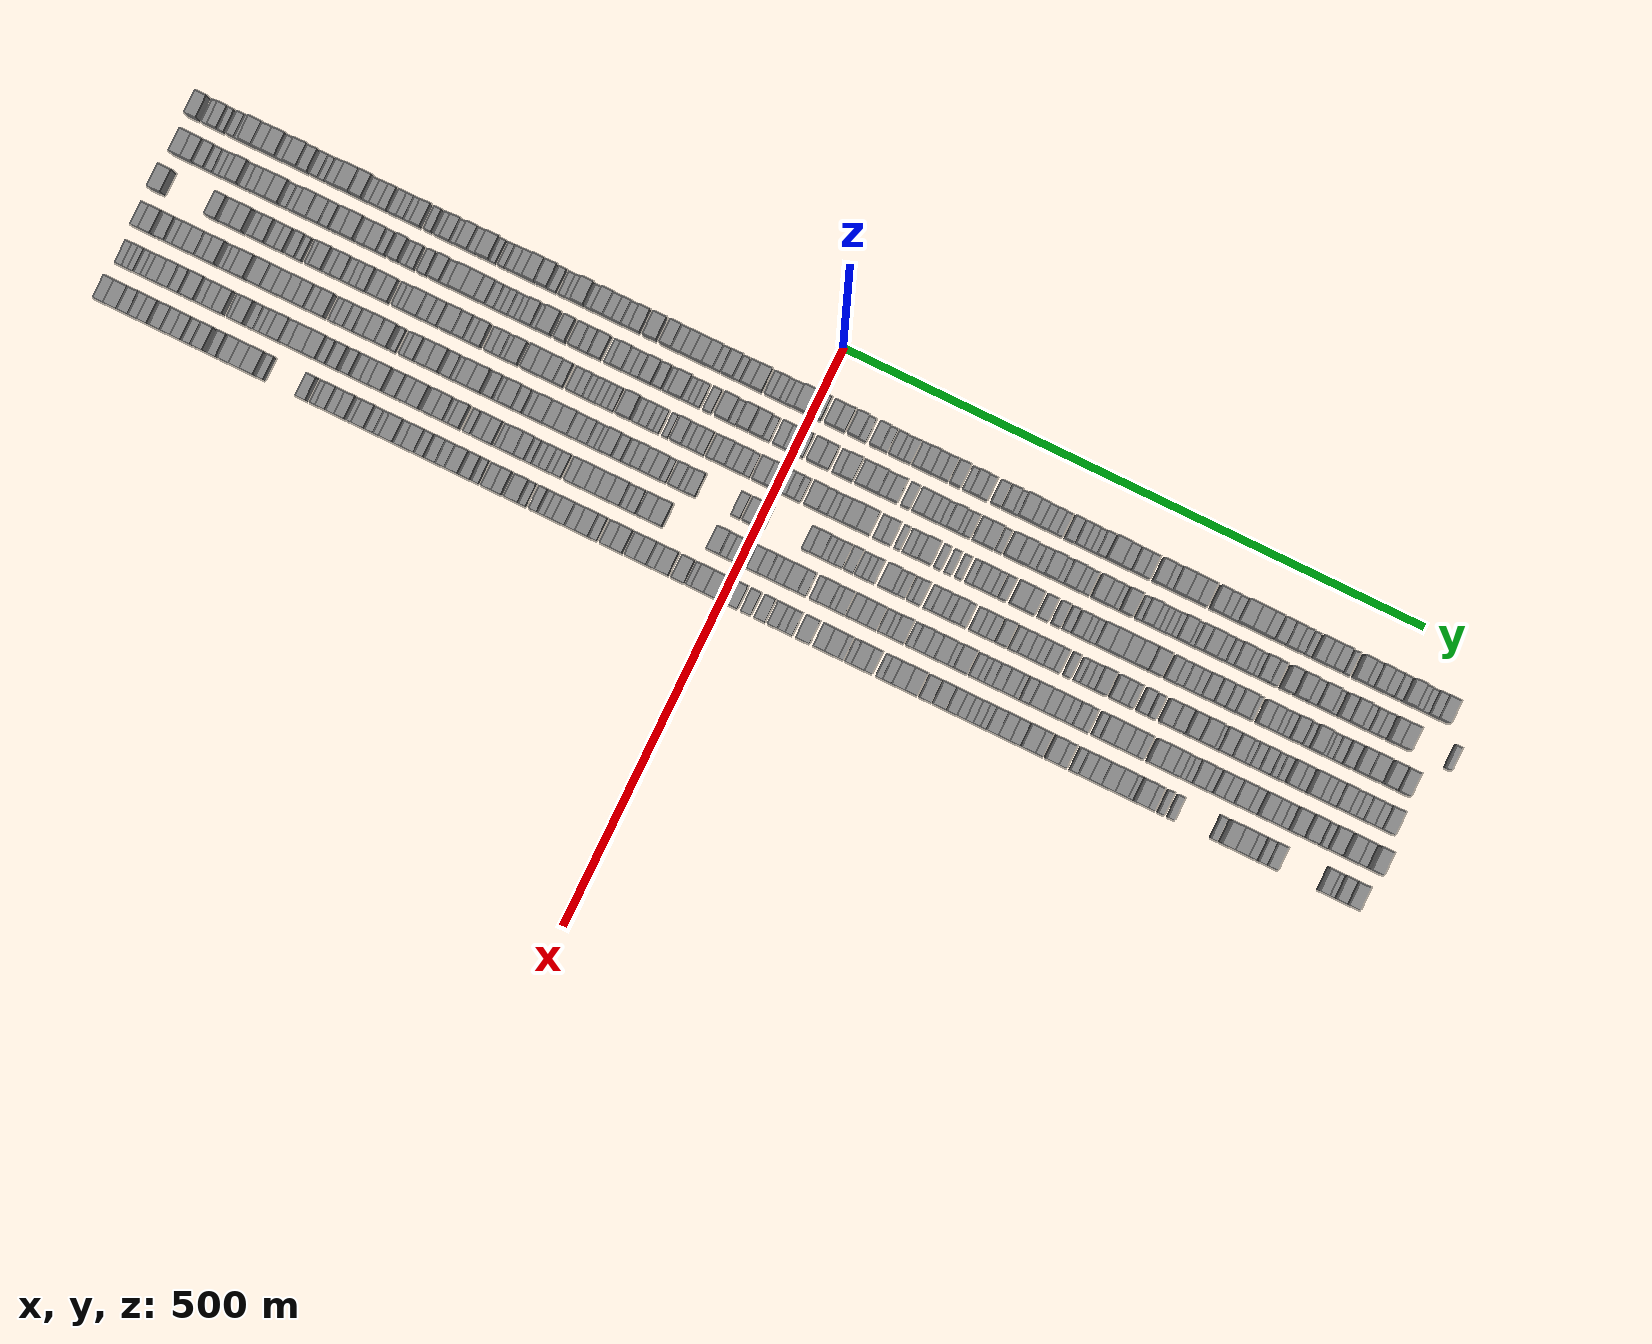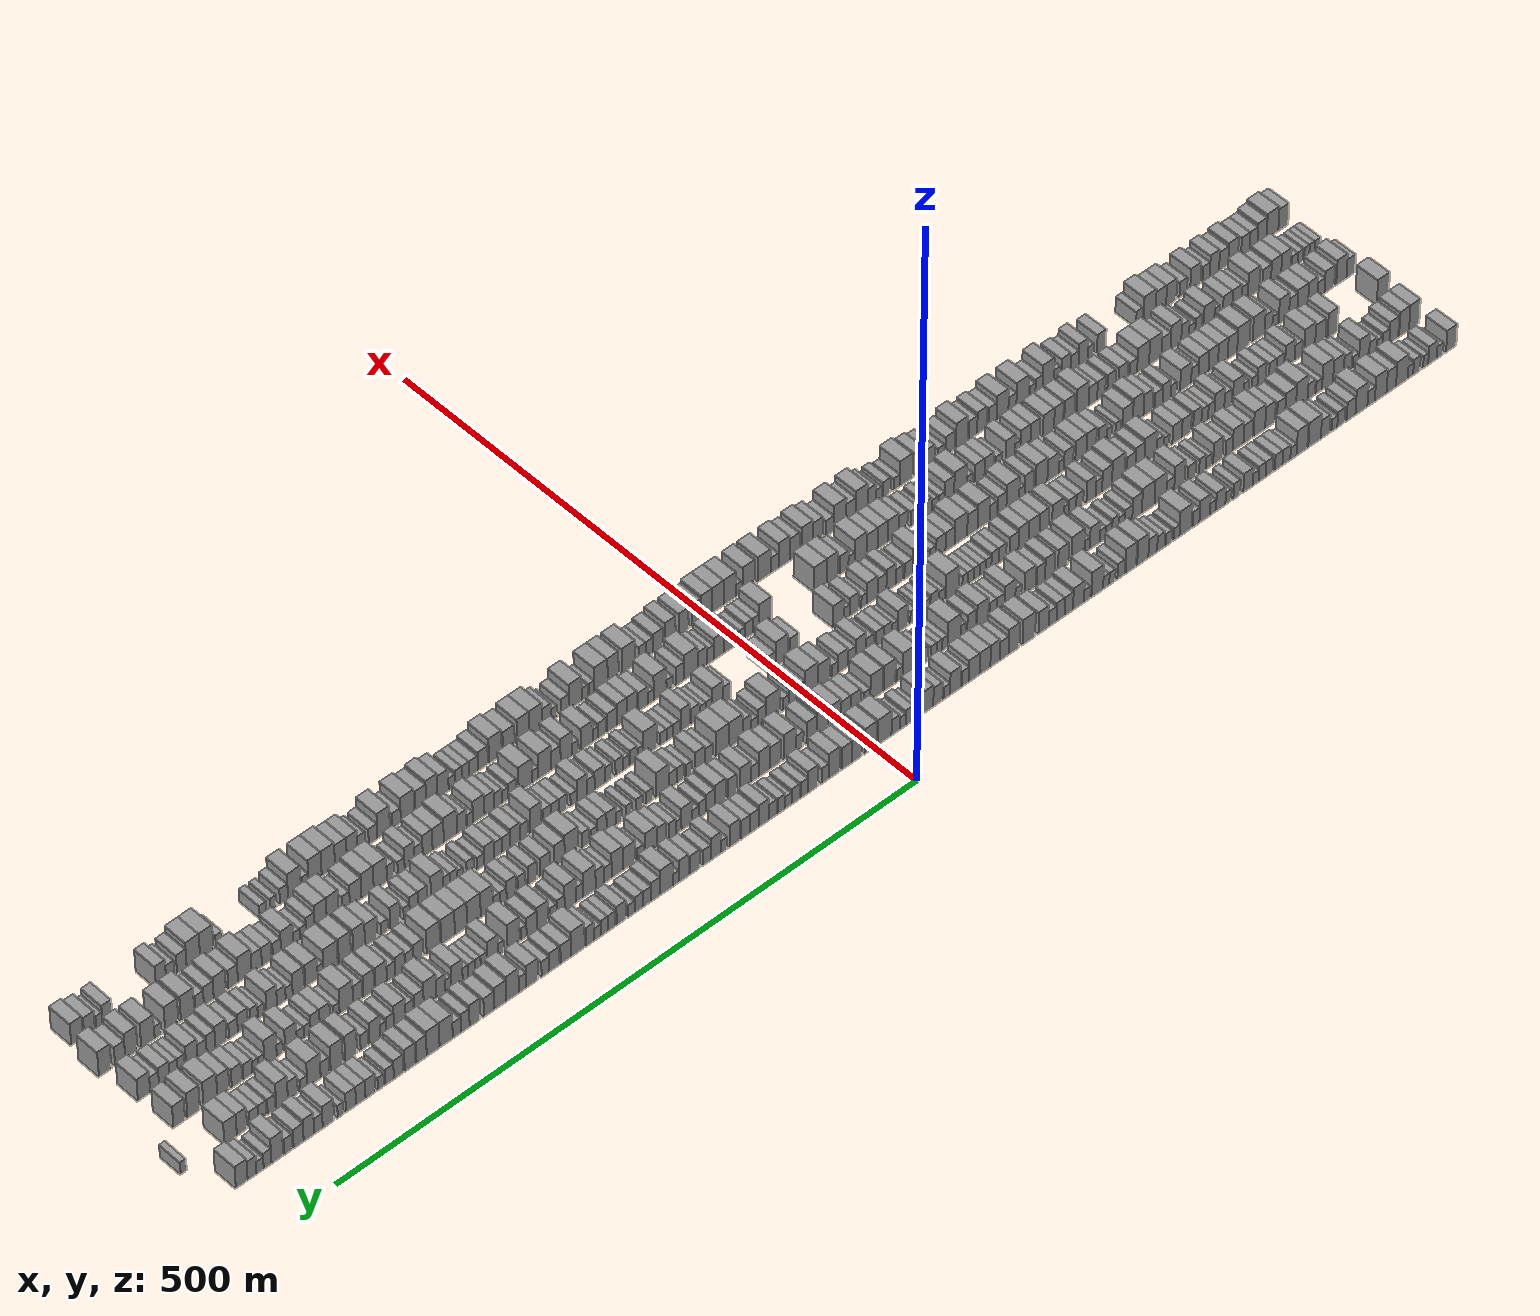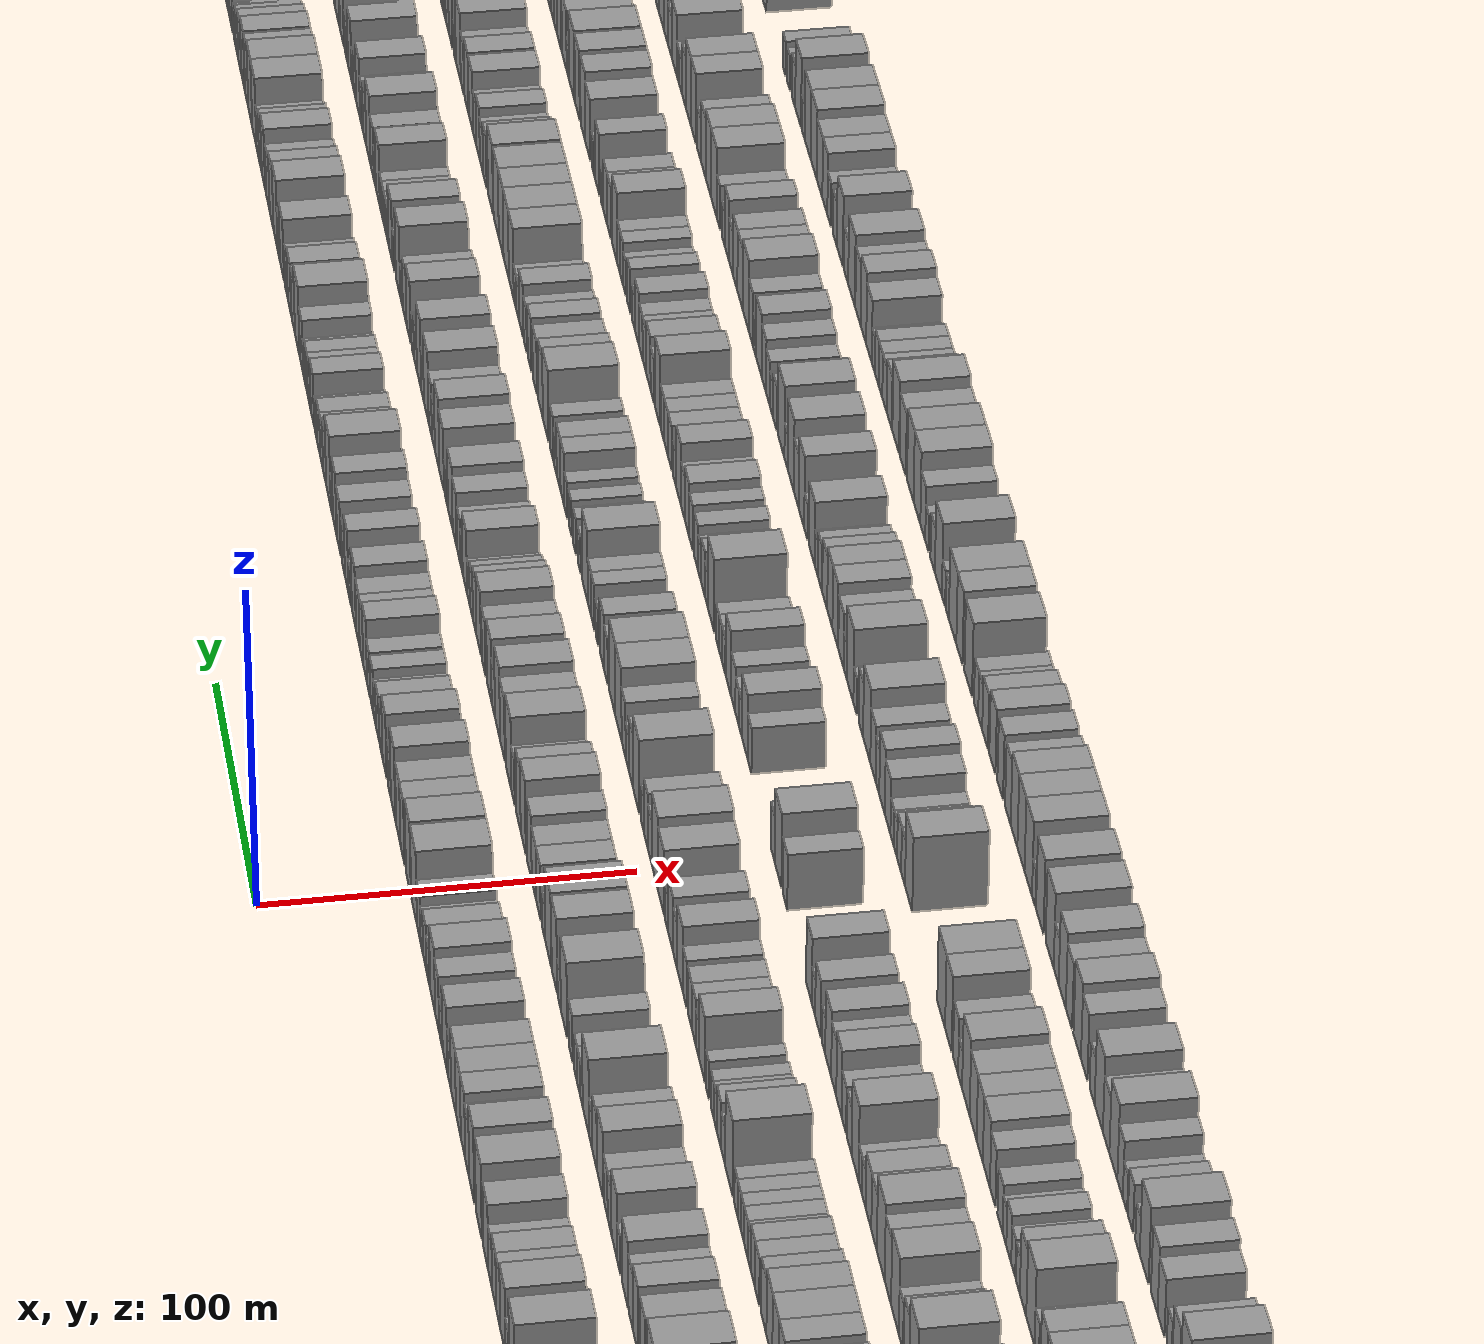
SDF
<sdf version="1.6">
 <world name="default">
  <scene>
   <sky><clouds><speed>12</speed></clouds></sky>
   <ambient>0.4 0.4 0.4 1</ambient>
   <background>0.7 0.7 0.7 1</background>
   <shadows>1</shadows>
  </scene>
  <gravity>0 0 -9.8066</gravity>
  <magnetic_field>6e-06 2.3e-05 -4.2e-05</magnetic_field>
  <physics default="0" name="default_physics" type="ode">
   <ode>
    <solver>
     <type>quick</type>
     <iters>10</iters>
     <sor>1.0</sor>
     <use_dynamic_moi_rescaling>0</use_dynamic_moi_rescaling>
    </solver>
    <constraints>
     <cfm>0</cfm>
     <erp>0.2</erp>
     <contact_max_correcting_vel>100</contact_max_correcting_vel>
     <contact_surface_layer>0.001</contact_surface_layer>
    </constraints>
   </ode>
   <max_step_size>0.004</max_step_size>
   <real_time_factor>1</real_time_factor>
   <real_time_update_rate>250</real_time_update_rate>
  </physics>
  <light name="sun" type="directional">
   <pose>0 0 10 0 0 0</pose>
   <diffuse>0.8 0.8 0.8 1</diffuse>
   <specular>0.2 0.2 0.2 1</specular>
   <attenuation>
    <range>1000</range>
    <constant>0.9</constant>
    <linear>0.01</linear>
    <quadratic>0.001</quadratic>
   </attenuation>
   <direction>-0.5 0.1 -0.9</direction>
  </light>
  <model name="building_1">
   <static>1</static>
   <pose>50.0000 -535.0532 0 0.000000 0.000000 0.000000</pose>
   <link name="link">
    <pose>0 0 10.50 0 0 0</pose>
    <collision name="collision"><geometry><box><size>20.0000 9.8937 21.0000</size></box></geometry></collision>
    <visual name="visual">
     <cast_shadows>0</cast_shadows>
     <geometry><box><size>20.0000 9.8937 21.0000</size></box></geometry>
     <material>
      <script>
       <uri>model://grey_wall/materials/scripts</uri>
       <uri>model://grey_wall/materials/textures</uri>
       <name>vrc/grey_wall</name>
      </script>
     </material>
    </visual>
   </link>
  </model>
  <model name="building_2">
   <static>1</static>
   <pose>50.0000 -524.1142 0 0.000000 0.000000 0.000000</pose>
   <link name="link">
    <pose>0 0 6.00 0 0 0</pose>
    <collision name="collision"><geometry><box><size>20.0000 5.9842 12.0000</size></box></geometry></collision>
    <visual name="visual">
     <cast_shadows>0</cast_shadows>
     <geometry><box><size>20.0000 5.9842 12.0000</size></box></geometry>
     <material>
      <script>
       <uri>model://grey_wall/materials/scripts</uri>
       <uri>model://grey_wall/materials/textures</uri>
       <name>vrc/grey_wall</name>
      </script>
     </material>
    </visual>
   </link>
  </model>
  <model name="building_3">
   <static>1</static>
   <pose>50.0000 -516.9838 0 0.000000 0.000000 0.000000</pose>
   <link name="link">
    <pose>0 0 9.00 0 0 0</pose>
    <collision name="collision"><geometry><box><size>20.0000 8.2768 18.0000</size></box></geometry></collision>
    <visual name="visual">
     <cast_shadows>0</cast_shadows>
     <geometry><box><size>20.0000 8.2768 18.0000</size></box></geometry>
     <material>
      <script>
       <uri>model://grey_wall/materials/scripts</uri>
       <uri>model://grey_wall/materials/textures</uri>
       <name>vrc/grey_wall</name>
      </script>
     </material>
    </visual>
   </link>
  </model>
  <model name="building_4">
   <static>1</static>
   <pose>50.0000 -510.3812 0 0.000000 0.000000 0.000000</pose>
   <link name="link">
    <pose>0 0 6.00 0 0 0</pose>
    <collision name="collision"><geometry><box><size>20.0000 4.9282 12.0000</size></box></geometry></collision>
    <visual name="visual">
     <cast_shadows>0</cast_shadows>
     <geometry><box><size>20.0000 4.9282 12.0000</size></box></geometry>
     <material>
      <script>
       <uri>model://grey_wall/materials/scripts</uri>
       <uri>model://grey_wall/materials/textures</uri>
       <name>vrc/grey_wall</name>
      </script>
     </material>
    </visual>
   </link>
  </model>
  <model name="building_5">
   <static>1</static>
   <pose>50.0000 -501.6513 0 0.000000 0.000000 0.000000</pose>
   <link name="link">
    <pose>0 0 7.50 0 0 0</pose>
    <collision name="collision"><geometry><box><size>20.0000 6.5316 15.0000</size></box></geometry></collision>
    <visual name="visual">
     <cast_shadows>0</cast_shadows>
     <geometry><box><size>20.0000 6.5316 15.0000</size></box></geometry>
     <material>
      <script>
       <uri>model://grey_wall/materials/scripts</uri>
       <uri>model://grey_wall/materials/textures</uri>
       <name>vrc/grey_wall</name>
      </script>
     </material>
    </visual>
   </link>
  </model>
  <model name="building_6">
   <static>1</static>
   <pose>50.0000 -495.8158 0 0.000000 0.000000 0.000000</pose>
   <link name="link">
    <pose>0 0 6.00 0 0 0</pose>
    <collision name="collision"><geometry><box><size>20.0000 5.1393 12.0000</size></box></geometry></collision>
    <visual name="visual">
     <cast_shadows>0</cast_shadows>
     <geometry><box><size>20.0000 5.1393 12.0000</size></box></geometry>
     <material>
      <script>
       <uri>model://grey_wall/materials/scripts</uri>
       <uri>model://grey_wall/materials/textures</uri>
       <name>vrc/grey_wall</name>
      </script>
     </material>
    </visual>
   </link>
  </model>
  <model name="building_7">
   <static>1</static>
   <pose>50.0000 -487.5946 0 0.000000 0.000000 0.000000</pose>
   <link name="link">
    <pose>0 0 12.00 0 0 0</pose>
    <collision name="collision"><geometry><box><size>20.0000 11.3032 24.0000</size></box></geometry></collision>
    <visual name="visual">
     <cast_shadows>0</cast_shadows>
     <geometry><box><size>20.0000 11.3032 24.0000</size></box></geometry>
     <material>
      <script>
       <uri>model://grey_wall/materials/scripts</uri>
       <uri>model://grey_wall/materials/textures</uri>
       <name>vrc/grey_wall</name>
      </script>
     </material>
    </visual>
   </link>
  </model>
  <model name="building_8">
   <static>1</static>
   <pose>50.0000 -477.3992 0 0.000000 0.000000 0.000000</pose>
   <link name="link">
    <pose>0 0 10.50 0 0 0</pose>
    <collision name="collision"><geometry><box><size>20.0000 9.0877 21.0000</size></box></geometry></collision>
    <visual name="visual">
     <cast_shadows>0</cast_shadows>
     <geometry><box><size>20.0000 9.0877 21.0000</size></box></geometry>
     <material>
      <script>
       <uri>model://grey_wall/materials/scripts</uri>
       <uri>model://grey_wall/materials/textures</uri>
       <name>vrc/grey_wall</name>
      </script>
     </material>
    </visual>
   </link>
  </model>
  <model name="building_9">
   <static>1</static>
   <pose>50.0000 -467.2614 0 0.000000 0.000000 0.000000</pose>
   <link name="link">
    <pose>0 0 12.00 0 0 0</pose>
    <collision name="collision"><geometry><box><size>20.0000 11.1878 24.0000</size></box></geometry></collision>
    <visual name="visual">
     <cast_shadows>0</cast_shadows>
     <geometry><box><size>20.0000 11.1878 24.0000</size></box></geometry>
     <material>
      <script>
       <uri>model://grey_wall/materials/scripts</uri>
       <uri>model://grey_wall/materials/textures</uri>
       <name>vrc/grey_wall</name>
      </script>
     </material>
    </visual>
   </link>
  </model>
  <model name="building_10">
   <static>1</static>
   <pose>50.0000 -458.1173 0 0.000000 0.000000 0.000000</pose>
   <link name="link">
    <pose>0 0 7.50 0 0 0</pose>
    <collision name="collision"><geometry><box><size>20.0000 7.1003 15.0000</size></box></geometry></collision>
    <visual name="visual">
     <cast_shadows>0</cast_shadows>
     <geometry><box><size>20.0000 7.1003 15.0000</size></box></geometry>
     <material>
      <script>
       <uri>model://grey_wall/materials/scripts</uri>
       <uri>model://grey_wall/materials/textures</uri>
       <name>vrc/grey_wall</name>
      </script>
     </material>
    </visual>
   </link>
  </model>
  <model name="building_11">
   <static>1</static>
   <pose>50.0000 -448.8677 0 0.000000 0.000000 0.000000</pose>
   <link name="link">
    <pose>0 0 12.00 0 0 0</pose>
    <collision name="collision"><geometry><box><size>20.0000 11.3988 24.0000</size></box></geometry></collision>
    <visual name="visual">
     <cast_shadows>0</cast_shadows>
     <geometry><box><size>20.0000 11.3988 24.0000</size></box></geometry>
     <material>
      <script>
       <uri>model://grey_wall/materials/scripts</uri>
       <uri>model://grey_wall/materials/textures</uri>
       <name>vrc/grey_wall</name>
      </script>
     </material>
    </visual>
   </link>
  </model>
  <model name="building_12">
   <static>1</static>
   <pose>50.0000 -438.9999 0 0.000000 0.000000 0.000000</pose>
   <link name="link">
    <pose>0 0 9.00 0 0 0</pose>
    <collision name="collision"><geometry><box><size>20.0000 8.3368 18.0000</size></box></geometry></collision>
    <visual name="visual">
     <cast_shadows>0</cast_shadows>
     <geometry><box><size>20.0000 8.3368 18.0000</size></box></geometry>
     <material>
      <script>
       <uri>model://grey_wall/materials/scripts</uri>
       <uri>model://grey_wall/materials/textures</uri>
       <name>vrc/grey_wall</name>
      </script>
     </material>
    </visual>
   </link>
  </model>
  <model name="building_13">
   <static>1</static>
   <pose>50.0000 -429.3680 0 0.000000 0.000000 0.000000</pose>
   <link name="link">
    <pose>0 0 7.50 0 0 0</pose>
    <collision name="collision"><geometry><box><size>20.0000 6.9269 15.0000</size></box></geometry></collision>
    <visual name="visual">
     <cast_shadows>0</cast_shadows>
     <geometry><box><size>20.0000 6.9269 15.0000</size></box></geometry>
     <material>
      <script>
       <uri>model://grey_wall/materials/scripts</uri>
       <uri>model://grey_wall/materials/textures</uri>
       <name>vrc/grey_wall</name>
      </script>
     </material>
    </visual>
   </link>
  </model>
  <model name="building_14">
   <static>1</static>
   <pose>50.0000 -423.2773 0 0.000000 0.000000 0.000000</pose>
   <link name="link">
    <pose>0 0 6.00 0 0 0</pose>
    <collision name="collision"><geometry><box><size>20.0000 5.2544 12.0000</size></box></geometry></collision>
    <visual name="visual">
     <cast_shadows>0</cast_shadows>
     <geometry><box><size>20.0000 5.2544 12.0000</size></box></geometry>
     <material>
      <script>
       <uri>model://grey_wall/materials/scripts</uri>
       <uri>model://grey_wall/materials/textures</uri>
       <name>vrc/grey_wall</name>
      </script>
     </material>
    </visual>
   </link>
  </model>
  <model name="building_15">
   <static>1</static>
   <pose>50.0000 -414.4967 0 0.000000 0.000000 0.000000</pose>
   <link name="link">
    <pose>0 0 9.00 0 0 0</pose>
    <collision name="collision"><geometry><box><size>20.0000 8.3069 18.0000</size></box></geometry></collision>
    <visual name="visual">
     <cast_shadows>0</cast_shadows>
     <geometry><box><size>20.0000 8.3069 18.0000</size></box></geometry>
     <material>
      <script>
       <uri>model://grey_wall/materials/scripts</uri>
       <uri>model://grey_wall/materials/textures</uri>
       <name>vrc/grey_wall</name>
      </script>
     </material>
    </visual>
   </link>
  </model>
  <model name="building_16">
   <static>1</static>
   <pose>50.0000 -404.3674 0 0.000000 0.000000 0.000000</pose>
   <link name="link">
    <pose>0 0 12.00 0 0 0</pose>
    <collision name="collision"><geometry><box><size>20.0000 11.9518 24.0000</size></box></geometry></collision>
    <visual name="visual">
     <cast_shadows>0</cast_shadows>
     <geometry><box><size>20.0000 11.9518 24.0000</size></box></geometry>
     <material>
      <script>
       <uri>model://grey_wall/materials/scripts</uri>
       <uri>model://grey_wall/materials/textures</uri>
       <name>vrc/grey_wall</name>
      </script>
     </material>
    </visual>
   </link>
  </model>
  <model name="building_17">
   <static>1</static>
   <pose>50.0000 -392.3317 0 0.000000 0.000000 0.000000</pose>
   <link name="link">
    <pose>0 0 12.00 0 0 0</pose>
    <collision name="collision"><geometry><box><size>20.0000 10.1196 24.0000</size></box></geometry></collision>
    <visual name="visual">
     <cast_shadows>0</cast_shadows>
     <geometry><box><size>20.0000 10.1196 24.0000</size></box></geometry>
     <material>
      <script>
       <uri>model://grey_wall/materials/scripts</uri>
       <uri>model://grey_wall/materials/textures</uri>
       <name>vrc/grey_wall</name>
      </script>
     </material>
    </visual>
   </link>
  </model>
  <model name="building_18">
   <static>1</static>
   <pose>50.0000 -384.3064 0 0.000000 0.000000 0.000000</pose>
   <link name="link">
    <pose>0 0 6.00 0 0 0</pose>
    <collision name="collision"><geometry><box><size>20.0000 5.9310 12.0000</size></box></geometry></collision>
    <visual name="visual">
     <cast_shadows>0</cast_shadows>
     <geometry><box><size>20.0000 5.9310 12.0000</size></box></geometry>
     <material>
      <script>
       <uri>model://grey_wall/materials/scripts</uri>
       <uri>model://grey_wall/materials/textures</uri>
       <name>vrc/grey_wall</name>
      </script>
     </material>
    </visual>
   </link>
  </model>
  <model name="building_19">
   <static>1</static>
   <pose>50.0000 -377.6340 0 0.000000 0.000000 0.000000</pose>
   <link name="link">
    <pose>0 0 7.50 0 0 0</pose>
    <collision name="collision"><geometry><box><size>20.0000 7.4138 15.0000</size></box></geometry></collision>
    <visual name="visual">
     <cast_shadows>0</cast_shadows>
     <geometry><box><size>20.0000 7.4138 15.0000</size></box></geometry>
     <material>
      <script>
       <uri>model://grey_wall/materials/scripts</uri>
       <uri>model://grey_wall/materials/textures</uri>
       <name>vrc/grey_wall</name>
      </script>
     </material>
    </visual>
   </link>
  </model>
  <model name="building_20">
   <static>1</static>
   <pose>50.0000 -370.3823 0 0.000000 0.000000 0.000000</pose>
   <link name="link">
    <pose>0 0 7.50 0 0 0</pose>
    <collision name="collision"><geometry><box><size>20.0000 7.0895 15.0000</size></box></geometry></collision>
    <visual name="visual">
     <cast_shadows>0</cast_shadows>
     <geometry><box><size>20.0000 7.0895 15.0000</size></box></geometry>
     <material>
      <script>
       <uri>model://grey_wall/materials/scripts</uri>
       <uri>model://grey_wall/materials/textures</uri>
       <name>vrc/grey_wall</name>
      </script>
     </material>
    </visual>
   </link>
  </model>
  <model name="building_21">
   <static>1</static>
   <pose>50.0000 -361.4467 0 0.000000 0.000000 0.000000</pose>
   <link name="link">
    <pose>0 0 7.50 0 0 0</pose>
    <collision name="collision"><geometry><box><size>20.0000 6.7816 15.0000</size></box></geometry></collision>
    <visual name="visual">
     <cast_shadows>0</cast_shadows>
     <geometry><box><size>20.0000 6.7816 15.0000</size></box></geometry>
     <material>
      <script>
       <uri>model://grey_wall/materials/scripts</uri>
       <uri>model://grey_wall/materials/textures</uri>
       <name>vrc/grey_wall</name>
      </script>
     </material>
    </visual>
   </link>
  </model>
  <model name="building_22">
   <static>1</static>
   <pose>50.0000 -354.8756 0 0.000000 0.000000 0.000000</pose>
   <link name="link">
    <pose>0 0 7.50 0 0 0</pose>
    <collision name="collision"><geometry><box><size>20.0000 6.3606 15.0000</size></box></geometry></collision>
    <visual name="visual">
     <cast_shadows>0</cast_shadows>
     <geometry><box><size>20.0000 6.3606 15.0000</size></box></geometry>
     <material>
      <script>
       <uri>model://grey_wall/materials/scripts</uri>
       <uri>model://grey_wall/materials/textures</uri>
       <name>vrc/grey_wall</name>
      </script>
     </material>
    </visual>
   </link>
  </model>
  <model name="building_23">
   <static>1</static>
   <pose>50.0000 -348.8726 0 0.000000 0.000000 0.000000</pose>
   <link name="link">
    <pose>0 0 6.00 0 0 0</pose>
    <collision name="collision"><geometry><box><size>20.0000 5.6454 12.0000</size></box></geometry></collision>
    <visual name="visual">
     <cast_shadows>0</cast_shadows>
     <geometry><box><size>20.0000 5.6454 12.0000</size></box></geometry>
     <material>
      <script>
       <uri>model://grey_wall/materials/scripts</uri>
       <uri>model://grey_wall/materials/textures</uri>
       <name>vrc/grey_wall</name>
      </script>
     </material>
    </visual>
   </link>
  </model>
  <model name="building_24">
   <static>1</static>
   <pose>50.0000 -341.5945 0 0.000000 0.000000 0.000000</pose>
   <link name="link">
    <pose>0 0 9.00 0 0 0</pose>
    <collision name="collision"><geometry><box><size>20.0000 8.9108 18.0000</size></box></geometry></collision>
    <visual name="visual">
     <cast_shadows>0</cast_shadows>
     <geometry><box><size>20.0000 8.9108 18.0000</size></box></geometry>
     <material>
      <script>
       <uri>model://grey_wall/materials/scripts</uri>
       <uri>model://grey_wall/materials/textures</uri>
       <name>vrc/grey_wall</name>
      </script>
     </material>
    </visual>
   </link>
  </model>
  <model name="building_25">
   <static>1</static>
   <pose>50.0000 -330.9792 0 0.000000 0.000000 0.000000</pose>
   <link name="link">
    <pose>0 0 7.50 0 0 0</pose>
    <collision name="collision"><geometry><box><size>20.0000 6.3199 15.0000</size></box></geometry></collision>
    <visual name="visual">
     <cast_shadows>0</cast_shadows>
     <geometry><box><size>20.0000 6.3199 15.0000</size></box></geometry>
     <material>
      <script>
       <uri>model://grey_wall/materials/scripts</uri>
       <uri>model://grey_wall/materials/textures</uri>
       <name>vrc/grey_wall</name>
      </script>
     </material>
    </visual>
   </link>
  </model>
  <model name="building_26">
   <static>1</static>
   <pose>50.0000 -323.0660 0 0.000000 0.000000 0.000000</pose>
   <link name="link">
    <pose>0 0 6.00 0 0 0</pose>
    <collision name="collision"><geometry><box><size>20.0000 5.5065 12.0000</size></box></geometry></collision>
    <visual name="visual">
     <cast_shadows>0</cast_shadows>
     <geometry><box><size>20.0000 5.5065 12.0000</size></box></geometry>
     <material>
      <script>
       <uri>model://grey_wall/materials/scripts</uri>
       <uri>model://grey_wall/materials/textures</uri>
       <name>vrc/grey_wall</name>
      </script>
     </material>
    </visual>
   </link>
  </model>
  <model name="building_27">
   <static>1</static>
   <pose>50.0000 -315.9549 0 0.000000 0.000000 0.000000</pose>
   <link name="link">
    <pose>0 0 9.00 0 0 0</pose>
    <collision name="collision"><geometry><box><size>20.0000 8.7158 18.0000</size></box></geometry></collision>
    <visual name="visual">
     <cast_shadows>0</cast_shadows>
     <geometry><box><size>20.0000 8.7158 18.0000</size></box></geometry>
     <material>
      <script>
       <uri>model://grey_wall/materials/scripts</uri>
       <uri>model://grey_wall/materials/textures</uri>
       <name>vrc/grey_wall</name>
      </script>
     </material>
    </visual>
   </link>
  </model>
  <model name="building_28">
   <static>1</static>
   <pose>50.0000 -308.7147 0 0.000000 0.000000 0.000000</pose>
   <link name="link">
    <pose>0 0 6.00 0 0 0</pose>
    <collision name="collision"><geometry><box><size>20.0000 5.7645 12.0000</size></box></geometry></collision>
    <visual name="visual">
     <cast_shadows>0</cast_shadows>
     <geometry><box><size>20.0000 5.7645 12.0000</size></box></geometry>
     <material>
      <script>
       <uri>model://grey_wall/materials/scripts</uri>
       <uri>model://grey_wall/materials/textures</uri>
       <name>vrc/grey_wall</name>
      </script>
     </material>
    </visual>
   </link>
  </model>
  <model name="building_29">
   <static>1</static>
   <pose>50.0000 -300.9488 0 0.000000 0.000000 0.000000</pose>
   <link name="link">
    <pose>0 0 10.50 0 0 0</pose>
    <collision name="collision"><geometry><box><size>20.0000 9.7675 21.0000</size></box></geometry></collision>
    <visual name="visual">
     <cast_shadows>0</cast_shadows>
     <geometry><box><size>20.0000 9.7675 21.0000</size></box></geometry>
     <material>
      <script>
       <uri>model://grey_wall/materials/scripts</uri>
       <uri>model://grey_wall/materials/textures</uri>
       <name>vrc/grey_wall</name>
      </script>
     </material>
    </visual>
   </link>
  </model>
  <model name="building_30">
   <static>1</static>
   <pose>50.0000 -292.9316 0 0.000000 0.000000 0.000000</pose>
   <link name="link">
    <pose>0 0 7.50 0 0 0</pose>
    <collision name="collision"><geometry><box><size>20.0000 6.2669 15.0000</size></box></geometry></collision>
    <visual name="visual">
     <cast_shadows>0</cast_shadows>
     <geometry><box><size>20.0000 6.2669 15.0000</size></box></geometry>
     <material>
      <script>
       <uri>model://grey_wall/materials/scripts</uri>
       <uri>model://grey_wall/materials/textures</uri>
       <name>vrc/grey_wall</name>
      </script>
     </material>
    </visual>
   </link>
  </model>
  <model name="building_31">
   <static>1</static>
   <pose>50.0000 -283.1510 0 0.000000 0.000000 0.000000</pose>
   <link name="link">
    <pose>0 0 12.00 0 0 0</pose>
    <collision name="collision"><geometry><box><size>20.0000 11.2944 24.0000</size></box></geometry></collision>
    <visual name="visual">
     <cast_shadows>0</cast_shadows>
     <geometry><box><size>20.0000 11.2944 24.0000</size></box></geometry>
     <material>
      <script>
       <uri>model://grey_wall/materials/scripts</uri>
       <uri>model://grey_wall/materials/textures</uri>
       <name>vrc/grey_wall</name>
      </script>
     </material>
    </visual>
   </link>
  </model>
  <model name="building_32">
   <static>1</static>
   <pose>50.0000 -274.9794 0 0.000000 0.000000 0.000000</pose>
   <link name="link">
    <pose>0 0 6.00 0 0 0</pose>
    <collision name="collision"><geometry><box><size>20.0000 5.0487 12.0000</size></box></geometry></collision>
    <visual name="visual">
     <cast_shadows>0</cast_shadows>
     <geometry><box><size>20.0000 5.0487 12.0000</size></box></geometry>
     <material>
      <script>
       <uri>model://grey_wall/materials/scripts</uri>
       <uri>model://grey_wall/materials/textures</uri>
       <name>vrc/grey_wall</name>
      </script>
     </material>
    </visual>
   </link>
  </model>
  <model name="building_33">
   <static>1</static>
   <pose>50.0000 -267.6295 0 0.000000 0.000000 0.000000</pose>
   <link name="link">
    <pose>0 0 6.00 0 0 0</pose>
    <collision name="collision"><geometry><box><size>20.0000 5.6511 12.0000</size></box></geometry></collision>
    <visual name="visual">
     <cast_shadows>0</cast_shadows>
     <geometry><box><size>20.0000 5.6511 12.0000</size></box></geometry>
     <material>
      <script>
       <uri>model://grey_wall/materials/scripts</uri>
       <uri>model://grey_wall/materials/textures</uri>
       <name>vrc/grey_wall</name>
      </script>
     </material>
    </visual>
   </link>
  </model>
  <model name="building_34">
   <static>1</static>
   <pose>50.0000 -260.2772 0 0.000000 0.000000 0.000000</pose>
   <link name="link">
    <pose>0 0 7.50 0 0 0</pose>
    <collision name="collision"><geometry><box><size>20.0000 7.0536 15.0000</size></box></geometry></collision>
    <visual name="visual">
     <cast_shadows>0</cast_shadows>
     <geometry><box><size>20.0000 7.0536 15.0000</size></box></geometry>
     <material>
      <script>
       <uri>model://grey_wall/materials/scripts</uri>
       <uri>model://grey_wall/materials/textures</uri>
       <name>vrc/grey_wall</name>
      </script>
     </material>
    </visual>
   </link>
  </model>
  <model name="building_35">
   <static>1</static>
   <pose>50.0000 -252.6616 0 0.000000 0.000000 0.000000</pose>
   <link name="link">
    <pose>0 0 9.00 0 0 0</pose>
    <collision name="collision"><geometry><box><size>20.0000 8.1775 18.0000</size></box></geometry></collision>
    <visual name="visual">
     <cast_shadows>0</cast_shadows>
     <geometry><box><size>20.0000 8.1775 18.0000</size></box></geometry>
     <material>
      <script>
       <uri>model://grey_wall/materials/scripts</uri>
       <uri>model://grey_wall/materials/textures</uri>
       <name>vrc/grey_wall</name>
      </script>
     </material>
    </visual>
   </link>
  </model>
  <model name="building_36">
   <static>1</static>
   <pose>50.0000 -243.4443 0 0.000000 0.000000 0.000000</pose>
   <link name="link">
    <pose>0 0 12.00 0 0 0</pose>
    <collision name="collision"><geometry><box><size>20.0000 10.2570 24.0000</size></box></geometry></collision>
    <visual name="visual">
     <cast_shadows>0</cast_shadows>
     <geometry><box><size>20.0000 10.2570 24.0000</size></box></geometry>
     <material>
      <script>
       <uri>model://grey_wall/materials/scripts</uri>
       <uri>model://grey_wall/materials/textures</uri>
       <name>vrc/grey_wall</name>
      </script>
     </material>
    </visual>
   </link>
  </model>
  <model name="building_37">
   <static>1</static>
   <pose>50.0000 -232.4229 0 0.000000 0.000000 0.000000</pose>
   <link name="link">
    <pose>0 0 12.00 0 0 0</pose>
    <collision name="collision"><geometry><box><size>20.0000 9.7857 24.0000</size></box></geometry></collision>
    <visual name="visual">
     <cast_shadows>0</cast_shadows>
     <geometry><box><size>20.0000 9.7857 24.0000</size></box></geometry>
     <material>
      <script>
       <uri>model://grey_wall/materials/scripts</uri>
       <uri>model://grey_wall/materials/textures</uri>
       <name>vrc/grey_wall</name>
      </script>
     </material>
    </visual>
   </link>
  </model>
  <model name="building_38">
   <static>1</static>
   <pose>50.0000 -223.2568 0 0.000000 0.000000 0.000000</pose>
   <link name="link">
    <pose>0 0 7.50 0 0 0</pose>
    <collision name="collision"><geometry><box><size>20.0000 6.5466 15.0000</size></box></geometry></collision>
    <visual name="visual">
     <cast_shadows>0</cast_shadows>
     <geometry><box><size>20.0000 6.5466 15.0000</size></box></geometry>
     <material>
      <script>
       <uri>model://grey_wall/materials/scripts</uri>
       <uri>model://grey_wall/materials/textures</uri>
       <name>vrc/grey_wall</name>
      </script>
     </material>
    </visual>
   </link>
  </model>
  <model name="building_39">
   <static>1</static>
   <pose>50.0000 -215.2266 0 0.000000 0.000000 0.000000</pose>
   <link name="link">
    <pose>0 0 6.00 0 0 0</pose>
    <collision name="collision"><geometry><box><size>20.0000 5.5136 12.0000</size></box></geometry></collision>
    <visual name="visual">
     <cast_shadows>0</cast_shadows>
     <geometry><box><size>20.0000 5.5136 12.0000</size></box></geometry>
     <material>
      <script>
       <uri>model://grey_wall/materials/scripts</uri>
       <uri>model://grey_wall/materials/textures</uri>
       <name>vrc/grey_wall</name>
      </script>
     </material>
    </visual>
   </link>
  </model>
  <model name="building_40">
   <static>1</static>
   <pose>50.0000 -209.6688 0 0.000000 0.000000 0.000000</pose>
   <link name="link">
    <pose>0 0 6.00 0 0 0</pose>
    <collision name="collision"><geometry><box><size>20.0000 5.6020 12.0000</size></box></geometry></collision>
    <visual name="visual">
     <cast_shadows>0</cast_shadows>
     <geometry><box><size>20.0000 5.6020 12.0000</size></box></geometry>
     <material>
      <script>
       <uri>model://grey_wall/materials/scripts</uri>
       <uri>model://grey_wall/materials/textures</uri>
       <name>vrc/grey_wall</name>
      </script>
     </material>
    </visual>
   </link>
  </model>
  <model name="building_41">
   <static>1</static>
   <pose>50.0000 -201.4734 0 0.000000 0.000000 0.000000</pose>
   <link name="link">
    <pose>0 0 12.00 0 0 0</pose>
    <collision name="collision"><geometry><box><size>20.0000 10.7889 24.0000</size></box></geometry></collision>
    <visual name="visual">
     <cast_shadows>0</cast_shadows>
     <geometry><box><size>20.0000 10.7889 24.0000</size></box></geometry>
     <material>
      <script>
       <uri>model://grey_wall/materials/scripts</uri>
       <uri>model://grey_wall/materials/textures</uri>
       <name>vrc/grey_wall</name>
      </script>
     </material>
    </visual>
   </link>
  </model>
  <model name="building_42">
   <static>1</static>
   <pose>50.0000 -192.1820 0 0.000000 0.000000 0.000000</pose>
   <link name="link">
    <pose>0 0 6.00 0 0 0</pose>
    <collision name="collision"><geometry><box><size>20.0000 5.7938 12.0000</size></box></geometry></collision>
    <visual name="visual">
     <cast_shadows>0</cast_shadows>
     <geometry><box><size>20.0000 5.7938 12.0000</size></box></geometry>
     <material>
      <script>
       <uri>model://grey_wall/materials/scripts</uri>
       <uri>model://grey_wall/materials/textures</uri>
       <name>vrc/grey_wall</name>
      </script>
     </material>
    </visual>
   </link>
  </model>
  <model name="building_43">
   <static>1</static>
   <pose>50.0000 -184.2456 0 0.000000 0.000000 0.000000</pose>
   <link name="link">
    <pose>0 0 10.50 0 0 0</pose>
    <collision name="collision"><geometry><box><size>20.0000 10.0789 21.0000</size></box></geometry></collision>
    <visual name="visual">
     <cast_shadows>0</cast_shadows>
     <geometry><box><size>20.0000 10.0789 21.0000</size></box></geometry>
     <material>
      <script>
       <uri>model://grey_wall/materials/scripts</uri>
       <uri>model://grey_wall/materials/textures</uri>
       <name>vrc/grey_wall</name>
      </script>
     </material>
    </visual>
   </link>
  </model>
  <model name="building_44">
   <static>1</static>
   <pose>50.0000 -175.4251 0 0.000000 0.000000 0.000000</pose>
   <link name="link">
    <pose>0 0 9.00 0 0 0</pose>
    <collision name="collision"><geometry><box><size>20.0000 7.5622 18.0000</size></box></geometry></collision>
    <visual name="visual">
     <cast_shadows>0</cast_shadows>
     <geometry><box><size>20.0000 7.5622 18.0000</size></box></geometry>
     <material>
      <script>
       <uri>model://grey_wall/materials/scripts</uri>
       <uri>model://grey_wall/materials/textures</uri>
       <name>vrc/grey_wall</name>
      </script>
     </material>
    </visual>
   </link>
  </model>
  <model name="building_45">
   <static>1</static>
   <pose>50.0000 -167.8421 0 0.000000 0.000000 0.000000</pose>
   <link name="link">
    <pose>0 0 9.00 0 0 0</pose>
    <collision name="collision"><geometry><box><size>20.0000 7.6039 18.0000</size></box></geometry></collision>
    <visual name="visual">
     <cast_shadows>0</cast_shadows>
     <geometry><box><size>20.0000 7.6039 18.0000</size></box></geometry>
     <material>
      <script>
       <uri>model://grey_wall/materials/scripts</uri>
       <uri>model://grey_wall/materials/textures</uri>
       <name>vrc/grey_wall</name>
      </script>
     </material>
    </visual>
   </link>
  </model>
  <model name="building_46">
   <static>1</static>
   <pose>50.0000 -160.4901 0 0.000000 0.000000 0.000000</pose>
   <link name="link">
    <pose>0 0 7.50 0 0 0</pose>
    <collision name="collision"><geometry><box><size>20.0000 7.0999 15.0000</size></box></geometry></collision>
    <visual name="visual">
     <cast_shadows>0</cast_shadows>
     <geometry><box><size>20.0000 7.0999 15.0000</size></box></geometry>
     <material>
      <script>
       <uri>model://grey_wall/materials/scripts</uri>
       <uri>model://grey_wall/materials/textures</uri>
       <name>vrc/grey_wall</name>
      </script>
     </material>
    </visual>
   </link>
  </model>
  <model name="building_47">
   <static>1</static>
   <pose>50.0000 -152.2340 0 0.000000 0.000000 0.000000</pose>
   <link name="link">
    <pose>0 0 10.50 0 0 0</pose>
    <collision name="collision"><geometry><box><size>20.0000 9.4122 21.0000</size></box></geometry></collision>
    <visual name="visual">
     <cast_shadows>0</cast_shadows>
     <geometry><box><size>20.0000 9.4122 21.0000</size></box></geometry>
     <material>
      <script>
       <uri>model://grey_wall/materials/scripts</uri>
       <uri>model://grey_wall/materials/textures</uri>
       <name>vrc/grey_wall</name>
      </script>
     </material>
    </visual>
   </link>
  </model>
  <model name="building_48">
   <static>1</static>
   <pose>50.0000 -138.8351 0 0.000000 0.000000 0.000000</pose>
   <link name="link">
    <pose>0 0 12.00 0 0 0</pose>
    <collision name="collision"><geometry><box><size>20.0000 11.3855 24.0000</size></box></geometry></collision>
    <visual name="visual">
     <cast_shadows>0</cast_shadows>
     <geometry><box><size>20.0000 11.3855 24.0000</size></box></geometry>
     <material>
      <script>
       <uri>model://grey_wall/materials/scripts</uri>
       <uri>model://grey_wall/materials/textures</uri>
       <name>vrc/grey_wall</name>
      </script>
     </material>
    </visual>
   </link>
  </model>
  <model name="building_49">
   <static>1</static>
   <pose>50.0000 -125.2403 0 0.000000 0.000000 0.000000</pose>
   <link name="link">
    <pose>0 0 12.00 0 0 0</pose>
    <collision name="collision"><geometry><box><size>20.0000 9.8042 24.0000</size></box></geometry></collision>
    <visual name="visual">
     <cast_shadows>0</cast_shadows>
     <geometry><box><size>20.0000 9.8042 24.0000</size></box></geometry>
     <material>
      <script>
       <uri>model://grey_wall/materials/scripts</uri>
       <uri>model://grey_wall/materials/textures</uri>
       <name>vrc/grey_wall</name>
      </script>
     </material>
    </visual>
   </link>
  </model>
  <model name="building_50">
   <static>1</static>
   <pose>50.0000 -116.3596 0 0.000000 0.000000 0.000000</pose>
   <link name="link">
    <pose>0 0 9.00 0 0 0</pose>
    <collision name="collision"><geometry><box><size>20.0000 7.9570 18.0000</size></box></geometry></collision>
    <visual name="visual">
     <cast_shadows>0</cast_shadows>
     <geometry><box><size>20.0000 7.9570 18.0000</size></box></geometry>
     <material>
      <script>
       <uri>model://grey_wall/materials/scripts</uri>
       <uri>model://grey_wall/materials/textures</uri>
       <name>vrc/grey_wall</name>
      </script>
     </material>
    </visual>
   </link>
  </model>
  <model name="building_51">
   <static>1</static>
   <pose>50.0000 -108.0668 0 0.000000 0.000000 0.000000</pose>
   <link name="link">
    <pose>0 0 10.50 0 0 0</pose>
    <collision name="collision"><geometry><box><size>20.0000 8.6286 21.0000</size></box></geometry></collision>
    <visual name="visual">
     <cast_shadows>0</cast_shadows>
     <geometry><box><size>20.0000 8.6286 21.0000</size></box></geometry>
     <material>
      <script>
       <uri>model://grey_wall/materials/scripts</uri>
       <uri>model://grey_wall/materials/textures</uri>
       <name>vrc/grey_wall</name>
      </script>
     </material>
    </visual>
   </link>
  </model>
  <model name="building_52">
   <static>1</static>
   <pose>50.0000 -98.9195 0 0.000000 0.000000 0.000000</pose>
   <link name="link">
    <pose>0 0 10.50 0 0 0</pose>
    <collision name="collision"><geometry><box><size>20.0000 9.6658 21.0000</size></box></geometry></collision>
    <visual name="visual">
     <cast_shadows>0</cast_shadows>
     <geometry><box><size>20.0000 9.6658 21.0000</size></box></geometry>
     <material>
      <script>
       <uri>model://grey_wall/materials/scripts</uri>
       <uri>model://grey_wall/materials/textures</uri>
       <name>vrc/grey_wall</name>
      </script>
     </material>
    </visual>
   </link>
  </model>
  <model name="building_53">
   <static>1</static>
   <pose>50.0000 -89.2498 0 0.000000 0.000000 0.000000</pose>
   <link name="link">
    <pose>0 0 10.50 0 0 0</pose>
    <collision name="collision"><geometry><box><size>20.0000 9.6736 21.0000</size></box></geometry></collision>
    <visual name="visual">
     <cast_shadows>0</cast_shadows>
     <geometry><box><size>20.0000 9.6736 21.0000</size></box></geometry>
     <material>
      <script>
       <uri>model://grey_wall/materials/scripts</uri>
       <uri>model://grey_wall/materials/textures</uri>
       <name>vrc/grey_wall</name>
      </script>
     </material>
    </visual>
   </link>
  </model>
  <model name="building_54">
   <static>1</static>
   <pose>50.0000 -81.2401 0 0.000000 0.000000 0.000000</pose>
   <link name="link">
    <pose>0 0 7.50 0 0 0</pose>
    <collision name="collision"><geometry><box><size>20.0000 6.3459 15.0000</size></box></geometry></collision>
    <visual name="visual">
     <cast_shadows>0</cast_shadows>
     <geometry><box><size>20.0000 6.3459 15.0000</size></box></geometry>
     <material>
      <script>
       <uri>model://grey_wall/materials/scripts</uri>
       <uri>model://grey_wall/materials/textures</uri>
       <name>vrc/grey_wall</name>
      </script>
     </material>
    </visual>
   </link>
  </model>
  <model name="building_55">
   <static>1</static>
   <pose>50.0000 -72.2254 0 0.000000 0.000000 0.000000</pose>
   <link name="link">
    <pose>0 0 10.50 0 0 0</pose>
    <collision name="collision"><geometry><box><size>20.0000 9.6835 21.0000</size></box></geometry></collision>
    <visual name="visual">
     <cast_shadows>0</cast_shadows>
     <geometry><box><size>20.0000 9.6835 21.0000</size></box></geometry>
     <material>
      <script>
       <uri>model://grey_wall/materials/scripts</uri>
       <uri>model://grey_wall/materials/textures</uri>
       <name>vrc/grey_wall</name>
      </script>
     </material>
    </visual>
   </link>
  </model>
  <model name="building_56">
   <static>1</static>
   <pose>50.0000 -64.3961 0 0.000000 0.000000 0.000000</pose>
   <link name="link">
    <pose>0 0 6.00 0 0 0</pose>
    <collision name="collision"><geometry><box><size>20.0000 5.9749 12.0000</size></box></geometry></collision>
    <visual name="visual">
     <cast_shadows>0</cast_shadows>
     <geometry><box><size>20.0000 5.9749 12.0000</size></box></geometry>
     <material>
      <script>
       <uri>model://grey_wall/materials/scripts</uri>
       <uri>model://grey_wall/materials/textures</uri>
       <name>vrc/grey_wall</name>
      </script>
     </material>
    </visual>
   </link>
  </model>
  <model name="building_57">
   <static>1</static>
   <pose>50.0000 -56.3143 0 0.000000 0.000000 0.000000</pose>
   <link name="link">
    <pose>0 0 9.00 0 0 0</pose>
    <collision name="collision"><geometry><box><size>20.0000 8.1887 18.0000</size></box></geometry></collision>
    <visual name="visual">
     <cast_shadows>0</cast_shadows>
     <geometry><box><size>20.0000 8.1887 18.0000</size></box></geometry>
     <material>
      <script>
       <uri>model://grey_wall/materials/scripts</uri>
       <uri>model://grey_wall/materials/textures</uri>
       <name>vrc/grey_wall</name>
      </script>
     </material>
    </visual>
   </link>
  </model>
  <model name="building_58">
   <static>1</static>
   <pose>50.0000 -47.1864 0 0.000000 0.000000 0.000000</pose>
   <link name="link">
    <pose>0 0 10.50 0 0 0</pose>
    <collision name="collision"><geometry><box><size>20.0000 10.0670 21.0000</size></box></geometry></collision>
    <visual name="visual">
     <cast_shadows>0</cast_shadows>
     <geometry><box><size>20.0000 10.0670 21.0000</size></box></geometry>
     <material>
      <script>
       <uri>model://grey_wall/materials/scripts</uri>
       <uri>model://grey_wall/materials/textures</uri>
       <name>vrc/grey_wall</name>
      </script>
     </material>
    </visual>
   </link>
  </model>
  <model name="building_59">
   <static>1</static>
   <pose>50.0000 -37.3761 0 0.000000 0.000000 0.000000</pose>
   <link name="link">
    <pose>0 0 6.00 0 0 0</pose>
    <collision name="collision"><geometry><box><size>20.0000 5.5536 12.0000</size></box></geometry></collision>
    <visual name="visual">
     <cast_shadows>0</cast_shadows>
     <geometry><box><size>20.0000 5.5536 12.0000</size></box></geometry>
     <material>
      <script>
       <uri>model://grey_wall/materials/scripts</uri>
       <uri>model://grey_wall/materials/textures</uri>
       <name>vrc/grey_wall</name>
      </script>
     </material>
    </visual>
   </link>
  </model>
  <model name="building_60">
   <static>1</static>
   <pose>50.0000 -30.9612 0 0.000000 0.000000 0.000000</pose>
   <link name="link">
    <pose>0 0 7.50 0 0 0</pose>
    <collision name="collision"><geometry><box><size>20.0000 7.2762 15.0000</size></box></geometry></collision>
    <visual name="visual">
     <cast_shadows>0</cast_shadows>
     <geometry><box><size>20.0000 7.2762 15.0000</size></box></geometry>
     <material>
      <script>
       <uri>model://grey_wall/materials/scripts</uri>
       <uri>model://grey_wall/materials/textures</uri>
       <name>vrc/grey_wall</name>
      </script>
     </material>
    </visual>
   </link>
  </model>
  <model name="building_61">
   <static>1</static>
   <pose>50.0000 -24.6825 0 0.000000 0.000000 0.000000</pose>
   <link name="link">
    <pose>0 0 6.00 0 0 0</pose>
    <collision name="collision"><geometry><box><size>20.0000 5.2811 12.0000</size></box></geometry></collision>
    <visual name="visual">
     <cast_shadows>0</cast_shadows>
     <geometry><box><size>20.0000 5.2811 12.0000</size></box></geometry>
     <material>
      <script>
       <uri>model://grey_wall/materials/scripts</uri>
       <uri>model://grey_wall/materials/textures</uri>
       <name>vrc/grey_wall</name>
      </script>
     </material>
    </visual>
   </link>
  </model>
  <model name="building_62">
   <static>1</static>
   <pose>50.0000 -18.3314 0 0.000000 0.000000 0.000000</pose>
   <link name="link">
    <pose>0 0 7.50 0 0 0</pose>
    <collision name="collision"><geometry><box><size>20.0000 7.4210 15.0000</size></box></geometry></collision>
    <visual name="visual">
     <cast_shadows>0</cast_shadows>
     <geometry><box><size>20.0000 7.4210 15.0000</size></box></geometry>
     <material>
      <script>
       <uri>model://grey_wall/materials/scripts</uri>
       <uri>model://grey_wall/materials/textures</uri>
       <name>vrc/grey_wall</name>
      </script>
     </material>
    </visual>
   </link>
  </model>
  <model name="building_63">
   <static>1</static>
   <pose>50.0000 -8.6685 0 0.000000 0.000000 0.000000</pose>
   <link name="link">
    <pose>0 0 12.00 0 0 0</pose>
    <collision name="collision"><geometry><box><size>20.0000 11.9050 24.0000</size></box></geometry></collision>
    <visual name="visual">
     <cast_shadows>0</cast_shadows>
     <geometry><box><size>20.0000 11.9050 24.0000</size></box></geometry>
     <material>
      <script>
       <uri>model://grey_wall/materials/scripts</uri>
       <uri>model://grey_wall/materials/textures</uri>
       <name>vrc/grey_wall</name>
      </script>
     </material>
    </visual>
   </link>
  </model>
  <model name="building_64">
   <static>1</static>
   <pose>50.0000 3.5360 0 0.000000 0.000000 0.000000</pose>
   <link name="link">
    <pose>0 0 12.00 0 0 0</pose>
    <collision name="collision"><geometry><box><size>20.0000 10.5040 24.0000</size></box></geometry></collision>
    <visual name="visual">
     <cast_shadows>0</cast_shadows>
     <geometry><box><size>20.0000 10.5040 24.0000</size></box></geometry>
     <material>
      <script>
       <uri>model://grey_wall/materials/scripts</uri>
       <uri>model://grey_wall/materials/textures</uri>
       <name>vrc/grey_wall</name>
      </script>
     </material>
    </visual>
   </link>
  </model>
  <model name="building_65">
   <static>1</static>
   <pose>50.0000 16.0996 0 0.000000 0.000000 0.000000</pose>
   <link name="link">
    <pose>0 0 10.50 0 0 0</pose>
    <collision name="collision"><geometry><box><size>20.0000 8.6231 21.0000</size></box></geometry></collision>
    <visual name="visual">
     <cast_shadows>0</cast_shadows>
     <geometry><box><size>20.0000 8.6231 21.0000</size></box></geometry>
     <material>
      <script>
       <uri>model://grey_wall/materials/scripts</uri>
       <uri>model://grey_wall/materials/textures</uri>
       <name>vrc/grey_wall</name>
      </script>
     </material>
    </visual>
   </link>
  </model>
  <model name="building_66">
   <static>1</static>
   <pose>50.0000 24.9239 0 0.000000 0.000000 0.000000</pose>
   <link name="link">
    <pose>0 0 10.50 0 0 0</pose>
    <collision name="collision"><geometry><box><size>20.0000 9.0255 21.0000</size></box></geometry></collision>
    <visual name="visual">
     <cast_shadows>0</cast_shadows>
     <geometry><box><size>20.0000 9.0255 21.0000</size></box></geometry>
     <material>
      <script>
       <uri>model://grey_wall/materials/scripts</uri>
       <uri>model://grey_wall/materials/textures</uri>
       <name>vrc/grey_wall</name>
      </script>
     </material>
    </visual>
   </link>
  </model>
  <model name="building_67">
   <static>1</static>
   <pose>50.0000 36.3254 0 0.000000 0.000000 0.000000</pose>
   <link name="link">
    <pose>0 0 12.00 0 0 0</pose>
    <collision name="collision"><geometry><box><size>20.0000 9.7776 24.0000</size></box></geometry></collision>
    <visual name="visual">
     <cast_shadows>0</cast_shadows>
     <geometry><box><size>20.0000 9.7776 24.0000</size></box></geometry>
     <material>
      <script>
       <uri>model://grey_wall/materials/scripts</uri>
       <uri>model://grey_wall/materials/textures</uri>
       <name>vrc/grey_wall</name>
      </script>
     </material>
    </visual>
   </link>
  </model>
  <model name="building_68">
   <static>1</static>
   <pose>50.0000 44.3405 0 0.000000 0.000000 0.000000</pose>
   <link name="link">
    <pose>0 0 7.50 0 0 0</pose>
    <collision name="collision"><geometry><box><size>20.0000 6.2526 15.0000</size></box></geometry></collision>
    <visual name="visual">
     <cast_shadows>0</cast_shadows>
     <geometry><box><size>20.0000 6.2526 15.0000</size></box></geometry>
     <material>
      <script>
       <uri>model://grey_wall/materials/scripts</uri>
       <uri>model://grey_wall/materials/textures</uri>
       <name>vrc/grey_wall</name>
      </script>
     </material>
    </visual>
   </link>
  </model>
  <model name="building_69">
   <static>1</static>
   <pose>50.0000 55.0183 0 0.000000 0.000000 0.000000</pose>
   <link name="link">
    <pose>0 0 10.50 0 0 0</pose>
    <collision name="collision"><geometry><box><size>20.0000 9.1030 21.0000</size></box></geometry></collision>
    <visual name="visual">
     <cast_shadows>0</cast_shadows>
     <geometry><box><size>20.0000 9.1030 21.0000</size></box></geometry>
     <material>
      <script>
       <uri>model://grey_wall/materials/scripts</uri>
       <uri>model://grey_wall/materials/textures</uri>
       <name>vrc/grey_wall</name>
      </script>
     </material>
    </visual>
   </link>
  </model>
  <model name="building_70">
   <static>1</static>
   <pose>50.0000 62.8047 0 0.000000 0.000000 0.000000</pose>
   <link name="link">
    <pose>0 0 7.50 0 0 0</pose>
    <collision name="collision"><geometry><box><size>20.0000 6.4698 15.0000</size></box></geometry></collision>
    <visual name="visual">
     <cast_shadows>0</cast_shadows>
     <geometry><box><size>20.0000 6.4698 15.0000</size></box></geometry>
     <material>
      <script>
       <uri>model://grey_wall/materials/scripts</uri>
       <uri>model://grey_wall/materials/textures</uri>
       <name>vrc/grey_wall</name>
      </script>
     </material>
    </visual>
   </link>
  </model>
  <model name="building_71">
   <static>1</static>
   <pose>50.0000 70.6055 0 0.000000 0.000000 0.000000</pose>
   <link name="link">
    <pose>0 0 7.50 0 0 0</pose>
    <collision name="collision"><geometry><box><size>20.0000 7.1319 15.0000</size></box></geometry></collision>
    <visual name="visual">
     <cast_shadows>0</cast_shadows>
     <geometry><box><size>20.0000 7.1319 15.0000</size></box></geometry>
     <material>
      <script>
       <uri>model://grey_wall/materials/scripts</uri>
       <uri>model://grey_wall/materials/textures</uri>
       <name>vrc/grey_wall</name>
      </script>
     </material>
    </visual>
   </link>
  </model>
  <model name="building_72">
   <static>1</static>
   <pose>50.0000 76.8908 0 0.000000 0.000000 0.000000</pose>
   <link name="link">
    <pose>0 0 6.00 0 0 0</pose>
    <collision name="collision"><geometry><box><size>20.0000 5.4387 12.0000</size></box></geometry></collision>
    <visual name="visual">
     <cast_shadows>0</cast_shadows>
     <geometry><box><size>20.0000 5.4387 12.0000</size></box></geometry>
     <material>
      <script>
       <uri>model://grey_wall/materials/scripts</uri>
       <uri>model://grey_wall/materials/textures</uri>
       <name>vrc/grey_wall</name>
      </script>
     </material>
    </visual>
   </link>
  </model>
  <model name="building_73">
   <static>1</static>
   <pose>50.0000 82.9509 0 0.000000 0.000000 0.000000</pose>
   <link name="link">
    <pose>0 0 7.50 0 0 0</pose>
    <collision name="collision"><geometry><box><size>20.0000 6.6815 15.0000</size></box></geometry></collision>
    <visual name="visual">
     <cast_shadows>0</cast_shadows>
     <geometry><box><size>20.0000 6.6815 15.0000</size></box></geometry>
     <material>
      <script>
       <uri>model://grey_wall/materials/scripts</uri>
       <uri>model://grey_wall/materials/textures</uri>
       <name>vrc/grey_wall</name>
      </script>
     </material>
    </visual>
   </link>
  </model>
  <model name="building_74">
   <static>1</static>
   <pose>50.0000 90.7151 0 0.000000 0.000000 0.000000</pose>
   <link name="link">
    <pose>0 0 7.50 0 0 0</pose>
    <collision name="collision"><geometry><box><size>20.0000 6.8470 15.0000</size></box></geometry></collision>
    <visual name="visual">
     <cast_shadows>0</cast_shadows>
     <geometry><box><size>20.0000 6.8470 15.0000</size></box></geometry>
     <material>
      <script>
       <uri>model://grey_wall/materials/scripts</uri>
       <uri>model://grey_wall/materials/textures</uri>
       <name>vrc/grey_wall</name>
      </script>
     </material>
    </visual>
   </link>
  </model>
  <model name="building_75">
   <static>1</static>
   <pose>50.0000 98.4572 0 0.000000 0.000000 0.000000</pose>
   <link name="link">
    <pose>0 0 10.50 0 0 0</pose>
    <collision name="collision"><geometry><box><size>20.0000 8.6371 21.0000</size></box></geometry></collision>
    <visual name="visual">
     <cast_shadows>0</cast_shadows>
     <geometry><box><size>20.0000 8.6371 21.0000</size></box></geometry>
     <material>
      <script>
       <uri>model://grey_wall/materials/scripts</uri>
       <uri>model://grey_wall/materials/textures</uri>
       <name>vrc/grey_wall</name>
      </script>
     </material>
    </visual>
   </link>
  </model>
  <model name="building_76">
   <static>1</static>
   <pose>50.0000 106.7732 0 0.000000 0.000000 0.000000</pose>
   <link name="link">
    <pose>0 0 9.00 0 0 0</pose>
    <collision name="collision"><geometry><box><size>20.0000 7.9948 18.0000</size></box></geometry></collision>
    <visual name="visual">
     <cast_shadows>0</cast_shadows>
     <geometry><box><size>20.0000 7.9948 18.0000</size></box></geometry>
     <material>
      <script>
       <uri>model://grey_wall/materials/scripts</uri>
       <uri>model://grey_wall/materials/textures</uri>
       <name>vrc/grey_wall</name>
      </script>
     </material>
    </visual>
   </link>
  </model>
  <model name="building_77">
   <static>1</static>
   <pose>50.0000 114.6159 0 0.000000 0.000000 0.000000</pose>
   <link name="link">
    <pose>0 0 9.00 0 0 0</pose>
    <collision name="collision"><geometry><box><size>20.0000 7.6906 18.0000</size></box></geometry></collision>
    <visual name="visual">
     <cast_shadows>0</cast_shadows>
     <geometry><box><size>20.0000 7.6906 18.0000</size></box></geometry>
     <material>
      <script>
       <uri>model://grey_wall/materials/scripts</uri>
       <uri>model://grey_wall/materials/textures</uri>
       <name>vrc/grey_wall</name>
      </script>
     </material>
    </visual>
   </link>
  </model>
  <model name="building_78">
   <static>1</static>
   <pose>50.0000 124.1035 0 0.000000 0.000000 0.000000</pose>
   <link name="link">
    <pose>0 0 10.50 0 0 0</pose>
    <collision name="collision"><geometry><box><size>20.0000 9.2845 21.0000</size></box></geometry></collision>
    <visual name="visual">
     <cast_shadows>0</cast_shadows>
     <geometry><box><size>20.0000 9.2845 21.0000</size></box></geometry>
     <material>
      <script>
       <uri>model://grey_wall/materials/scripts</uri>
       <uri>model://grey_wall/materials/textures</uri>
       <name>vrc/grey_wall</name>
      </script>
     </material>
    </visual>
   </link>
  </model>
  <model name="building_79">
   <static>1</static>
   <pose>50.0000 133.5776 0 0.000000 0.000000 0.000000</pose>
   <link name="link">
    <pose>0 0 6.00 0 0 0</pose>
    <collision name="collision"><geometry><box><size>20.0000 5.6636 12.0000</size></box></geometry></collision>
    <visual name="visual">
     <cast_shadows>0</cast_shadows>
     <geometry><box><size>20.0000 5.6636 12.0000</size></box></geometry>
     <material>
      <script>
       <uri>model://grey_wall/materials/scripts</uri>
       <uri>model://grey_wall/materials/textures</uri>
       <name>vrc/grey_wall</name>
      </script>
     </material>
    </visual>
   </link>
  </model>
  <model name="building_80">
   <static>1</static>
   <pose>50.0000 140.6661 0 0.000000 0.000000 0.000000</pose>
   <link name="link">
    <pose>0 0 10.50 0 0 0</pose>
    <collision name="collision"><geometry><box><size>20.0000 8.5136 21.0000</size></box></geometry></collision>
    <visual name="visual">
     <cast_shadows>0</cast_shadows>
     <geometry><box><size>20.0000 8.5136 21.0000</size></box></geometry>
     <material>
      <script>
       <uri>model://grey_wall/materials/scripts</uri>
       <uri>model://grey_wall/materials/textures</uri>
       <name>vrc/grey_wall</name>
      </script>
     </material>
    </visual>
   </link>
  </model>
  <model name="building_81">
   <static>1</static>
   <pose>50.0000 148.4094 0 0.000000 0.000000 0.000000</pose>
   <link name="link">
    <pose>0 0 7.50 0 0 0</pose>
    <collision name="collision"><geometry><box><size>20.0000 6.9730 15.0000</size></box></geometry></collision>
    <visual name="visual">
     <cast_shadows>0</cast_shadows>
     <geometry><box><size>20.0000 6.9730 15.0000</size></box></geometry>
     <material>
      <script>
       <uri>model://grey_wall/materials/scripts</uri>
       <uri>model://grey_wall/materials/textures</uri>
       <name>vrc/grey_wall</name>
      </script>
     </material>
    </visual>
   </link>
  </model>
  <model name="building_82">
   <static>1</static>
   <pose>50.0000 159.2006 0 0.000000 0.000000 0.000000</pose>
   <link name="link">
    <pose>0 0 9.00 0 0 0</pose>
    <collision name="collision"><geometry><box><size>20.0000 8.6094 18.0000</size></box></geometry></collision>
    <visual name="visual">
     <cast_shadows>0</cast_shadows>
     <geometry><box><size>20.0000 8.6094 18.0000</size></box></geometry>
     <material>
      <script>
       <uri>model://grey_wall/materials/scripts</uri>
       <uri>model://grey_wall/materials/textures</uri>
       <name>vrc/grey_wall</name>
      </script>
     </material>
    </visual>
   </link>
  </model>
  <model name="building_83">
   <static>1</static>
   <pose>50.0000 168.7938 0 0.000000 0.000000 0.000000</pose>
   <link name="link">
    <pose>0 0 10.50 0 0 0</pose>
    <collision name="collision"><geometry><box><size>20.0000 8.5770 21.0000</size></box></geometry></collision>
    <visual name="visual">
     <cast_shadows>0</cast_shadows>
     <geometry><box><size>20.0000 8.5770 21.0000</size></box></geometry>
     <material>
      <script>
       <uri>model://grey_wall/materials/scripts</uri>
       <uri>model://grey_wall/materials/textures</uri>
       <name>vrc/grey_wall</name>
      </script>
     </material>
    </visual>
   </link>
  </model>
  <model name="building_84">
   <static>1</static>
   <pose>50.0000 175.6709 0 0.000000 0.000000 0.000000</pose>
   <link name="link">
    <pose>0 0 6.00 0 0 0</pose>
    <collision name="collision"><geometry><box><size>20.0000 5.1771 12.0000</size></box></geometry></collision>
    <visual name="visual">
     <cast_shadows>0</cast_shadows>
     <geometry><box><size>20.0000 5.1771 12.0000</size></box></geometry>
     <material>
      <script>
       <uri>model://grey_wall/materials/scripts</uri>
       <uri>model://grey_wall/materials/textures</uri>
       <name>vrc/grey_wall</name>
      </script>
     </material>
    </visual>
   </link>
  </model>
  <model name="building_85">
   <static>1</static>
   <pose>50.0000 183.7663 0 0.000000 0.000000 0.000000</pose>
   <link name="link">
    <pose>0 0 12.00 0 0 0</pose>
    <collision name="collision"><geometry><box><size>20.0000 11.0138 24.0000</size></box></geometry></collision>
    <visual name="visual">
     <cast_shadows>0</cast_shadows>
     <geometry><box><size>20.0000 11.0138 24.0000</size></box></geometry>
     <material>
      <script>
       <uri>model://grey_wall/materials/scripts</uri>
       <uri>model://grey_wall/materials/textures</uri>
       <name>vrc/grey_wall</name>
      </script>
     </material>
    </visual>
   </link>
  </model>
  <model name="building_86">
   <static>1</static>
   <pose>50.0000 193.0932 0 0.000000 0.000000 0.000000</pose>
   <link name="link">
    <pose>0 0 9.00 0 0 0</pose>
    <collision name="collision"><geometry><box><size>20.0000 7.6400 18.0000</size></box></geometry></collision>
    <visual name="visual">
     <cast_shadows>0</cast_shadows>
     <geometry><box><size>20.0000 7.6400 18.0000</size></box></geometry>
     <material>
      <script>
       <uri>model://grey_wall/materials/scripts</uri>
       <uri>model://grey_wall/materials/textures</uri>
       <name>vrc/grey_wall</name>
      </script>
     </material>
    </visual>
   </link>
  </model>
  <model name="building_87">
   <static>1</static>
   <pose>50.0000 200.4348 0 0.000000 0.000000 0.000000</pose>
   <link name="link">
    <pose>0 0 7.50 0 0 0</pose>
    <collision name="collision"><geometry><box><size>20.0000 7.0432 15.0000</size></box></geometry></collision>
    <visual name="visual">
     <cast_shadows>0</cast_shadows>
     <geometry><box><size>20.0000 7.0432 15.0000</size></box></geometry>
     <material>
      <script>
       <uri>model://grey_wall/materials/scripts</uri>
       <uri>model://grey_wall/materials/textures</uri>
       <name>vrc/grey_wall</name>
      </script>
     </material>
    </visual>
   </link>
  </model>
  <model name="building_88">
   <static>1</static>
   <pose>50.0000 207.5935 0 0.000000 0.000000 0.000000</pose>
   <link name="link">
    <pose>0 0 7.50 0 0 0</pose>
    <collision name="collision"><geometry><box><size>20.0000 7.2742 15.0000</size></box></geometry></collision>
    <visual name="visual">
     <cast_shadows>0</cast_shadows>
     <geometry><box><size>20.0000 7.2742 15.0000</size></box></geometry>
     <material>
      <script>
       <uri>model://grey_wall/materials/scripts</uri>
       <uri>model://grey_wall/materials/textures</uri>
       <name>vrc/grey_wall</name>
      </script>
     </material>
    </visual>
   </link>
  </model>
  <model name="building_89">
   <static>1</static>
   <pose>50.0000 213.9950 0 0.000000 0.000000 0.000000</pose>
   <link name="link">
    <pose>0 0 6.00 0 0 0</pose>
    <collision name="collision"><geometry><box><size>20.0000 5.5289 12.0000</size></box></geometry></collision>
    <visual name="visual">
     <cast_shadows>0</cast_shadows>
     <geometry><box><size>20.0000 5.5289 12.0000</size></box></geometry>
     <material>
      <script>
       <uri>model://grey_wall/materials/scripts</uri>
       <uri>model://grey_wall/materials/textures</uri>
       <name>vrc/grey_wall</name>
      </script>
     </material>
    </visual>
   </link>
  </model>
  <model name="building_90">
   <static>1</static>
   <pose>50.0000 222.8602 0 0.000000 0.000000 0.000000</pose>
   <link name="link">
    <pose>0 0 9.00 0 0 0</pose>
    <collision name="collision"><geometry><box><size>20.0000 8.2015 18.0000</size></box></geometry></collision>
    <visual name="visual">
     <cast_shadows>0</cast_shadows>
     <geometry><box><size>20.0000 8.2015 18.0000</size></box></geometry>
     <material>
      <script>
       <uri>model://grey_wall/materials/scripts</uri>
       <uri>model://grey_wall/materials/textures</uri>
       <name>vrc/grey_wall</name>
      </script>
     </material>
    </visual>
   </link>
  </model>
  <model name="building_91">
   <static>1</static>
   <pose>50.0000 231.1954 0 0.000000 0.000000 0.000000</pose>
   <link name="link">
    <pose>0 0 7.50 0 0 0</pose>
    <collision name="collision"><geometry><box><size>20.0000 6.4690 15.0000</size></box></geometry></collision>
    <visual name="visual">
     <cast_shadows>0</cast_shadows>
     <geometry><box><size>20.0000 6.4690 15.0000</size></box></geometry>
     <material>
      <script>
       <uri>model://grey_wall/materials/scripts</uri>
       <uri>model://grey_wall/materials/textures</uri>
       <name>vrc/grey_wall</name>
      </script>
     </material>
    </visual>
   </link>
  </model>
  <model name="building_92">
   <static>1</static>
   <pose>50.0000 237.4367 0 0.000000 0.000000 0.000000</pose>
   <link name="link">
    <pose>0 0 7.50 0 0 0</pose>
    <collision name="collision"><geometry><box><size>20.0000 6.0137 15.0000</size></box></geometry></collision>
    <visual name="visual">
     <cast_shadows>0</cast_shadows>
     <geometry><box><size>20.0000 6.0137 15.0000</size></box></geometry>
     <material>
      <script>
       <uri>model://grey_wall/materials/scripts</uri>
       <uri>model://grey_wall/materials/textures</uri>
       <name>vrc/grey_wall</name>
      </script>
     </material>
    </visual>
   </link>
  </model>
  <model name="building_93">
   <static>1</static>
   <pose>50.0000 243.2891 0 0.000000 0.000000 0.000000</pose>
   <link name="link">
    <pose>0 0 6.00 0 0 0</pose>
    <collision name="collision"><geometry><box><size>20.0000 5.6910 12.0000</size></box></geometry></collision>
    <visual name="visual">
     <cast_shadows>0</cast_shadows>
     <geometry><box><size>20.0000 5.6910 12.0000</size></box></geometry>
     <material>
      <script>
       <uri>model://grey_wall/materials/scripts</uri>
       <uri>model://grey_wall/materials/textures</uri>
       <name>vrc/grey_wall</name>
      </script>
     </material>
    </visual>
   </link>
  </model>
  <model name="building_94">
   <static>1</static>
   <pose>50.0000 249.7929 0 0.000000 0.000000 0.000000</pose>
   <link name="link">
    <pose>0 0 9.00 0 0 0</pose>
    <collision name="collision"><geometry><box><size>20.0000 7.3165 18.0000</size></box></geometry></collision>
    <visual name="visual">
     <cast_shadows>0</cast_shadows>
     <geometry><box><size>20.0000 7.3165 18.0000</size></box></geometry>
     <material>
      <script>
       <uri>model://grey_wall/materials/scripts</uri>
       <uri>model://grey_wall/materials/textures</uri>
       <name>vrc/grey_wall</name>
      </script>
     </material>
    </visual>
   </link>
  </model>
  <model name="building_95">
   <static>1</static>
   <pose>50.0000 260.3712 0 0.000000 0.000000 0.000000</pose>
   <link name="link">
    <pose>0 0 12.00 0 0 0</pose>
    <collision name="collision"><geometry><box><size>20.0000 11.8401 24.0000</size></box></geometry></collision>
    <visual name="visual">
     <cast_shadows>0</cast_shadows>
     <geometry><box><size>20.0000 11.8401 24.0000</size></box></geometry>
     <material>
      <script>
       <uri>model://grey_wall/materials/scripts</uri>
       <uri>model://grey_wall/materials/textures</uri>
       <name>vrc/grey_wall</name>
      </script>
     </material>
    </visual>
   </link>
  </model>
  <model name="building_96">
   <static>1</static>
   <pose>50.0000 270.6805 0 0.000000 0.000000 0.000000</pose>
   <link name="link">
    <pose>0 0 9.00 0 0 0</pose>
    <collision name="collision"><geometry><box><size>20.0000 8.7786 18.0000</size></box></geometry></collision>
    <visual name="visual">
     <cast_shadows>0</cast_shadows>
     <geometry><box><size>20.0000 8.7786 18.0000</size></box></geometry>
     <material>
      <script>
       <uri>model://grey_wall/materials/scripts</uri>
       <uri>model://grey_wall/materials/textures</uri>
       <name>vrc/grey_wall</name>
      </script>
     </material>
    </visual>
   </link>
  </model>
  <model name="building_97">
   <static>1</static>
   <pose>50.0000 280.4122 0 0.000000 0.000000 0.000000</pose>
   <link name="link">
    <pose>0 0 9.00 0 0 0</pose>
    <collision name="collision"><geometry><box><size>20.0000 8.6849 18.0000</size></box></geometry></collision>
    <visual name="visual">
     <cast_shadows>0</cast_shadows>
     <geometry><box><size>20.0000 8.6849 18.0000</size></box></geometry>
     <material>
      <script>
       <uri>model://grey_wall/materials/scripts</uri>
       <uri>model://grey_wall/materials/textures</uri>
       <name>vrc/grey_wall</name>
      </script>
     </material>
    </visual>
   </link>
  </model>
  <model name="building_98">
   <static>1</static>
   <pose>50.0000 288.0822 0 0.000000 0.000000 0.000000</pose>
   <link name="link">
    <pose>0 0 7.50 0 0 0</pose>
    <collision name="collision"><geometry><box><size>20.0000 6.6551 15.0000</size></box></geometry></collision>
    <visual name="visual">
     <cast_shadows>0</cast_shadows>
     <geometry><box><size>20.0000 6.6551 15.0000</size></box></geometry>
     <material>
      <script>
       <uri>model://grey_wall/materials/scripts</uri>
       <uri>model://grey_wall/materials/textures</uri>
       <name>vrc/grey_wall</name>
      </script>
     </material>
    </visual>
   </link>
  </model>
  <model name="building_99">
   <static>1</static>
   <pose>50.0000 299.4235 0 0.000000 0.000000 0.000000</pose>
   <link name="link">
    <pose>0 0 10.50 0 0 0</pose>
    <collision name="collision"><geometry><box><size>20.0000 10.0275 21.0000</size></box></geometry></collision>
    <visual name="visual">
     <cast_shadows>0</cast_shadows>
     <geometry><box><size>20.0000 10.0275 21.0000</size></box></geometry>
     <material>
      <script>
       <uri>model://grey_wall/materials/scripts</uri>
       <uri>model://grey_wall/materials/textures</uri>
       <name>vrc/grey_wall</name>
      </script>
     </material>
    </visual>
   </link>
  </model>
  <model name="building_100">
   <static>1</static>
   <pose>50.0000 307.6159 0 0.000000 0.000000 0.000000</pose>
   <link name="link">
    <pose>0 0 7.50 0 0 0</pose>
    <collision name="collision"><geometry><box><size>20.0000 6.3573 15.0000</size></box></geometry></collision>
    <visual name="visual">
     <cast_shadows>0</cast_shadows>
     <geometry><box><size>20.0000 6.3573 15.0000</size></box></geometry>
     <material>
      <script>
       <uri>model://grey_wall/materials/scripts</uri>
       <uri>model://grey_wall/materials/textures</uri>
       <name>vrc/grey_wall</name>
      </script>
     </material>
    </visual>
   </link>
  </model>
  <model name="building_101">
   <static>1</static>
   <pose>50.0000 316.1478 0 0.000000 0.000000 0.000000</pose>
   <link name="link">
    <pose>0 0 12.00 0 0 0</pose>
    <collision name="collision"><geometry><box><size>20.0000 10.7065 24.0000</size></box></geometry></collision>
    <visual name="visual">
     <cast_shadows>0</cast_shadows>
     <geometry><box><size>20.0000 10.7065 24.0000</size></box></geometry>
     <material>
      <script>
       <uri>model://grey_wall/materials/scripts</uri>
       <uri>model://grey_wall/materials/textures</uri>
       <name>vrc/grey_wall</name>
      </script>
     </material>
    </visual>
   </link>
  </model>
  <model name="building_102">
   <static>1</static>
   <pose>50.0000 326.5491 0 0.000000 0.000000 0.000000</pose>
   <link name="link">
    <pose>0 0 10.50 0 0 0</pose>
    <collision name="collision"><geometry><box><size>20.0000 10.0960 21.0000</size></box></geometry></collision>
    <visual name="visual">
     <cast_shadows>0</cast_shadows>
     <geometry><box><size>20.0000 10.0960 21.0000</size></box></geometry>
     <material>
      <script>
       <uri>model://grey_wall/materials/scripts</uri>
       <uri>model://grey_wall/materials/textures</uri>
       <name>vrc/grey_wall</name>
      </script>
     </material>
    </visual>
   </link>
  </model>
  <model name="building_103">
   <static>1</static>
   <pose>50.0000 336.0889 0 0.000000 0.000000 0.000000</pose>
   <link name="link">
    <pose>0 0 9.00 0 0 0</pose>
    <collision name="collision"><geometry><box><size>20.0000 8.9837 18.0000</size></box></geometry></collision>
    <visual name="visual">
     <cast_shadows>0</cast_shadows>
     <geometry><box><size>20.0000 8.9837 18.0000</size></box></geometry>
     <material>
      <script>
       <uri>model://grey_wall/materials/scripts</uri>
       <uri>model://grey_wall/materials/textures</uri>
       <name>vrc/grey_wall</name>
      </script>
     </material>
    </visual>
   </link>
  </model>
  <model name="building_104">
   <static>1</static>
   <pose>50.0000 348.1323 0 0.000000 0.000000 0.000000</pose>
   <link name="link">
    <pose>0 0 10.50 0 0 0</pose>
    <collision name="collision"><geometry><box><size>20.0000 9.1029 21.0000</size></box></geometry></collision>
    <visual name="visual">
     <cast_shadows>0</cast_shadows>
     <geometry><box><size>20.0000 9.1029 21.0000</size></box></geometry>
     <material>
      <script>
       <uri>model://grey_wall/materials/scripts</uri>
       <uri>model://grey_wall/materials/textures</uri>
       <name>vrc/grey_wall</name>
      </script>
     </material>
    </visual>
   </link>
  </model>
  <model name="building_105">
   <static>1</static>
   <pose>50.0000 356.3373 0 0.000000 0.000000 0.000000</pose>
   <link name="link">
    <pose>0 0 9.00 0 0 0</pose>
    <collision name="collision"><geometry><box><size>20.0000 7.3072 18.0000</size></box></geometry></collision>
    <visual name="visual">
     <cast_shadows>0</cast_shadows>
     <geometry><box><size>20.0000 7.3072 18.0000</size></box></geometry>
     <material>
      <script>
       <uri>model://grey_wall/materials/scripts</uri>
       <uri>model://grey_wall/materials/textures</uri>
       <name>vrc/grey_wall</name>
      </script>
     </material>
    </visual>
   </link>
  </model>
  <model name="building_106">
   <static>1</static>
   <pose>50.0000 363.4598 0 0.000000 0.000000 0.000000</pose>
   <link name="link">
    <pose>0 0 7.50 0 0 0</pose>
    <collision name="collision"><geometry><box><size>20.0000 6.9378 15.0000</size></box></geometry></collision>
    <visual name="visual">
     <cast_shadows>0</cast_shadows>
     <geometry><box><size>20.0000 6.9378 15.0000</size></box></geometry>
     <material>
      <script>
       <uri>model://grey_wall/materials/scripts</uri>
       <uri>model://grey_wall/materials/textures</uri>
       <name>vrc/grey_wall</name>
      </script>
     </material>
    </visual>
   </link>
  </model>
  <model name="building_107">
   <static>1</static>
   <pose>50.0000 372.5028 0 0.000000 0.000000 0.000000</pose>
   <link name="link">
    <pose>0 0 12.00 0 0 0</pose>
    <collision name="collision"><geometry><box><size>20.0000 11.1482 24.0000</size></box></geometry></collision>
    <visual name="visual">
     <cast_shadows>0</cast_shadows>
     <geometry><box><size>20.0000 11.1482 24.0000</size></box></geometry>
     <material>
      <script>
       <uri>model://grey_wall/materials/scripts</uri>
       <uri>model://grey_wall/materials/textures</uri>
       <name>vrc/grey_wall</name>
      </script>
     </material>
    </visual>
   </link>
  </model>
  <model name="building_108">
   <static>1</static>
   <pose>50.0000 383.4992 0 0.000000 0.000000 0.000000</pose>
   <link name="link">
    <pose>0 0 12.00 0 0 0</pose>
    <collision name="collision"><geometry><box><size>20.0000 10.8447 24.0000</size></box></geometry></collision>
    <visual name="visual">
     <cast_shadows>0</cast_shadows>
     <geometry><box><size>20.0000 10.8447 24.0000</size></box></geometry>
     <material>
      <script>
       <uri>model://grey_wall/materials/scripts</uri>
       <uri>model://grey_wall/materials/textures</uri>
       <name>vrc/grey_wall</name>
      </script>
     </material>
    </visual>
   </link>
  </model>
  <model name="building_109">
   <static>1</static>
   <pose>50.0000 393.2216 0 0.000000 0.000000 0.000000</pose>
   <link name="link">
    <pose>0 0 10.50 0 0 0</pose>
    <collision name="collision"><geometry><box><size>20.0000 8.5999 21.0000</size></box></geometry></collision>
    <visual name="visual">
     <cast_shadows>0</cast_shadows>
     <geometry><box><size>20.0000 8.5999 21.0000</size></box></geometry>
     <material>
      <script>
       <uri>model://grey_wall/materials/scripts</uri>
       <uri>model://grey_wall/materials/textures</uri>
       <name>vrc/grey_wall</name>
      </script>
     </material>
    </visual>
   </link>
  </model>
  <model name="building_110">
   <static>1</static>
   <pose>50.0000 402.9620 0 0.000000 0.000000 0.000000</pose>
   <link name="link">
    <pose>0 0 10.50 0 0 0</pose>
    <collision name="collision"><geometry><box><size>20.0000 8.8809 21.0000</size></box></geometry></collision>
    <visual name="visual">
     <cast_shadows>0</cast_shadows>
     <geometry><box><size>20.0000 8.8809 21.0000</size></box></geometry>
     <material>
      <script>
       <uri>model://grey_wall/materials/scripts</uri>
       <uri>model://grey_wall/materials/textures</uri>
       <name>vrc/grey_wall</name>
      </script>
     </material>
    </visual>
   </link>
  </model>
  <model name="building_111">
   <static>1</static>
   <pose>50.0000 412.4803 0 0.000000 0.000000 0.000000</pose>
   <link name="link">
    <pose>0 0 9.00 0 0 0</pose>
    <collision name="collision"><geometry><box><size>20.0000 8.1557 18.0000</size></box></geometry></collision>
    <visual name="visual">
     <cast_shadows>0</cast_shadows>
     <geometry><box><size>20.0000 8.1557 18.0000</size></box></geometry>
     <material>
      <script>
       <uri>model://grey_wall/materials/scripts</uri>
       <uri>model://grey_wall/materials/textures</uri>
       <name>vrc/grey_wall</name>
      </script>
     </material>
    </visual>
   </link>
  </model>
  <model name="building_112">
   <static>1</static>
   <pose>50.0000 420.1968 0 0.000000 0.000000 0.000000</pose>
   <link name="link">
    <pose>0 0 7.50 0 0 0</pose>
    <collision name="collision"><geometry><box><size>20.0000 7.2773 15.0000</size></box></geometry></collision>
    <visual name="visual">
     <cast_shadows>0</cast_shadows>
     <geometry><box><size>20.0000 7.2773 15.0000</size></box></geometry>
     <material>
      <script>
       <uri>model://grey_wall/materials/scripts</uri>
       <uri>model://grey_wall/materials/textures</uri>
       <name>vrc/grey_wall</name>
      </script>
     </material>
    </visual>
   </link>
  </model>
  <model name="building_113">
   <static>1</static>
   <pose>50.0000 427.3865 0 0.000000 0.000000 0.000000</pose>
   <link name="link">
    <pose>0 0 6.00 0 0 0</pose>
    <collision name="collision"><geometry><box><size>20.0000 5.1021 12.0000</size></box></geometry></collision>
    <visual name="visual">
     <cast_shadows>0</cast_shadows>
     <geometry><box><size>20.0000 5.1021 12.0000</size></box></geometry>
     <material>
      <script>
       <uri>model://grey_wall/materials/scripts</uri>
       <uri>model://grey_wall/materials/textures</uri>
       <name>vrc/grey_wall</name>
      </script>
     </material>
    </visual>
   </link>
  </model>
  <model name="building_114">
   <static>1</static>
   <pose>50.0000 436.1076 0 0.000000 0.000000 0.000000</pose>
   <link name="link">
    <pose>0 0 9.00 0 0 0</pose>
    <collision name="collision"><geometry><box><size>20.0000 8.3401 18.0000</size></box></geometry></collision>
    <visual name="visual">
     <cast_shadows>0</cast_shadows>
     <geometry><box><size>20.0000 8.3401 18.0000</size></box></geometry>
     <material>
      <script>
       <uri>model://grey_wall/materials/scripts</uri>
       <uri>model://grey_wall/materials/textures</uri>
       <name>vrc/grey_wall</name>
      </script>
     </material>
    </visual>
   </link>
  </model>
  <model name="building_115">
   <static>1</static>
   <pose>50.0000 444.2249 0 0.000000 0.000000 0.000000</pose>
   <link name="link">
    <pose>0 0 9.00 0 0 0</pose>
    <collision name="collision"><geometry><box><size>20.0000 7.8946 18.0000</size></box></geometry></collision>
    <visual name="visual">
     <cast_shadows>0</cast_shadows>
     <geometry><box><size>20.0000 7.8946 18.0000</size></box></geometry>
     <material>
      <script>
       <uri>model://grey_wall/materials/scripts</uri>
       <uri>model://grey_wall/materials/textures</uri>
       <name>vrc/grey_wall</name>
      </script>
     </material>
    </visual>
   </link>
  </model>
  <model name="building_116">
   <static>1</static>
   <pose>50.0000 452.4045 0 0.000000 0.000000 0.000000</pose>
   <link name="link">
    <pose>0 0 9.00 0 0 0</pose>
    <collision name="collision"><geometry><box><size>20.0000 8.4645 18.0000</size></box></geometry></collision>
    <visual name="visual">
     <cast_shadows>0</cast_shadows>
     <geometry><box><size>20.0000 8.4645 18.0000</size></box></geometry>
     <material>
      <script>
       <uri>model://grey_wall/materials/scripts</uri>
       <uri>model://grey_wall/materials/textures</uri>
       <name>vrc/grey_wall</name>
      </script>
     </material>
    </visual>
   </link>
  </model>
  <model name="building_117">
   <static>1</static>
   <pose>50.0000 461.0468 0 0.000000 0.000000 0.000000</pose>
   <link name="link">
    <pose>0 0 6.00 0 0 0</pose>
    <collision name="collision"><geometry><box><size>20.0000 4.8200 12.0000</size></box></geometry></collision>
    <visual name="visual">
     <cast_shadows>0</cast_shadows>
     <geometry><box><size>20.0000 4.8200 12.0000</size></box></geometry>
     <material>
      <script>
       <uri>model://grey_wall/materials/scripts</uri>
       <uri>model://grey_wall/materials/textures</uri>
       <name>vrc/grey_wall</name>
      </script>
     </material>
    </visual>
   </link>
  </model>
  <model name="building_118">
   <static>1</static>
   <pose>50.0000 471.2063 0 0.000000 0.000000 0.000000</pose>
   <link name="link">
    <pose>0 0 10.50 0 0 0</pose>
    <collision name="collision"><geometry><box><size>20.0000 9.4991 21.0000</size></box></geometry></collision>
    <visual name="visual">
     <cast_shadows>0</cast_shadows>
     <geometry><box><size>20.0000 9.4991 21.0000</size></box></geometry>
     <material>
      <script>
       <uri>model://grey_wall/materials/scripts</uri>
       <uri>model://grey_wall/materials/textures</uri>
       <name>vrc/grey_wall</name>
      </script>
     </material>
    </visual>
   </link>
  </model>
  <model name="building_119">
   <static>1</static>
   <pose>50.0000 479.4716 0 0.000000 0.000000 0.000000</pose>
   <link name="link">
    <pose>0 0 7.50 0 0 0</pose>
    <collision name="collision"><geometry><box><size>20.0000 7.0316 15.0000</size></box></geometry></collision>
    <visual name="visual">
     <cast_shadows>0</cast_shadows>
     <geometry><box><size>20.0000 7.0316 15.0000</size></box></geometry>
     <material>
      <script>
       <uri>model://grey_wall/materials/scripts</uri>
       <uri>model://grey_wall/materials/textures</uri>
       <name>vrc/grey_wall</name>
      </script>
     </material>
    </visual>
   </link>
  </model>
  <model name="building_120">
   <static>1</static>
   <pose>50.0000 487.3761 0 0.000000 0.000000 0.000000</pose>
   <link name="link">
    <pose>0 0 10.50 0 0 0</pose>
    <collision name="collision"><geometry><box><size>20.0000 8.7772 21.0000</size></box></geometry></collision>
    <visual name="visual">
     <cast_shadows>0</cast_shadows>
     <geometry><box><size>20.0000 8.7772 21.0000</size></box></geometry>
     <material>
      <script>
       <uri>model://grey_wall/materials/scripts</uri>
       <uri>model://grey_wall/materials/textures</uri>
       <name>vrc/grey_wall</name>
      </script>
     </material>
    </visual>
   </link>
  </model>
  <model name="building_121">
   <static>1</static>
   <pose>50.0000 495.9173 0 0.000000 0.000000 0.000000</pose>
   <link name="link">
    <pose>0 0 9.00 0 0 0</pose>
    <collision name="collision"><geometry><box><size>20.0000 8.3053 18.0000</size></box></geometry></collision>
    <visual name="visual">
     <cast_shadows>0</cast_shadows>
     <geometry><box><size>20.0000 8.3053 18.0000</size></box></geometry>
     <material>
      <script>
       <uri>model://grey_wall/materials/scripts</uri>
       <uri>model://grey_wall/materials/textures</uri>
       <name>vrc/grey_wall</name>
      </script>
     </material>
    </visual>
   </link>
  </model>
  <model name="building_122">
   <static>1</static>
   <pose>50.0000 504.3802 0 0.000000 0.000000 0.000000</pose>
   <link name="link">
    <pose>0 0 7.50 0 0 0</pose>
    <collision name="collision"><geometry><box><size>20.0000 6.6206 15.0000</size></box></geometry></collision>
    <visual name="visual">
     <cast_shadows>0</cast_shadows>
     <geometry><box><size>20.0000 6.6206 15.0000</size></box></geometry>
     <material>
      <script>
       <uri>model://grey_wall/materials/scripts</uri>
       <uri>model://grey_wall/materials/textures</uri>
       <name>vrc/grey_wall</name>
      </script>
     </material>
    </visual>
   </link>
  </model>
  <model name="building_123">
   <static>1</static>
   <pose>50.0000 513.5426 0 0.000000 0.000000 0.000000</pose>
   <link name="link">
    <pose>0 0 12.00 0 0 0</pose>
    <collision name="collision"><geometry><box><size>20.0000 9.7042 24.0000</size></box></geometry></collision>
    <visual name="visual">
     <cast_shadows>0</cast_shadows>
     <geometry><box><size>20.0000 9.7042 24.0000</size></box></geometry>
     <material>
      <script>
       <uri>model://grey_wall/materials/scripts</uri>
       <uri>model://grey_wall/materials/textures</uri>
       <name>vrc/grey_wall</name>
      </script>
     </material>
    </visual>
   </link>
  </model>
  <model name="building_124">
   <static>1</static>
   <pose>50.0000 521.6145 0 0.000000 0.000000 0.000000</pose>
   <link name="link">
    <pose>0 0 7.50 0 0 0</pose>
    <collision name="collision"><geometry><box><size>20.0000 6.4395 15.0000</size></box></geometry></collision>
    <visual name="visual">
     <cast_shadows>0</cast_shadows>
     <geometry><box><size>20.0000 6.4395 15.0000</size></box></geometry>
     <material>
      <script>
       <uri>model://grey_wall/materials/scripts</uri>
       <uri>model://grey_wall/materials/textures</uri>
       <name>vrc/grey_wall</name>
      </script>
     </material>
    </visual>
   </link>
  </model>
  <model name="building_125">
   <static>1</static>
   <pose>50.0000 527.8035 0 0.000000 0.000000 0.000000</pose>
   <link name="link">
    <pose>0 0 6.00 0 0 0</pose>
    <collision name="collision"><geometry><box><size>20.0000 5.9385 12.0000</size></box></geometry></collision>
    <visual name="visual">
     <cast_shadows>0</cast_shadows>
     <geometry><box><size>20.0000 5.9385 12.0000</size></box></geometry>
     <material>
      <script>
       <uri>model://grey_wall/materials/scripts</uri>
       <uri>model://grey_wall/materials/textures</uri>
       <name>vrc/grey_wall</name>
      </script>
     </material>
    </visual>
   </link>
  </model>
  <model name="building_126">
   <static>1</static>
   <pose>50.0000 534.4407 0 0.000000 0.000000 0.000000</pose>
   <link name="link">
    <pose>0 0 9.00 0 0 0</pose>
    <collision name="collision"><geometry><box><size>20.0000 7.3359 18.0000</size></box></geometry></collision>
    <visual name="visual">
     <cast_shadows>0</cast_shadows>
     <geometry><box><size>20.0000 7.3359 18.0000</size></box></geometry>
     <material>
      <script>
       <uri>model://grey_wall/materials/scripts</uri>
       <uri>model://grey_wall/materials/textures</uri>
       <name>vrc/grey_wall</name>
      </script>
     </material>
    </visual>
   </link>
  </model>
  <model name="building_127">
   <static>1</static>
   <pose>50.0000 542.9743 0 0.000000 0.000000 0.000000</pose>
   <link name="link">
    <pose>0 0 10.50 0 0 0</pose>
    <collision name="collision"><geometry><box><size>20.0000 9.7314 21.0000</size></box></geometry></collision>
    <visual name="visual">
     <cast_shadows>0</cast_shadows>
     <geometry><box><size>20.0000 9.7314 21.0000</size></box></geometry>
     <material>
      <script>
       <uri>model://grey_wall/materials/scripts</uri>
       <uri>model://grey_wall/materials/textures</uri>
       <name>vrc/grey_wall</name>
      </script>
     </material>
    </visual>
   </link>
  </model>
  <model name="building_128">
   <static>1</static>
   <pose>82.0000 -532.0523 0 0.000000 0.000000 0.000000</pose>
   <link name="link">
    <pose>0 0 12.00 0 0 0</pose>
    <collision name="collision"><geometry><box><size>20.0000 9.8955 24.0000</size></box></geometry></collision>
    <visual name="visual">
     <cast_shadows>0</cast_shadows>
     <geometry><box><size>20.0000 9.8955 24.0000</size></box></geometry>
     <material>
      <script>
       <uri>model://grey_wall/materials/scripts</uri>
       <uri>model://grey_wall/materials/textures</uri>
       <name>vrc/grey_wall</name>
      </script>
     </material>
    </visual>
   </link>
  </model>
  <model name="building_129">
   <static>1</static>
   <pose>82.0000 -522.2812 0 0.000000 0.000000 0.000000</pose>
   <link name="link">
    <pose>0 0 12.00 0 0 0</pose>
    <collision name="collision"><geometry><box><size>20.0000 9.6467 24.0000</size></box></geometry></collision>
    <visual name="visual">
     <cast_shadows>0</cast_shadows>
     <geometry><box><size>20.0000 9.6467 24.0000</size></box></geometry>
     <material>
      <script>
       <uri>model://grey_wall/materials/scripts</uri>
       <uri>model://grey_wall/materials/textures</uri>
       <name>vrc/grey_wall</name>
      </script>
     </material>
    </visual>
   </link>
  </model>
  <model name="building_130">
   <static>1</static>
   <pose>82.0000 -512.2173 0 0.000000 0.000000 0.000000</pose>
   <link name="link">
    <pose>0 0 10.50 0 0 0</pose>
    <collision name="collision"><geometry><box><size>20.0000 8.4812 21.0000</size></box></geometry></collision>
    <visual name="visual">
     <cast_shadows>0</cast_shadows>
     <geometry><box><size>20.0000 8.4812 21.0000</size></box></geometry>
     <material>
      <script>
       <uri>model://grey_wall/materials/scripts</uri>
       <uri>model://grey_wall/materials/textures</uri>
       <name>vrc/grey_wall</name>
      </script>
     </material>
    </visual>
   </link>
  </model>
  <model name="building_131">
   <static>1</static>
   <pose>82.0000 -504.7342 0 0.000000 0.000000 0.000000</pose>
   <link name="link">
    <pose>0 0 7.50 0 0 0</pose>
    <collision name="collision"><geometry><box><size>20.0000 6.4850 15.0000</size></box></geometry></collision>
    <visual name="visual">
     <cast_shadows>0</cast_shadows>
     <geometry><box><size>20.0000 6.4850 15.0000</size></box></geometry>
     <material>
      <script>
       <uri>model://grey_wall/materials/scripts</uri>
       <uri>model://grey_wall/materials/textures</uri>
       <name>vrc/grey_wall</name>
      </script>
     </material>
    </visual>
   </link>
  </model>
  <model name="building_132">
   <static>1</static>
   <pose>82.0000 -498.6615 0 0.000000 0.000000 0.000000</pose>
   <link name="link">
    <pose>0 0 6.00 0 0 0</pose>
    <collision name="collision"><geometry><box><size>20.0000 5.6603 12.0000</size></box></geometry></collision>
    <visual name="visual">
     <cast_shadows>0</cast_shadows>
     <geometry><box><size>20.0000 5.6603 12.0000</size></box></geometry>
     <material>
      <script>
       <uri>model://grey_wall/materials/scripts</uri>
       <uri>model://grey_wall/materials/textures</uri>
       <name>vrc/grey_wall</name>
      </script>
     </material>
    </visual>
   </link>
  </model>
  <model name="building_133">
   <static>1</static>
   <pose>82.0000 -492.1510 0 0.000000 0.000000 0.000000</pose>
   <link name="link">
    <pose>0 0 7.50 0 0 0</pose>
    <collision name="collision"><geometry><box><size>20.0000 7.3605 15.0000</size></box></geometry></collision>
    <visual name="visual">
     <cast_shadows>0</cast_shadows>
     <geometry><box><size>20.0000 7.3605 15.0000</size></box></geometry>
     <material>
      <script>
       <uri>model://grey_wall/materials/scripts</uri>
       <uri>model://grey_wall/materials/textures</uri>
       <name>vrc/grey_wall</name>
      </script>
     </material>
    </visual>
   </link>
  </model>
  <model name="building_134">
   <static>1</static>
   <pose>82.0000 -483.6061 0 0.000000 0.000000 0.000000</pose>
   <link name="link">
    <pose>0 0 12.00 0 0 0</pose>
    <collision name="collision"><geometry><box><size>20.0000 9.7293 24.0000</size></box></geometry></collision>
    <visual name="visual">
     <cast_shadows>0</cast_shadows>
     <geometry><box><size>20.0000 9.7293 24.0000</size></box></geometry>
     <material>
      <script>
       <uri>model://grey_wall/materials/scripts</uri>
       <uri>model://grey_wall/materials/textures</uri>
       <name>vrc/grey_wall</name>
      </script>
     </material>
    </visual>
   </link>
  </model>
  <model name="building_135">
   <static>1</static>
   <pose>82.0000 -475.8082 0 0.000000 0.000000 0.000000</pose>
   <link name="link">
    <pose>0 0 6.00 0 0 0</pose>
    <collision name="collision"><geometry><box><size>20.0000 5.8666 12.0000</size></box></geometry></collision>
    <visual name="visual">
     <cast_shadows>0</cast_shadows>
     <geometry><box><size>20.0000 5.8666 12.0000</size></box></geometry>
     <material>
      <script>
       <uri>model://grey_wall/materials/scripts</uri>
       <uri>model://grey_wall/materials/textures</uri>
       <name>vrc/grey_wall</name>
      </script>
     </material>
    </visual>
   </link>
  </model>
  <model name="building_136">
   <static>1</static>
   <pose>82.0000 -468.0548 0 0.000000 0.000000 0.000000</pose>
   <link name="link">
    <pose>0 0 9.00 0 0 0</pose>
    <collision name="collision"><geometry><box><size>20.0000 7.6402 18.0000</size></box></geometry></collision>
    <visual name="visual">
     <cast_shadows>0</cast_shadows>
     <geometry><box><size>20.0000 7.6402 18.0000</size></box></geometry>
     <material>
      <script>
       <uri>model://grey_wall/materials/scripts</uri>
       <uri>model://grey_wall/materials/textures</uri>
       <name>vrc/grey_wall</name>
      </script>
     </material>
    </visual>
   </link>
  </model>
  <model name="building_137">
   <static>1</static>
   <pose>82.0000 -459.1772 0 0.000000 0.000000 0.000000</pose>
   <link name="link">
    <pose>0 0 10.50 0 0 0</pose>
    <collision name="collision"><geometry><box><size>20.0000 10.1151 21.0000</size></box></geometry></collision>
    <visual name="visual">
     <cast_shadows>0</cast_shadows>
     <geometry><box><size>20.0000 10.1151 21.0000</size></box></geometry>
     <material>
      <script>
       <uri>model://grey_wall/materials/scripts</uri>
       <uri>model://grey_wall/materials/textures</uri>
       <name>vrc/grey_wall</name>
      </script>
     </material>
    </visual>
   </link>
  </model>
  <model name="building_138">
   <static>1</static>
   <pose>82.0000 -448.8591 0 0.000000 0.000000 0.000000</pose>
   <link name="link">
    <pose>0 0 12.00 0 0 0</pose>
    <collision name="collision"><geometry><box><size>20.0000 10.5213 24.0000</size></box></geometry></collision>
    <visual name="visual">
     <cast_shadows>0</cast_shadows>
     <geometry><box><size>20.0000 10.5213 24.0000</size></box></geometry>
     <material>
      <script>
       <uri>model://grey_wall/materials/scripts</uri>
       <uri>model://grey_wall/materials/textures</uri>
       <name>vrc/grey_wall</name>
      </script>
     </material>
    </visual>
   </link>
  </model>
  <model name="building_139">
   <static>1</static>
   <pose>82.0000 -440.7526 0 0.000000 0.000000 0.000000</pose>
   <link name="link">
    <pose>0 0 6.00 0 0 0</pose>
    <collision name="collision"><geometry><box><size>20.0000 5.6918 12.0000</size></box></geometry></collision>
    <visual name="visual">
     <cast_shadows>0</cast_shadows>
     <geometry><box><size>20.0000 5.6918 12.0000</size></box></geometry>
     <material>
      <script>
       <uri>model://grey_wall/materials/scripts</uri>
       <uri>model://grey_wall/materials/textures</uri>
       <name>vrc/grey_wall</name>
      </script>
     </material>
    </visual>
   </link>
  </model>
  <model name="building_140">
   <static>1</static>
   <pose>82.0000 -433.3732 0 0.000000 0.000000 0.000000</pose>
   <link name="link">
    <pose>0 0 7.50 0 0 0</pose>
    <collision name="collision"><geometry><box><size>20.0000 7.0669 15.0000</size></box></geometry></collision>
    <visual name="visual">
     <cast_shadows>0</cast_shadows>
     <geometry><box><size>20.0000 7.0669 15.0000</size></box></geometry>
     <material>
      <script>
       <uri>model://grey_wall/materials/scripts</uri>
       <uri>model://grey_wall/materials/textures</uri>
       <name>vrc/grey_wall</name>
      </script>
     </material>
    </visual>
   </link>
  </model>
  <model name="building_141">
   <static>1</static>
   <pose>82.0000 -424.3336 0 0.000000 0.000000 0.000000</pose>
   <link name="link">
    <pose>0 0 12.00 0 0 0</pose>
    <collision name="collision"><geometry><box><size>20.0000 11.0124 24.0000</size></box></geometry></collision>
    <visual name="visual">
     <cast_shadows>0</cast_shadows>
     <geometry><box><size>20.0000 11.0124 24.0000</size></box></geometry>
     <material>
      <script>
       <uri>model://grey_wall/materials/scripts</uri>
       <uri>model://grey_wall/materials/textures</uri>
       <name>vrc/grey_wall</name>
      </script>
     </material>
    </visual>
   </link>
  </model>
  <model name="building_142">
   <static>1</static>
   <pose>82.0000 -413.7071 0 0.000000 0.000000 0.000000</pose>
   <link name="link">
    <pose>0 0 10.50 0 0 0</pose>
    <collision name="collision"><geometry><box><size>20.0000 10.2407 21.0000</size></box></geometry></collision>
    <visual name="visual">
     <cast_shadows>0</cast_shadows>
     <geometry><box><size>20.0000 10.2407 21.0000</size></box></geometry>
     <material>
      <script>
       <uri>model://grey_wall/materials/scripts</uri>
       <uri>model://grey_wall/materials/textures</uri>
       <name>vrc/grey_wall</name>
      </script>
     </material>
    </visual>
   </link>
  </model>
  <model name="building_143">
   <static>1</static>
   <pose>82.0000 -404.6716 0 0.000000 0.000000 0.000000</pose>
   <link name="link">
    <pose>0 0 9.00 0 0 0</pose>
    <collision name="collision"><geometry><box><size>20.0000 7.8303 18.0000</size></box></geometry></collision>
    <visual name="visual">
     <cast_shadows>0</cast_shadows>
     <geometry><box><size>20.0000 7.8303 18.0000</size></box></geometry>
     <material>
      <script>
       <uri>model://grey_wall/materials/scripts</uri>
       <uri>model://grey_wall/materials/textures</uri>
       <name>vrc/grey_wall</name>
      </script>
     </material>
    </visual>
   </link>
  </model>
  <model name="building_144">
   <static>1</static>
   <pose>82.0000 -394.2082 0 0.000000 0.000000 0.000000</pose>
   <link name="link">
    <pose>0 0 10.50 0 0 0</pose>
    <collision name="collision"><geometry><box><size>20.0000 9.0965 21.0000</size></box></geometry></collision>
    <visual name="visual">
     <cast_shadows>0</cast_shadows>
     <geometry><box><size>20.0000 9.0965 21.0000</size></box></geometry>
     <material>
      <script>
       <uri>model://grey_wall/materials/scripts</uri>
       <uri>model://grey_wall/materials/textures</uri>
       <name>vrc/grey_wall</name>
      </script>
     </material>
    </visual>
   </link>
  </model>
  <model name="building_145">
   <static>1</static>
   <pose>82.0000 -384.1647 0 0.000000 0.000000 0.000000</pose>
   <link name="link">
    <pose>0 0 12.00 0 0 0</pose>
    <collision name="collision"><geometry><box><size>20.0000 10.9904 24.0000</size></box></geometry></collision>
    <visual name="visual">
     <cast_shadows>0</cast_shadows>
     <geometry><box><size>20.0000 10.9904 24.0000</size></box></geometry>
     <material>
      <script>
       <uri>model://grey_wall/materials/scripts</uri>
       <uri>model://grey_wall/materials/textures</uri>
       <name>vrc/grey_wall</name>
      </script>
     </material>
    </visual>
   </link>
  </model>
  <model name="building_146">
   <static>1</static>
   <pose>82.0000 -373.4255 0 0.000000 0.000000 0.000000</pose>
   <link name="link">
    <pose>0 0 9.00 0 0 0</pose>
    <collision name="collision"><geometry><box><size>20.0000 8.4880 18.0000</size></box></geometry></collision>
    <visual name="visual">
     <cast_shadows>0</cast_shadows>
     <geometry><box><size>20.0000 8.4880 18.0000</size></box></geometry>
     <material>
      <script>
       <uri>model://grey_wall/materials/scripts</uri>
       <uri>model://grey_wall/materials/textures</uri>
       <name>vrc/grey_wall</name>
      </script>
     </material>
    </visual>
   </link>
  </model>
  <model name="building_147">
   <static>1</static>
   <pose>82.0000 -364.0912 0 0.000000 0.000000 0.000000</pose>
   <link name="link">
    <pose>0 0 10.50 0 0 0</pose>
    <collision name="collision"><geometry><box><size>20.0000 10.1805 21.0000</size></box></geometry></collision>
    <visual name="visual">
     <cast_shadows>0</cast_shadows>
     <geometry><box><size>20.0000 10.1805 21.0000</size></box></geometry>
     <material>
      <script>
       <uri>model://grey_wall/materials/scripts</uri>
       <uri>model://grey_wall/materials/textures</uri>
       <name>vrc/grey_wall</name>
      </script>
     </material>
    </visual>
   </link>
  </model>
  <model name="building_148">
   <static>1</static>
   <pose>82.0000 -355.7858 0 0.000000 0.000000 0.000000</pose>
   <link name="link">
    <pose>0 0 7.50 0 0 0</pose>
    <collision name="collision"><geometry><box><size>20.0000 6.4305 15.0000</size></box></geometry></collision>
    <visual name="visual">
     <cast_shadows>0</cast_shadows>
     <geometry><box><size>20.0000 6.4305 15.0000</size></box></geometry>
     <material>
      <script>
       <uri>model://grey_wall/materials/scripts</uri>
       <uri>model://grey_wall/materials/textures</uri>
       <name>vrc/grey_wall</name>
      </script>
     </material>
    </visual>
   </link>
  </model>
  <model name="building_149">
   <static>1</static>
   <pose>82.0000 -345.1170 0 0.000000 0.000000 0.000000</pose>
   <link name="link">
    <pose>0 0 10.50 0 0 0</pose>
    <collision name="collision"><geometry><box><size>20.0000 8.9071 21.0000</size></box></geometry></collision>
    <visual name="visual">
     <cast_shadows>0</cast_shadows>
     <geometry><box><size>20.0000 8.9071 21.0000</size></box></geometry>
     <material>
      <script>
       <uri>model://grey_wall/materials/scripts</uri>
       <uri>model://grey_wall/materials/textures</uri>
       <name>vrc/grey_wall</name>
      </script>
     </material>
    </visual>
   </link>
  </model>
  <model name="building_150">
   <static>1</static>
   <pose>82.0000 -336.7824 0 0.000000 0.000000 0.000000</pose>
   <link name="link">
    <pose>0 0 6.00 0 0 0</pose>
    <collision name="collision"><geometry><box><size>20.0000 5.7620 12.0000</size></box></geometry></collision>
    <visual name="visual">
     <cast_shadows>0</cast_shadows>
     <geometry><box><size>20.0000 5.7620 12.0000</size></box></geometry>
     <material>
      <script>
       <uri>model://grey_wall/materials/scripts</uri>
       <uri>model://grey_wall/materials/textures</uri>
       <name>vrc/grey_wall</name>
      </script>
     </material>
    </visual>
   </link>
  </model>
  <model name="building_151">
   <static>1</static>
   <pose>82.0000 -330.6699 0 0.000000 0.000000 0.000000</pose>
   <link name="link">
    <pose>0 0 7.50 0 0 0</pose>
    <collision name="collision"><geometry><box><size>20.0000 6.4630 15.0000</size></box></geometry></collision>
    <visual name="visual">
     <cast_shadows>0</cast_shadows>
     <geometry><box><size>20.0000 6.4630 15.0000</size></box></geometry>
     <material>
      <script>
       <uri>model://grey_wall/materials/scripts</uri>
       <uri>model://grey_wall/materials/textures</uri>
       <name>vrc/grey_wall</name>
      </script>
     </material>
    </visual>
   </link>
  </model>
  <model name="building_152">
   <static>1</static>
   <pose>82.0000 -320.7063 0 0.000000 0.000000 0.000000</pose>
   <link name="link">
    <pose>0 0 7.50 0 0 0</pose>
    <collision name="collision"><geometry><box><size>20.0000 7.4641 15.0000</size></box></geometry></collision>
    <visual name="visual">
     <cast_shadows>0</cast_shadows>
     <geometry><box><size>20.0000 7.4641 15.0000</size></box></geometry>
     <material>
      <script>
       <uri>model://grey_wall/materials/scripts</uri>
       <uri>model://grey_wall/materials/textures</uri>
       <name>vrc/grey_wall</name>
      </script>
     </material>
    </visual>
   </link>
  </model>
  <model name="building_153">
   <static>1</static>
   <pose>82.0000 -309.0756 0 0.000000 0.000000 0.000000</pose>
   <link name="link">
    <pose>0 0 12.00 0 0 0</pose>
    <collision name="collision"><geometry><box><size>20.0000 9.7972 24.0000</size></box></geometry></collision>
    <visual name="visual">
     <cast_shadows>0</cast_shadows>
     <geometry><box><size>20.0000 9.7972 24.0000</size></box></geometry>
     <material>
      <script>
       <uri>model://grey_wall/materials/scripts</uri>
       <uri>model://grey_wall/materials/textures</uri>
       <name>vrc/grey_wall</name>
      </script>
     </material>
    </visual>
   </link>
  </model>
  <model name="building_154">
   <static>1</static>
   <pose>82.0000 -300.4945 0 0.000000 0.000000 0.000000</pose>
   <link name="link">
    <pose>0 0 7.50 0 0 0</pose>
    <collision name="collision"><geometry><box><size>20.0000 7.3651 15.0000</size></box></geometry></collision>
    <visual name="visual">
     <cast_shadows>0</cast_shadows>
     <geometry><box><size>20.0000 7.3651 15.0000</size></box></geometry>
     <material>
      <script>
       <uri>model://grey_wall/materials/scripts</uri>
       <uri>model://grey_wall/materials/textures</uri>
       <name>vrc/grey_wall</name>
      </script>
     </material>
    </visual>
   </link>
  </model>
  <model name="building_155">
   <static>1</static>
   <pose>82.0000 -291.3366 0 0.000000 0.000000 0.000000</pose>
   <link name="link">
    <pose>0 0 12.00 0 0 0</pose>
    <collision name="collision"><geometry><box><size>20.0000 10.9506 24.0000</size></box></geometry></collision>
    <visual name="visual">
     <cast_shadows>0</cast_shadows>
     <geometry><box><size>20.0000 10.9506 24.0000</size></box></geometry>
     <material>
      <script>
       <uri>model://grey_wall/materials/scripts</uri>
       <uri>model://grey_wall/materials/textures</uri>
       <name>vrc/grey_wall</name>
      </script>
     </material>
    </visual>
   </link>
  </model>
  <model name="building_156">
   <static>1</static>
   <pose>82.0000 -279.9909 0 0.000000 0.000000 0.000000</pose>
   <link name="link">
    <pose>0 0 12.00 0 0 0</pose>
    <collision name="collision"><geometry><box><size>20.0000 11.7407 24.0000</size></box></geometry></collision>
    <visual name="visual">
     <cast_shadows>0</cast_shadows>
     <geometry><box><size>20.0000 11.7407 24.0000</size></box></geometry>
     <material>
      <script>
       <uri>model://grey_wall/materials/scripts</uri>
       <uri>model://grey_wall/materials/textures</uri>
       <name>vrc/grey_wall</name>
      </script>
     </material>
    </visual>
   </link>
  </model>
  <model name="building_157">
   <static>1</static>
   <pose>82.0000 -269.6124 0 0.000000 0.000000 0.000000</pose>
   <link name="link">
    <pose>0 0 10.50 0 0 0</pose>
    <collision name="collision"><geometry><box><size>20.0000 9.0163 21.0000</size></box></geometry></collision>
    <visual name="visual">
     <cast_shadows>0</cast_shadows>
     <geometry><box><size>20.0000 9.0163 21.0000</size></box></geometry>
     <material>
      <script>
       <uri>model://grey_wall/materials/scripts</uri>
       <uri>model://grey_wall/materials/textures</uri>
       <name>vrc/grey_wall</name>
      </script>
     </material>
    </visual>
   </link>
  </model>
  <model name="building_158">
   <static>1</static>
   <pose>82.0000 -261.6479 0 0.000000 0.000000 0.000000</pose>
   <link name="link">
    <pose>0 0 7.50 0 0 0</pose>
    <collision name="collision"><geometry><box><size>20.0000 6.9128 15.0000</size></box></geometry></collision>
    <visual name="visual">
     <cast_shadows>0</cast_shadows>
     <geometry><box><size>20.0000 6.9128 15.0000</size></box></geometry>
     <material>
      <script>
       <uri>model://grey_wall/materials/scripts</uri>
       <uri>model://grey_wall/materials/textures</uri>
       <name>vrc/grey_wall</name>
      </script>
     </material>
    </visual>
   </link>
  </model>
  <model name="building_159">
   <static>1</static>
   <pose>82.0000 -255.3760 0 0.000000 0.000000 0.000000</pose>
   <link name="link">
    <pose>0 0 6.00 0 0 0</pose>
    <collision name="collision"><geometry><box><size>20.0000 5.6309 12.0000</size></box></geometry></collision>
    <visual name="visual">
     <cast_shadows>0</cast_shadows>
     <geometry><box><size>20.0000 5.6309 12.0000</size></box></geometry>
     <material>
      <script>
       <uri>model://grey_wall/materials/scripts</uri>
       <uri>model://grey_wall/materials/textures</uri>
       <name>vrc/grey_wall</name>
      </script>
     </material>
    </visual>
   </link>
  </model>
  <model name="building_160">
   <static>1</static>
   <pose>82.0000 -249.4797 0 0.000000 0.000000 0.000000</pose>
   <link name="link">
    <pose>0 0 7.50 0 0 0</pose>
    <collision name="collision"><geometry><box><size>20.0000 6.1616 15.0000</size></box></geometry></collision>
    <visual name="visual">
     <cast_shadows>0</cast_shadows>
     <geometry><box><size>20.0000 6.1616 15.0000</size></box></geometry>
     <material>
      <script>
       <uri>model://grey_wall/materials/scripts</uri>
       <uri>model://grey_wall/materials/textures</uri>
       <name>vrc/grey_wall</name>
      </script>
     </material>
    </visual>
   </link>
  </model>
  <model name="building_161">
   <static>1</static>
   <pose>82.0000 -243.6307 0 0.000000 0.000000 0.000000</pose>
   <link name="link">
    <pose>0 0 6.00 0 0 0</pose>
    <collision name="collision"><geometry><box><size>20.0000 5.5363 12.0000</size></box></geometry></collision>
    <visual name="visual">
     <cast_shadows>0</cast_shadows>
     <geometry><box><size>20.0000 5.5363 12.0000</size></box></geometry>
     <material>
      <script>
       <uri>model://grey_wall/materials/scripts</uri>
       <uri>model://grey_wall/materials/textures</uri>
       <name>vrc/grey_wall</name>
      </script>
     </material>
    </visual>
   </link>
  </model>
  <model name="building_162">
   <static>1</static>
   <pose>82.0000 -238.0067 0 0.000000 0.000000 0.000000</pose>
   <link name="link">
    <pose>0 0 6.00 0 0 0</pose>
    <collision name="collision"><geometry><box><size>20.0000 5.7118 12.0000</size></box></geometry></collision>
    <visual name="visual">
     <cast_shadows>0</cast_shadows>
     <geometry><box><size>20.0000 5.7118 12.0000</size></box></geometry>
     <material>
      <script>
       <uri>model://grey_wall/materials/scripts</uri>
       <uri>model://grey_wall/materials/textures</uri>
       <name>vrc/grey_wall</name>
      </script>
     </material>
    </visual>
   </link>
  </model>
  <model name="building_163">
   <static>1</static>
   <pose>82.0000 -230.5059 0 0.000000 0.000000 0.000000</pose>
   <link name="link">
    <pose>0 0 10.50 0 0 0</pose>
    <collision name="collision"><geometry><box><size>20.0000 9.2897 21.0000</size></box></geometry></collision>
    <visual name="visual">
     <cast_shadows>0</cast_shadows>
     <geometry><box><size>20.0000 9.2897 21.0000</size></box></geometry>
     <material>
      <script>
       <uri>model://grey_wall/materials/scripts</uri>
       <uri>model://grey_wall/materials/textures</uri>
       <name>vrc/grey_wall</name>
      </script>
     </material>
    </visual>
   </link>
  </model>
  <model name="building_164">
   <static>1</static>
   <pose>82.0000 -223.3674 0 0.000000 0.000000 0.000000</pose>
   <link name="link">
    <pose>0 0 6.00 0 0 0</pose>
    <collision name="collision"><geometry><box><size>20.0000 4.9873 12.0000</size></box></geometry></collision>
    <visual name="visual">
     <cast_shadows>0</cast_shadows>
     <geometry><box><size>20.0000 4.9873 12.0000</size></box></geometry>
     <material>
      <script>
       <uri>model://grey_wall/materials/scripts</uri>
       <uri>model://grey_wall/materials/textures</uri>
       <name>vrc/grey_wall</name>
      </script>
     </material>
    </visual>
   </link>
  </model>
  <model name="building_165">
   <static>1</static>
   <pose>82.0000 -214.9069 0 0.000000 0.000000 0.000000</pose>
   <link name="link">
    <pose>0 0 12.00 0 0 0</pose>
    <collision name="collision"><geometry><box><size>20.0000 11.9338 24.0000</size></box></geometry></collision>
    <visual name="visual">
     <cast_shadows>0</cast_shadows>
     <geometry><box><size>20.0000 11.9338 24.0000</size></box></geometry>
     <material>
      <script>
       <uri>model://grey_wall/materials/scripts</uri>
       <uri>model://grey_wall/materials/textures</uri>
       <name>vrc/grey_wall</name>
      </script>
     </material>
    </visual>
   </link>
  </model>
  <model name="building_166">
   <static>1</static>
   <pose>82.0000 -201.2037 0 0.000000 0.000000 0.000000</pose>
   <link name="link">
    <pose>0 0 10.50 0 0 0</pose>
    <collision name="collision"><geometry><box><size>20.0000 9.4727 21.0000</size></box></geometry></collision>
    <visual name="visual">
     <cast_shadows>0</cast_shadows>
     <geometry><box><size>20.0000 9.4727 21.0000</size></box></geometry>
     <material>
      <script>
       <uri>model://grey_wall/materials/scripts</uri>
       <uri>model://grey_wall/materials/textures</uri>
       <name>vrc/grey_wall</name>
      </script>
     </material>
    </visual>
   </link>
  </model>
  <model name="building_167">
   <static>1</static>
   <pose>82.0000 -189.0316 0 0.000000 0.000000 0.000000</pose>
   <link name="link">
    <pose>0 0 10.50 0 0 0</pose>
    <collision name="collision"><geometry><box><size>20.0000 8.8713 21.0000</size></box></geometry></collision>
    <visual name="visual">
     <cast_shadows>0</cast_shadows>
     <geometry><box><size>20.0000 8.8713 21.0000</size></box></geometry>
     <material>
      <script>
       <uri>model://grey_wall/materials/scripts</uri>
       <uri>model://grey_wall/materials/textures</uri>
       <name>vrc/grey_wall</name>
      </script>
     </material>
    </visual>
   </link>
  </model>
  <model name="building_168">
   <static>1</static>
   <pose>82.0000 -180.7871 0 0.000000 0.000000 0.000000</pose>
   <link name="link">
    <pose>0 0 9.00 0 0 0</pose>
    <collision name="collision"><geometry><box><size>20.0000 7.6177 18.0000</size></box></geometry></collision>
    <visual name="visual">
     <cast_shadows>0</cast_shadows>
     <geometry><box><size>20.0000 7.6177 18.0000</size></box></geometry>
     <material>
      <script>
       <uri>model://grey_wall/materials/scripts</uri>
       <uri>model://grey_wall/materials/textures</uri>
       <name>vrc/grey_wall</name>
      </script>
     </material>
    </visual>
   </link>
  </model>
  <model name="building_169">
   <static>1</static>
   <pose>82.0000 -170.9041 0 0.000000 0.000000 0.000000</pose>
   <link name="link">
    <pose>0 0 10.50 0 0 0</pose>
    <collision name="collision"><geometry><box><size>20.0000 10.1482 21.0000</size></box></geometry></collision>
    <visual name="visual">
     <cast_shadows>0</cast_shadows>
     <geometry><box><size>20.0000 10.1482 21.0000</size></box></geometry>
     <material>
      <script>
       <uri>model://grey_wall/materials/scripts</uri>
       <uri>model://grey_wall/materials/textures</uri>
       <name>vrc/grey_wall</name>
      </script>
     </material>
    </visual>
   </link>
  </model>
  <model name="building_170">
   <static>1</static>
   <pose>82.0000 -160.0525 0 0.000000 0.000000 0.000000</pose>
   <link name="link">
    <pose>0 0 6.00 0 0 0</pose>
    <collision name="collision"><geometry><box><size>20.0000 5.5549 12.0000</size></box></geometry></collision>
    <visual name="visual">
     <cast_shadows>0</cast_shadows>
     <geometry><box><size>20.0000 5.5549 12.0000</size></box></geometry>
     <material>
      <script>
       <uri>model://grey_wall/materials/scripts</uri>
       <uri>model://grey_wall/materials/textures</uri>
       <name>vrc/grey_wall</name>
      </script>
     </material>
    </visual>
   </link>
  </model>
  <model name="building_171">
   <static>1</static>
   <pose>82.0000 -152.3787 0 0.000000 0.000000 0.000000</pose>
   <link name="link">
    <pose>0 0 10.50 0 0 0</pose>
    <collision name="collision"><geometry><box><size>20.0000 9.7927 21.0000</size></box></geometry></collision>
    <visual name="visual">
     <cast_shadows>0</cast_shadows>
     <geometry><box><size>20.0000 9.7927 21.0000</size></box></geometry>
     <material>
      <script>
       <uri>model://grey_wall/materials/scripts</uri>
       <uri>model://grey_wall/materials/textures</uri>
       <name>vrc/grey_wall</name>
      </script>
     </material>
    </visual>
   </link>
  </model>
  <model name="building_172">
   <static>1</static>
   <pose>82.0000 -144.0379 0 0.000000 0.000000 0.000000</pose>
   <link name="link">
    <pose>0 0 7.50 0 0 0</pose>
    <collision name="collision"><geometry><box><size>20.0000 6.8888 15.0000</size></box></geometry></collision>
    <visual name="visual">
     <cast_shadows>0</cast_shadows>
     <geometry><box><size>20.0000 6.8888 15.0000</size></box></geometry>
     <material>
      <script>
       <uri>model://grey_wall/materials/scripts</uri>
       <uri>model://grey_wall/materials/textures</uri>
       <name>vrc/grey_wall</name>
      </script>
     </material>
    </visual>
   </link>
  </model>
  <model name="building_173">
   <static>1</static>
   <pose>82.0000 -137.1095 0 0.000000 0.000000 0.000000</pose>
   <link name="link">
    <pose>0 0 7.50 0 0 0</pose>
    <collision name="collision"><geometry><box><size>20.0000 6.9681 15.0000</size></box></geometry></collision>
    <visual name="visual">
     <cast_shadows>0</cast_shadows>
     <geometry><box><size>20.0000 6.9681 15.0000</size></box></geometry>
     <material>
      <script>
       <uri>model://grey_wall/materials/scripts</uri>
       <uri>model://grey_wall/materials/textures</uri>
       <name>vrc/grey_wall</name>
      </script>
     </material>
    </visual>
   </link>
  </model>
  <model name="building_174">
   <static>1</static>
   <pose>82.0000 -127.5402 0 0.000000 0.000000 0.000000</pose>
   <link name="link">
    <pose>0 0 10.50 0 0 0</pose>
    <collision name="collision"><geometry><box><size>20.0000 10.1705 21.0000</size></box></geometry></collision>
    <visual name="visual">
     <cast_shadows>0</cast_shadows>
     <geometry><box><size>20.0000 10.1705 21.0000</size></box></geometry>
     <material>
      <script>
       <uri>model://grey_wall/materials/scripts</uri>
       <uri>model://grey_wall/materials/textures</uri>
       <name>vrc/grey_wall</name>
      </script>
     </material>
    </visual>
   </link>
  </model>
  <model name="building_175">
   <static>1</static>
   <pose>82.0000 -117.4923 0 0.000000 0.000000 0.000000</pose>
   <link name="link">
    <pose>0 0 9.00 0 0 0</pose>
    <collision name="collision"><geometry><box><size>20.0000 7.9252 18.0000</size></box></geometry></collision>
    <visual name="visual">
     <cast_shadows>0</cast_shadows>
     <geometry><box><size>20.0000 7.9252 18.0000</size></box></geometry>
     <material>
      <script>
       <uri>model://grey_wall/materials/scripts</uri>
       <uri>model://grey_wall/materials/textures</uri>
       <name>vrc/grey_wall</name>
      </script>
     </material>
    </visual>
   </link>
  </model>
  <model name="building_176">
   <static>1</static>
   <pose>82.0000 -109.9590 0 0.000000 0.000000 0.000000</pose>
   <link name="link">
    <pose>0 0 6.00 0 0 0</pose>
    <collision name="collision"><geometry><box><size>20.0000 5.1414 12.0000</size></box></geometry></collision>
    <visual name="visual">
     <cast_shadows>0</cast_shadows>
     <geometry><box><size>20.0000 5.1414 12.0000</size></box></geometry>
     <material>
      <script>
       <uri>model://grey_wall/materials/scripts</uri>
       <uri>model://grey_wall/materials/textures</uri>
       <name>vrc/grey_wall</name>
      </script>
     </material>
    </visual>
   </link>
  </model>
  <model name="building_177">
   <static>1</static>
   <pose>82.0000 -101.6393 0 0.000000 0.000000 0.000000</pose>
   <link name="link">
    <pose>0 0 12.00 0 0 0</pose>
    <collision name="collision"><geometry><box><size>20.0000 11.4980 24.0000</size></box></geometry></collision>
    <visual name="visual">
     <cast_shadows>0</cast_shadows>
     <geometry><box><size>20.0000 11.4980 24.0000</size></box></geometry>
     <material>
      <script>
       <uri>model://grey_wall/materials/scripts</uri>
       <uri>model://grey_wall/materials/textures</uri>
       <name>vrc/grey_wall</name>
      </script>
     </material>
    </visual>
   </link>
  </model>
  <model name="building_178">
   <static>1</static>
   <pose>82.0000 -93.3824 0 0.000000 0.000000 0.000000</pose>
   <link name="link">
    <pose>0 0 6.00 0 0 0</pose>
    <collision name="collision"><geometry><box><size>20.0000 5.0158 12.0000</size></box></geometry></collision>
    <visual name="visual">
     <cast_shadows>0</cast_shadows>
     <geometry><box><size>20.0000 5.0158 12.0000</size></box></geometry>
     <material>
      <script>
       <uri>model://grey_wall/materials/scripts</uri>
       <uri>model://grey_wall/materials/textures</uri>
       <name>vrc/grey_wall</name>
      </script>
     </material>
    </visual>
   </link>
  </model>
  <model name="building_179">
   <static>1</static>
   <pose>82.0000 -88.3939 0 0.000000 0.000000 0.000000</pose>
   <link name="link">
    <pose>0 0 6.00 0 0 0</pose>
    <collision name="collision"><geometry><box><size>20.0000 4.9613 12.0000</size></box></geometry></collision>
    <visual name="visual">
     <cast_shadows>0</cast_shadows>
     <geometry><box><size>20.0000 4.9613 12.0000</size></box></geometry>
     <material>
      <script>
       <uri>model://grey_wall/materials/scripts</uri>
       <uri>model://grey_wall/materials/textures</uri>
       <name>vrc/grey_wall</name>
      </script>
     </material>
    </visual>
   </link>
  </model>
  <model name="building_180">
   <static>1</static>
   <pose>82.0000 -83.2018 0 0.000000 0.000000 0.000000</pose>
   <link name="link">
    <pose>0 0 6.00 0 0 0</pose>
    <collision name="collision"><geometry><box><size>20.0000 5.4230 12.0000</size></box></geometry></collision>
    <visual name="visual">
     <cast_shadows>0</cast_shadows>
     <geometry><box><size>20.0000 5.4230 12.0000</size></box></geometry>
     <material>
      <script>
       <uri>model://grey_wall/materials/scripts</uri>
       <uri>model://grey_wall/materials/textures</uri>
       <name>vrc/grey_wall</name>
      </script>
     </material>
    </visual>
   </link>
  </model>
  <model name="building_181">
   <static>1</static>
   <pose>82.0000 -73.8542 0 0.000000 0.000000 0.000000</pose>
   <link name="link">
    <pose>0 0 7.50 0 0 0</pose>
    <collision name="collision"><geometry><box><size>20.0000 7.2721 15.0000</size></box></geometry></collision>
    <visual name="visual">
     <cast_shadows>0</cast_shadows>
     <geometry><box><size>20.0000 7.2721 15.0000</size></box></geometry>
     <material>
      <script>
       <uri>model://grey_wall/materials/scripts</uri>
       <uri>model://grey_wall/materials/textures</uri>
       <name>vrc/grey_wall</name>
      </script>
     </material>
    </visual>
   </link>
  </model>
  <model name="building_182">
   <static>1</static>
   <pose>82.0000 -61.3323 0 0.000000 0.000000 0.000000</pose>
   <link name="link">
    <pose>0 0 12.00 0 0 0</pose>
    <collision name="collision"><geometry><box><size>20.0000 11.7718 24.0000</size></box></geometry></collision>
    <visual name="visual">
     <cast_shadows>0</cast_shadows>
     <geometry><box><size>20.0000 11.7718 24.0000</size></box></geometry>
     <material>
      <script>
       <uri>model://grey_wall/materials/scripts</uri>
       <uri>model://grey_wall/materials/textures</uri>
       <name>vrc/grey_wall</name>
      </script>
     </material>
    </visual>
   </link>
  </model>
  <model name="building_183">
   <static>1</static>
   <pose>82.0000 -52.4739 0 0.000000 0.000000 0.000000</pose>
   <link name="link">
    <pose>0 0 6.00 0 0 0</pose>
    <collision name="collision"><geometry><box><size>20.0000 5.9449 12.0000</size></box></geometry></collision>
    <visual name="visual">
     <cast_shadows>0</cast_shadows>
     <geometry><box><size>20.0000 5.9449 12.0000</size></box></geometry>
     <material>
      <script>
       <uri>model://grey_wall/materials/scripts</uri>
       <uri>model://grey_wall/materials/textures</uri>
       <name>vrc/grey_wall</name>
      </script>
     </material>
    </visual>
   </link>
  </model>
  <model name="building_184">
   <static>1</static>
   <pose>82.0000 -43.4128 0 0.000000 0.000000 0.000000</pose>
   <link name="link">
    <pose>0 0 12.00 0 0 0</pose>
    <collision name="collision"><geometry><box><size>20.0000 10.1772 24.0000</size></box></geometry></collision>
    <visual name="visual">
     <cast_shadows>0</cast_shadows>
     <geometry><box><size>20.0000 10.1772 24.0000</size></box></geometry>
     <material>
      <script>
       <uri>model://grey_wall/materials/scripts</uri>
       <uri>model://grey_wall/materials/textures</uri>
       <name>vrc/grey_wall</name>
      </script>
     </material>
    </visual>
   </link>
  </model>
  <model name="building_185">
   <static>1</static>
   <pose>82.0000 -31.6812 0 0.000000 0.000000 0.000000</pose>
   <link name="link">
    <pose>0 0 12.00 0 0 0</pose>
    <collision name="collision"><geometry><box><size>20.0000 11.2860 24.0000</size></box></geometry></collision>
    <visual name="visual">
     <cast_shadows>0</cast_shadows>
     <geometry><box><size>20.0000 11.2860 24.0000</size></box></geometry>
     <material>
      <script>
       <uri>model://grey_wall/materials/scripts</uri>
       <uri>model://grey_wall/materials/textures</uri>
       <name>vrc/grey_wall</name>
      </script>
     </material>
    </visual>
   </link>
  </model>
  <model name="building_186">
   <static>1</static>
   <pose>82.0000 -23.1558 0 0.000000 0.000000 0.000000</pose>
   <link name="link">
    <pose>0 0 6.00 0 0 0</pose>
    <collision name="collision"><geometry><box><size>20.0000 5.7648 12.0000</size></box></geometry></collision>
    <visual name="visual">
     <cast_shadows>0</cast_shadows>
     <geometry><box><size>20.0000 5.7648 12.0000</size></box></geometry>
     <material>
      <script>
       <uri>model://grey_wall/materials/scripts</uri>
       <uri>model://grey_wall/materials/textures</uri>
       <name>vrc/grey_wall</name>
      </script>
     </material>
    </visual>
   </link>
  </model>
  <model name="building_187">
   <static>1</static>
   <pose>82.0000 -12.9511 0 0.000000 0.000000 0.000000</pose>
   <link name="link">
    <pose>0 0 9.00 0 0 0</pose>
    <collision name="collision"><geometry><box><size>20.0000 8.6446 18.0000</size></box></geometry></collision>
    <visual name="visual">
     <cast_shadows>0</cast_shadows>
     <geometry><box><size>20.0000 8.6446 18.0000</size></box></geometry>
     <material>
      <script>
       <uri>model://grey_wall/materials/scripts</uri>
       <uri>model://grey_wall/materials/textures</uri>
       <name>vrc/grey_wall</name>
      </script>
     </material>
    </visual>
   </link>
  </model>
  <model name="building_188">
   <static>1</static>
   <pose>82.0000 -4.2556 0 0.000000 0.000000 0.000000</pose>
   <link name="link">
    <pose>0 0 9.00 0 0 0</pose>
    <collision name="collision"><geometry><box><size>20.0000 8.7465 18.0000</size></box></geometry></collision>
    <visual name="visual">
     <cast_shadows>0</cast_shadows>
     <geometry><box><size>20.0000 8.7465 18.0000</size></box></geometry>
     <material>
      <script>
       <uri>model://grey_wall/materials/scripts</uri>
       <uri>model://grey_wall/materials/textures</uri>
       <name>vrc/grey_wall</name>
      </script>
     </material>
    </visual>
   </link>
  </model>
  <model name="building_189">
   <static>1</static>
   <pose>82.0000 4.4630 0 0.000000 0.000000 0.000000</pose>
   <link name="link">
    <pose>0 0 10.50 0 0 0</pose>
    <collision name="collision"><geometry><box><size>20.0000 8.6906 21.0000</size></box></geometry></collision>
    <visual name="visual">
     <cast_shadows>0</cast_shadows>
     <geometry><box><size>20.0000 8.6906 21.0000</size></box></geometry>
     <material>
      <script>
       <uri>model://grey_wall/materials/scripts</uri>
       <uri>model://grey_wall/materials/textures</uri>
       <name>vrc/grey_wall</name>
      </script>
     </material>
    </visual>
   </link>
  </model>
  <model name="building_190">
   <static>1</static>
   <pose>82.0000 16.7687 0 0.000000 0.000000 0.000000</pose>
   <link name="link">
    <pose>0 0 12.00 0 0 0</pose>
    <collision name="collision"><geometry><box><size>20.0000 9.9209 24.0000</size></box></geometry></collision>
    <visual name="visual">
     <cast_shadows>0</cast_shadows>
     <geometry><box><size>20.0000 9.9209 24.0000</size></box></geometry>
     <material>
      <script>
       <uri>model://grey_wall/materials/scripts</uri>
       <uri>model://grey_wall/materials/textures</uri>
       <name>vrc/grey_wall</name>
      </script>
     </material>
    </visual>
   </link>
  </model>
  <model name="building_191">
   <static>1</static>
   <pose>82.0000 26.2301 0 0.000000 0.000000 0.000000</pose>
   <link name="link">
    <pose>0 0 10.50 0 0 0</pose>
    <collision name="collision"><geometry><box><size>20.0000 9.0018 21.0000</size></box></geometry></collision>
    <visual name="visual">
     <cast_shadows>0</cast_shadows>
     <geometry><box><size>20.0000 9.0018 21.0000</size></box></geometry>
     <material>
      <script>
       <uri>model://grey_wall/materials/scripts</uri>
       <uri>model://grey_wall/materials/textures</uri>
       <name>vrc/grey_wall</name>
      </script>
     </material>
    </visual>
   </link>
  </model>
  <model name="building_192">
   <static>1</static>
   <pose>82.0000 36.9610 0 0.000000 0.000000 0.000000</pose>
   <link name="link">
    <pose>0 0 7.50 0 0 0</pose>
    <collision name="collision"><geometry><box><size>20.0000 6.4601 15.0000</size></box></geometry></collision>
    <visual name="visual">
     <cast_shadows>0</cast_shadows>
     <geometry><box><size>20.0000 6.4601 15.0000</size></box></geometry>
     <material>
      <script>
       <uri>model://grey_wall/materials/scripts</uri>
       <uri>model://grey_wall/materials/textures</uri>
       <name>vrc/grey_wall</name>
      </script>
     </material>
    </visual>
   </link>
  </model>
  <model name="building_193">
   <static>1</static>
   <pose>82.0000 45.8005 0 0.000000 0.000000 0.000000</pose>
   <link name="link">
    <pose>0 0 12.00 0 0 0</pose>
    <collision name="collision"><geometry><box><size>20.0000 11.2189 24.0000</size></box></geometry></collision>
    <visual name="visual">
     <cast_shadows>0</cast_shadows>
     <geometry><box><size>20.0000 11.2189 24.0000</size></box></geometry>
     <material>
      <script>
       <uri>model://grey_wall/materials/scripts</uri>
       <uri>model://grey_wall/materials/textures</uri>
       <name>vrc/grey_wall</name>
      </script>
     </material>
    </visual>
   </link>
  </model>
  <model name="building_194">
   <static>1</static>
   <pose>82.0000 58.2529 0 0.000000 0.000000 0.000000</pose>
   <link name="link">
    <pose>0 0 10.50 0 0 0</pose>
    <collision name="collision"><geometry><box><size>20.0000 9.6860 21.0000</size></box></geometry></collision>
    <visual name="visual">
     <cast_shadows>0</cast_shadows>
     <geometry><box><size>20.0000 9.6860 21.0000</size></box></geometry>
     <material>
      <script>
       <uri>model://grey_wall/materials/scripts</uri>
       <uri>model://grey_wall/materials/textures</uri>
       <name>vrc/grey_wall</name>
      </script>
     </material>
    </visual>
   </link>
  </model>
  <model name="building_195">
   <static>1</static>
   <pose>82.0000 68.2267 0 0.000000 0.000000 0.000000</pose>
   <link name="link">
    <pose>0 0 12.00 0 0 0</pose>
    <collision name="collision"><geometry><box><size>20.0000 10.2616 24.0000</size></box></geometry></collision>
    <visual name="visual">
     <cast_shadows>0</cast_shadows>
     <geometry><box><size>20.0000 10.2616 24.0000</size></box></geometry>
     <material>
      <script>
       <uri>model://grey_wall/materials/scripts</uri>
       <uri>model://grey_wall/materials/textures</uri>
       <name>vrc/grey_wall</name>
      </script>
     </material>
    </visual>
   </link>
  </model>
  <model name="building_196">
   <static>1</static>
   <pose>82.0000 76.8523 0 0.000000 0.000000 0.000000</pose>
   <link name="link">
    <pose>0 0 7.50 0 0 0</pose>
    <collision name="collision"><geometry><box><size>20.0000 6.9895 15.0000</size></box></geometry></collision>
    <visual name="visual">
     <cast_shadows>0</cast_shadows>
     <geometry><box><size>20.0000 6.9895 15.0000</size></box></geometry>
     <material>
      <script>
       <uri>model://grey_wall/materials/scripts</uri>
       <uri>model://grey_wall/materials/textures</uri>
       <name>vrc/grey_wall</name>
      </script>
     </material>
    </visual>
   </link>
  </model>
  <model name="building_197">
   <static>1</static>
   <pose>82.0000 85.1146 0 0.000000 0.000000 0.000000</pose>
   <link name="link">
    <pose>0 0 10.50 0 0 0</pose>
    <collision name="collision"><geometry><box><size>20.0000 9.5353 21.0000</size></box></geometry></collision>
    <visual name="visual">
     <cast_shadows>0</cast_shadows>
     <geometry><box><size>20.0000 9.5353 21.0000</size></box></geometry>
     <material>
      <script>
       <uri>model://grey_wall/materials/scripts</uri>
       <uri>model://grey_wall/materials/textures</uri>
       <name>vrc/grey_wall</name>
      </script>
     </material>
    </visual>
   </link>
  </model>
  <model name="building_198">
   <static>1</static>
   <pose>82.0000 96.6800 0 0.000000 0.000000 0.000000</pose>
   <link name="link">
    <pose>0 0 9.00 0 0 0</pose>
    <collision name="collision"><geometry><box><size>20.0000 7.5954 18.0000</size></box></geometry></collision>
    <visual name="visual">
     <cast_shadows>0</cast_shadows>
     <geometry><box><size>20.0000 7.5954 18.0000</size></box></geometry>
     <material>
      <script>
       <uri>model://grey_wall/materials/scripts</uri>
       <uri>model://grey_wall/materials/textures</uri>
       <name>vrc/grey_wall</name>
      </script>
     </material>
    </visual>
   </link>
  </model>
  <model name="building_199">
   <static>1</static>
   <pose>82.0000 107.3014 0 0.000000 0.000000 0.000000</pose>
   <link name="link">
    <pose>0 0 10.50 0 0 0</pose>
    <collision name="collision"><geometry><box><size>20.0000 9.6474 21.0000</size></box></geometry></collision>
    <visual name="visual">
     <cast_shadows>0</cast_shadows>
     <geometry><box><size>20.0000 9.6474 21.0000</size></box></geometry>
     <material>
      <script>
       <uri>model://grey_wall/materials/scripts</uri>
       <uri>model://grey_wall/materials/textures</uri>
       <name>vrc/grey_wall</name>
      </script>
     </material>
    </visual>
   </link>
  </model>
  <model name="building_200">
   <static>1</static>
   <pose>82.0000 115.7571 0 0.000000 0.000000 0.000000</pose>
   <link name="link">
    <pose>0 0 9.00 0 0 0</pose>
    <collision name="collision"><geometry><box><size>20.0000 7.2640 18.0000</size></box></geometry></collision>
    <visual name="visual">
     <cast_shadows>0</cast_shadows>
     <geometry><box><size>20.0000 7.2640 18.0000</size></box></geometry>
     <material>
      <script>
       <uri>model://grey_wall/materials/scripts</uri>
       <uri>model://grey_wall/materials/textures</uri>
       <name>vrc/grey_wall</name>
      </script>
     </material>
    </visual>
   </link>
  </model>
  <model name="building_201">
   <static>1</static>
   <pose>82.0000 122.7673 0 0.000000 0.000000 0.000000</pose>
   <link name="link">
    <pose>0 0 7.50 0 0 0</pose>
    <collision name="collision"><geometry><box><size>20.0000 6.7565 15.0000</size></box></geometry></collision>
    <visual name="visual">
     <cast_shadows>0</cast_shadows>
     <geometry><box><size>20.0000 6.7565 15.0000</size></box></geometry>
     <material>
      <script>
       <uri>model://grey_wall/materials/scripts</uri>
       <uri>model://grey_wall/materials/textures</uri>
       <name>vrc/grey_wall</name>
      </script>
     </material>
    </visual>
   </link>
  </model>
  <model name="building_202">
   <static>1</static>
   <pose>82.0000 128.9505 0 0.000000 0.000000 0.000000</pose>
   <link name="link">
    <pose>0 0 6.00 0 0 0</pose>
    <collision name="collision"><geometry><box><size>20.0000 5.6098 12.0000</size></box></geometry></collision>
    <visual name="visual">
     <cast_shadows>0</cast_shadows>
     <geometry><box><size>20.0000 5.6098 12.0000</size></box></geometry>
     <material>
      <script>
       <uri>model://grey_wall/materials/scripts</uri>
       <uri>model://grey_wall/materials/textures</uri>
       <name>vrc/grey_wall</name>
      </script>
     </material>
    </visual>
   </link>
  </model>
  <model name="building_203">
   <static>1</static>
   <pose>82.0000 136.5222 0 0.000000 0.000000 0.000000</pose>
   <link name="link">
    <pose>0 0 10.50 0 0 0</pose>
    <collision name="collision"><geometry><box><size>20.0000 9.5335 21.0000</size></box></geometry></collision>
    <visual name="visual">
     <cast_shadows>0</cast_shadows>
     <geometry><box><size>20.0000 9.5335 21.0000</size></box></geometry>
     <material>
      <script>
       <uri>model://grey_wall/materials/scripts</uri>
       <uri>model://grey_wall/materials/textures</uri>
       <name>vrc/grey_wall</name>
      </script>
     </material>
    </visual>
   </link>
  </model>
  <model name="building_204">
   <static>1</static>
   <pose>82.0000 143.7246 0 0.000000 0.000000 0.000000</pose>
   <link name="link">
    <pose>0 0 6.00 0 0 0</pose>
    <collision name="collision"><geometry><box><size>20.0000 4.8713 12.0000</size></box></geometry></collision>
    <visual name="visual">
     <cast_shadows>0</cast_shadows>
     <geometry><box><size>20.0000 4.8713 12.0000</size></box></geometry>
     <material>
      <script>
       <uri>model://grey_wall/materials/scripts</uri>
       <uri>model://grey_wall/materials/textures</uri>
       <name>vrc/grey_wall</name>
      </script>
     </material>
    </visual>
   </link>
  </model>
  <model name="building_205">
   <static>1</static>
   <pose>82.0000 149.3149 0 0.000000 0.000000 0.000000</pose>
   <link name="link">
    <pose>0 0 7.50 0 0 0</pose>
    <collision name="collision"><geometry><box><size>20.0000 6.3094 15.0000</size></box></geometry></collision>
    <visual name="visual">
     <cast_shadows>0</cast_shadows>
     <geometry><box><size>20.0000 6.3094 15.0000</size></box></geometry>
     <material>
      <script>
       <uri>model://grey_wall/materials/scripts</uri>
       <uri>model://grey_wall/materials/textures</uri>
       <name>vrc/grey_wall</name>
      </script>
     </material>
    </visual>
   </link>
  </model>
  <model name="building_206">
   <static>1</static>
   <pose>82.0000 158.6747 0 0.000000 0.000000 0.000000</pose>
   <link name="link">
    <pose>0 0 9.00 0 0 0</pose>
    <collision name="collision"><geometry><box><size>20.0000 8.4101 18.0000</size></box></geometry></collision>
    <visual name="visual">
     <cast_shadows>0</cast_shadows>
     <geometry><box><size>20.0000 8.4101 18.0000</size></box></geometry>
     <material>
      <script>
       <uri>model://grey_wall/materials/scripts</uri>
       <uri>model://grey_wall/materials/textures</uri>
       <name>vrc/grey_wall</name>
      </script>
     </material>
    </visual>
   </link>
  </model>
  <model name="building_207">
   <static>1</static>
   <pose>82.0000 167.9612 0 0.000000 0.000000 0.000000</pose>
   <link name="link">
    <pose>0 0 10.50 0 0 0</pose>
    <collision name="collision"><geometry><box><size>20.0000 10.1630 21.0000</size></box></geometry></collision>
    <visual name="visual">
     <cast_shadows>0</cast_shadows>
     <geometry><box><size>20.0000 10.1630 21.0000</size></box></geometry>
     <material>
      <script>
       <uri>model://grey_wall/materials/scripts</uri>
       <uri>model://grey_wall/materials/textures</uri>
       <name>vrc/grey_wall</name>
      </script>
     </material>
    </visual>
   </link>
  </model>
  <model name="building_208">
   <static>1</static>
   <pose>82.0000 176.9507 0 0.000000 0.000000 0.000000</pose>
   <link name="link">
    <pose>0 0 6.00 0 0 0</pose>
    <collision name="collision"><geometry><box><size>20.0000 5.8160 12.0000</size></box></geometry></collision>
    <visual name="visual">
     <cast_shadows>0</cast_shadows>
     <geometry><box><size>20.0000 5.8160 12.0000</size></box></geometry>
     <material>
      <script>
       <uri>model://grey_wall/materials/scripts</uri>
       <uri>model://grey_wall/materials/textures</uri>
       <name>vrc/grey_wall</name>
      </script>
     </material>
    </visual>
   </link>
  </model>
  <model name="building_209">
   <static>1</static>
   <pose>82.0000 186.9043 0 0.000000 0.000000 0.000000</pose>
   <link name="link">
    <pose>0 0 10.50 0 0 0</pose>
    <collision name="collision"><geometry><box><size>20.0000 10.0912 21.0000</size></box></geometry></collision>
    <visual name="visual">
     <cast_shadows>0</cast_shadows>
     <geometry><box><size>20.0000 10.0912 21.0000</size></box></geometry>
     <material>
      <script>
       <uri>model://grey_wall/materials/scripts</uri>
       <uri>model://grey_wall/materials/textures</uri>
       <name>vrc/grey_wall</name>
      </script>
     </material>
    </visual>
   </link>
  </model>
  <model name="building_210">
   <static>1</static>
   <pose>82.0000 196.9864 0 0.000000 0.000000 0.000000</pose>
   <link name="link">
    <pose>0 0 12.00 0 0 0</pose>
    <collision name="collision"><geometry><box><size>20.0000 10.0731 24.0000</size></box></geometry></collision>
    <visual name="visual">
     <cast_shadows>0</cast_shadows>
     <geometry><box><size>20.0000 10.0731 24.0000</size></box></geometry>
     <material>
      <script>
       <uri>model://grey_wall/materials/scripts</uri>
       <uri>model://grey_wall/materials/textures</uri>
       <name>vrc/grey_wall</name>
      </script>
     </material>
    </visual>
   </link>
  </model>
  <model name="building_211">
   <static>1</static>
   <pose>82.0000 205.3523 0 0.000000 0.000000 0.000000</pose>
   <link name="link">
    <pose>0 0 7.50 0 0 0</pose>
    <collision name="collision"><geometry><box><size>20.0000 6.6586 15.0000</size></box></geometry></collision>
    <visual name="visual">
     <cast_shadows>0</cast_shadows>
     <geometry><box><size>20.0000 6.6586 15.0000</size></box></geometry>
     <material>
      <script>
       <uri>model://grey_wall/materials/scripts</uri>
       <uri>model://grey_wall/materials/textures</uri>
       <name>vrc/grey_wall</name>
      </script>
     </material>
    </visual>
   </link>
  </model>
  <model name="building_212">
   <static>1</static>
   <pose>82.0000 212.3056 0 0.000000 0.000000 0.000000</pose>
   <link name="link">
    <pose>0 0 9.00 0 0 0</pose>
    <collision name="collision"><geometry><box><size>20.0000 7.2480 18.0000</size></box></geometry></collision>
    <visual name="visual">
     <cast_shadows>0</cast_shadows>
     <geometry><box><size>20.0000 7.2480 18.0000</size></box></geometry>
     <material>
      <script>
       <uri>model://grey_wall/materials/scripts</uri>
       <uri>model://grey_wall/materials/textures</uri>
       <name>vrc/grey_wall</name>
      </script>
     </material>
    </visual>
   </link>
  </model>
  <model name="building_213">
   <static>1</static>
   <pose>82.0000 221.3044 0 0.000000 0.000000 0.000000</pose>
   <link name="link">
    <pose>0 0 12.00 0 0 0</pose>
    <collision name="collision"><geometry><box><size>20.0000 10.7495 24.0000</size></box></geometry></collision>
    <visual name="visual">
     <cast_shadows>0</cast_shadows>
     <geometry><box><size>20.0000 10.7495 24.0000</size></box></geometry>
     <material>
      <script>
       <uri>model://grey_wall/materials/scripts</uri>
       <uri>model://grey_wall/materials/textures</uri>
       <name>vrc/grey_wall</name>
      </script>
     </material>
    </visual>
   </link>
  </model>
  <model name="building_214">
   <static>1</static>
   <pose>82.0000 229.7004 0 0.000000 0.000000 0.000000</pose>
   <link name="link">
    <pose>0 0 7.50 0 0 0</pose>
    <collision name="collision"><geometry><box><size>20.0000 6.0426 15.0000</size></box></geometry></collision>
    <visual name="visual">
     <cast_shadows>0</cast_shadows>
     <geometry><box><size>20.0000 6.0426 15.0000</size></box></geometry>
     <material>
      <script>
       <uri>model://grey_wall/materials/scripts</uri>
       <uri>model://grey_wall/materials/textures</uri>
       <name>vrc/grey_wall</name>
      </script>
     </material>
    </visual>
   </link>
  </model>
  <model name="building_215">
   <static>1</static>
   <pose>82.0000 237.6811 0 0.000000 0.000000 0.000000</pose>
   <link name="link">
    <pose>0 0 12.00 0 0 0</pose>
    <collision name="collision"><geometry><box><size>20.0000 9.9188 24.0000</size></box></geometry></collision>
    <visual name="visual">
     <cast_shadows>0</cast_shadows>
     <geometry><box><size>20.0000 9.9188 24.0000</size></box></geometry>
     <material>
      <script>
       <uri>model://grey_wall/materials/scripts</uri>
       <uri>model://grey_wall/materials/textures</uri>
       <name>vrc/grey_wall</name>
      </script>
     </material>
    </visual>
   </link>
  </model>
  <model name="building_216">
   <static>1</static>
   <pose>82.0000 245.9884 0 0.000000 0.000000 0.000000</pose>
   <link name="link">
    <pose>0 0 7.50 0 0 0</pose>
    <collision name="collision"><geometry><box><size>20.0000 6.6958 15.0000</size></box></geometry></collision>
    <visual name="visual">
     <cast_shadows>0</cast_shadows>
     <geometry><box><size>20.0000 6.6958 15.0000</size></box></geometry>
     <material>
      <script>
       <uri>model://grey_wall/materials/scripts</uri>
       <uri>model://grey_wall/materials/textures</uri>
       <name>vrc/grey_wall</name>
      </script>
     </material>
    </visual>
   </link>
  </model>
  <model name="building_217">
   <static>1</static>
   <pose>82.0000 252.1632 0 0.000000 0.000000 0.000000</pose>
   <link name="link">
    <pose>0 0 6.00 0 0 0</pose>
    <collision name="collision"><geometry><box><size>20.0000 5.6539 12.0000</size></box></geometry></collision>
    <visual name="visual">
     <cast_shadows>0</cast_shadows>
     <geometry><box><size>20.0000 5.6539 12.0000</size></box></geometry>
     <material>
      <script>
       <uri>model://grey_wall/materials/scripts</uri>
       <uri>model://grey_wall/materials/textures</uri>
       <name>vrc/grey_wall</name>
      </script>
     </material>
    </visual>
   </link>
  </model>
  <model name="building_218">
   <static>1</static>
   <pose>82.0000 261.7869 0 0.000000 0.000000 0.000000</pose>
   <link name="link">
    <pose>0 0 10.50 0 0 0</pose>
    <collision name="collision"><geometry><box><size>20.0000 9.5934 21.0000</size></box></geometry></collision>
    <visual name="visual">
     <cast_shadows>0</cast_shadows>
     <geometry><box><size>20.0000 9.5934 21.0000</size></box></geometry>
     <material>
      <script>
       <uri>model://grey_wall/materials/scripts</uri>
       <uri>model://grey_wall/materials/textures</uri>
       <name>vrc/grey_wall</name>
      </script>
     </material>
    </visual>
   </link>
  </model>
  <model name="building_219">
   <static>1</static>
   <pose>82.0000 270.9896 0 0.000000 0.000000 0.000000</pose>
   <link name="link">
    <pose>0 0 9.00 0 0 0</pose>
    <collision name="collision"><geometry><box><size>20.0000 8.8120 18.0000</size></box></geometry></collision>
    <visual name="visual">
     <cast_shadows>0</cast_shadows>
     <geometry><box><size>20.0000 8.8120 18.0000</size></box></geometry>
     <material>
      <script>
       <uri>model://grey_wall/materials/scripts</uri>
       <uri>model://grey_wall/materials/textures</uri>
       <name>vrc/grey_wall</name>
      </script>
     </material>
    </visual>
   </link>
  </model>
  <model name="building_220">
   <static>1</static>
   <pose>82.0000 277.8546 0 0.000000 0.000000 0.000000</pose>
   <link name="link">
    <pose>0 0 6.00 0 0 0</pose>
    <collision name="collision"><geometry><box><size>20.0000 4.9180 12.0000</size></box></geometry></collision>
    <visual name="visual">
     <cast_shadows>0</cast_shadows>
     <geometry><box><size>20.0000 4.9180 12.0000</size></box></geometry>
     <material>
      <script>
       <uri>model://grey_wall/materials/scripts</uri>
       <uri>model://grey_wall/materials/textures</uri>
       <name>vrc/grey_wall</name>
      </script>
     </material>
    </visual>
   </link>
  </model>
  <model name="building_221">
   <static>1</static>
   <pose>82.0000 286.5206 0 0.000000 0.000000 0.000000</pose>
   <link name="link">
    <pose>0 0 12.00 0 0 0</pose>
    <collision name="collision"><geometry><box><size>20.0000 10.4140 24.0000</size></box></geometry></collision>
    <visual name="visual">
     <cast_shadows>0</cast_shadows>
     <geometry><box><size>20.0000 10.4140 24.0000</size></box></geometry>
     <material>
      <script>
       <uri>model://grey_wall/materials/scripts</uri>
       <uri>model://grey_wall/materials/textures</uri>
       <name>vrc/grey_wall</name>
      </script>
     </material>
    </visual>
   </link>
  </model>
  <model name="building_222">
   <static>1</static>
   <pose>82.0000 297.2348 0 0.000000 0.000000 0.000000</pose>
   <link name="link">
    <pose>0 0 6.00 0 0 0</pose>
    <collision name="collision"><geometry><box><size>20.0000 5.0144 12.0000</size></box></geometry></collision>
    <visual name="visual">
     <cast_shadows>0</cast_shadows>
     <geometry><box><size>20.0000 5.0144 12.0000</size></box></geometry>
     <material>
      <script>
       <uri>model://grey_wall/materials/scripts</uri>
       <uri>model://grey_wall/materials/textures</uri>
       <name>vrc/grey_wall</name>
      </script>
     </material>
    </visual>
   </link>
  </model>
  <model name="building_223">
   <static>1</static>
   <pose>82.0000 304.3228 0 0.000000 0.000000 0.000000</pose>
   <link name="link">
    <pose>0 0 10.50 0 0 0</pose>
    <collision name="collision"><geometry><box><size>20.0000 9.1617 21.0000</size></box></geometry></collision>
    <visual name="visual">
     <cast_shadows>0</cast_shadows>
     <geometry><box><size>20.0000 9.1617 21.0000</size></box></geometry>
     <material>
      <script>
       <uri>model://grey_wall/materials/scripts</uri>
       <uri>model://grey_wall/materials/textures</uri>
       <name>vrc/grey_wall</name>
      </script>
     </material>
    </visual>
   </link>
  </model>
  <model name="building_224">
   <static>1</static>
   <pose>82.0000 311.7892 0 0.000000 0.000000 0.000000</pose>
   <link name="link">
    <pose>0 0 6.00 0 0 0</pose>
    <collision name="collision"><geometry><box><size>20.0000 5.7710 12.0000</size></box></geometry></collision>
    <visual name="visual">
     <cast_shadows>0</cast_shadows>
     <geometry><box><size>20.0000 5.7710 12.0000</size></box></geometry>
     <material>
      <script>
       <uri>model://grey_wall/materials/scripts</uri>
       <uri>model://grey_wall/materials/textures</uri>
       <name>vrc/grey_wall</name>
      </script>
     </material>
    </visual>
   </link>
  </model>
  <model name="building_225">
   <static>1</static>
   <pose>82.0000 317.1797 0 0.000000 0.000000 0.000000</pose>
   <link name="link">
    <pose>0 0 6.00 0 0 0</pose>
    <collision name="collision"><geometry><box><size>20.0000 5.0100 12.0000</size></box></geometry></collision>
    <visual name="visual">
     <cast_shadows>0</cast_shadows>
     <geometry><box><size>20.0000 5.0100 12.0000</size></box></geometry>
     <material>
      <script>
       <uri>model://grey_wall/materials/scripts</uri>
       <uri>model://grey_wall/materials/textures</uri>
       <name>vrc/grey_wall</name>
      </script>
     </material>
    </visual>
   </link>
  </model>
  <model name="building_226">
   <static>1</static>
   <pose>82.0000 322.3989 0 0.000000 0.000000 0.000000</pose>
   <link name="link">
    <pose>0 0 6.00 0 0 0</pose>
    <collision name="collision"><geometry><box><size>20.0000 5.4284 12.0000</size></box></geometry></collision>
    <visual name="visual">
     <cast_shadows>0</cast_shadows>
     <geometry><box><size>20.0000 5.4284 12.0000</size></box></geometry>
     <material>
      <script>
       <uri>model://grey_wall/materials/scripts</uri>
       <uri>model://grey_wall/materials/textures</uri>
       <name>vrc/grey_wall</name>
      </script>
     </material>
    </visual>
   </link>
  </model>
  <model name="building_227">
   <static>1</static>
   <pose>82.0000 327.5775 0 0.000000 0.000000 0.000000</pose>
   <link name="link">
    <pose>0 0 6.00 0 0 0</pose>
    <collision name="collision"><geometry><box><size>20.0000 4.9290 12.0000</size></box></geometry></collision>
    <visual name="visual">
     <cast_shadows>0</cast_shadows>
     <geometry><box><size>20.0000 4.9290 12.0000</size></box></geometry>
     <material>
      <script>
       <uri>model://grey_wall/materials/scripts</uri>
       <uri>model://grey_wall/materials/textures</uri>
       <name>vrc/grey_wall</name>
      </script>
     </material>
    </visual>
   </link>
  </model>
  <model name="building_228">
   <static>1</static>
   <pose>82.0000 334.8814 0 0.000000 0.000000 0.000000</pose>
   <link name="link">
    <pose>0 0 10.50 0 0 0</pose>
    <collision name="collision"><geometry><box><size>20.0000 9.6787 21.0000</size></box></geometry></collision>
    <visual name="visual">
     <cast_shadows>0</cast_shadows>
     <geometry><box><size>20.0000 9.6787 21.0000</size></box></geometry>
     <material>
      <script>
       <uri>model://grey_wall/materials/scripts</uri>
       <uri>model://grey_wall/materials/textures</uri>
       <name>vrc/grey_wall</name>
      </script>
     </material>
    </visual>
   </link>
  </model>
  <model name="building_229">
   <static>1</static>
   <pose>82.0000 342.1639 0 0.000000 0.000000 0.000000</pose>
   <link name="link">
    <pose>0 0 6.00 0 0 0</pose>
    <collision name="collision"><geometry><box><size>20.0000 4.8863 12.0000</size></box></geometry></collision>
    <visual name="visual">
     <cast_shadows>0</cast_shadows>
     <geometry><box><size>20.0000 4.8863 12.0000</size></box></geometry>
     <material>
      <script>
       <uri>model://grey_wall/materials/scripts</uri>
       <uri>model://grey_wall/materials/textures</uri>
       <name>vrc/grey_wall</name>
      </script>
     </material>
    </visual>
   </link>
  </model>
  <model name="building_230">
   <static>1</static>
   <pose>82.0000 348.4104 0 0.000000 0.000000 0.000000</pose>
   <link name="link">
    <pose>0 0 9.00 0 0 0</pose>
    <collision name="collision"><geometry><box><size>20.0000 7.6067 18.0000</size></box></geometry></collision>
    <visual name="visual">
     <cast_shadows>0</cast_shadows>
     <geometry><box><size>20.0000 7.6067 18.0000</size></box></geometry>
     <material>
      <script>
       <uri>model://grey_wall/materials/scripts</uri>
       <uri>model://grey_wall/materials/textures</uri>
       <name>vrc/grey_wall</name>
      </script>
     </material>
    </visual>
   </link>
  </model>
  <model name="building_231">
   <static>1</static>
   <pose>82.0000 357.5884 0 0.000000 0.000000 0.000000</pose>
   <link name="link">
    <pose>0 0 12.00 0 0 0</pose>
    <collision name="collision"><geometry><box><size>20.0000 10.7494 24.0000</size></box></geometry></collision>
    <visual name="visual">
     <cast_shadows>0</cast_shadows>
     <geometry><box><size>20.0000 10.7494 24.0000</size></box></geometry>
     <material>
      <script>
       <uri>model://grey_wall/materials/scripts</uri>
       <uri>model://grey_wall/materials/textures</uri>
       <name>vrc/grey_wall</name>
      </script>
     </material>
    </visual>
   </link>
  </model>
  <model name="building_232">
   <static>1</static>
   <pose>82.0000 366.9246 0 0.000000 0.000000 0.000000</pose>
   <link name="link">
    <pose>0 0 9.00 0 0 0</pose>
    <collision name="collision"><geometry><box><size>20.0000 7.9230 18.0000</size></box></geometry></collision>
    <visual name="visual">
     <cast_shadows>0</cast_shadows>
     <geometry><box><size>20.0000 7.9230 18.0000</size></box></geometry>
     <material>
      <script>
       <uri>model://grey_wall/materials/scripts</uri>
       <uri>model://grey_wall/materials/textures</uri>
       <name>vrc/grey_wall</name>
      </script>
     </material>
    </visual>
   </link>
  </model>
  <model name="building_233">
   <static>1</static>
   <pose>82.0000 375.0705 0 0.000000 0.000000 0.000000</pose>
   <link name="link">
    <pose>0 0 7.50 0 0 0</pose>
    <collision name="collision"><geometry><box><size>20.0000 6.3689 15.0000</size></box></geometry></collision>
    <visual name="visual">
     <cast_shadows>0</cast_shadows>
     <geometry><box><size>20.0000 6.3689 15.0000</size></box></geometry>
     <material>
      <script>
       <uri>model://grey_wall/materials/scripts</uri>
       <uri>model://grey_wall/materials/textures</uri>
       <name>vrc/grey_wall</name>
      </script>
     </material>
    </visual>
   </link>
  </model>
  <model name="building_234">
   <static>1</static>
   <pose>82.0000 383.1934 0 0.000000 0.000000 0.000000</pose>
   <link name="link">
    <pose>0 0 10.50 0 0 0</pose>
    <collision name="collision"><geometry><box><size>20.0000 9.8768 21.0000</size></box></geometry></collision>
    <visual name="visual">
     <cast_shadows>0</cast_shadows>
     <geometry><box><size>20.0000 9.8768 21.0000</size></box></geometry>
     <material>
      <script>
       <uri>model://grey_wall/materials/scripts</uri>
       <uri>model://grey_wall/materials/textures</uri>
       <name>vrc/grey_wall</name>
      </script>
     </material>
    </visual>
   </link>
  </model>
  <model name="building_235">
   <static>1</static>
   <pose>82.0000 391.4292 0 0.000000 0.000000 0.000000</pose>
   <link name="link">
    <pose>0 0 7.50 0 0 0</pose>
    <collision name="collision"><geometry><box><size>20.0000 6.5949 15.0000</size></box></geometry></collision>
    <visual name="visual">
     <cast_shadows>0</cast_shadows>
     <geometry><box><size>20.0000 6.5949 15.0000</size></box></geometry>
     <material>
      <script>
       <uri>model://grey_wall/materials/scripts</uri>
       <uri>model://grey_wall/materials/textures</uri>
       <name>vrc/grey_wall</name>
      </script>
     </material>
    </visual>
   </link>
  </model>
  <model name="building_236">
   <static>1</static>
   <pose>82.0000 397.1360 0 0.000000 0.000000 0.000000</pose>
   <link name="link">
    <pose>0 0 6.00 0 0 0</pose>
    <collision name="collision"><geometry><box><size>20.0000 4.8186 12.0000</size></box></geometry></collision>
    <visual name="visual">
     <cast_shadows>0</cast_shadows>
     <geometry><box><size>20.0000 4.8186 12.0000</size></box></geometry>
     <material>
      <script>
       <uri>model://grey_wall/materials/scripts</uri>
       <uri>model://grey_wall/materials/textures</uri>
       <name>vrc/grey_wall</name>
      </script>
     </material>
    </visual>
   </link>
  </model>
  <model name="building_237">
   <static>1</static>
   <pose>82.0000 404.1412 0 0.000000 0.000000 0.000000</pose>
   <link name="link">
    <pose>0 0 10.50 0 0 0</pose>
    <collision name="collision"><geometry><box><size>20.0000 9.1918 21.0000</size></box></geometry></collision>
    <visual name="visual">
     <cast_shadows>0</cast_shadows>
     <geometry><box><size>20.0000 9.1918 21.0000</size></box></geometry>
     <material>
      <script>
       <uri>model://grey_wall/materials/scripts</uri>
       <uri>model://grey_wall/materials/textures</uri>
       <name>vrc/grey_wall</name>
      </script>
     </material>
    </visual>
   </link>
  </model>
  <model name="building_238">
   <static>1</static>
   <pose>82.0000 412.9667 0 0.000000 0.000000 0.000000</pose>
   <link name="link">
    <pose>0 0 7.50 0 0 0</pose>
    <collision name="collision"><geometry><box><size>20.0000 6.4592 15.0000</size></box></geometry></collision>
    <visual name="visual">
     <cast_shadows>0</cast_shadows>
     <geometry><box><size>20.0000 6.4592 15.0000</size></box></geometry>
     <material>
      <script>
       <uri>model://grey_wall/materials/scripts</uri>
       <uri>model://grey_wall/materials/textures</uri>
       <name>vrc/grey_wall</name>
      </script>
     </material>
    </visual>
   </link>
  </model>
  <model name="building_239">
   <static>1</static>
   <pose>82.0000 424.1337 0 0.000000 0.000000 0.000000</pose>
   <link name="link">
    <pose>0 0 12.00 0 0 0</pose>
    <collision name="collision"><geometry><box><size>20.0000 9.8748 24.0000</size></box></geometry></collision>
    <visual name="visual">
     <cast_shadows>0</cast_shadows>
     <geometry><box><size>20.0000 9.8748 24.0000</size></box></geometry>
     <material>
      <script>
       <uri>model://grey_wall/materials/scripts</uri>
       <uri>model://grey_wall/materials/textures</uri>
       <name>vrc/grey_wall</name>
      </script>
     </material>
    </visual>
   </link>
  </model>
  <model name="building_240">
   <static>1</static>
   <pose>82.0000 436.1802 0 0.000000 0.000000 0.000000</pose>
   <link name="link">
    <pose>0 0 12.00 0 0 0</pose>
    <collision name="collision"><geometry><box><size>20.0000 10.2182 24.0000</size></box></geometry></collision>
    <visual name="visual">
     <cast_shadows>0</cast_shadows>
     <geometry><box><size>20.0000 10.2182 24.0000</size></box></geometry>
     <material>
      <script>
       <uri>model://grey_wall/materials/scripts</uri>
       <uri>model://grey_wall/materials/textures</uri>
       <name>vrc/grey_wall</name>
      </script>
     </material>
    </visual>
   </link>
  </model>
  <model name="building_241">
   <static>1</static>
   <pose>82.0000 445.9723 0 0.000000 0.000000 0.000000</pose>
   <link name="link">
    <pose>0 0 7.50 0 0 0</pose>
    <collision name="collision"><geometry><box><size>20.0000 7.3659 15.0000</size></box></geometry></collision>
    <visual name="visual">
     <cast_shadows>0</cast_shadows>
     <geometry><box><size>20.0000 7.3659 15.0000</size></box></geometry>
     <material>
      <script>
       <uri>model://grey_wall/materials/scripts</uri>
       <uri>model://grey_wall/materials/textures</uri>
       <name>vrc/grey_wall</name>
      </script>
     </material>
    </visual>
   </link>
  </model>
  <model name="building_242">
   <static>1</static>
   <pose>82.0000 455.1974 0 0.000000 0.000000 0.000000</pose>
   <link name="link">
    <pose>0 0 12.00 0 0 0</pose>
    <collision name="collision"><geometry><box><size>20.0000 11.0843 24.0000</size></box></geometry></collision>
    <visual name="visual">
     <cast_shadows>0</cast_shadows>
     <geometry><box><size>20.0000 11.0843 24.0000</size></box></geometry>
     <material>
      <script>
       <uri>model://grey_wall/materials/scripts</uri>
       <uri>model://grey_wall/materials/textures</uri>
       <name>vrc/grey_wall</name>
      </script>
     </material>
    </visual>
   </link>
  </model>
  <model name="building_243">
   <static>1</static>
   <pose>82.0000 463.7135 0 0.000000 0.000000 0.000000</pose>
   <link name="link">
    <pose>0 0 6.00 0 0 0</pose>
    <collision name="collision"><geometry><box><size>20.0000 5.9479 12.0000</size></box></geometry></collision>
    <visual name="visual">
     <cast_shadows>0</cast_shadows>
     <geometry><box><size>20.0000 5.9479 12.0000</size></box></geometry>
     <material>
      <script>
       <uri>model://grey_wall/materials/scripts</uri>
       <uri>model://grey_wall/materials/textures</uri>
       <name>vrc/grey_wall</name>
      </script>
     </material>
    </visual>
   </link>
  </model>
  <model name="building_244">
   <static>1</static>
   <pose>82.0000 472.8095 0 0.000000 0.000000 0.000000</pose>
   <link name="link">
    <pose>0 0 9.00 0 0 0</pose>
    <collision name="collision"><geometry><box><size>20.0000 8.2440 18.0000</size></box></geometry></collision>
    <visual name="visual">
     <cast_shadows>0</cast_shadows>
     <geometry><box><size>20.0000 8.2440 18.0000</size></box></geometry>
     <material>
      <script>
       <uri>model://grey_wall/materials/scripts</uri>
       <uri>model://grey_wall/materials/textures</uri>
       <name>vrc/grey_wall</name>
      </script>
     </material>
    </visual>
   </link>
  </model>
  <model name="building_245">
   <static>1</static>
   <pose>82.0000 481.7457 0 0.000000 0.000000 0.000000</pose>
   <link name="link">
    <pose>0 0 12.00 0 0 0</pose>
    <collision name="collision"><geometry><box><size>20.0000 9.6285 24.0000</size></box></geometry></collision>
    <visual name="visual">
     <cast_shadows>0</cast_shadows>
     <geometry><box><size>20.0000 9.6285 24.0000</size></box></geometry>
     <material>
      <script>
       <uri>model://grey_wall/materials/scripts</uri>
       <uri>model://grey_wall/materials/textures</uri>
       <name>vrc/grey_wall</name>
      </script>
     </material>
    </visual>
   </link>
  </model>
  <model name="building_246">
   <static>1</static>
   <pose>82.0000 490.6337 0 0.000000 0.000000 0.000000</pose>
   <link name="link">
    <pose>0 0 7.50 0 0 0</pose>
    <collision name="collision"><geometry><box><size>20.0000 6.1474 15.0000</size></box></geometry></collision>
    <visual name="visual">
     <cast_shadows>0</cast_shadows>
     <geometry><box><size>20.0000 6.1474 15.0000</size></box></geometry>
     <material>
      <script>
       <uri>model://grey_wall/materials/scripts</uri>
       <uri>model://grey_wall/materials/textures</uri>
       <name>vrc/grey_wall</name>
      </script>
     </material>
    </visual>
   </link>
  </model>
  <model name="building_247">
   <static>1</static>
   <pose>82.0000 498.0192 0 0.000000 0.000000 0.000000</pose>
   <link name="link">
    <pose>0 0 7.50 0 0 0</pose>
    <collision name="collision"><geometry><box><size>20.0000 6.6236 15.0000</size></box></geometry></collision>
    <visual name="visual">
     <cast_shadows>0</cast_shadows>
     <geometry><box><size>20.0000 6.6236 15.0000</size></box></geometry>
     <material>
      <script>
       <uri>model://grey_wall/materials/scripts</uri>
       <uri>model://grey_wall/materials/textures</uri>
       <name>vrc/grey_wall</name>
      </script>
     </material>
    </visual>
   </link>
  </model>
  <model name="building_248">
   <static>1</static>
   <pose>82.0000 505.0637 0 0.000000 0.000000 0.000000</pose>
   <link name="link">
    <pose>0 0 7.50 0 0 0</pose>
    <collision name="collision"><geometry><box><size>20.0000 7.4652 15.0000</size></box></geometry></collision>
    <visual name="visual">
     <cast_shadows>0</cast_shadows>
     <geometry><box><size>20.0000 7.4652 15.0000</size></box></geometry>
     <material>
      <script>
       <uri>model://grey_wall/materials/scripts</uri>
       <uri>model://grey_wall/materials/textures</uri>
       <name>vrc/grey_wall</name>
      </script>
     </material>
    </visual>
   </link>
  </model>
  <model name="building_249">
   <static>1</static>
   <pose>82.0000 515.0377 0 0.000000 0.000000 0.000000</pose>
   <link name="link">
    <pose>0 0 10.50 0 0 0</pose>
    <collision name="collision"><geometry><box><size>20.0000 8.4828 21.0000</size></box></geometry></collision>
    <visual name="visual">
     <cast_shadows>0</cast_shadows>
     <geometry><box><size>20.0000 8.4828 21.0000</size></box></geometry>
     <material>
      <script>
       <uri>model://grey_wall/materials/scripts</uri>
       <uri>model://grey_wall/materials/textures</uri>
       <name>vrc/grey_wall</name>
      </script>
     </material>
    </visual>
   </link>
  </model>
  <model name="building_250">
   <static>1</static>
   <pose>82.0000 524.4398 0 0.000000 0.000000 0.000000</pose>
   <link name="link">
    <pose>0 0 10.50 0 0 0</pose>
    <collision name="collision"><geometry><box><size>20.0000 10.3215 21.0000</size></box></geometry></collision>
    <visual name="visual">
     <cast_shadows>0</cast_shadows>
     <geometry><box><size>20.0000 10.3215 21.0000</size></box></geometry>
     <material>
      <script>
       <uri>model://grey_wall/materials/scripts</uri>
       <uri>model://grey_wall/materials/textures</uri>
       <name>vrc/grey_wall</name>
      </script>
     </material>
    </visual>
   </link>
  </model>
  <model name="building_251">
   <static>1</static>
   <pose>82.0000 563.0750 0 0.000000 0.000000 0.000000</pose>
   <link name="link">
    <pose>0 0 6.00 0 0 0</pose>
    <collision name="collision"><geometry><box><size>20.0000 4.9829 12.0000</size></box></geometry></collision>
    <visual name="visual">
     <cast_shadows>0</cast_shadows>
     <geometry><box><size>20.0000 4.9829 12.0000</size></box></geometry>
     <material>
      <script>
       <uri>model://grey_wall/materials/scripts</uri>
       <uri>model://grey_wall/materials/textures</uri>
       <name>vrc/grey_wall</name>
      </script>
     </material>
    </visual>
   </link>
  </model>
  <model name="building_252">
   <static>1</static>
   <pose>114.0000 -534.2435 0 0.000000 0.000000 0.000000</pose>
   <link name="link">
    <pose>0 0 12.00 0 0 0</pose>
    <collision name="collision"><geometry><box><size>20.0000 11.5129 24.0000</size></box></geometry></collision>
    <visual name="visual">
     <cast_shadows>0</cast_shadows>
     <geometry><box><size>20.0000 11.5129 24.0000</size></box></geometry>
     <material>
      <script>
       <uri>model://grey_wall/materials/scripts</uri>
       <uri>model://grey_wall/materials/textures</uri>
       <name>vrc/grey_wall</name>
      </script>
     </material>
    </visual>
   </link>
  </model>
  <model name="building_253">
   <static>1</static>
   <pose>114.0000 -485.9169 0 0.000000 0.000000 0.000000</pose>
   <link name="link">
    <pose>0 0 12.00 0 0 0</pose>
    <collision name="collision"><geometry><box><size>20.0000 9.7134 24.0000</size></box></geometry></collision>
    <visual name="visual">
     <cast_shadows>0</cast_shadows>
     <geometry><box><size>20.0000 9.7134 24.0000</size></box></geometry>
     <material>
      <script>
       <uri>model://grey_wall/materials/scripts</uri>
       <uri>model://grey_wall/materials/textures</uri>
       <name>vrc/grey_wall</name>
      </script>
     </material>
    </visual>
   </link>
  </model>
  <model name="building_254">
   <static>1</static>
   <pose>114.0000 -474.1180 0 0.000000 0.000000 0.000000</pose>
   <link name="link">
    <pose>0 0 10.50 0 0 0</pose>
    <collision name="collision"><geometry><box><size>20.0000 9.8843 21.0000</size></box></geometry></collision>
    <visual name="visual">
     <cast_shadows>0</cast_shadows>
     <geometry><box><size>20.0000 9.8843 21.0000</size></box></geometry>
     <material>
      <script>
       <uri>model://grey_wall/materials/scripts</uri>
       <uri>model://grey_wall/materials/textures</uri>
       <name>vrc/grey_wall</name>
      </script>
     </material>
    </visual>
   </link>
  </model>
  <model name="building_255">
   <static>1</static>
   <pose>114.0000 -464.0098 0 0.000000 0.000000 0.000000</pose>
   <link name="link">
    <pose>0 0 12.00 0 0 0</pose>
    <collision name="collision"><geometry><box><size>20.0000 10.3321 24.0000</size></box></geometry></collision>
    <visual name="visual">
     <cast_shadows>0</cast_shadows>
     <geometry><box><size>20.0000 10.3321 24.0000</size></box></geometry>
     <material>
      <script>
       <uri>model://grey_wall/materials/scripts</uri>
       <uri>model://grey_wall/materials/textures</uri>
       <name>vrc/grey_wall</name>
      </script>
     </material>
    </visual>
   </link>
  </model>
  <model name="building_256">
   <static>1</static>
   <pose>114.0000 -453.3053 0 0.000000 0.000000 0.000000</pose>
   <link name="link">
    <pose>0 0 7.50 0 0 0</pose>
    <collision name="collision"><geometry><box><size>20.0000 7.0767 15.0000</size></box></geometry></collision>
    <visual name="visual">
     <cast_shadows>0</cast_shadows>
     <geometry><box><size>20.0000 7.0767 15.0000</size></box></geometry>
     <material>
      <script>
       <uri>model://grey_wall/materials/scripts</uri>
       <uri>model://grey_wall/materials/textures</uri>
       <name>vrc/grey_wall</name>
      </script>
     </material>
    </visual>
   </link>
  </model>
  <model name="building_257">
   <static>1</static>
   <pose>114.0000 -445.1203 0 0.000000 0.000000 0.000000</pose>
   <link name="link">
    <pose>0 0 10.50 0 0 0</pose>
    <collision name="collision"><geometry><box><size>20.0000 9.2933 21.0000</size></box></geometry></collision>
    <visual name="visual">
     <cast_shadows>0</cast_shadows>
     <geometry><box><size>20.0000 9.2933 21.0000</size></box></geometry>
     <material>
      <script>
       <uri>model://grey_wall/materials/scripts</uri>
       <uri>model://grey_wall/materials/textures</uri>
       <name>vrc/grey_wall</name>
      </script>
     </material>
    </visual>
   </link>
  </model>
  <model name="building_258">
   <static>1</static>
   <pose>114.0000 -435.8151 0 0.000000 0.000000 0.000000</pose>
   <link name="link">
    <pose>0 0 7.50 0 0 0</pose>
    <collision name="collision"><geometry><box><size>20.0000 7.3170 15.0000</size></box></geometry></collision>
    <visual name="visual">
     <cast_shadows>0</cast_shadows>
     <geometry><box><size>20.0000 7.3170 15.0000</size></box></geometry>
     <material>
      <script>
       <uri>model://grey_wall/materials/scripts</uri>
       <uri>model://grey_wall/materials/textures</uri>
       <name>vrc/grey_wall</name>
      </script>
     </material>
    </visual>
   </link>
  </model>
  <model name="building_259">
   <static>1</static>
   <pose>114.0000 -428.7140 0 0.000000 0.000000 0.000000</pose>
   <link name="link">
    <pose>0 0 7.50 0 0 0</pose>
    <collision name="collision"><geometry><box><size>20.0000 6.8852 15.0000</size></box></geometry></collision>
    <visual name="visual">
     <cast_shadows>0</cast_shadows>
     <geometry><box><size>20.0000 6.8852 15.0000</size></box></geometry>
     <material>
      <script>
       <uri>model://grey_wall/materials/scripts</uri>
       <uri>model://grey_wall/materials/textures</uri>
       <name>vrc/grey_wall</name>
      </script>
     </material>
    </visual>
   </link>
  </model>
  <model name="building_260">
   <static>1</static>
   <pose>114.0000 -418.3069 0 0.000000 0.000000 0.000000</pose>
   <link name="link">
    <pose>0 0 9.00 0 0 0</pose>
    <collision name="collision"><geometry><box><size>20.0000 7.9290 18.0000</size></box></geometry></collision>
    <visual name="visual">
     <cast_shadows>0</cast_shadows>
     <geometry><box><size>20.0000 7.9290 18.0000</size></box></geometry>
     <material>
      <script>
       <uri>model://grey_wall/materials/scripts</uri>
       <uri>model://grey_wall/materials/textures</uri>
       <name>vrc/grey_wall</name>
      </script>
     </material>
    </visual>
   </link>
  </model>
  <model name="building_261">
   <static>1</static>
   <pose>114.0000 -411.7435 0 0.000000 0.000000 0.000000</pose>
   <link name="link">
    <pose>0 0 6.00 0 0 0</pose>
    <collision name="collision"><geometry><box><size>20.0000 5.1978 12.0000</size></box></geometry></collision>
    <visual name="visual">
     <cast_shadows>0</cast_shadows>
     <geometry><box><size>20.0000 5.1978 12.0000</size></box></geometry>
     <material>
      <script>
       <uri>model://grey_wall/materials/scripts</uri>
       <uri>model://grey_wall/materials/textures</uri>
       <name>vrc/grey_wall</name>
      </script>
     </material>
    </visual>
   </link>
  </model>
  <model name="building_262">
   <static>1</static>
   <pose>114.0000 -403.5825 0 0.000000 0.000000 0.000000</pose>
   <link name="link">
    <pose>0 0 6.00 0 0 0</pose>
    <collision name="collision"><geometry><box><size>20.0000 5.1242 12.0000</size></box></geometry></collision>
    <visual name="visual">
     <cast_shadows>0</cast_shadows>
     <geometry><box><size>20.0000 5.1242 12.0000</size></box></geometry>
     <material>
      <script>
       <uri>model://grey_wall/materials/scripts</uri>
       <uri>model://grey_wall/materials/textures</uri>
       <name>vrc/grey_wall</name>
      </script>
     </material>
    </visual>
   </link>
  </model>
  <model name="building_263">
   <static>1</static>
   <pose>114.0000 -396.0095 0 0.000000 0.000000 0.000000</pose>
   <link name="link">
    <pose>0 0 10.50 0 0 0</pose>
    <collision name="collision"><geometry><box><size>20.0000 10.0218 21.0000</size></box></geometry></collision>
    <visual name="visual">
     <cast_shadows>0</cast_shadows>
     <geometry><box><size>20.0000 10.0218 21.0000</size></box></geometry>
     <material>
      <script>
       <uri>model://grey_wall/materials/scripts</uri>
       <uri>model://grey_wall/materials/textures</uri>
       <name>vrc/grey_wall</name>
      </script>
     </material>
    </visual>
   </link>
  </model>
  <model name="building_264">
   <static>1</static>
   <pose>114.0000 -386.4516 0 0.000000 0.000000 0.000000</pose>
   <link name="link">
    <pose>0 0 7.50 0 0 0</pose>
    <collision name="collision"><geometry><box><size>20.0000 7.0940 15.0000</size></box></geometry></collision>
    <visual name="visual">
     <cast_shadows>0</cast_shadows>
     <geometry><box><size>20.0000 7.0940 15.0000</size></box></geometry>
     <material>
      <script>
       <uri>model://grey_wall/materials/scripts</uri>
       <uri>model://grey_wall/materials/textures</uri>
       <name>vrc/grey_wall</name>
      </script>
     </material>
    </visual>
   </link>
  </model>
  <model name="building_265">
   <static>1</static>
   <pose>114.0000 -378.3552 0 0.000000 0.000000 0.000000</pose>
   <link name="link">
    <pose>0 0 10.50 0 0 0</pose>
    <collision name="collision"><geometry><box><size>20.0000 9.0988 21.0000</size></box></geometry></collision>
    <visual name="visual">
     <cast_shadows>0</cast_shadows>
     <geometry><box><size>20.0000 9.0988 21.0000</size></box></geometry>
     <material>
      <script>
       <uri>model://grey_wall/materials/scripts</uri>
       <uri>model://grey_wall/materials/textures</uri>
       <name>vrc/grey_wall</name>
      </script>
     </material>
    </visual>
   </link>
  </model>
  <model name="building_266">
   <static>1</static>
   <pose>114.0000 -370.7224 0 0.000000 0.000000 0.000000</pose>
   <link name="link">
    <pose>0 0 7.50 0 0 0</pose>
    <collision name="collision"><geometry><box><size>20.0000 6.1670 15.0000</size></box></geometry></collision>
    <visual name="visual">
     <cast_shadows>0</cast_shadows>
     <geometry><box><size>20.0000 6.1670 15.0000</size></box></geometry>
     <material>
      <script>
       <uri>model://grey_wall/materials/scripts</uri>
       <uri>model://grey_wall/materials/textures</uri>
       <name>vrc/grey_wall</name>
      </script>
     </material>
    </visual>
   </link>
  </model>
  <model name="building_267">
   <static>1</static>
   <pose>114.0000 -364.4192 0 0.000000 0.000000 0.000000</pose>
   <link name="link">
    <pose>0 0 7.50 0 0 0</pose>
    <collision name="collision"><geometry><box><size>20.0000 6.4394 15.0000</size></box></geometry></collision>
    <visual name="visual">
     <cast_shadows>0</cast_shadows>
     <geometry><box><size>20.0000 6.4394 15.0000</size></box></geometry>
     <material>
      <script>
       <uri>model://grey_wall/materials/scripts</uri>
       <uri>model://grey_wall/materials/textures</uri>
       <name>vrc/grey_wall</name>
      </script>
     </material>
    </visual>
   </link>
  </model>
  <model name="building_268">
   <static>1</static>
   <pose>114.0000 -357.3768 0 0.000000 0.000000 0.000000</pose>
   <link name="link">
    <pose>0 0 9.00 0 0 0</pose>
    <collision name="collision"><geometry><box><size>20.0000 7.6453 18.0000</size></box></geometry></collision>
    <visual name="visual">
     <cast_shadows>0</cast_shadows>
     <geometry><box><size>20.0000 7.6453 18.0000</size></box></geometry>
     <material>
      <script>
       <uri>model://grey_wall/materials/scripts</uri>
       <uri>model://grey_wall/materials/textures</uri>
       <name>vrc/grey_wall</name>
      </script>
     </material>
    </visual>
   </link>
  </model>
  <model name="building_269">
   <static>1</static>
   <pose>114.0000 -347.2664 0 0.000000 0.000000 0.000000</pose>
   <link name="link">
    <pose>0 0 9.00 0 0 0</pose>
    <collision name="collision"><geometry><box><size>20.0000 8.5756 18.0000</size></box></geometry></collision>
    <visual name="visual">
     <cast_shadows>0</cast_shadows>
     <geometry><box><size>20.0000 8.5756 18.0000</size></box></geometry>
     <material>
      <script>
       <uri>model://grey_wall/materials/scripts</uri>
       <uri>model://grey_wall/materials/textures</uri>
       <name>vrc/grey_wall</name>
      </script>
     </material>
    </visual>
   </link>
  </model>
  <model name="building_270">
   <static>1</static>
   <pose>114.0000 -338.4907 0 0.000000 0.000000 0.000000</pose>
   <link name="link">
    <pose>0 0 9.00 0 0 0</pose>
    <collision name="collision"><geometry><box><size>20.0000 8.9759 18.0000</size></box></geometry></collision>
    <visual name="visual">
     <cast_shadows>0</cast_shadows>
     <geometry><box><size>20.0000 8.9759 18.0000</size></box></geometry>
     <material>
      <script>
       <uri>model://grey_wall/materials/scripts</uri>
       <uri>model://grey_wall/materials/textures</uri>
       <name>vrc/grey_wall</name>
      </script>
     </material>
    </visual>
   </link>
  </model>
  <model name="building_271">
   <static>1</static>
   <pose>114.0000 -328.4315 0 0.000000 0.000000 0.000000</pose>
   <link name="link">
    <pose>0 0 6.00 0 0 0</pose>
    <collision name="collision"><geometry><box><size>20.0000 5.1425 12.0000</size></box></geometry></collision>
    <visual name="visual">
     <cast_shadows>0</cast_shadows>
     <geometry><box><size>20.0000 5.1425 12.0000</size></box></geometry>
     <material>
      <script>
       <uri>model://grey_wall/materials/scripts</uri>
       <uri>model://grey_wall/materials/textures</uri>
       <name>vrc/grey_wall</name>
      </script>
     </material>
    </visual>
   </link>
  </model>
  <model name="building_272">
   <static>1</static>
   <pose>114.0000 -322.6305 0 0.000000 0.000000 0.000000</pose>
   <link name="link">
    <pose>0 0 7.50 0 0 0</pose>
    <collision name="collision"><geometry><box><size>20.0000 6.4595 15.0000</size></box></geometry></collision>
    <visual name="visual">
     <cast_shadows>0</cast_shadows>
     <geometry><box><size>20.0000 6.4595 15.0000</size></box></geometry>
     <material>
      <script>
       <uri>model://grey_wall/materials/scripts</uri>
       <uri>model://grey_wall/materials/textures</uri>
       <name>vrc/grey_wall</name>
      </script>
     </material>
    </visual>
   </link>
  </model>
  <model name="building_273">
   <static>1</static>
   <pose>114.0000 -313.6617 0 0.000000 0.000000 0.000000</pose>
   <link name="link">
    <pose>0 0 12.00 0 0 0</pose>
    <collision name="collision"><geometry><box><size>20.0000 11.4780 24.0000</size></box></geometry></collision>
    <visual name="visual">
     <cast_shadows>0</cast_shadows>
     <geometry><box><size>20.0000 11.4780 24.0000</size></box></geometry>
     <material>
      <script>
       <uri>model://grey_wall/materials/scripts</uri>
       <uri>model://grey_wall/materials/textures</uri>
       <name>vrc/grey_wall</name>
      </script>
     </material>
    </visual>
   </link>
  </model>
  <model name="building_274">
   <static>1</static>
   <pose>114.0000 -303.6868 0 0.000000 0.000000 0.000000</pose>
   <link name="link">
    <pose>0 0 10.50 0 0 0</pose>
    <collision name="collision"><geometry><box><size>20.0000 8.4719 21.0000</size></box></geometry></collision>
    <visual name="visual">
     <cast_shadows>0</cast_shadows>
     <geometry><box><size>20.0000 8.4719 21.0000</size></box></geometry>
     <material>
      <script>
       <uri>model://grey_wall/materials/scripts</uri>
       <uri>model://grey_wall/materials/textures</uri>
       <name>vrc/grey_wall</name>
      </script>
     </material>
    </visual>
   </link>
  </model>
  <model name="building_275">
   <static>1</static>
   <pose>114.0000 -295.4790 0 0.000000 0.000000 0.000000</pose>
   <link name="link">
    <pose>0 0 9.00 0 0 0</pose>
    <collision name="collision"><geometry><box><size>20.0000 7.9437 18.0000</size></box></geometry></collision>
    <visual name="visual">
     <cast_shadows>0</cast_shadows>
     <geometry><box><size>20.0000 7.9437 18.0000</size></box></geometry>
     <material>
      <script>
       <uri>model://grey_wall/materials/scripts</uri>
       <uri>model://grey_wall/materials/textures</uri>
       <name>vrc/grey_wall</name>
      </script>
     </material>
    </visual>
   </link>
  </model>
  <model name="building_276">
   <static>1</static>
   <pose>114.0000 -283.5557 0 0.000000 0.000000 0.000000</pose>
   <link name="link">
    <pose>0 0 12.00 0 0 0</pose>
    <collision name="collision"><geometry><box><size>20.0000 11.9028 24.0000</size></box></geometry></collision>
    <visual name="visual">
     <cast_shadows>0</cast_shadows>
     <geometry><box><size>20.0000 11.9028 24.0000</size></box></geometry>
     <material>
      <script>
       <uri>model://grey_wall/materials/scripts</uri>
       <uri>model://grey_wall/materials/textures</uri>
       <name>vrc/grey_wall</name>
      </script>
     </material>
    </visual>
   </link>
  </model>
  <model name="building_277">
   <static>1</static>
   <pose>114.0000 -273.0124 0 0.000000 0.000000 0.000000</pose>
   <link name="link">
    <pose>0 0 10.50 0 0 0</pose>
    <collision name="collision"><geometry><box><size>20.0000 9.1837 21.0000</size></box></geometry></collision>
    <visual name="visual">
     <cast_shadows>0</cast_shadows>
     <geometry><box><size>20.0000 9.1837 21.0000</size></box></geometry>
     <material>
      <script>
       <uri>model://grey_wall/materials/scripts</uri>
       <uri>model://grey_wall/materials/textures</uri>
       <name>vrc/grey_wall</name>
      </script>
     </material>
    </visual>
   </link>
  </model>
  <model name="building_278">
   <static>1</static>
   <pose>114.0000 -265.3630 0 0.000000 0.000000 0.000000</pose>
   <link name="link">
    <pose>0 0 7.50 0 0 0</pose>
    <collision name="collision"><geometry><box><size>20.0000 6.1151 15.0000</size></box></geometry></collision>
    <visual name="visual">
     <cast_shadows>0</cast_shadows>
     <geometry><box><size>20.0000 6.1151 15.0000</size></box></geometry>
     <material>
      <script>
       <uri>model://grey_wall/materials/scripts</uri>
       <uri>model://grey_wall/materials/textures</uri>
       <name>vrc/grey_wall</name>
      </script>
     </material>
    </visual>
   </link>
  </model>
  <model name="building_279">
   <static>1</static>
   <pose>114.0000 -258.0738 0 0.000000 0.000000 0.000000</pose>
   <link name="link">
    <pose>0 0 10.50 0 0 0</pose>
    <collision name="collision"><geometry><box><size>20.0000 8.4634 21.0000</size></box></geometry></collision>
    <visual name="visual">
     <cast_shadows>0</cast_shadows>
     <geometry><box><size>20.0000 8.4634 21.0000</size></box></geometry>
     <material>
      <script>
       <uri>model://grey_wall/materials/scripts</uri>
       <uri>model://grey_wall/materials/textures</uri>
       <name>vrc/grey_wall</name>
      </script>
     </material>
    </visual>
   </link>
  </model>
  <model name="building_280">
   <static>1</static>
   <pose>114.0000 -247.5877 0 0.000000 0.000000 0.000000</pose>
   <link name="link">
    <pose>0 0 7.50 0 0 0</pose>
    <collision name="collision"><geometry><box><size>20.0000 6.5088 15.0000</size></box></geometry></collision>
    <visual name="visual">
     <cast_shadows>0</cast_shadows>
     <geometry><box><size>20.0000 6.5088 15.0000</size></box></geometry>
     <material>
      <script>
       <uri>model://grey_wall/materials/scripts</uri>
       <uri>model://grey_wall/materials/textures</uri>
       <name>vrc/grey_wall</name>
      </script>
     </material>
    </visual>
   </link>
  </model>
  <model name="building_281">
   <static>1</static>
   <pose>114.0000 -240.8393 0 0.000000 0.000000 0.000000</pose>
   <link name="link">
    <pose>0 0 7.50 0 0 0</pose>
    <collision name="collision"><geometry><box><size>20.0000 6.9880 15.0000</size></box></geometry></collision>
    <visual name="visual">
     <cast_shadows>0</cast_shadows>
     <geometry><box><size>20.0000 6.9880 15.0000</size></box></geometry>
     <material>
      <script>
       <uri>model://grey_wall/materials/scripts</uri>
       <uri>model://grey_wall/materials/textures</uri>
       <name>vrc/grey_wall</name>
      </script>
     </material>
    </visual>
   </link>
  </model>
  <model name="building_282">
   <static>1</static>
   <pose>114.0000 -234.9239 0 0.000000 0.000000 0.000000</pose>
   <link name="link">
    <pose>0 0 6.00 0 0 0</pose>
    <collision name="collision"><geometry><box><size>20.0000 4.8427 12.0000</size></box></geometry></collision>
    <visual name="visual">
     <cast_shadows>0</cast_shadows>
     <geometry><box><size>20.0000 4.8427 12.0000</size></box></geometry>
     <material>
      <script>
       <uri>model://grey_wall/materials/scripts</uri>
       <uri>model://grey_wall/materials/textures</uri>
       <name>vrc/grey_wall</name>
      </script>
     </material>
    </visual>
   </link>
  </model>
  <model name="building_283">
   <static>1</static>
   <pose>114.0000 -227.2708 0 0.000000 0.000000 0.000000</pose>
   <link name="link">
    <pose>0 0 10.50 0 0 0</pose>
    <collision name="collision"><geometry><box><size>20.0000 10.4635 21.0000</size></box></geometry></collision>
    <visual name="visual">
     <cast_shadows>0</cast_shadows>
     <geometry><box><size>20.0000 10.4635 21.0000</size></box></geometry>
     <material>
      <script>
       <uri>model://grey_wall/materials/scripts</uri>
       <uri>model://grey_wall/materials/textures</uri>
       <name>vrc/grey_wall</name>
      </script>
     </material>
    </visual>
   </link>
  </model>
  <model name="building_284">
   <static>1</static>
   <pose>114.0000 -214.7949 0 0.000000 0.000000 0.000000</pose>
   <link name="link">
    <pose>0 0 10.50 0 0 0</pose>
    <collision name="collision"><geometry><box><size>20.0000 8.4882 21.0000</size></box></geometry></collision>
    <visual name="visual">
     <cast_shadows>0</cast_shadows>
     <geometry><box><size>20.0000 8.4882 21.0000</size></box></geometry>
     <material>
      <script>
       <uri>model://grey_wall/materials/scripts</uri>
       <uri>model://grey_wall/materials/textures</uri>
       <name>vrc/grey_wall</name>
      </script>
     </material>
    </visual>
   </link>
  </model>
  <model name="building_285">
   <static>1</static>
   <pose>114.0000 -205.4262 0 0.000000 0.000000 0.000000</pose>
   <link name="link">
    <pose>0 0 10.50 0 0 0</pose>
    <collision name="collision"><geometry><box><size>20.0000 10.2493 21.0000</size></box></geometry></collision>
    <visual name="visual">
     <cast_shadows>0</cast_shadows>
     <geometry><box><size>20.0000 10.2493 21.0000</size></box></geometry>
     <material>
      <script>
       <uri>model://grey_wall/materials/scripts</uri>
       <uri>model://grey_wall/materials/textures</uri>
       <name>vrc/grey_wall</name>
      </script>
     </material>
    </visual>
   </link>
  </model>
  <model name="building_286">
   <static>1</static>
   <pose>114.0000 -195.6863 0 0.000000 0.000000 0.000000</pose>
   <link name="link">
    <pose>0 0 10.50 0 0 0</pose>
    <collision name="collision"><geometry><box><size>20.0000 9.2305 21.0000</size></box></geometry></collision>
    <visual name="visual">
     <cast_shadows>0</cast_shadows>
     <geometry><box><size>20.0000 9.2305 21.0000</size></box></geometry>
     <material>
      <script>
       <uri>model://grey_wall/materials/scripts</uri>
       <uri>model://grey_wall/materials/textures</uri>
       <name>vrc/grey_wall</name>
      </script>
     </material>
    </visual>
   </link>
  </model>
  <model name="building_287">
   <static>1</static>
   <pose>114.0000 -186.9606 0 0.000000 0.000000 0.000000</pose>
   <link name="link">
    <pose>0 0 9.00 0 0 0</pose>
    <collision name="collision"><geometry><box><size>20.0000 8.2209 18.0000</size></box></geometry></collision>
    <visual name="visual">
     <cast_shadows>0</cast_shadows>
     <geometry><box><size>20.0000 8.2209 18.0000</size></box></geometry>
     <material>
      <script>
       <uri>model://grey_wall/materials/scripts</uri>
       <uri>model://grey_wall/materials/textures</uri>
       <name>vrc/grey_wall</name>
      </script>
     </material>
    </visual>
   </link>
  </model>
  <model name="building_288">
   <static>1</static>
   <pose>114.0000 -176.3596 0 0.000000 0.000000 0.000000</pose>
   <link name="link">
    <pose>0 0 7.50 0 0 0</pose>
    <collision name="collision"><geometry><box><size>20.0000 6.9811 15.0000</size></box></geometry></collision>
    <visual name="visual">
     <cast_shadows>0</cast_shadows>
     <geometry><box><size>20.0000 6.9811 15.0000</size></box></geometry>
     <material>
      <script>
       <uri>model://grey_wall/materials/scripts</uri>
       <uri>model://grey_wall/materials/textures</uri>
       <name>vrc/grey_wall</name>
      </script>
     </material>
    </visual>
   </link>
  </model>
  <model name="building_289">
   <static>1</static>
   <pose>114.0000 -169.5409 0 0.000000 0.000000 0.000000</pose>
   <link name="link">
    <pose>0 0 7.50 0 0 0</pose>
    <collision name="collision"><geometry><box><size>20.0000 6.6562 15.0000</size></box></geometry></collision>
    <visual name="visual">
     <cast_shadows>0</cast_shadows>
     <geometry><box><size>20.0000 6.6562 15.0000</size></box></geometry>
     <material>
      <script>
       <uri>model://grey_wall/materials/scripts</uri>
       <uri>model://grey_wall/materials/textures</uri>
       <name>vrc/grey_wall</name>
      </script>
     </material>
    </visual>
   </link>
  </model>
  <model name="building_290">
   <static>1</static>
   <pose>114.0000 -163.8046 0 0.000000 0.000000 0.000000</pose>
   <link name="link">
    <pose>0 0 6.00 0 0 0</pose>
    <collision name="collision"><geometry><box><size>20.0000 4.8164 12.0000</size></box></geometry></collision>
    <visual name="visual">
     <cast_shadows>0</cast_shadows>
     <geometry><box><size>20.0000 4.8164 12.0000</size></box></geometry>
     <material>
      <script>
       <uri>model://grey_wall/materials/scripts</uri>
       <uri>model://grey_wall/materials/textures</uri>
       <name>vrc/grey_wall</name>
      </script>
     </material>
    </visual>
   </link>
  </model>
  <model name="building_291">
   <static>1</static>
   <pose>114.0000 -158.4305 0 0.000000 0.000000 0.000000</pose>
   <link name="link">
    <pose>0 0 6.00 0 0 0</pose>
    <collision name="collision"><geometry><box><size>20.0000 5.9319 12.0000</size></box></geometry></collision>
    <visual name="visual">
     <cast_shadows>0</cast_shadows>
     <geometry><box><size>20.0000 5.9319 12.0000</size></box></geometry>
     <material>
      <script>
       <uri>model://grey_wall/materials/scripts</uri>
       <uri>model://grey_wall/materials/textures</uri>
       <name>vrc/grey_wall</name>
      </script>
     </material>
    </visual>
   </link>
  </model>
  <model name="building_292">
   <static>1</static>
   <pose>114.0000 -152.9170 0 0.000000 0.000000 0.000000</pose>
   <link name="link">
    <pose>0 0 6.00 0 0 0</pose>
    <collision name="collision"><geometry><box><size>20.0000 5.0951 12.0000</size></box></geometry></collision>
    <visual name="visual">
     <cast_shadows>0</cast_shadows>
     <geometry><box><size>20.0000 5.0951 12.0000</size></box></geometry>
     <material>
      <script>
       <uri>model://grey_wall/materials/scripts</uri>
       <uri>model://grey_wall/materials/textures</uri>
       <name>vrc/grey_wall</name>
      </script>
     </material>
    </visual>
   </link>
  </model>
  <model name="building_293">
   <static>1</static>
   <pose>114.0000 -147.5817 0 0.000000 0.000000 0.000000</pose>
   <link name="link">
    <pose>0 0 6.00 0 0 0</pose>
    <collision name="collision"><geometry><box><size>20.0000 5.5754 12.0000</size></box></geometry></collision>
    <visual name="visual">
     <cast_shadows>0</cast_shadows>
     <geometry><box><size>20.0000 5.5754 12.0000</size></box></geometry>
     <material>
      <script>
       <uri>model://grey_wall/materials/scripts</uri>
       <uri>model://grey_wall/materials/textures</uri>
       <name>vrc/grey_wall</name>
      </script>
     </material>
    </visual>
   </link>
  </model>
  <model name="building_294">
   <static>1</static>
   <pose>114.0000 -142.2544 0 0.000000 0.000000 0.000000</pose>
   <link name="link">
    <pose>0 0 6.00 0 0 0</pose>
    <collision name="collision"><geometry><box><size>20.0000 5.0793 12.0000</size></box></geometry></collision>
    <visual name="visual">
     <cast_shadows>0</cast_shadows>
     <geometry><box><size>20.0000 5.0793 12.0000</size></box></geometry>
     <material>
      <script>
       <uri>model://grey_wall/materials/scripts</uri>
       <uri>model://grey_wall/materials/textures</uri>
       <name>vrc/grey_wall</name>
      </script>
     </material>
    </visual>
   </link>
  </model>
  <model name="building_295">
   <static>1</static>
   <pose>114.0000 -130.7469 0 0.000000 0.000000 0.000000</pose>
   <link name="link">
    <pose>0 0 12.00 0 0 0</pose>
    <collision name="collision"><geometry><box><size>20.0000 11.9358 24.0000</size></box></geometry></collision>
    <visual name="visual">
     <cast_shadows>0</cast_shadows>
     <geometry><box><size>20.0000 11.9358 24.0000</size></box></geometry>
     <material>
      <script>
       <uri>model://grey_wall/materials/scripts</uri>
       <uri>model://grey_wall/materials/textures</uri>
       <name>vrc/grey_wall</name>
      </script>
     </material>
    </visual>
   </link>
  </model>
  <model name="building_296">
   <static>1</static>
   <pose>114.0000 -120.8770 0 0.000000 0.000000 0.000000</pose>
   <link name="link">
    <pose>0 0 6.00 0 0 0</pose>
    <collision name="collision"><geometry><box><size>20.0000 5.8039 12.0000</size></box></geometry></collision>
    <visual name="visual">
     <cast_shadows>0</cast_shadows>
     <geometry><box><size>20.0000 5.8039 12.0000</size></box></geometry>
     <material>
      <script>
       <uri>model://grey_wall/materials/scripts</uri>
       <uri>model://grey_wall/materials/textures</uri>
       <name>vrc/grey_wall</name>
      </script>
     </material>
    </visual>
   </link>
  </model>
  <model name="building_297">
   <static>1</static>
   <pose>114.0000 -114.2618 0 0.000000 0.000000 0.000000</pose>
   <link name="link">
    <pose>0 0 7.50 0 0 0</pose>
    <collision name="collision"><geometry><box><size>20.0000 7.4265 15.0000</size></box></geometry></collision>
    <visual name="visual">
     <cast_shadows>0</cast_shadows>
     <geometry><box><size>20.0000 7.4265 15.0000</size></box></geometry>
     <material>
      <script>
       <uri>model://grey_wall/materials/scripts</uri>
       <uri>model://grey_wall/materials/textures</uri>
       <name>vrc/grey_wall</name>
      </script>
     </material>
    </visual>
   </link>
  </model>
  <model name="building_298">
   <static>1</static>
   <pose>114.0000 -107.8592 0 0.000000 0.000000 0.000000</pose>
   <link name="link">
    <pose>0 0 6.00 0 0 0</pose>
    <collision name="collision"><geometry><box><size>20.0000 5.3785 12.0000</size></box></geometry></collision>
    <visual name="visual">
     <cast_shadows>0</cast_shadows>
     <geometry><box><size>20.0000 5.3785 12.0000</size></box></geometry>
     <material>
      <script>
       <uri>model://grey_wall/materials/scripts</uri>
       <uri>model://grey_wall/materials/textures</uri>
       <name>vrc/grey_wall</name>
      </script>
     </material>
    </visual>
   </link>
  </model>
  <model name="building_299">
   <static>1</static>
   <pose>114.0000 -102.7669 0 0.000000 0.000000 0.000000</pose>
   <link name="link">
    <pose>0 0 6.00 0 0 0</pose>
    <collision name="collision"><geometry><box><size>20.0000 4.8061 12.0000</size></box></geometry></collision>
    <visual name="visual">
     <cast_shadows>0</cast_shadows>
     <geometry><box><size>20.0000 4.8061 12.0000</size></box></geometry>
     <material>
      <script>
       <uri>model://grey_wall/materials/scripts</uri>
       <uri>model://grey_wall/materials/textures</uri>
       <name>vrc/grey_wall</name>
      </script>
     </material>
    </visual>
   </link>
  </model>
  <model name="building_300">
   <static>1</static>
   <pose>114.0000 -94.9037 0 0.000000 0.000000 0.000000</pose>
   <link name="link">
    <pose>0 0 6.00 0 0 0</pose>
    <collision name="collision"><geometry><box><size>20.0000 4.9203 12.0000</size></box></geometry></collision>
    <visual name="visual">
     <cast_shadows>0</cast_shadows>
     <geometry><box><size>20.0000 4.9203 12.0000</size></box></geometry>
     <material>
      <script>
       <uri>model://grey_wall/materials/scripts</uri>
       <uri>model://grey_wall/materials/textures</uri>
       <name>vrc/grey_wall</name>
      </script>
     </material>
    </visual>
   </link>
  </model>
  <model name="building_301">
   <static>1</static>
   <pose>114.0000 -85.6466 0 0.000000 0.000000 0.000000</pose>
   <link name="link">
    <pose>0 0 10.50 0 0 0</pose>
    <collision name="collision"><geometry><box><size>20.0000 9.5940 21.0000</size></box></geometry></collision>
    <visual name="visual">
     <cast_shadows>0</cast_shadows>
     <geometry><box><size>20.0000 9.5940 21.0000</size></box></geometry>
     <material>
      <script>
       <uri>model://grey_wall/materials/scripts</uri>
       <uri>model://grey_wall/materials/textures</uri>
       <name>vrc/grey_wall</name>
      </script>
     </material>
    </visual>
   </link>
  </model>
  <model name="building_302">
   <static>1</static>
   <pose>114.0000 -78.1065 0 0.000000 0.000000 0.000000</pose>
   <link name="link">
    <pose>0 0 6.00 0 0 0</pose>
    <collision name="collision"><geometry><box><size>20.0000 5.4860 12.0000</size></box></geometry></collision>
    <visual name="visual">
     <cast_shadows>0</cast_shadows>
     <geometry><box><size>20.0000 5.4860 12.0000</size></box></geometry>
     <material>
      <script>
       <uri>model://grey_wall/materials/scripts</uri>
       <uri>model://grey_wall/materials/textures</uri>
       <name>vrc/grey_wall</name>
      </script>
     </material>
    </visual>
   </link>
  </model>
  <model name="building_303">
   <static>1</static>
   <pose>114.0000 -71.9262 0 0.000000 0.000000 0.000000</pose>
   <link name="link">
    <pose>0 0 7.50 0 0 0</pose>
    <collision name="collision"><geometry><box><size>20.0000 6.8747 15.0000</size></box></geometry></collision>
    <visual name="visual">
     <cast_shadows>0</cast_shadows>
     <geometry><box><size>20.0000 6.8747 15.0000</size></box></geometry>
     <material>
      <script>
       <uri>model://grey_wall/materials/scripts</uri>
       <uri>model://grey_wall/materials/textures</uri>
       <name>vrc/grey_wall</name>
      </script>
     </material>
    </visual>
   </link>
  </model>
  <model name="building_304">
   <static>1</static>
   <pose>114.0000 -64.8480 0 0.000000 0.000000 0.000000</pose>
   <link name="link">
    <pose>0 0 7.50 0 0 0</pose>
    <collision name="collision"><geometry><box><size>20.0000 7.2818 15.0000</size></box></geometry></collision>
    <visual name="visual">
     <cast_shadows>0</cast_shadows>
     <geometry><box><size>20.0000 7.2818 15.0000</size></box></geometry>
     <material>
      <script>
       <uri>model://grey_wall/materials/scripts</uri>
       <uri>model://grey_wall/materials/textures</uri>
       <name>vrc/grey_wall</name>
      </script>
     </material>
    </visual>
   </link>
  </model>
  <model name="building_305">
   <static>1</static>
   <pose>114.0000 -55.9021 0 0.000000 0.000000 0.000000</pose>
   <link name="link">
    <pose>0 0 7.50 0 0 0</pose>
    <collision name="collision"><geometry><box><size>20.0000 6.6100 15.0000</size></box></geometry></collision>
    <visual name="visual">
     <cast_shadows>0</cast_shadows>
     <geometry><box><size>20.0000 6.6100 15.0000</size></box></geometry>
     <material>
      <script>
       <uri>model://grey_wall/materials/scripts</uri>
       <uri>model://grey_wall/materials/textures</uri>
       <name>vrc/grey_wall</name>
      </script>
     </material>
    </visual>
   </link>
  </model>
  <model name="building_306">
   <static>1</static>
   <pose>114.0000 -47.8876 0 0.000000 0.000000 0.000000</pose>
   <link name="link">
    <pose>0 0 10.50 0 0 0</pose>
    <collision name="collision"><geometry><box><size>20.0000 9.4189 21.0000</size></box></geometry></collision>
    <visual name="visual">
     <cast_shadows>0</cast_shadows>
     <geometry><box><size>20.0000 9.4189 21.0000</size></box></geometry>
     <material>
      <script>
       <uri>model://grey_wall/materials/scripts</uri>
       <uri>model://grey_wall/materials/textures</uri>
       <name>vrc/grey_wall</name>
      </script>
     </material>
    </visual>
   </link>
  </model>
  <model name="building_307">
   <static>1</static>
   <pose>114.0000 -39.6782 0 0.000000 0.000000 0.000000</pose>
   <link name="link">
    <pose>0 0 7.50 0 0 0</pose>
    <collision name="collision"><geometry><box><size>20.0000 6.9999 15.0000</size></box></geometry></collision>
    <visual name="visual">
     <cast_shadows>0</cast_shadows>
     <geometry><box><size>20.0000 6.9999 15.0000</size></box></geometry>
     <material>
      <script>
       <uri>model://grey_wall/materials/scripts</uri>
       <uri>model://grey_wall/materials/textures</uri>
       <name>vrc/grey_wall</name>
      </script>
     </material>
    </visual>
   </link>
  </model>
  <model name="building_308">
   <static>1</static>
   <pose>114.0000 -31.7240 0 0.000000 0.000000 0.000000</pose>
   <link name="link">
    <pose>0 0 9.00 0 0 0</pose>
    <collision name="collision"><geometry><box><size>20.0000 8.9085 18.0000</size></box></geometry></collision>
    <visual name="visual">
     <cast_shadows>0</cast_shadows>
     <geometry><box><size>20.0000 8.9085 18.0000</size></box></geometry>
     <material>
      <script>
       <uri>model://grey_wall/materials/scripts</uri>
       <uri>model://grey_wall/materials/textures</uri>
       <name>vrc/grey_wall</name>
      </script>
     </material>
    </visual>
   </link>
  </model>
  <model name="building_309">
   <static>1</static>
   <pose>114.0000 -24.4718 0 0.000000 0.000000 0.000000</pose>
   <link name="link">
    <pose>0 0 6.00 0 0 0</pose>
    <collision name="collision"><geometry><box><size>20.0000 5.5958 12.0000</size></box></geometry></collision>
    <visual name="visual">
     <cast_shadows>0</cast_shadows>
     <geometry><box><size>20.0000 5.5958 12.0000</size></box></geometry>
     <material>
      <script>
       <uri>model://grey_wall/materials/scripts</uri>
       <uri>model://grey_wall/materials/textures</uri>
       <name>vrc/grey_wall</name>
      </script>
     </material>
    </visual>
   </link>
  </model>
  <model name="building_310">
   <static>1</static>
   <pose>114.0000 -14.5248 0 0.000000 0.000000 0.000000</pose>
   <link name="link">
    <pose>0 0 10.50 0 0 0</pose>
    <collision name="collision"><geometry><box><size>20.0000 10.2983 21.0000</size></box></geometry></collision>
    <visual name="visual">
     <cast_shadows>0</cast_shadows>
     <geometry><box><size>20.0000 10.2983 21.0000</size></box></geometry>
     <material>
      <script>
       <uri>model://grey_wall/materials/scripts</uri>
       <uri>model://grey_wall/materials/textures</uri>
       <name>vrc/grey_wall</name>
      </script>
     </material>
    </visual>
   </link>
  </model>
  <model name="building_311">
   <static>1</static>
   <pose>114.0000 -3.5375 0 0.000000 0.000000 0.000000</pose>
   <link name="link">
    <pose>0 0 12.00 0 0 0</pose>
    <collision name="collision"><geometry><box><size>20.0000 11.6762 24.0000</size></box></geometry></collision>
    <visual name="visual">
     <cast_shadows>0</cast_shadows>
     <geometry><box><size>20.0000 11.6762 24.0000</size></box></geometry>
     <material>
      <script>
       <uri>model://grey_wall/materials/scripts</uri>
       <uri>model://grey_wall/materials/textures</uri>
       <name>vrc/grey_wall</name>
      </script>
     </material>
    </visual>
   </link>
  </model>
  <model name="building_312">
   <static>1</static>
   <pose>114.0000 5.7682 0 0.000000 0.000000 0.000000</pose>
   <link name="link">
    <pose>0 0 7.50 0 0 0</pose>
    <collision name="collision"><geometry><box><size>20.0000 6.9353 15.0000</size></box></geometry></collision>
    <visual name="visual">
     <cast_shadows>0</cast_shadows>
     <geometry><box><size>20.0000 6.9353 15.0000</size></box></geometry>
     <material>
      <script>
       <uri>model://grey_wall/materials/scripts</uri>
       <uri>model://grey_wall/materials/textures</uri>
       <name>vrc/grey_wall</name>
      </script>
     </material>
    </visual>
   </link>
  </model>
  <model name="building_313">
   <static>1</static>
   <pose>114.0000 12.8932 0 0.000000 0.000000 0.000000</pose>
   <link name="link">
    <pose>0 0 9.00 0 0 0</pose>
    <collision name="collision"><geometry><box><size>20.0000 7.3146 18.0000</size></box></geometry></collision>
    <visual name="visual">
     <cast_shadows>0</cast_shadows>
     <geometry><box><size>20.0000 7.3146 18.0000</size></box></geometry>
     <material>
      <script>
       <uri>model://grey_wall/materials/scripts</uri>
       <uri>model://grey_wall/materials/textures</uri>
       <name>vrc/grey_wall</name>
      </script>
     </material>
    </visual>
   </link>
  </model>
  <model name="building_314">
   <static>1</static>
   <pose>114.0000 19.2916 0 0.000000 0.000000 0.000000</pose>
   <link name="link">
    <pose>0 0 6.00 0 0 0</pose>
    <collision name="collision"><geometry><box><size>20.0000 5.4822 12.0000</size></box></geometry></collision>
    <visual name="visual">
     <cast_shadows>0</cast_shadows>
     <geometry><box><size>20.0000 5.4822 12.0000</size></box></geometry>
     <material>
      <script>
       <uri>model://grey_wall/materials/scripts</uri>
       <uri>model://grey_wall/materials/textures</uri>
       <name>vrc/grey_wall</name>
      </script>
     </material>
    </visual>
   </link>
  </model>
  <model name="building_315">
   <static>1</static>
   <pose>114.0000 30.9462 0 0.000000 0.000000 0.000000</pose>
   <link name="link">
    <pose>0 0 12.00 0 0 0</pose>
    <collision name="collision"><geometry><box><size>20.0000 11.8270 24.0000</size></box></geometry></collision>
    <visual name="visual">
     <cast_shadows>0</cast_shadows>
     <geometry><box><size>20.0000 11.8270 24.0000</size></box></geometry>
     <material>
      <script>
       <uri>model://grey_wall/materials/scripts</uri>
       <uri>model://grey_wall/materials/textures</uri>
       <name>vrc/grey_wall</name>
      </script>
     </material>
    </visual>
   </link>
  </model>
  <model name="building_316">
   <static>1</static>
   <pose>114.0000 40.7575 0 0.000000 0.000000 0.000000</pose>
   <link name="link">
    <pose>0 0 9.00 0 0 0</pose>
    <collision name="collision"><geometry><box><size>20.0000 7.7956 18.0000</size></box></geometry></collision>
    <visual name="visual">
     <cast_shadows>0</cast_shadows>
     <geometry><box><size>20.0000 7.7956 18.0000</size></box></geometry>
     <material>
      <script>
       <uri>model://grey_wall/materials/scripts</uri>
       <uri>model://grey_wall/materials/textures</uri>
       <name>vrc/grey_wall</name>
      </script>
     </material>
    </visual>
   </link>
  </model>
  <model name="building_317">
   <static>1</static>
   <pose>114.0000 47.5422 0 0.000000 0.000000 0.000000</pose>
   <link name="link">
    <pose>0 0 6.00 0 0 0</pose>
    <collision name="collision"><geometry><box><size>20.0000 5.7739 12.0000</size></box></geometry></collision>
    <visual name="visual">
     <cast_shadows>0</cast_shadows>
     <geometry><box><size>20.0000 5.7739 12.0000</size></box></geometry>
     <material>
      <script>
       <uri>model://grey_wall/materials/scripts</uri>
       <uri>model://grey_wall/materials/textures</uri>
       <name>vrc/grey_wall</name>
      </script>
     </material>
    </visual>
   </link>
  </model>
  <model name="building_318">
   <static>1</static>
   <pose>114.0000 54.1829 0 0.000000 0.000000 0.000000</pose>
   <link name="link">
    <pose>0 0 9.00 0 0 0</pose>
    <collision name="collision"><geometry><box><size>20.0000 7.5075 18.0000</size></box></geometry></collision>
    <visual name="visual">
     <cast_shadows>0</cast_shadows>
     <geometry><box><size>20.0000 7.5075 18.0000</size></box></geometry>
     <material>
      <script>
       <uri>model://grey_wall/materials/scripts</uri>
       <uri>model://grey_wall/materials/textures</uri>
       <name>vrc/grey_wall</name>
      </script>
     </material>
    </visual>
   </link>
  </model>
  <model name="building_319">
   <static>1</static>
   <pose>114.0000 63.7483 0 0.000000 0.000000 0.000000</pose>
   <link name="link">
    <pose>0 0 12.00 0 0 0</pose>
    <collision name="collision"><geometry><box><size>20.0000 11.6233 24.0000</size></box></geometry></collision>
    <visual name="visual">
     <cast_shadows>0</cast_shadows>
     <geometry><box><size>20.0000 11.6233 24.0000</size></box></geometry>
     <material>
      <script>
       <uri>model://grey_wall/materials/scripts</uri>
       <uri>model://grey_wall/materials/textures</uri>
       <name>vrc/grey_wall</name>
      </script>
     </material>
    </visual>
   </link>
  </model>
  <model name="building_320">
   <static>1</static>
   <pose>114.0000 75.4170 0 0.000000 0.000000 0.000000</pose>
   <link name="link">
    <pose>0 0 12.00 0 0 0</pose>
    <collision name="collision"><geometry><box><size>20.0000 11.7142 24.0000</size></box></geometry></collision>
    <visual name="visual">
     <cast_shadows>0</cast_shadows>
     <geometry><box><size>20.0000 11.7142 24.0000</size></box></geometry>
     <material>
      <script>
       <uri>model://grey_wall/materials/scripts</uri>
       <uri>model://grey_wall/materials/textures</uri>
       <name>vrc/grey_wall</name>
      </script>
     </material>
    </visual>
   </link>
  </model>
  <model name="building_321">
   <static>1</static>
   <pose>114.0000 87.7397 0 0.000000 0.000000 0.000000</pose>
   <link name="link">
    <pose>0 0 7.50 0 0 0</pose>
    <collision name="collision"><geometry><box><size>20.0000 6.9312 15.0000</size></box></geometry></collision>
    <visual name="visual">
     <cast_shadows>0</cast_shadows>
     <geometry><box><size>20.0000 6.9312 15.0000</size></box></geometry>
     <material>
      <script>
       <uri>model://grey_wall/materials/scripts</uri>
       <uri>model://grey_wall/materials/textures</uri>
       <name>vrc/grey_wall</name>
      </script>
     </material>
    </visual>
   </link>
  </model>
  <model name="building_322">
   <static>1</static>
   <pose>114.0000 95.3710 0 0.000000 0.000000 0.000000</pose>
   <link name="link">
    <pose>0 0 9.00 0 0 0</pose>
    <collision name="collision"><geometry><box><size>20.0000 8.3314 18.0000</size></box></geometry></collision>
    <visual name="visual">
     <cast_shadows>0</cast_shadows>
     <geometry><box><size>20.0000 8.3314 18.0000</size></box></geometry>
     <material>
      <script>
       <uri>model://grey_wall/materials/scripts</uri>
       <uri>model://grey_wall/materials/textures</uri>
       <name>vrc/grey_wall</name>
      </script>
     </material>
    </visual>
   </link>
  </model>
  <model name="building_323">
   <static>1</static>
   <pose>114.0000 105.1035 0 0.000000 0.000000 0.000000</pose>
   <link name="link">
    <pose>0 0 6.00 0 0 0</pose>
    <collision name="collision"><geometry><box><size>20.0000 5.1336 12.0000</size></box></geometry></collision>
    <visual name="visual">
     <cast_shadows>0</cast_shadows>
     <geometry><box><size>20.0000 5.1336 12.0000</size></box></geometry>
     <material>
      <script>
       <uri>model://grey_wall/materials/scripts</uri>
       <uri>model://grey_wall/materials/textures</uri>
       <name>vrc/grey_wall</name>
      </script>
     </material>
    </visual>
   </link>
  </model>
  <model name="building_324">
   <static>1</static>
   <pose>114.0000 112.8692 0 0.000000 0.000000 0.000000</pose>
   <link name="link">
    <pose>0 0 7.50 0 0 0</pose>
    <collision name="collision"><geometry><box><size>20.0000 6.3978 15.0000</size></box></geometry></collision>
    <visual name="visual">
     <cast_shadows>0</cast_shadows>
     <geometry><box><size>20.0000 6.3978 15.0000</size></box></geometry>
     <material>
      <script>
       <uri>model://grey_wall/materials/scripts</uri>
       <uri>model://grey_wall/materials/textures</uri>
       <name>vrc/grey_wall</name>
      </script>
     </material>
    </visual>
   </link>
  </model>
  <model name="building_325">
   <static>1</static>
   <pose>114.0000 119.4392 0 0.000000 0.000000 0.000000</pose>
   <link name="link">
    <pose>0 0 7.50 0 0 0</pose>
    <collision name="collision"><geometry><box><size>20.0000 6.7421 15.0000</size></box></geometry></collision>
    <visual name="visual">
     <cast_shadows>0</cast_shadows>
     <geometry><box><size>20.0000 6.7421 15.0000</size></box></geometry>
     <material>
      <script>
       <uri>model://grey_wall/materials/scripts</uri>
       <uri>model://grey_wall/materials/textures</uri>
       <name>vrc/grey_wall</name>
      </script>
     </material>
    </visual>
   </link>
  </model>
  <model name="building_326">
   <static>1</static>
   <pose>114.0000 128.3633 0 0.000000 0.000000 0.000000</pose>
   <link name="link">
    <pose>0 0 12.00 0 0 0</pose>
    <collision name="collision"><geometry><box><size>20.0000 11.1061 24.0000</size></box></geometry></collision>
    <visual name="visual">
     <cast_shadows>0</cast_shadows>
     <geometry><box><size>20.0000 11.1061 24.0000</size></box></geometry>
     <material>
      <script>
       <uri>model://grey_wall/materials/scripts</uri>
       <uri>model://grey_wall/materials/textures</uri>
       <name>vrc/grey_wall</name>
      </script>
     </material>
    </visual>
   </link>
  </model>
  <model name="building_327">
   <static>1</static>
   <pose>114.0000 139.8817 0 0.000000 0.000000 0.000000</pose>
   <link name="link">
    <pose>0 0 6.00 0 0 0</pose>
    <collision name="collision"><geometry><box><size>20.0000 5.9307 12.0000</size></box></geometry></collision>
    <visual name="visual">
     <cast_shadows>0</cast_shadows>
     <geometry><box><size>20.0000 5.9307 12.0000</size></box></geometry>
     <material>
      <script>
       <uri>model://grey_wall/materials/scripts</uri>
       <uri>model://grey_wall/materials/textures</uri>
       <name>vrc/grey_wall</name>
      </script>
     </material>
    </visual>
   </link>
  </model>
  <model name="building_328">
   <static>1</static>
   <pose>114.0000 148.8246 0 0.000000 0.000000 0.000000</pose>
   <link name="link">
    <pose>0 0 6.00 0 0 0</pose>
    <collision name="collision"><geometry><box><size>20.0000 5.9550 12.0000</size></box></geometry></collision>
    <visual name="visual">
     <cast_shadows>0</cast_shadows>
     <geometry><box><size>20.0000 5.9550 12.0000</size></box></geometry>
     <material>
      <script>
       <uri>model://grey_wall/materials/scripts</uri>
       <uri>model://grey_wall/materials/textures</uri>
       <name>vrc/grey_wall</name>
      </script>
     </material>
    </visual>
   </link>
  </model>
  <model name="building_329">
   <static>1</static>
   <pose>114.0000 157.7061 0 0.000000 0.000000 0.000000</pose>
   <link name="link">
    <pose>0 0 6.00 0 0 0</pose>
    <collision name="collision"><geometry><box><size>20.0000 5.8081 12.0000</size></box></geometry></collision>
    <visual name="visual">
     <cast_shadows>0</cast_shadows>
     <geometry><box><size>20.0000 5.8081 12.0000</size></box></geometry>
     <material>
      <script>
       <uri>model://grey_wall/materials/scripts</uri>
       <uri>model://grey_wall/materials/textures</uri>
       <name>vrc/grey_wall</name>
      </script>
     </material>
    </visual>
   </link>
  </model>
  <model name="building_330">
   <static>1</static>
   <pose>114.0000 166.4775 0 0.000000 0.000000 0.000000</pose>
   <link name="link">
    <pose>0 0 6.00 0 0 0</pose>
    <collision name="collision"><geometry><box><size>20.0000 5.7348 12.0000</size></box></geometry></collision>
    <visual name="visual">
     <cast_shadows>0</cast_shadows>
     <geometry><box><size>20.0000 5.7348 12.0000</size></box></geometry>
     <material>
      <script>
       <uri>model://grey_wall/materials/scripts</uri>
       <uri>model://grey_wall/materials/textures</uri>
       <name>vrc/grey_wall</name>
      </script>
     </material>
    </visual>
   </link>
  </model>
  <model name="building_331">
   <static>1</static>
   <pose>114.0000 173.3081 0 0.000000 0.000000 0.000000</pose>
   <link name="link">
    <pose>0 0 9.00 0 0 0</pose>
    <collision name="collision"><geometry><box><size>20.0000 7.9264 18.0000</size></box></geometry></collision>
    <visual name="visual">
     <cast_shadows>0</cast_shadows>
     <geometry><box><size>20.0000 7.9264 18.0000</size></box></geometry>
     <material>
      <script>
       <uri>model://grey_wall/materials/scripts</uri>
       <uri>model://grey_wall/materials/textures</uri>
       <name>vrc/grey_wall</name>
      </script>
     </material>
    </visual>
   </link>
  </model>
  <model name="building_332">
   <static>1</static>
   <pose>114.0000 181.2207 0 0.000000 0.000000 0.000000</pose>
   <link name="link">
    <pose>0 0 9.00 0 0 0</pose>
    <collision name="collision"><geometry><box><size>20.0000 7.8988 18.0000</size></box></geometry></collision>
    <visual name="visual">
     <cast_shadows>0</cast_shadows>
     <geometry><box><size>20.0000 7.8988 18.0000</size></box></geometry>
     <material>
      <script>
       <uri>model://grey_wall/materials/scripts</uri>
       <uri>model://grey_wall/materials/textures</uri>
       <name>vrc/grey_wall</name>
      </script>
     </material>
    </visual>
   </link>
  </model>
  <model name="building_333">
   <static>1</static>
   <pose>114.0000 188.1583 0 0.000000 0.000000 0.000000</pose>
   <link name="link">
    <pose>0 0 6.00 0 0 0</pose>
    <collision name="collision"><geometry><box><size>20.0000 5.9766 12.0000</size></box></geometry></collision>
    <visual name="visual">
     <cast_shadows>0</cast_shadows>
     <geometry><box><size>20.0000 5.9766 12.0000</size></box></geometry>
     <material>
      <script>
       <uri>model://grey_wall/materials/scripts</uri>
       <uri>model://grey_wall/materials/textures</uri>
       <name>vrc/grey_wall</name>
      </script>
     </material>
    </visual>
   </link>
  </model>
  <model name="building_334">
   <static>1</static>
   <pose>114.0000 195.4826 0 0.000000 0.000000 0.000000</pose>
   <link name="link">
    <pose>0 0 7.50 0 0 0</pose>
    <collision name="collision"><geometry><box><size>20.0000 6.6721 15.0000</size></box></geometry></collision>
    <visual name="visual">
     <cast_shadows>0</cast_shadows>
     <geometry><box><size>20.0000 6.6721 15.0000</size></box></geometry>
     <material>
      <script>
       <uri>model://grey_wall/materials/scripts</uri>
       <uri>model://grey_wall/materials/textures</uri>
       <name>vrc/grey_wall</name>
      </script>
     </material>
    </visual>
   </link>
  </model>
  <model name="building_335">
   <static>1</static>
   <pose>114.0000 207.7199 0 0.000000 0.000000 0.000000</pose>
   <link name="link">
    <pose>0 0 12.00 0 0 0</pose>
    <collision name="collision"><geometry><box><size>20.0000 11.8024 24.0000</size></box></geometry></collision>
    <visual name="visual">
     <cast_shadows>0</cast_shadows>
     <geometry><box><size>20.0000 11.8024 24.0000</size></box></geometry>
     <material>
      <script>
       <uri>model://grey_wall/materials/scripts</uri>
       <uri>model://grey_wall/materials/textures</uri>
       <name>vrc/grey_wall</name>
      </script>
     </material>
    </visual>
   </link>
  </model>
  <model name="building_336">
   <static>1</static>
   <pose>114.0000 218.2661 0 0.000000 0.000000 0.000000</pose>
   <link name="link">
    <pose>0 0 10.50 0 0 0</pose>
    <collision name="collision"><geometry><box><size>20.0000 9.2901 21.0000</size></box></geometry></collision>
    <visual name="visual">
     <cast_shadows>0</cast_shadows>
     <geometry><box><size>20.0000 9.2901 21.0000</size></box></geometry>
     <material>
      <script>
       <uri>model://grey_wall/materials/scripts</uri>
       <uri>model://grey_wall/materials/textures</uri>
       <name>vrc/grey_wall</name>
      </script>
     </material>
    </visual>
   </link>
  </model>
  <model name="building_337">
   <static>1</static>
   <pose>114.0000 230.3294 0 0.000000 0.000000 0.000000</pose>
   <link name="link">
    <pose>0 0 9.00 0 0 0</pose>
    <collision name="collision"><geometry><box><size>20.0000 8.8366 18.0000</size></box></geometry></collision>
    <visual name="visual">
     <cast_shadows>0</cast_shadows>
     <geometry><box><size>20.0000 8.8366 18.0000</size></box></geometry>
     <material>
      <script>
       <uri>model://grey_wall/materials/scripts</uri>
       <uri>model://grey_wall/materials/textures</uri>
       <name>vrc/grey_wall</name>
      </script>
     </material>
    </visual>
   </link>
  </model>
  <model name="building_338">
   <static>1</static>
   <pose>114.0000 241.6005 0 0.000000 0.000000 0.000000</pose>
   <link name="link">
    <pose>0 0 9.00 0 0 0</pose>
    <collision name="collision"><geometry><box><size>20.0000 7.7056 18.0000</size></box></geometry></collision>
    <visual name="visual">
     <cast_shadows>0</cast_shadows>
     <geometry><box><size>20.0000 7.7056 18.0000</size></box></geometry>
     <material>
      <script>
       <uri>model://grey_wall/materials/scripts</uri>
       <uri>model://grey_wall/materials/textures</uri>
       <name>vrc/grey_wall</name>
      </script>
     </material>
    </visual>
   </link>
  </model>
  <model name="building_339">
   <static>1</static>
   <pose>114.0000 250.8308 0 0.000000 0.000000 0.000000</pose>
   <link name="link">
    <pose>0 0 7.50 0 0 0</pose>
    <collision name="collision"><geometry><box><size>20.0000 6.7550 15.0000</size></box></geometry></collision>
    <visual name="visual">
     <cast_shadows>0</cast_shadows>
     <geometry><box><size>20.0000 6.7550 15.0000</size></box></geometry>
     <material>
      <script>
       <uri>model://grey_wall/materials/scripts</uri>
       <uri>model://grey_wall/materials/textures</uri>
       <name>vrc/grey_wall</name>
      </script>
     </material>
    </visual>
   </link>
  </model>
  <model name="building_340">
   <static>1</static>
   <pose>114.0000 259.4964 0 0.000000 0.000000 0.000000</pose>
   <link name="link">
    <pose>0 0 9.00 0 0 0</pose>
    <collision name="collision"><geometry><box><size>20.0000 8.5762 18.0000</size></box></geometry></collision>
    <visual name="visual">
     <cast_shadows>0</cast_shadows>
     <geometry><box><size>20.0000 8.5762 18.0000</size></box></geometry>
     <material>
      <script>
       <uri>model://grey_wall/materials/scripts</uri>
       <uri>model://grey_wall/materials/textures</uri>
       <name>vrc/grey_wall</name>
      </script>
     </material>
    </visual>
   </link>
  </model>
  <model name="building_341">
   <static>1</static>
   <pose>114.0000 266.7092 0 0.000000 0.000000 0.000000</pose>
   <link name="link">
    <pose>0 0 6.00 0 0 0</pose>
    <collision name="collision"><geometry><box><size>20.0000 5.8494 12.0000</size></box></geometry></collision>
    <visual name="visual">
     <cast_shadows>0</cast_shadows>
     <geometry><box><size>20.0000 5.8494 12.0000</size></box></geometry>
     <material>
      <script>
       <uri>model://grey_wall/materials/scripts</uri>
       <uri>model://grey_wall/materials/textures</uri>
       <name>vrc/grey_wall</name>
      </script>
     </material>
    </visual>
   </link>
  </model>
  <model name="building_342">
   <static>1</static>
   <pose>114.0000 272.5642 0 0.000000 0.000000 0.000000</pose>
   <link name="link">
    <pose>0 0 6.00 0 0 0</pose>
    <collision name="collision"><geometry><box><size>20.0000 5.8606 12.0000</size></box></geometry></collision>
    <visual name="visual">
     <cast_shadows>0</cast_shadows>
     <geometry><box><size>20.0000 5.8606 12.0000</size></box></geometry>
     <material>
      <script>
       <uri>model://grey_wall/materials/scripts</uri>
       <uri>model://grey_wall/materials/textures</uri>
       <name>vrc/grey_wall</name>
      </script>
     </material>
    </visual>
   </link>
  </model>
  <model name="building_343">
   <static>1</static>
   <pose>114.0000 280.7359 0 0.000000 0.000000 0.000000</pose>
   <link name="link">
    <pose>0 0 12.00 0 0 0</pose>
    <collision name="collision"><geometry><box><size>20.0000 10.4827 24.0000</size></box></geometry></collision>
    <visual name="visual">
     <cast_shadows>0</cast_shadows>
     <geometry><box><size>20.0000 10.4827 24.0000</size></box></geometry>
     <material>
      <script>
       <uri>model://grey_wall/materials/scripts</uri>
       <uri>model://grey_wall/materials/textures</uri>
       <name>vrc/grey_wall</name>
      </script>
     </material>
    </visual>
   </link>
  </model>
  <model name="building_344">
   <static>1</static>
   <pose>114.0000 291.8193 0 0.000000 0.000000 0.000000</pose>
   <link name="link">
    <pose>0 0 12.00 0 0 0</pose>
    <collision name="collision"><geometry><box><size>20.0000 11.6842 24.0000</size></box></geometry></collision>
    <visual name="visual">
     <cast_shadows>0</cast_shadows>
     <geometry><box><size>20.0000 11.6842 24.0000</size></box></geometry>
     <material>
      <script>
       <uri>model://grey_wall/materials/scripts</uri>
       <uri>model://grey_wall/materials/textures</uri>
       <name>vrc/grey_wall</name>
      </script>
     </material>
    </visual>
   </link>
  </model>
  <model name="building_345">
   <static>1</static>
   <pose>114.0000 302.8667 0 0.000000 0.000000 0.000000</pose>
   <link name="link">
    <pose>0 0 12.00 0 0 0</pose>
    <collision name="collision"><geometry><box><size>20.0000 10.4106 24.0000</size></box></geometry></collision>
    <visual name="visual">
     <cast_shadows>0</cast_shadows>
     <geometry><box><size>20.0000 10.4106 24.0000</size></box></geometry>
     <material>
      <script>
       <uri>model://grey_wall/materials/scripts</uri>
       <uri>model://grey_wall/materials/textures</uri>
       <name>vrc/grey_wall</name>
      </script>
     </material>
    </visual>
   </link>
  </model>
  <model name="building_346">
   <static>1</static>
   <pose>114.0000 313.8992 0 0.000000 0.000000 0.000000</pose>
   <link name="link">
    <pose>0 0 12.00 0 0 0</pose>
    <collision name="collision"><geometry><box><size>20.0000 11.6543 24.0000</size></box></geometry></collision>
    <visual name="visual">
     <cast_shadows>0</cast_shadows>
     <geometry><box><size>20.0000 11.6543 24.0000</size></box></geometry>
     <material>
      <script>
       <uri>model://grey_wall/materials/scripts</uri>
       <uri>model://grey_wall/materials/textures</uri>
       <name>vrc/grey_wall</name>
      </script>
     </material>
    </visual>
   </link>
  </model>
  <model name="building_347">
   <static>1</static>
   <pose>114.0000 326.4258 0 0.000000 0.000000 0.000000</pose>
   <link name="link">
    <pose>0 0 12.00 0 0 0</pose>
    <collision name="collision"><geometry><box><size>20.0000 11.3990 24.0000</size></box></geometry></collision>
    <visual name="visual">
     <cast_shadows>0</cast_shadows>
     <geometry><box><size>20.0000 11.3990 24.0000</size></box></geometry>
     <material>
      <script>
       <uri>model://grey_wall/materials/scripts</uri>
       <uri>model://grey_wall/materials/textures</uri>
       <name>vrc/grey_wall</name>
      </script>
     </material>
    </visual>
   </link>
  </model>
  <model name="building_348">
   <static>1</static>
   <pose>114.0000 339.1375 0 0.000000 0.000000 0.000000</pose>
   <link name="link">
    <pose>0 0 9.00 0 0 0</pose>
    <collision name="collision"><geometry><box><size>20.0000 8.0242 18.0000</size></box></geometry></collision>
    <visual name="visual">
     <cast_shadows>0</cast_shadows>
     <geometry><box><size>20.0000 8.0242 18.0000</size></box></geometry>
     <material>
      <script>
       <uri>model://grey_wall/materials/scripts</uri>
       <uri>model://grey_wall/materials/textures</uri>
       <name>vrc/grey_wall</name>
      </script>
     </material>
    </visual>
   </link>
  </model>
  <model name="building_349">
   <static>1</static>
   <pose>114.0000 346.8334 0 0.000000 0.000000 0.000000</pose>
   <link name="link">
    <pose>0 0 7.50 0 0 0</pose>
    <collision name="collision"><geometry><box><size>20.0000 7.3677 15.0000</size></box></geometry></collision>
    <visual name="visual">
     <cast_shadows>0</cast_shadows>
     <geometry><box><size>20.0000 7.3677 15.0000</size></box></geometry>
     <material>
      <script>
       <uri>model://grey_wall/materials/scripts</uri>
       <uri>model://grey_wall/materials/textures</uri>
       <name>vrc/grey_wall</name>
      </script>
     </material>
    </visual>
   </link>
  </model>
  <model name="building_350">
   <static>1</static>
   <pose>114.0000 354.6330 0 0.000000 0.000000 0.000000</pose>
   <link name="link">
    <pose>0 0 9.00 0 0 0</pose>
    <collision name="collision"><geometry><box><size>20.0000 8.2316 18.0000</size></box></geometry></collision>
    <visual name="visual">
     <cast_shadows>0</cast_shadows>
     <geometry><box><size>20.0000 8.2316 18.0000</size></box></geometry>
     <material>
      <script>
       <uri>model://grey_wall/materials/scripts</uri>
       <uri>model://grey_wall/materials/textures</uri>
       <name>vrc/grey_wall</name>
      </script>
     </material>
    </visual>
   </link>
  </model>
  <model name="building_351">
   <static>1</static>
   <pose>114.0000 362.2868 0 0.000000 0.000000 0.000000</pose>
   <link name="link">
    <pose>0 0 7.50 0 0 0</pose>
    <collision name="collision"><geometry><box><size>20.0000 7.0759 15.0000</size></box></geometry></collision>
    <visual name="visual">
     <cast_shadows>0</cast_shadows>
     <geometry><box><size>20.0000 7.0759 15.0000</size></box></geometry>
     <material>
      <script>
       <uri>model://grey_wall/materials/scripts</uri>
       <uri>model://grey_wall/materials/textures</uri>
       <name>vrc/grey_wall</name>
      </script>
     </material>
    </visual>
   </link>
  </model>
  <model name="building_352">
   <static>1</static>
   <pose>114.0000 370.7213 0 0.000000 0.000000 0.000000</pose>
   <link name="link">
    <pose>0 0 10.50 0 0 0</pose>
    <collision name="collision"><geometry><box><size>20.0000 9.7930 21.0000</size></box></geometry></collision>
    <visual name="visual">
     <cast_shadows>0</cast_shadows>
     <geometry><box><size>20.0000 9.7930 21.0000</size></box></geometry>
     <material>
      <script>
       <uri>model://grey_wall/materials/scripts</uri>
       <uri>model://grey_wall/materials/textures</uri>
       <name>vrc/grey_wall</name>
      </script>
     </material>
    </visual>
   </link>
  </model>
  <model name="building_353">
   <static>1</static>
   <pose>114.0000 381.1467 0 0.000000 0.000000 0.000000</pose>
   <link name="link">
    <pose>0 0 10.50 0 0 0</pose>
    <collision name="collision"><geometry><box><size>20.0000 9.0579 21.0000</size></box></geometry></collision>
    <visual name="visual">
     <cast_shadows>0</cast_shadows>
     <geometry><box><size>20.0000 9.0579 21.0000</size></box></geometry>
     <material>
      <script>
       <uri>model://grey_wall/materials/scripts</uri>
       <uri>model://grey_wall/materials/textures</uri>
       <name>vrc/grey_wall</name>
      </script>
     </material>
    </visual>
   </link>
  </model>
  <model name="building_354">
   <static>1</static>
   <pose>114.0000 390.4875 0 0.000000 0.000000 0.000000</pose>
   <link name="link">
    <pose>0 0 9.00 0 0 0</pose>
    <collision name="collision"><geometry><box><size>20.0000 7.6237 18.0000</size></box></geometry></collision>
    <visual name="visual">
     <cast_shadows>0</cast_shadows>
     <geometry><box><size>20.0000 7.6237 18.0000</size></box></geometry>
     <material>
      <script>
       <uri>model://grey_wall/materials/scripts</uri>
       <uri>model://grey_wall/materials/textures</uri>
       <name>vrc/grey_wall</name>
      </script>
     </material>
    </visual>
   </link>
  </model>
  <model name="building_355">
   <static>1</static>
   <pose>114.0000 400.0284 0 0.000000 0.000000 0.000000</pose>
   <link name="link">
    <pose>0 0 12.00 0 0 0</pose>
    <collision name="collision"><geometry><box><size>20.0000 11.4580 24.0000</size></box></geometry></collision>
    <visual name="visual">
     <cast_shadows>0</cast_shadows>
     <geometry><box><size>20.0000 11.4580 24.0000</size></box></geometry>
     <material>
      <script>
       <uri>model://grey_wall/materials/scripts</uri>
       <uri>model://grey_wall/materials/textures</uri>
       <name>vrc/grey_wall</name>
      </script>
     </material>
    </visual>
   </link>
  </model>
  <model name="building_356">
   <static>1</static>
   <pose>114.0000 408.2292 0 0.000000 0.000000 0.000000</pose>
   <link name="link">
    <pose>0 0 6.00 0 0 0</pose>
    <collision name="collision"><geometry><box><size>20.0000 4.9436 12.0000</size></box></geometry></collision>
    <visual name="visual">
     <cast_shadows>0</cast_shadows>
     <geometry><box><size>20.0000 4.9436 12.0000</size></box></geometry>
     <material>
      <script>
       <uri>model://grey_wall/materials/scripts</uri>
       <uri>model://grey_wall/materials/textures</uri>
       <name>vrc/grey_wall</name>
      </script>
     </material>
    </visual>
   </link>
  </model>
  <model name="building_357">
   <static>1</static>
   <pose>114.0000 418.0266 0 0.000000 0.000000 0.000000</pose>
   <link name="link">
    <pose>0 0 9.00 0 0 0</pose>
    <collision name="collision"><geometry><box><size>20.0000 8.6513 18.0000</size></box></geometry></collision>
    <visual name="visual">
     <cast_shadows>0</cast_shadows>
     <geometry><box><size>20.0000 8.6513 18.0000</size></box></geometry>
     <material>
      <script>
       <uri>model://grey_wall/materials/scripts</uri>
       <uri>model://grey_wall/materials/textures</uri>
       <name>vrc/grey_wall</name>
      </script>
     </material>
    </visual>
   </link>
  </model>
  <model name="building_358">
   <static>1</static>
   <pose>114.0000 426.1419 0 0.000000 0.000000 0.000000</pose>
   <link name="link">
    <pose>0 0 9.00 0 0 0</pose>
    <collision name="collision"><geometry><box><size>20.0000 7.5791 18.0000</size></box></geometry></collision>
    <visual name="visual">
     <cast_shadows>0</cast_shadows>
     <geometry><box><size>20.0000 7.5791 18.0000</size></box></geometry>
     <material>
      <script>
       <uri>model://grey_wall/materials/scripts</uri>
       <uri>model://grey_wall/materials/textures</uri>
       <name>vrc/grey_wall</name>
      </script>
     </material>
    </visual>
   </link>
  </model>
  <model name="building_359">
   <static>1</static>
   <pose>114.0000 432.7750 0 0.000000 0.000000 0.000000</pose>
   <link name="link">
    <pose>0 0 6.00 0 0 0</pose>
    <collision name="collision"><geometry><box><size>20.0000 5.6871 12.0000</size></box></geometry></collision>
    <visual name="visual">
     <cast_shadows>0</cast_shadows>
     <geometry><box><size>20.0000 5.6871 12.0000</size></box></geometry>
     <material>
      <script>
       <uri>model://grey_wall/materials/scripts</uri>
       <uri>model://grey_wall/materials/textures</uri>
       <name>vrc/grey_wall</name>
      </script>
     </material>
    </visual>
   </link>
  </model>
  <model name="building_360">
   <static>1</static>
   <pose>114.0000 438.6001 0 0.000000 0.000000 0.000000</pose>
   <link name="link">
    <pose>0 0 6.00 0 0 0</pose>
    <collision name="collision"><geometry><box><size>20.0000 5.9631 12.0000</size></box></geometry></collision>
    <visual name="visual">
     <cast_shadows>0</cast_shadows>
     <geometry><box><size>20.0000 5.9631 12.0000</size></box></geometry>
     <material>
      <script>
       <uri>model://grey_wall/materials/scripts</uri>
       <uri>model://grey_wall/materials/textures</uri>
       <name>vrc/grey_wall</name>
      </script>
     </material>
    </visual>
   </link>
  </model>
  <model name="building_361">
   <static>1</static>
   <pose>114.0000 446.4407 0 0.000000 0.000000 0.000000</pose>
   <link name="link">
    <pose>0 0 10.50 0 0 0</pose>
    <collision name="collision"><geometry><box><size>20.0000 9.7181 21.0000</size></box></geometry></collision>
    <visual name="visual">
     <cast_shadows>0</cast_shadows>
     <geometry><box><size>20.0000 9.7181 21.0000</size></box></geometry>
     <material>
      <script>
       <uri>model://grey_wall/materials/scripts</uri>
       <uri>model://grey_wall/materials/textures</uri>
       <name>vrc/grey_wall</name>
      </script>
     </material>
    </visual>
   </link>
  </model>
  <model name="building_362">
   <static>1</static>
   <pose>114.0000 455.8432 0 0.000000 0.000000 0.000000</pose>
   <link name="link">
    <pose>0 0 6.00 0 0 0</pose>
    <collision name="collision"><geometry><box><size>20.0000 5.0868 12.0000</size></box></geometry></collision>
    <visual name="visual">
     <cast_shadows>0</cast_shadows>
     <geometry><box><size>20.0000 5.0868 12.0000</size></box></geometry>
     <material>
      <script>
       <uri>model://grey_wall/materials/scripts</uri>
       <uri>model://grey_wall/materials/textures</uri>
       <name>vrc/grey_wall</name>
      </script>
     </material>
    </visual>
   </link>
  </model>
  <model name="building_363">
   <static>1</static>
   <pose>114.0000 463.4853 0 0.000000 0.000000 0.000000</pose>
   <link name="link">
    <pose>0 0 12.00 0 0 0</pose>
    <collision name="collision"><geometry><box><size>20.0000 10.1976 24.0000</size></box></geometry></collision>
    <visual name="visual">
     <cast_shadows>0</cast_shadows>
     <geometry><box><size>20.0000 10.1976 24.0000</size></box></geometry>
     <material>
      <script>
       <uri>model://grey_wall/materials/scripts</uri>
       <uri>model://grey_wall/materials/textures</uri>
       <name>vrc/grey_wall</name>
      </script>
     </material>
    </visual>
   </link>
  </model>
  <model name="building_364">
   <static>1</static>
   <pose>114.0000 471.0668 0 0.000000 0.000000 0.000000</pose>
   <link name="link">
    <pose>0 0 6.00 0 0 0</pose>
    <collision name="collision"><geometry><box><size>20.0000 4.9654 12.0000</size></box></geometry></collision>
    <visual name="visual">
     <cast_shadows>0</cast_shadows>
     <geometry><box><size>20.0000 4.9654 12.0000</size></box></geometry>
     <material>
      <script>
       <uri>model://grey_wall/materials/scripts</uri>
       <uri>model://grey_wall/materials/textures</uri>
       <name>vrc/grey_wall</name>
      </script>
     </material>
    </visual>
   </link>
  </model>
  <model name="building_365">
   <static>1</static>
   <pose>114.0000 476.1426 0 0.000000 0.000000 0.000000</pose>
   <link name="link">
    <pose>0 0 6.00 0 0 0</pose>
    <collision name="collision"><geometry><box><size>20.0000 5.1861 12.0000</size></box></geometry></collision>
    <visual name="visual">
     <cast_shadows>0</cast_shadows>
     <geometry><box><size>20.0000 5.1861 12.0000</size></box></geometry>
     <material>
      <script>
       <uri>model://grey_wall/materials/scripts</uri>
       <uri>model://grey_wall/materials/textures</uri>
       <name>vrc/grey_wall</name>
      </script>
     </material>
    </visual>
   </link>
  </model>
  <model name="building_366">
   <static>1</static>
   <pose>114.0000 482.4402 0 0.000000 0.000000 0.000000</pose>
   <link name="link">
    <pose>0 0 7.50 0 0 0</pose>
    <collision name="collision"><geometry><box><size>20.0000 7.4092 15.0000</size></box></geometry></collision>
    <visual name="visual">
     <cast_shadows>0</cast_shadows>
     <geometry><box><size>20.0000 7.4092 15.0000</size></box></geometry>
     <material>
      <script>
       <uri>model://grey_wall/materials/scripts</uri>
       <uri>model://grey_wall/materials/textures</uri>
       <name>vrc/grey_wall</name>
      </script>
     </material>
    </visual>
   </link>
  </model>
  <model name="building_367">
   <static>1</static>
   <pose>114.0000 491.4955 0 0.000000 0.000000 0.000000</pose>
   <link name="link">
    <pose>0 0 9.00 0 0 0</pose>
    <collision name="collision"><geometry><box><size>20.0000 8.7014 18.0000</size></box></geometry></collision>
    <visual name="visual">
     <cast_shadows>0</cast_shadows>
     <geometry><box><size>20.0000 8.7014 18.0000</size></box></geometry>
     <material>
      <script>
       <uri>model://grey_wall/materials/scripts</uri>
       <uri>model://grey_wall/materials/textures</uri>
       <name>vrc/grey_wall</name>
      </script>
     </material>
    </visual>
   </link>
  </model>
  <model name="building_368">
   <static>1</static>
   <pose>114.0000 502.7782 0 0.000000 0.000000 0.000000</pose>
   <link name="link">
    <pose>0 0 10.50 0 0 0</pose>
    <collision name="collision"><geometry><box><size>20.0000 9.8640 21.0000</size></box></geometry></collision>
    <visual name="visual">
     <cast_shadows>0</cast_shadows>
     <geometry><box><size>20.0000 9.8640 21.0000</size></box></geometry>
     <material>
      <script>
       <uri>model://grey_wall/materials/scripts</uri>
       <uri>model://grey_wall/materials/textures</uri>
       <name>vrc/grey_wall</name>
      </script>
     </material>
    </visual>
   </link>
  </model>
  <model name="building_369">
   <static>1</static>
   <pose>114.0000 513.4729 0 0.000000 0.000000 0.000000</pose>
   <link name="link">
    <pose>0 0 12.00 0 0 0</pose>
    <collision name="collision"><geometry><box><size>20.0000 11.5252 24.0000</size></box></geometry></collision>
    <visual name="visual">
     <cast_shadows>0</cast_shadows>
     <geometry><box><size>20.0000 11.5252 24.0000</size></box></geometry>
     <material>
      <script>
       <uri>model://grey_wall/materials/scripts</uri>
       <uri>model://grey_wall/materials/textures</uri>
       <name>vrc/grey_wall</name>
      </script>
     </material>
    </visual>
   </link>
  </model>
  <model name="building_370">
   <static>1</static>
   <pose>114.0000 527.3762 0 0.000000 0.000000 0.000000</pose>
   <link name="link">
    <pose>0 0 12.00 0 0 0</pose>
    <collision name="collision"><geometry><box><size>20.0000 10.2814 24.0000</size></box></geometry></collision>
    <visual name="visual">
     <cast_shadows>0</cast_shadows>
     <geometry><box><size>20.0000 10.2814 24.0000</size></box></geometry>
     <material>
      <script>
       <uri>model://grey_wall/materials/scripts</uri>
       <uri>model://grey_wall/materials/textures</uri>
       <name>vrc/grey_wall</name>
      </script>
     </material>
    </visual>
   </link>
  </model>
  <model name="building_371">
   <static>1</static>
   <pose>114.0000 539.3210 0 0.000000 0.000000 0.000000</pose>
   <link name="link">
    <pose>0 0 10.50 0 0 0</pose>
    <collision name="collision"><geometry><box><size>20.0000 9.6083 21.0000</size></box></geometry></collision>
    <visual name="visual">
     <cast_shadows>0</cast_shadows>
     <geometry><box><size>20.0000 9.6083 21.0000</size></box></geometry>
     <material>
      <script>
       <uri>model://grey_wall/materials/scripts</uri>
       <uri>model://grey_wall/materials/textures</uri>
       <name>vrc/grey_wall</name>
      </script>
     </material>
    </visual>
   </link>
  </model>
  <model name="building_372">
   <static>1</static>
   <pose>146.0000 -535.8655 0 0.000000 0.000000 0.000000</pose>
   <link name="link">
    <pose>0 0 9.00 0 0 0</pose>
    <collision name="collision"><geometry><box><size>20.0000 8.2691 18.0000</size></box></geometry></collision>
    <visual name="visual">
     <cast_shadows>0</cast_shadows>
     <geometry><box><size>20.0000 8.2691 18.0000</size></box></geometry>
     <material>
      <script>
       <uri>model://grey_wall/materials/scripts</uri>
       <uri>model://grey_wall/materials/textures</uri>
       <name>vrc/grey_wall</name>
      </script>
     </material>
    </visual>
   </link>
  </model>
  <model name="building_373">
   <static>1</static>
   <pose>146.0000 -526.7843 0 0.000000 0.000000 0.000000</pose>
   <link name="link">
    <pose>0 0 12.00 0 0 0</pose>
    <collision name="collision"><geometry><box><size>20.0000 9.8932 24.0000</size></box></geometry></collision>
    <visual name="visual">
     <cast_shadows>0</cast_shadows>
     <geometry><box><size>20.0000 9.8932 24.0000</size></box></geometry>
     <material>
      <script>
       <uri>model://grey_wall/materials/scripts</uri>
       <uri>model://grey_wall/materials/textures</uri>
       <name>vrc/grey_wall</name>
      </script>
     </material>
    </visual>
   </link>
  </model>
  <model name="building_374">
   <static>1</static>
   <pose>146.0000 -515.1789 0 0.000000 0.000000 0.000000</pose>
   <link name="link">
    <pose>0 0 10.50 0 0 0</pose>
    <collision name="collision"><geometry><box><size>20.0000 9.3176 21.0000</size></box></geometry></collision>
    <visual name="visual">
     <cast_shadows>0</cast_shadows>
     <geometry><box><size>20.0000 9.3176 21.0000</size></box></geometry>
     <material>
      <script>
       <uri>model://grey_wall/materials/scripts</uri>
       <uri>model://grey_wall/materials/textures</uri>
       <name>vrc/grey_wall</name>
      </script>
     </material>
    </visual>
   </link>
  </model>
  <model name="building_375">
   <static>1</static>
   <pose>146.0000 -506.9889 0 0.000000 0.000000 0.000000</pose>
   <link name="link">
    <pose>0 0 7.50 0 0 0</pose>
    <collision name="collision"><geometry><box><size>20.0000 7.0623 15.0000</size></box></geometry></collision>
    <visual name="visual">
     <cast_shadows>0</cast_shadows>
     <geometry><box><size>20.0000 7.0623 15.0000</size></box></geometry>
     <material>
      <script>
       <uri>model://grey_wall/materials/scripts</uri>
       <uri>model://grey_wall/materials/textures</uri>
       <name>vrc/grey_wall</name>
      </script>
     </material>
    </visual>
   </link>
  </model>
  <model name="building_376">
   <static>1</static>
   <pose>146.0000 -499.0719 0 0.000000 0.000000 0.000000</pose>
   <link name="link">
    <pose>0 0 10.50 0 0 0</pose>
    <collision name="collision"><geometry><box><size>20.0000 8.7718 21.0000</size></box></geometry></collision>
    <visual name="visual">
     <cast_shadows>0</cast_shadows>
     <geometry><box><size>20.0000 8.7718 21.0000</size></box></geometry>
     <material>
      <script>
       <uri>model://grey_wall/materials/scripts</uri>
       <uri>model://grey_wall/materials/textures</uri>
       <name>vrc/grey_wall</name>
      </script>
     </material>
    </visual>
   </link>
  </model>
  <model name="building_377">
   <static>1</static>
   <pose>146.0000 -489.5501 0 0.000000 0.000000 0.000000</pose>
   <link name="link">
    <pose>0 0 10.50 0 0 0</pose>
    <collision name="collision"><geometry><box><size>20.0000 10.2717 21.0000</size></box></geometry></collision>
    <visual name="visual">
     <cast_shadows>0</cast_shadows>
     <geometry><box><size>20.0000 10.2717 21.0000</size></box></geometry>
     <material>
      <script>
       <uri>model://grey_wall/materials/scripts</uri>
       <uri>model://grey_wall/materials/textures</uri>
       <name>vrc/grey_wall</name>
      </script>
     </material>
    </visual>
   </link>
  </model>
  <model name="building_378">
   <static>1</static>
   <pose>146.0000 -480.4164 0 0.000000 0.000000 0.000000</pose>
   <link name="link">
    <pose>0 0 9.00 0 0 0</pose>
    <collision name="collision"><geometry><box><size>20.0000 7.9957 18.0000</size></box></geometry></collision>
    <visual name="visual">
     <cast_shadows>0</cast_shadows>
     <geometry><box><size>20.0000 7.9957 18.0000</size></box></geometry>
     <material>
      <script>
       <uri>model://grey_wall/materials/scripts</uri>
       <uri>model://grey_wall/materials/textures</uri>
       <name>vrc/grey_wall</name>
      </script>
     </material>
    </visual>
   </link>
  </model>
  <model name="building_379">
   <static>1</static>
   <pose>146.0000 -471.4613 0 0.000000 0.000000 0.000000</pose>
   <link name="link">
    <pose>0 0 12.00 0 0 0</pose>
    <collision name="collision"><geometry><box><size>20.0000 9.9146 24.0000</size></box></geometry></collision>
    <visual name="visual">
     <cast_shadows>0</cast_shadows>
     <geometry><box><size>20.0000 9.9146 24.0000</size></box></geometry>
     <material>
      <script>
       <uri>model://grey_wall/materials/scripts</uri>
       <uri>model://grey_wall/materials/textures</uri>
       <name>vrc/grey_wall</name>
      </script>
     </material>
    </visual>
   </link>
  </model>
  <model name="building_380">
   <static>1</static>
   <pose>146.0000 -462.9635 0 0.000000 0.000000 0.000000</pose>
   <link name="link">
    <pose>0 0 6.00 0 0 0</pose>
    <collision name="collision"><geometry><box><size>20.0000 5.0810 12.0000</size></box></geometry></collision>
    <visual name="visual">
     <cast_shadows>0</cast_shadows>
     <geometry><box><size>20.0000 5.0810 12.0000</size></box></geometry>
     <material>
      <script>
       <uri>model://grey_wall/materials/scripts</uri>
       <uri>model://grey_wall/materials/textures</uri>
       <name>vrc/grey_wall</name>
      </script>
     </material>
    </visual>
   </link>
  </model>
  <model name="building_381">
   <static>1</static>
   <pose>146.0000 -456.7820 0 0.000000 0.000000 0.000000</pose>
   <link name="link">
    <pose>0 0 9.00 0 0 0</pose>
    <collision name="collision"><geometry><box><size>20.0000 7.2820 18.0000</size></box></geometry></collision>
    <visual name="visual">
     <cast_shadows>0</cast_shadows>
     <geometry><box><size>20.0000 7.2820 18.0000</size></box></geometry>
     <material>
      <script>
       <uri>model://grey_wall/materials/scripts</uri>
       <uri>model://grey_wall/materials/textures</uri>
       <name>vrc/grey_wall</name>
      </script>
     </material>
    </visual>
   </link>
  </model>
  <model name="building_382">
   <static>1</static>
   <pose>146.0000 -447.4260 0 0.000000 0.000000 0.000000</pose>
   <link name="link">
    <pose>0 0 12.00 0 0 0</pose>
    <collision name="collision"><geometry><box><size>20.0000 11.4300 24.0000</size></box></geometry></collision>
    <visual name="visual">
     <cast_shadows>0</cast_shadows>
     <geometry><box><size>20.0000 11.4300 24.0000</size></box></geometry>
     <material>
      <script>
       <uri>model://grey_wall/materials/scripts</uri>
       <uri>model://grey_wall/materials/textures</uri>
       <name>vrc/grey_wall</name>
      </script>
     </material>
    </visual>
   </link>
  </model>
  <model name="building_383">
   <static>1</static>
   <pose>146.0000 -432.8350 0 0.000000 0.000000 0.000000</pose>
   <link name="link">
    <pose>0 0 12.00 0 0 0</pose>
    <collision name="collision"><geometry><box><size>20.0000 11.7521 24.0000</size></box></geometry></collision>
    <visual name="visual">
     <cast_shadows>0</cast_shadows>
     <geometry><box><size>20.0000 11.7521 24.0000</size></box></geometry>
     <material>
      <script>
       <uri>model://grey_wall/materials/scripts</uri>
       <uri>model://grey_wall/materials/textures</uri>
       <name>vrc/grey_wall</name>
      </script>
     </material>
    </visual>
   </link>
  </model>
  <model name="building_384">
   <static>1</static>
   <pose>146.0000 -422.4811 0 0.000000 0.000000 0.000000</pose>
   <link name="link">
    <pose>0 0 10.50 0 0 0</pose>
    <collision name="collision"><geometry><box><size>20.0000 8.9556 21.0000</size></box></geometry></collision>
    <visual name="visual">
     <cast_shadows>0</cast_shadows>
     <geometry><box><size>20.0000 8.9556 21.0000</size></box></geometry>
     <material>
      <script>
       <uri>model://grey_wall/materials/scripts</uri>
       <uri>model://grey_wall/materials/textures</uri>
       <name>vrc/grey_wall</name>
      </script>
     </material>
    </visual>
   </link>
  </model>
  <model name="building_385">
   <static>1</static>
   <pose>146.0000 -413.3529 0 0.000000 0.000000 0.000000</pose>
   <link name="link">
    <pose>0 0 10.50 0 0 0</pose>
    <collision name="collision"><geometry><box><size>20.0000 9.3007 21.0000</size></box></geometry></collision>
    <visual name="visual">
     <cast_shadows>0</cast_shadows>
     <geometry><box><size>20.0000 9.3007 21.0000</size></box></geometry>
     <material>
      <script>
       <uri>model://grey_wall/materials/scripts</uri>
       <uri>model://grey_wall/materials/textures</uri>
       <name>vrc/grey_wall</name>
      </script>
     </material>
    </visual>
   </link>
  </model>
  <model name="building_386">
   <static>1</static>
   <pose>146.0000 -404.1996 0 0.000000 0.000000 0.000000</pose>
   <link name="link">
    <pose>0 0 10.50 0 0 0</pose>
    <collision name="collision"><geometry><box><size>20.0000 9.0059 21.0000</size></box></geometry></collision>
    <visual name="visual">
     <cast_shadows>0</cast_shadows>
     <geometry><box><size>20.0000 9.0059 21.0000</size></box></geometry>
     <material>
      <script>
       <uri>model://grey_wall/materials/scripts</uri>
       <uri>model://grey_wall/materials/textures</uri>
       <name>vrc/grey_wall</name>
      </script>
     </material>
    </visual>
   </link>
  </model>
  <model name="building_387">
   <static>1</static>
   <pose>146.0000 -394.9527 0 0.000000 0.000000 0.000000</pose>
   <link name="link">
    <pose>0 0 10.50 0 0 0</pose>
    <collision name="collision"><geometry><box><size>20.0000 9.4879 21.0000</size></box></geometry></collision>
    <visual name="visual">
     <cast_shadows>0</cast_shadows>
     <geometry><box><size>20.0000 9.4879 21.0000</size></box></geometry>
     <material>
      <script>
       <uri>model://grey_wall/materials/scripts</uri>
       <uri>model://grey_wall/materials/textures</uri>
       <name>vrc/grey_wall</name>
      </script>
     </material>
    </visual>
   </link>
  </model>
  <model name="building_388">
   <static>1</static>
   <pose>146.0000 -386.7587 0 0.000000 0.000000 0.000000</pose>
   <link name="link">
    <pose>0 0 7.50 0 0 0</pose>
    <collision name="collision"><geometry><box><size>20.0000 6.9002 15.0000</size></box></geometry></collision>
    <visual name="visual">
     <cast_shadows>0</cast_shadows>
     <geometry><box><size>20.0000 6.9002 15.0000</size></box></geometry>
     <material>
      <script>
       <uri>model://grey_wall/materials/scripts</uri>
       <uri>model://grey_wall/materials/textures</uri>
       <name>vrc/grey_wall</name>
      </script>
     </material>
    </visual>
   </link>
  </model>
  <model name="building_389">
   <static>1</static>
   <pose>146.0000 -378.0991 0 0.000000 0.000000 0.000000</pose>
   <link name="link">
    <pose>0 0 10.50 0 0 0</pose>
    <collision name="collision"><geometry><box><size>20.0000 10.4190 21.0000</size></box></geometry></collision>
    <visual name="visual">
     <cast_shadows>0</cast_shadows>
     <geometry><box><size>20.0000 10.4190 21.0000</size></box></geometry>
     <material>
      <script>
       <uri>model://grey_wall/materials/scripts</uri>
       <uri>model://grey_wall/materials/textures</uri>
       <name>vrc/grey_wall</name>
      </script>
     </material>
    </visual>
   </link>
  </model>
  <model name="building_390">
   <static>1</static>
   <pose>146.0000 -366.9949 0 0.000000 0.000000 0.000000</pose>
   <link name="link">
    <pose>0 0 6.00 0 0 0</pose>
    <collision name="collision"><geometry><box><size>20.0000 5.7893 12.0000</size></box></geometry></collision>
    <visual name="visual">
     <cast_shadows>0</cast_shadows>
     <geometry><box><size>20.0000 5.7893 12.0000</size></box></geometry>
     <material>
      <script>
       <uri>model://grey_wall/materials/scripts</uri>
       <uri>model://grey_wall/materials/textures</uri>
       <name>vrc/grey_wall</name>
      </script>
     </material>
    </visual>
   </link>
  </model>
  <model name="building_391">
   <static>1</static>
   <pose>146.0000 -360.2416 0 0.000000 0.000000 0.000000</pose>
   <link name="link">
    <pose>0 0 9.00 0 0 0</pose>
    <collision name="collision"><geometry><box><size>20.0000 7.7173 18.0000</size></box></geometry></collision>
    <visual name="visual">
     <cast_shadows>0</cast_shadows>
     <geometry><box><size>20.0000 7.7173 18.0000</size></box></geometry>
     <material>
      <script>
       <uri>model://grey_wall/materials/scripts</uri>
       <uri>model://grey_wall/materials/textures</uri>
       <name>vrc/grey_wall</name>
      </script>
     </material>
    </visual>
   </link>
  </model>
  <model name="building_392">
   <static>1</static>
   <pose>146.0000 -352.7069 0 0.000000 0.000000 0.000000</pose>
   <link name="link">
    <pose>0 0 7.50 0 0 0</pose>
    <collision name="collision"><geometry><box><size>20.0000 7.3521 15.0000</size></box></geometry></collision>
    <visual name="visual">
     <cast_shadows>0</cast_shadows>
     <geometry><box><size>20.0000 7.3521 15.0000</size></box></geometry>
     <material>
      <script>
       <uri>model://grey_wall/materials/scripts</uri>
       <uri>model://grey_wall/materials/textures</uri>
       <name>vrc/grey_wall</name>
      </script>
     </material>
    </visual>
   </link>
  </model>
  <model name="building_393">
   <static>1</static>
   <pose>146.0000 -342.7053 0 0.000000 0.000000 0.000000</pose>
   <link name="link">
    <pose>0 0 10.50 0 0 0</pose>
    <collision name="collision"><geometry><box><size>20.0000 8.6512 21.0000</size></box></geometry></collision>
    <visual name="visual">
     <cast_shadows>0</cast_shadows>
     <geometry><box><size>20.0000 8.6512 21.0000</size></box></geometry>
     <material>
      <script>
       <uri>model://grey_wall/materials/scripts</uri>
       <uri>model://grey_wall/materials/textures</uri>
       <name>vrc/grey_wall</name>
      </script>
     </material>
    </visual>
   </link>
  </model>
  <model name="building_394">
   <static>1</static>
   <pose>146.0000 -333.4046 0 0.000000 0.000000 0.000000</pose>
   <link name="link">
    <pose>0 0 12.00 0 0 0</pose>
    <collision name="collision"><geometry><box><size>20.0000 9.9501 24.0000</size></box></geometry></collision>
    <visual name="visual">
     <cast_shadows>0</cast_shadows>
     <geometry><box><size>20.0000 9.9501 24.0000</size></box></geometry>
     <material>
      <script>
       <uri>model://grey_wall/materials/scripts</uri>
       <uri>model://grey_wall/materials/textures</uri>
       <name>vrc/grey_wall</name>
      </script>
     </material>
    </visual>
   </link>
  </model>
  <model name="building_395">
   <static>1</static>
   <pose>146.0000 -323.6271 0 0.000000 0.000000 0.000000</pose>
   <link name="link">
    <pose>0 0 10.50 0 0 0</pose>
    <collision name="collision"><geometry><box><size>20.0000 9.6050 21.0000</size></box></geometry></collision>
    <visual name="visual">
     <cast_shadows>0</cast_shadows>
     <geometry><box><size>20.0000 9.6050 21.0000</size></box></geometry>
     <material>
      <script>
       <uri>model://grey_wall/materials/scripts</uri>
       <uri>model://grey_wall/materials/textures</uri>
       <name>vrc/grey_wall</name>
      </script>
     </material>
    </visual>
   </link>
  </model>
  <model name="building_396">
   <static>1</static>
   <pose>146.0000 -314.4197 0 0.000000 0.000000 0.000000</pose>
   <link name="link">
    <pose>0 0 6.00 0 0 0</pose>
    <collision name="collision"><geometry><box><size>20.0000 4.8098 12.0000</size></box></geometry></collision>
    <visual name="visual">
     <cast_shadows>0</cast_shadows>
     <geometry><box><size>20.0000 4.8098 12.0000</size></box></geometry>
     <material>
      <script>
       <uri>model://grey_wall/materials/scripts</uri>
       <uri>model://grey_wall/materials/textures</uri>
       <name>vrc/grey_wall</name>
      </script>
     </material>
    </visual>
   </link>
  </model>
  <model name="building_397">
   <static>1</static>
   <pose>146.0000 -306.5005 0 0.000000 0.000000 0.000000</pose>
   <link name="link">
    <pose>0 0 6.00 0 0 0</pose>
    <collision name="collision"><geometry><box><size>20.0000 5.0286 12.0000</size></box></geometry></collision>
    <visual name="visual">
     <cast_shadows>0</cast_shadows>
     <geometry><box><size>20.0000 5.0286 12.0000</size></box></geometry>
     <material>
      <script>
       <uri>model://grey_wall/materials/scripts</uri>
       <uri>model://grey_wall/materials/textures</uri>
       <name>vrc/grey_wall</name>
      </script>
     </material>
    </visual>
   </link>
  </model>
  <model name="building_398">
   <static>1</static>
   <pose>146.0000 -300.0255 0 0.000000 0.000000 0.000000</pose>
   <link name="link">
    <pose>0 0 9.00 0 0 0</pose>
    <collision name="collision"><geometry><box><size>20.0000 7.9213 18.0000</size></box></geometry></collision>
    <visual name="visual">
     <cast_shadows>0</cast_shadows>
     <geometry><box><size>20.0000 7.9213 18.0000</size></box></geometry>
     <material>
      <script>
       <uri>model://grey_wall/materials/scripts</uri>
       <uri>model://grey_wall/materials/textures</uri>
       <name>vrc/grey_wall</name>
      </script>
     </material>
    </visual>
   </link>
  </model>
  <model name="building_399">
   <static>1</static>
   <pose>146.0000 -289.5277 0 0.000000 0.000000 0.000000</pose>
   <link name="link">
    <pose>0 0 10.50 0 0 0</pose>
    <collision name="collision"><geometry><box><size>20.0000 9.0743 21.0000</size></box></geometry></collision>
    <visual name="visual">
     <cast_shadows>0</cast_shadows>
     <geometry><box><size>20.0000 9.0743 21.0000</size></box></geometry>
     <material>
      <script>
       <uri>model://grey_wall/materials/scripts</uri>
       <uri>model://grey_wall/materials/textures</uri>
       <name>vrc/grey_wall</name>
      </script>
     </material>
    </visual>
   </link>
  </model>
  <model name="building_400">
   <static>1</static>
   <pose>146.0000 -279.8355 0 0.000000 0.000000 0.000000</pose>
   <link name="link">
    <pose>0 0 10.50 0 0 0</pose>
    <collision name="collision"><geometry><box><size>20.0000 10.3102 21.0000</size></box></geometry></collision>
    <visual name="visual">
     <cast_shadows>0</cast_shadows>
     <geometry><box><size>20.0000 10.3102 21.0000</size></box></geometry>
     <material>
      <script>
       <uri>model://grey_wall/materials/scripts</uri>
       <uri>model://grey_wall/materials/textures</uri>
       <name>vrc/grey_wall</name>
      </script>
     </material>
    </visual>
   </link>
  </model>
  <model name="building_401">
   <static>1</static>
   <pose>146.0000 -268.4397 0 0.000000 0.000000 0.000000</pose>
   <link name="link">
    <pose>0 0 9.00 0 0 0</pose>
    <collision name="collision"><geometry><box><size>20.0000 8.4812 18.0000</size></box></geometry></collision>
    <visual name="visual">
     <cast_shadows>0</cast_shadows>
     <geometry><box><size>20.0000 8.4812 18.0000</size></box></geometry>
     <material>
      <script>
       <uri>model://grey_wall/materials/scripts</uri>
       <uri>model://grey_wall/materials/textures</uri>
       <name>vrc/grey_wall</name>
      </script>
     </material>
    </visual>
   </link>
  </model>
  <model name="building_402">
   <static>1</static>
   <pose>146.0000 -261.6444 0 0.000000 0.000000 0.000000</pose>
   <link name="link">
    <pose>0 0 6.00 0 0 0</pose>
    <collision name="collision"><geometry><box><size>20.0000 5.1094 12.0000</size></box></geometry></collision>
    <visual name="visual">
     <cast_shadows>0</cast_shadows>
     <geometry><box><size>20.0000 5.1094 12.0000</size></box></geometry>
     <material>
      <script>
       <uri>model://grey_wall/materials/scripts</uri>
       <uri>model://grey_wall/materials/textures</uri>
       <name>vrc/grey_wall</name>
      </script>
     </material>
    </visual>
   </link>
  </model>
  <model name="building_403">
   <static>1</static>
   <pose>146.0000 -253.9069 0 0.000000 0.000000 0.000000</pose>
   <link name="link">
    <pose>0 0 10.50 0 0 0</pose>
    <collision name="collision"><geometry><box><size>20.0000 10.3656 21.0000</size></box></geometry></collision>
    <visual name="visual">
     <cast_shadows>0</cast_shadows>
     <geometry><box><size>20.0000 10.3656 21.0000</size></box></geometry>
     <material>
      <script>
       <uri>model://grey_wall/materials/scripts</uri>
       <uri>model://grey_wall/materials/textures</uri>
       <name>vrc/grey_wall</name>
      </script>
     </material>
    </visual>
   </link>
  </model>
  <model name="building_404">
   <static>1</static>
   <pose>146.0000 -243.3977 0 0.000000 0.000000 0.000000</pose>
   <link name="link">
    <pose>0 0 12.00 0 0 0</pose>
    <collision name="collision"><geometry><box><size>20.0000 10.6529 24.0000</size></box></geometry></collision>
    <visual name="visual">
     <cast_shadows>0</cast_shadows>
     <geometry><box><size>20.0000 10.6529 24.0000</size></box></geometry>
     <material>
      <script>
       <uri>model://grey_wall/materials/scripts</uri>
       <uri>model://grey_wall/materials/textures</uri>
       <name>vrc/grey_wall</name>
      </script>
     </material>
    </visual>
   </link>
  </model>
  <model name="building_405">
   <static>1</static>
   <pose>146.0000 -231.8570 0 0.000000 0.000000 0.000000</pose>
   <link name="link">
    <pose>0 0 10.50 0 0 0</pose>
    <collision name="collision"><geometry><box><size>20.0000 8.4284 21.0000</size></box></geometry></collision>
    <visual name="visual">
     <cast_shadows>0</cast_shadows>
     <geometry><box><size>20.0000 8.4284 21.0000</size></box></geometry>
     <material>
      <script>
       <uri>model://grey_wall/materials/scripts</uri>
       <uri>model://grey_wall/materials/textures</uri>
       <name>vrc/grey_wall</name>
      </script>
     </material>
    </visual>
   </link>
  </model>
  <model name="building_406">
   <static>1</static>
   <pose>146.0000 -225.1506 0 0.000000 0.000000 0.000000</pose>
   <link name="link">
    <pose>0 0 6.00 0 0 0</pose>
    <collision name="collision"><geometry><box><size>20.0000 4.9844 12.0000</size></box></geometry></collision>
    <visual name="visual">
     <cast_shadows>0</cast_shadows>
     <geometry><box><size>20.0000 4.9844 12.0000</size></box></geometry>
     <material>
      <script>
       <uri>model://grey_wall/materials/scripts</uri>
       <uri>model://grey_wall/materials/textures</uri>
       <name>vrc/grey_wall</name>
      </script>
     </material>
    </visual>
   </link>
  </model>
  <model name="building_407">
   <static>1</static>
   <pose>146.0000 -216.7399 0 0.000000 0.000000 0.000000</pose>
   <link name="link">
    <pose>0 0 12.00 0 0 0</pose>
    <collision name="collision"><geometry><box><size>20.0000 11.8370 24.0000</size></box></geometry></collision>
    <visual name="visual">
     <cast_shadows>0</cast_shadows>
     <geometry><box><size>20.0000 11.8370 24.0000</size></box></geometry>
     <material>
      <script>
       <uri>model://grey_wall/materials/scripts</uri>
       <uri>model://grey_wall/materials/textures</uri>
       <name>vrc/grey_wall</name>
      </script>
     </material>
    </visual>
   </link>
  </model>
  <model name="building_408">
   <static>1</static>
   <pose>146.0000 -206.8201 0 0.000000 0.000000 0.000000</pose>
   <link name="link">
    <pose>0 0 9.00 0 0 0</pose>
    <collision name="collision"><geometry><box><size>20.0000 8.0028 18.0000</size></box></geometry></collision>
    <visual name="visual">
     <cast_shadows>0</cast_shadows>
     <geometry><box><size>20.0000 8.0028 18.0000</size></box></geometry>
     <material>
      <script>
       <uri>model://grey_wall/materials/scripts</uri>
       <uri>model://grey_wall/materials/textures</uri>
       <name>vrc/grey_wall</name>
      </script>
     </material>
    </visual>
   </link>
  </model>
  <model name="building_409">
   <static>1</static>
   <pose>146.0000 -198.7676 0 0.000000 0.000000 0.000000</pose>
   <link name="link">
    <pose>0 0 7.50 0 0 0</pose>
    <collision name="collision"><geometry><box><size>20.0000 6.1021 15.0000</size></box></geometry></collision>
    <visual name="visual">
     <cast_shadows>0</cast_shadows>
     <geometry><box><size>20.0000 6.1021 15.0000</size></box></geometry>
     <material>
      <script>
       <uri>model://grey_wall/materials/scripts</uri>
       <uri>model://grey_wall/materials/textures</uri>
       <name>vrc/grey_wall</name>
      </script>
     </material>
    </visual>
   </link>
  </model>
  <model name="building_410">
   <static>1</static>
   <pose>146.0000 -190.0217 0 0.000000 0.000000 0.000000</pose>
   <link name="link">
    <pose>0 0 12.00 0 0 0</pose>
    <collision name="collision"><geometry><box><size>20.0000 11.3897 24.0000</size></box></geometry></collision>
    <visual name="visual">
     <cast_shadows>0</cast_shadows>
     <geometry><box><size>20.0000 11.3897 24.0000</size></box></geometry>
     <material>
      <script>
       <uri>model://grey_wall/materials/scripts</uri>
       <uri>model://grey_wall/materials/textures</uri>
       <name>vrc/grey_wall</name>
      </script>
     </material>
    </visual>
   </link>
  </model>
  <model name="building_411">
   <static>1</static>
   <pose>146.0000 -179.5818 0 0.000000 0.000000 0.000000</pose>
   <link name="link">
    <pose>0 0 10.50 0 0 0</pose>
    <collision name="collision"><geometry><box><size>20.0000 9.4901 21.0000</size></box></geometry></collision>
    <visual name="visual">
     <cast_shadows>0</cast_shadows>
     <geometry><box><size>20.0000 9.4901 21.0000</size></box></geometry>
     <material>
      <script>
       <uri>model://grey_wall/materials/scripts</uri>
       <uri>model://grey_wall/materials/textures</uri>
       <name>vrc/grey_wall</name>
      </script>
     </material>
    </visual>
   </link>
  </model>
  <model name="building_412">
   <static>1</static>
   <pose>146.0000 -169.0032 0 0.000000 0.000000 0.000000</pose>
   <link name="link">
    <pose>0 0 12.00 0 0 0</pose>
    <collision name="collision"><geometry><box><size>20.0000 11.6671 24.0000</size></box></geometry></collision>
    <visual name="visual">
     <cast_shadows>0</cast_shadows>
     <geometry><box><size>20.0000 11.6671 24.0000</size></box></geometry>
     <material>
      <script>
       <uri>model://grey_wall/materials/scripts</uri>
       <uri>model://grey_wall/materials/textures</uri>
       <name>vrc/grey_wall</name>
      </script>
     </material>
    </visual>
   </link>
  </model>
  <model name="building_413">
   <static>1</static>
   <pose>146.0000 -159.0186 0 0.000000 0.000000 0.000000</pose>
   <link name="link">
    <pose>0 0 9.00 0 0 0</pose>
    <collision name="collision"><geometry><box><size>20.0000 8.3022 18.0000</size></box></geometry></collision>
    <visual name="visual">
     <cast_shadows>0</cast_shadows>
     <geometry><box><size>20.0000 8.3022 18.0000</size></box></geometry>
     <material>
      <script>
       <uri>model://grey_wall/materials/scripts</uri>
       <uri>model://grey_wall/materials/textures</uri>
       <name>vrc/grey_wall</name>
      </script>
     </material>
    </visual>
   </link>
  </model>
  <model name="building_414">
   <static>1</static>
   <pose>146.0000 -150.6587 0 0.000000 0.000000 0.000000</pose>
   <link name="link">
    <pose>0 0 9.00 0 0 0</pose>
    <collision name="collision"><geometry><box><size>20.0000 8.4176 18.0000</size></box></geometry></collision>
    <visual name="visual">
     <cast_shadows>0</cast_shadows>
     <geometry><box><size>20.0000 8.4176 18.0000</size></box></geometry>
     <material>
      <script>
       <uri>model://grey_wall/materials/scripts</uri>
       <uri>model://grey_wall/materials/textures</uri>
       <name>vrc/grey_wall</name>
      </script>
     </material>
    </visual>
   </link>
  </model>
  <model name="building_415">
   <static>1</static>
   <pose>146.0000 -143.5443 0 0.000000 0.000000 0.000000</pose>
   <link name="link">
    <pose>0 0 6.00 0 0 0</pose>
    <collision name="collision"><geometry><box><size>20.0000 5.8112 12.0000</size></box></geometry></collision>
    <visual name="visual">
     <cast_shadows>0</cast_shadows>
     <geometry><box><size>20.0000 5.8112 12.0000</size></box></geometry>
     <material>
      <script>
       <uri>model://grey_wall/materials/scripts</uri>
       <uri>model://grey_wall/materials/textures</uri>
       <name>vrc/grey_wall</name>
      </script>
     </material>
    </visual>
   </link>
  </model>
  <model name="building_416">
   <static>1</static>
   <pose>146.0000 -138.1395 0 0.000000 0.000000 0.000000</pose>
   <link name="link">
    <pose>0 0 6.00 0 0 0</pose>
    <collision name="collision"><geometry><box><size>20.0000 4.9985 12.0000</size></box></geometry></collision>
    <visual name="visual">
     <cast_shadows>0</cast_shadows>
     <geometry><box><size>20.0000 4.9985 12.0000</size></box></geometry>
     <material>
      <script>
       <uri>model://grey_wall/materials/scripts</uri>
       <uri>model://grey_wall/materials/textures</uri>
       <name>vrc/grey_wall</name>
      </script>
     </material>
    </visual>
   </link>
  </model>
  <model name="building_417">
   <static>1</static>
   <pose>146.0000 -130.2629 0 0.000000 0.000000 0.000000</pose>
   <link name="link">
    <pose>0 0 12.00 0 0 0</pose>
    <collision name="collision"><geometry><box><size>20.0000 10.7547 24.0000</size></box></geometry></collision>
    <visual name="visual">
     <cast_shadows>0</cast_shadows>
     <geometry><box><size>20.0000 10.7547 24.0000</size></box></geometry>
     <material>
      <script>
       <uri>model://grey_wall/materials/scripts</uri>
       <uri>model://grey_wall/materials/textures</uri>
       <name>vrc/grey_wall</name>
      </script>
     </material>
    </visual>
   </link>
  </model>
  <model name="building_418">
   <static>1</static>
   <pose>146.0000 -121.1619 0 0.000000 0.000000 0.000000</pose>
   <link name="link">
    <pose>0 0 7.50 0 0 0</pose>
    <collision name="collision"><geometry><box><size>20.0000 7.4474 15.0000</size></box></geometry></collision>
    <visual name="visual">
     <cast_shadows>0</cast_shadows>
     <geometry><box><size>20.0000 7.4474 15.0000</size></box></geometry>
     <material>
      <script>
       <uri>model://grey_wall/materials/scripts</uri>
       <uri>model://grey_wall/materials/textures</uri>
       <name>vrc/grey_wall</name>
      </script>
     </material>
    </visual>
   </link>
  </model>
  <model name="building_419">
   <static>1</static>
   <pose>146.0000 -112.9660 0 0.000000 0.000000 0.000000</pose>
   <link name="link">
    <pose>0 0 7.50 0 0 0</pose>
    <collision name="collision"><geometry><box><size>20.0000 6.9444 15.0000</size></box></geometry></collision>
    <visual name="visual">
     <cast_shadows>0</cast_shadows>
     <geometry><box><size>20.0000 6.9444 15.0000</size></box></geometry>
     <material>
      <script>
       <uri>model://grey_wall/materials/scripts</uri>
       <uri>model://grey_wall/materials/textures</uri>
       <name>vrc/grey_wall</name>
      </script>
     </material>
    </visual>
   </link>
  </model>
  <model name="building_420">
   <static>1</static>
   <pose>146.0000 -105.2914 0 0.000000 0.000000 0.000000</pose>
   <link name="link">
    <pose>0 0 10.50 0 0 0</pose>
    <collision name="collision"><geometry><box><size>20.0000 8.4048 21.0000</size></box></geometry></collision>
    <visual name="visual">
     <cast_shadows>0</cast_shadows>
     <geometry><box><size>20.0000 8.4048 21.0000</size></box></geometry>
     <material>
      <script>
       <uri>model://grey_wall/materials/scripts</uri>
       <uri>model://grey_wall/materials/textures</uri>
       <name>vrc/grey_wall</name>
      </script>
     </material>
    </visual>
   </link>
  </model>
  <model name="building_421">
   <static>1</static>
   <pose>146.0000 -97.0885 0 0.000000 0.000000 0.000000</pose>
   <link name="link">
    <pose>0 0 9.00 0 0 0</pose>
    <collision name="collision"><geometry><box><size>20.0000 8.0010 18.0000</size></box></geometry></collision>
    <visual name="visual">
     <cast_shadows>0</cast_shadows>
     <geometry><box><size>20.0000 8.0010 18.0000</size></box></geometry>
     <material>
      <script>
       <uri>model://grey_wall/materials/scripts</uri>
       <uri>model://grey_wall/materials/textures</uri>
       <name>vrc/grey_wall</name>
      </script>
     </material>
    </visual>
   </link>
  </model>
  <model name="building_422">
   <static>1</static>
   <pose>146.0000 -88.3816 0 0.000000 0.000000 0.000000</pose>
   <link name="link">
    <pose>0 0 10.50 0 0 0</pose>
    <collision name="collision"><geometry><box><size>20.0000 9.4129 21.0000</size></box></geometry></collision>
    <visual name="visual">
     <cast_shadows>0</cast_shadows>
     <geometry><box><size>20.0000 9.4129 21.0000</size></box></geometry>
     <material>
      <script>
       <uri>model://grey_wall/materials/scripts</uri>
       <uri>model://grey_wall/materials/textures</uri>
       <name>vrc/grey_wall</name>
      </script>
     </material>
    </visual>
   </link>
  </model>
  <model name="building_423">
   <static>1</static>
   <pose>146.0000 -81.0553 0 0.000000 0.000000 0.000000</pose>
   <link name="link">
    <pose>0 0 6.00 0 0 0</pose>
    <collision name="collision"><geometry><box><size>20.0000 5.2399 12.0000</size></box></geometry></collision>
    <visual name="visual">
     <cast_shadows>0</cast_shadows>
     <geometry><box><size>20.0000 5.2399 12.0000</size></box></geometry>
     <material>
      <script>
       <uri>model://grey_wall/materials/scripts</uri>
       <uri>model://grey_wall/materials/textures</uri>
       <name>vrc/grey_wall</name>
      </script>
     </material>
    </visual>
   </link>
  </model>
  <model name="building_424">
   <static>1</static>
   <pose>146.0000 -72.0691 0 0.000000 0.000000 0.000000</pose>
   <link name="link">
    <pose>0 0 9.00 0 0 0</pose>
    <collision name="collision"><geometry><box><size>20.0000 8.7323 18.0000</size></box></geometry></collision>
    <visual name="visual">
     <cast_shadows>0</cast_shadows>
     <geometry><box><size>20.0000 8.7323 18.0000</size></box></geometry>
     <material>
      <script>
       <uri>model://grey_wall/materials/scripts</uri>
       <uri>model://grey_wall/materials/textures</uri>
       <name>vrc/grey_wall</name>
      </script>
     </material>
    </visual>
   </link>
  </model>
  <model name="building_425">
   <static>1</static>
   <pose>146.0000 -65.0534 0 0.000000 0.000000 0.000000</pose>
   <link name="link">
    <pose>0 0 6.00 0 0 0</pose>
    <collision name="collision"><geometry><box><size>20.0000 5.2991 12.0000</size></box></geometry></collision>
    <visual name="visual">
     <cast_shadows>0</cast_shadows>
     <geometry><box><size>20.0000 5.2991 12.0000</size></box></geometry>
     <material>
      <script>
       <uri>model://grey_wall/materials/scripts</uri>
       <uri>model://grey_wall/materials/textures</uri>
       <name>vrc/grey_wall</name>
      </script>
     </material>
    </visual>
   </link>
  </model>
  <model name="building_426">
   <static>1</static>
   <pose>146.0000 -57.7483 0 0.000000 0.000000 0.000000</pose>
   <link name="link">
    <pose>0 0 10.50 0 0 0</pose>
    <collision name="collision"><geometry><box><size>20.0000 9.3112 21.0000</size></box></geometry></collision>
    <visual name="visual">
     <cast_shadows>0</cast_shadows>
     <geometry><box><size>20.0000 9.3112 21.0000</size></box></geometry>
     <material>
      <script>
       <uri>model://grey_wall/materials/scripts</uri>
       <uri>model://grey_wall/materials/textures</uri>
       <name>vrc/grey_wall</name>
      </script>
     </material>
    </visual>
   </link>
  </model>
  <model name="building_427">
   <static>1</static>
   <pose>146.0000 -18.3616 0 0.000000 0.000000 0.000000</pose>
   <link name="link">
    <pose>0 0 9.00 0 0 0</pose>
    <collision name="collision"><geometry><box><size>20.0000 7.8207 18.0000</size></box></geometry></collision>
    <visual name="visual">
     <cast_shadows>0</cast_shadows>
     <geometry><box><size>20.0000 7.8207 18.0000</size></box></geometry>
     <material>
      <script>
       <uri>model://grey_wall/materials/scripts</uri>
       <uri>model://grey_wall/materials/textures</uri>
       <name>vrc/grey_wall</name>
      </script>
     </material>
    </visual>
   </link>
  </model>
  <model name="building_428">
   <static>1</static>
   <pose>146.0000 -6.8158 0 0.000000 0.000000 0.000000</pose>
   <link name="link">
    <pose>0 0 12.00 0 0 0</pose>
    <collision name="collision"><geometry><box><size>20.0000 11.2709 24.0000</size></box></geometry></collision>
    <visual name="visual">
     <cast_shadows>0</cast_shadows>
     <geometry><box><size>20.0000 11.2709 24.0000</size></box></geometry>
     <material>
      <script>
       <uri>model://grey_wall/materials/scripts</uri>
       <uri>model://grey_wall/materials/textures</uri>
       <name>vrc/grey_wall</name>
      </script>
     </material>
    </visual>
   </link>
  </model>
  <model name="building_429">
   <static>1</static>
   <pose>146.0000 2.1321 0 0.000000 0.000000 0.000000</pose>
   <link name="link">
    <pose>0 0 7.50 0 0 0</pose>
    <collision name="collision"><geometry><box><size>20.0000 6.6250 15.0000</size></box></geometry></collision>
    <visual name="visual">
     <cast_shadows>0</cast_shadows>
     <geometry><box><size>20.0000 6.6250 15.0000</size></box></geometry>
     <material>
      <script>
       <uri>model://grey_wall/materials/scripts</uri>
       <uri>model://grey_wall/materials/textures</uri>
       <name>vrc/grey_wall</name>
      </script>
     </material>
    </visual>
   </link>
  </model>
  <model name="building_430">
   <static>1</static>
   <pose>146.0000 41.7682 0 0.000000 0.000000 0.000000</pose>
   <link name="link">
    <pose>0 0 7.50 0 0 0</pose>
    <collision name="collision"><geometry><box><size>20.0000 6.8824 15.0000</size></box></geometry></collision>
    <visual name="visual">
     <cast_shadows>0</cast_shadows>
     <geometry><box><size>20.0000 6.8824 15.0000</size></box></geometry>
     <material>
      <script>
       <uri>model://grey_wall/materials/scripts</uri>
       <uri>model://grey_wall/materials/textures</uri>
       <name>vrc/grey_wall</name>
      </script>
     </material>
    </visual>
   </link>
  </model>
  <model name="building_431">
   <static>1</static>
   <pose>146.0000 50.2211 0 0.000000 0.000000 0.000000</pose>
   <link name="link">
    <pose>0 0 10.50 0 0 0</pose>
    <collision name="collision"><geometry><box><size>20.0000 10.0234 21.0000</size></box></geometry></collision>
    <visual name="visual">
     <cast_shadows>0</cast_shadows>
     <geometry><box><size>20.0000 10.0234 21.0000</size></box></geometry>
     <material>
      <script>
       <uri>model://grey_wall/materials/scripts</uri>
       <uri>model://grey_wall/materials/textures</uri>
       <name>vrc/grey_wall</name>
      </script>
     </material>
    </visual>
   </link>
  </model>
  <model name="building_432">
   <static>1</static>
   <pose>146.0000 57.8851 0 0.000000 0.000000 0.000000</pose>
   <link name="link">
    <pose>0 0 6.00 0 0 0</pose>
    <collision name="collision"><geometry><box><size>20.0000 5.3048 12.0000</size></box></geometry></collision>
    <visual name="visual">
     <cast_shadows>0</cast_shadows>
     <geometry><box><size>20.0000 5.3048 12.0000</size></box></geometry>
     <material>
      <script>
       <uri>model://grey_wall/materials/scripts</uri>
       <uri>model://grey_wall/materials/textures</uri>
       <name>vrc/grey_wall</name>
      </script>
     </material>
    </visual>
   </link>
  </model>
  <model name="building_433">
   <static>1</static>
   <pose>146.0000 63.4358 0 0.000000 0.000000 0.000000</pose>
   <link name="link">
    <pose>0 0 6.00 0 0 0</pose>
    <collision name="collision"><geometry><box><size>20.0000 5.7965 12.0000</size></box></geometry></collision>
    <visual name="visual">
     <cast_shadows>0</cast_shadows>
     <geometry><box><size>20.0000 5.7965 12.0000</size></box></geometry>
     <material>
      <script>
       <uri>model://grey_wall/materials/scripts</uri>
       <uri>model://grey_wall/materials/textures</uri>
       <name>vrc/grey_wall</name>
      </script>
     </material>
    </visual>
   </link>
  </model>
  <model name="building_434">
   <static>1</static>
   <pose>146.0000 69.9710 0 0.000000 0.000000 0.000000</pose>
   <link name="link">
    <pose>0 0 7.50 0 0 0</pose>
    <collision name="collision"><geometry><box><size>20.0000 7.2739 15.0000</size></box></geometry></collision>
    <visual name="visual">
     <cast_shadows>0</cast_shadows>
     <geometry><box><size>20.0000 7.2739 15.0000</size></box></geometry>
     <material>
      <script>
       <uri>model://grey_wall/materials/scripts</uri>
       <uri>model://grey_wall/materials/textures</uri>
       <name>vrc/grey_wall</name>
      </script>
     </material>
    </visual>
   </link>
  </model>
  <model name="building_435">
   <static>1</static>
   <pose>146.0000 78.8143 0 0.000000 0.000000 0.000000</pose>
   <link name="link">
    <pose>0 0 10.50 0 0 0</pose>
    <collision name="collision"><geometry><box><size>20.0000 8.4127 21.0000</size></box></geometry></collision>
    <visual name="visual">
     <cast_shadows>0</cast_shadows>
     <geometry><box><size>20.0000 8.4127 21.0000</size></box></geometry>
     <material>
      <script>
       <uri>model://grey_wall/materials/scripts</uri>
       <uri>model://grey_wall/materials/textures</uri>
       <name>vrc/grey_wall</name>
      </script>
     </material>
    </visual>
   </link>
  </model>
  <model name="building_436">
   <static>1</static>
   <pose>146.0000 86.8966 0 0.000000 0.000000 0.000000</pose>
   <link name="link">
    <pose>0 0 6.00 0 0 0</pose>
    <collision name="collision"><geometry><box><size>20.0000 5.7518 12.0000</size></box></geometry></collision>
    <visual name="visual">
     <cast_shadows>0</cast_shadows>
     <geometry><box><size>20.0000 5.7518 12.0000</size></box></geometry>
     <material>
      <script>
       <uri>model://grey_wall/materials/scripts</uri>
       <uri>model://grey_wall/materials/textures</uri>
       <name>vrc/grey_wall</name>
      </script>
     </material>
    </visual>
   </link>
  </model>
  <model name="building_437">
   <static>1</static>
   <pose>146.0000 92.5713 0 0.000000 0.000000 0.000000</pose>
   <link name="link">
    <pose>0 0 6.00 0 0 0</pose>
    <collision name="collision"><geometry><box><size>20.0000 5.5975 12.0000</size></box></geometry></collision>
    <visual name="visual">
     <cast_shadows>0</cast_shadows>
     <geometry><box><size>20.0000 5.5975 12.0000</size></box></geometry>
     <material>
      <script>
       <uri>model://grey_wall/materials/scripts</uri>
       <uri>model://grey_wall/materials/textures</uri>
       <name>vrc/grey_wall</name>
      </script>
     </material>
    </visual>
   </link>
  </model>
  <model name="building_438">
   <static>1</static>
   <pose>146.0000 98.2075 0 0.000000 0.000000 0.000000</pose>
   <link name="link">
    <pose>0 0 6.00 0 0 0</pose>
    <collision name="collision"><geometry><box><size>20.0000 5.6749 12.0000</size></box></geometry></collision>
    <visual name="visual">
     <cast_shadows>0</cast_shadows>
     <geometry><box><size>20.0000 5.6749 12.0000</size></box></geometry>
     <material>
      <script>
       <uri>model://grey_wall/materials/scripts</uri>
       <uri>model://grey_wall/materials/textures</uri>
       <name>vrc/grey_wall</name>
      </script>
     </material>
    </visual>
   </link>
  </model>
  <model name="building_439">
   <static>1</static>
   <pose>146.0000 109.9426 0 0.000000 0.000000 0.000000</pose>
   <link name="link">
    <pose>0 0 12.00 0 0 0</pose>
    <collision name="collision"><geometry><box><size>20.0000 11.7954 24.0000</size></box></geometry></collision>
    <visual name="visual">
     <cast_shadows>0</cast_shadows>
     <geometry><box><size>20.0000 11.7954 24.0000</size></box></geometry>
     <material>
      <script>
       <uri>model://grey_wall/materials/scripts</uri>
       <uri>model://grey_wall/materials/textures</uri>
       <name>vrc/grey_wall</name>
      </script>
     </material>
    </visual>
   </link>
  </model>
  <model name="building_440">
   <static>1</static>
   <pose>146.0000 118.4197 0 0.000000 0.000000 0.000000</pose>
   <link name="link">
    <pose>0 0 6.00 0 0 0</pose>
    <collision name="collision"><geometry><box><size>20.0000 5.1587 12.0000</size></box></geometry></collision>
    <visual name="visual">
     <cast_shadows>0</cast_shadows>
     <geometry><box><size>20.0000 5.1587 12.0000</size></box></geometry>
     <material>
      <script>
       <uri>model://grey_wall/materials/scripts</uri>
       <uri>model://grey_wall/materials/textures</uri>
       <name>vrc/grey_wall</name>
      </script>
     </material>
    </visual>
   </link>
  </model>
  <model name="building_441">
   <static>1</static>
   <pose>146.0000 124.2958 0 0.000000 0.000000 0.000000</pose>
   <link name="link">
    <pose>0 0 7.50 0 0 0</pose>
    <collision name="collision"><geometry><box><size>20.0000 6.5936 15.0000</size></box></geometry></collision>
    <visual name="visual">
     <cast_shadows>0</cast_shadows>
     <geometry><box><size>20.0000 6.5936 15.0000</size></box></geometry>
     <material>
      <script>
       <uri>model://grey_wall/materials/scripts</uri>
       <uri>model://grey_wall/materials/textures</uri>
       <name>vrc/grey_wall</name>
      </script>
     </material>
    </visual>
   </link>
  </model>
  <model name="building_442">
   <static>1</static>
   <pose>146.0000 131.0421 0 0.000000 0.000000 0.000000</pose>
   <link name="link">
    <pose>0 0 6.00 0 0 0</pose>
    <collision name="collision"><geometry><box><size>20.0000 4.8989 12.0000</size></box></geometry></collision>
    <visual name="visual">
     <cast_shadows>0</cast_shadows>
     <geometry><box><size>20.0000 4.8989 12.0000</size></box></geometry>
     <material>
      <script>
       <uri>model://grey_wall/materials/scripts</uri>
       <uri>model://grey_wall/materials/textures</uri>
       <name>vrc/grey_wall</name>
      </script>
     </material>
    </visual>
   </link>
  </model>
  <model name="building_443">
   <static>1</static>
   <pose>146.0000 136.9226 0 0.000000 0.000000 0.000000</pose>
   <link name="link">
    <pose>0 0 7.50 0 0 0</pose>
    <collision name="collision"><geometry><box><size>20.0000 6.8622 15.0000</size></box></geometry></collision>
    <visual name="visual">
     <cast_shadows>0</cast_shadows>
     <geometry><box><size>20.0000 6.8622 15.0000</size></box></geometry>
     <material>
      <script>
       <uri>model://grey_wall/materials/scripts</uri>
       <uri>model://grey_wall/materials/textures</uri>
       <name>vrc/grey_wall</name>
      </script>
     </material>
    </visual>
   </link>
  </model>
  <model name="building_444">
   <static>1</static>
   <pose>146.0000 146.5128 0 0.000000 0.000000 0.000000</pose>
   <link name="link">
    <pose>0 0 7.50 0 0 0</pose>
    <collision name="collision"><geometry><box><size>20.0000 6.3182 15.0000</size></box></geometry></collision>
    <visual name="visual">
     <cast_shadows>0</cast_shadows>
     <geometry><box><size>20.0000 6.3182 15.0000</size></box></geometry>
     <material>
      <script>
       <uri>model://grey_wall/materials/scripts</uri>
       <uri>model://grey_wall/materials/textures</uri>
       <name>vrc/grey_wall</name>
      </script>
     </material>
    </visual>
   </link>
  </model>
  <model name="building_445">
   <static>1</static>
   <pose>146.0000 154.1368 0 0.000000 0.000000 0.000000</pose>
   <link name="link">
    <pose>0 0 9.00 0 0 0</pose>
    <collision name="collision"><geometry><box><size>20.0000 8.9298 18.0000</size></box></geometry></collision>
    <visual name="visual">
     <cast_shadows>0</cast_shadows>
     <geometry><box><size>20.0000 8.9298 18.0000</size></box></geometry>
     <material>
      <script>
       <uri>model://grey_wall/materials/scripts</uri>
       <uri>model://grey_wall/materials/textures</uri>
       <name>vrc/grey_wall</name>
      </script>
     </material>
    </visual>
   </link>
  </model>
  <model name="building_446">
   <static>1</static>
   <pose>146.0000 161.7561 0 0.000000 0.000000 0.000000</pose>
   <link name="link">
    <pose>0 0 7.50 0 0 0</pose>
    <collision name="collision"><geometry><box><size>20.0000 6.3088 15.0000</size></box></geometry></collision>
    <visual name="visual">
     <cast_shadows>0</cast_shadows>
     <geometry><box><size>20.0000 6.3088 15.0000</size></box></geometry>
     <material>
      <script>
       <uri>model://grey_wall/materials/scripts</uri>
       <uri>model://grey_wall/materials/textures</uri>
       <name>vrc/grey_wall</name>
      </script>
     </material>
    </visual>
   </link>
  </model>
  <model name="building_447">
   <static>1</static>
   <pose>146.0000 169.4738 0 0.000000 0.000000 0.000000</pose>
   <link name="link">
    <pose>0 0 10.50 0 0 0</pose>
    <collision name="collision"><geometry><box><size>20.0000 9.1266 21.0000</size></box></geometry></collision>
    <visual name="visual">
     <cast_shadows>0</cast_shadows>
     <geometry><box><size>20.0000 9.1266 21.0000</size></box></geometry>
     <material>
      <script>
       <uri>model://grey_wall/materials/scripts</uri>
       <uri>model://grey_wall/materials/textures</uri>
       <name>vrc/grey_wall</name>
      </script>
     </material>
    </visual>
   </link>
  </model>
  <model name="building_448">
   <static>1</static>
   <pose>146.0000 176.8246 0 0.000000 0.000000 0.000000</pose>
   <link name="link">
    <pose>0 0 6.00 0 0 0</pose>
    <collision name="collision"><geometry><box><size>20.0000 5.5750 12.0000</size></box></geometry></collision>
    <visual name="visual">
     <cast_shadows>0</cast_shadows>
     <geometry><box><size>20.0000 5.5750 12.0000</size></box></geometry>
     <material>
      <script>
       <uri>model://grey_wall/materials/scripts</uri>
       <uri>model://grey_wall/materials/textures</uri>
       <name>vrc/grey_wall</name>
      </script>
     </material>
    </visual>
   </link>
  </model>
  <model name="building_449">
   <static>1</static>
   <pose>146.0000 186.1203 0 0.000000 0.000000 0.000000</pose>
   <link name="link">
    <pose>0 0 7.50 0 0 0</pose>
    <collision name="collision"><geometry><box><size>20.0000 7.0166 15.0000</size></box></geometry></collision>
    <visual name="visual">
     <cast_shadows>0</cast_shadows>
     <geometry><box><size>20.0000 7.0166 15.0000</size></box></geometry>
     <material>
      <script>
       <uri>model://grey_wall/materials/scripts</uri>
       <uri>model://grey_wall/materials/textures</uri>
       <name>vrc/grey_wall</name>
      </script>
     </material>
    </visual>
   </link>
  </model>
  <model name="building_450">
   <static>1</static>
   <pose>146.0000 193.1023 0 0.000000 0.000000 0.000000</pose>
   <link name="link">
    <pose>0 0 7.50 0 0 0</pose>
    <collision name="collision"><geometry><box><size>20.0000 6.9472 15.0000</size></box></geometry></collision>
    <visual name="visual">
     <cast_shadows>0</cast_shadows>
     <geometry><box><size>20.0000 6.9472 15.0000</size></box></geometry>
     <material>
      <script>
       <uri>model://grey_wall/materials/scripts</uri>
       <uri>model://grey_wall/materials/textures</uri>
       <name>vrc/grey_wall</name>
      </script>
     </material>
    </visual>
   </link>
  </model>
  <model name="building_451">
   <static>1</static>
   <pose>146.0000 200.1755 0 0.000000 0.000000 0.000000</pose>
   <link name="link">
    <pose>0 0 7.50 0 0 0</pose>
    <collision name="collision"><geometry><box><size>20.0000 7.1992 15.0000</size></box></geometry></collision>
    <visual name="visual">
     <cast_shadows>0</cast_shadows>
     <geometry><box><size>20.0000 7.1992 15.0000</size></box></geometry>
     <material>
      <script>
       <uri>model://grey_wall/materials/scripts</uri>
       <uri>model://grey_wall/materials/textures</uri>
       <name>vrc/grey_wall</name>
      </script>
     </material>
    </visual>
   </link>
  </model>
  <model name="building_452">
   <static>1</static>
   <pose>146.0000 209.6921 0 0.000000 0.000000 0.000000</pose>
   <link name="link">
    <pose>0 0 12.00 0 0 0</pose>
    <collision name="collision"><geometry><box><size>20.0000 9.8341 24.0000</size></box></geometry></collision>
    <visual name="visual">
     <cast_shadows>0</cast_shadows>
     <geometry><box><size>20.0000 9.8341 24.0000</size></box></geometry>
     <material>
      <script>
       <uri>model://grey_wall/materials/scripts</uri>
       <uri>model://grey_wall/materials/textures</uri>
       <name>vrc/grey_wall</name>
      </script>
     </material>
    </visual>
   </link>
  </model>
  <model name="building_453">
   <static>1</static>
   <pose>146.0000 220.0630 0 0.000000 0.000000 0.000000</pose>
   <link name="link">
    <pose>0 0 7.50 0 0 0</pose>
    <collision name="collision"><geometry><box><size>20.0000 6.9078 15.0000</size></box></geometry></collision>
    <visual name="visual">
     <cast_shadows>0</cast_shadows>
     <geometry><box><size>20.0000 6.9078 15.0000</size></box></geometry>
     <material>
      <script>
       <uri>model://grey_wall/materials/scripts</uri>
       <uri>model://grey_wall/materials/textures</uri>
       <name>vrc/grey_wall</name>
      </script>
     </material>
    </visual>
   </link>
  </model>
  <model name="building_454">
   <static>1</static>
   <pose>146.0000 227.6513 0 0.000000 0.000000 0.000000</pose>
   <link name="link">
    <pose>0 0 9.00 0 0 0</pose>
    <collision name="collision"><geometry><box><size>20.0000 8.2689 18.0000</size></box></geometry></collision>
    <visual name="visual">
     <cast_shadows>0</cast_shadows>
     <geometry><box><size>20.0000 8.2689 18.0000</size></box></geometry>
     <material>
      <script>
       <uri>model://grey_wall/materials/scripts</uri>
       <uri>model://grey_wall/materials/textures</uri>
       <name>vrc/grey_wall</name>
      </script>
     </material>
    </visual>
   </link>
  </model>
  <model name="building_455">
   <static>1</static>
   <pose>146.0000 235.4424 0 0.000000 0.000000 0.000000</pose>
   <link name="link">
    <pose>0 0 7.50 0 0 0</pose>
    <collision name="collision"><geometry><box><size>20.0000 7.3133 15.0000</size></box></geometry></collision>
    <visual name="visual">
     <cast_shadows>0</cast_shadows>
     <geometry><box><size>20.0000 7.3133 15.0000</size></box></geometry>
     <material>
      <script>
       <uri>model://grey_wall/materials/scripts</uri>
       <uri>model://grey_wall/materials/textures</uri>
       <name>vrc/grey_wall</name>
      </script>
     </material>
    </visual>
   </link>
  </model>
  <model name="building_456">
   <static>1</static>
   <pose>146.0000 242.3882 0 0.000000 0.000000 0.000000</pose>
   <link name="link">
    <pose>0 0 7.50 0 0 0</pose>
    <collision name="collision"><geometry><box><size>20.0000 6.5782 15.0000</size></box></geometry></collision>
    <visual name="visual">
     <cast_shadows>0</cast_shadows>
     <geometry><box><size>20.0000 6.5782 15.0000</size></box></geometry>
     <material>
      <script>
       <uri>model://grey_wall/materials/scripts</uri>
       <uri>model://grey_wall/materials/textures</uri>
       <name>vrc/grey_wall</name>
      </script>
     </material>
    </visual>
   </link>
  </model>
  <model name="building_457">
   <static>1</static>
   <pose>146.0000 250.0303 0 0.000000 0.000000 0.000000</pose>
   <link name="link">
    <pose>0 0 9.00 0 0 0</pose>
    <collision name="collision"><geometry><box><size>20.0000 8.7062 18.0000</size></box></geometry></collision>
    <visual name="visual">
     <cast_shadows>0</cast_shadows>
     <geometry><box><size>20.0000 8.7062 18.0000</size></box></geometry>
     <material>
      <script>
       <uri>model://grey_wall/materials/scripts</uri>
       <uri>model://grey_wall/materials/textures</uri>
       <name>vrc/grey_wall</name>
      </script>
     </material>
    </visual>
   </link>
  </model>
  <model name="building_458">
   <static>1</static>
   <pose>146.0000 257.3340 0 0.000000 0.000000 0.000000</pose>
   <link name="link">
    <pose>0 0 6.00 0 0 0</pose>
    <collision name="collision"><geometry><box><size>20.0000 5.9013 12.0000</size></box></geometry></collision>
    <visual name="visual">
     <cast_shadows>0</cast_shadows>
     <geometry><box><size>20.0000 5.9013 12.0000</size></box></geometry>
     <material>
      <script>
       <uri>model://grey_wall/materials/scripts</uri>
       <uri>model://grey_wall/materials/textures</uri>
       <name>vrc/grey_wall</name>
      </script>
     </material>
    </visual>
   </link>
  </model>
  <model name="building_459">
   <static>1</static>
   <pose>146.0000 266.3471 0 0.000000 0.000000 0.000000</pose>
   <link name="link">
    <pose>0 0 7.50 0 0 0</pose>
    <collision name="collision"><geometry><box><size>20.0000 6.1248 15.0000</size></box></geometry></collision>
    <visual name="visual">
     <cast_shadows>0</cast_shadows>
     <geometry><box><size>20.0000 6.1248 15.0000</size></box></geometry>
     <material>
      <script>
       <uri>model://grey_wall/materials/scripts</uri>
       <uri>model://grey_wall/materials/textures</uri>
       <name>vrc/grey_wall</name>
      </script>
     </material>
    </visual>
   </link>
  </model>
  <model name="building_460">
   <static>1</static>
   <pose>146.0000 274.8221 0 0.000000 0.000000 0.000000</pose>
   <link name="link">
    <pose>0 0 6.00 0 0 0</pose>
    <collision name="collision"><geometry><box><size>20.0000 4.8253 12.0000</size></box></geometry></collision>
    <visual name="visual">
     <cast_shadows>0</cast_shadows>
     <geometry><box><size>20.0000 4.8253 12.0000</size></box></geometry>
     <material>
      <script>
       <uri>model://grey_wall/materials/scripts</uri>
       <uri>model://grey_wall/materials/textures</uri>
       <name>vrc/grey_wall</name>
      </script>
     </material>
    </visual>
   </link>
  </model>
  <model name="building_461">
   <static>1</static>
   <pose>146.0000 280.3233 0 0.000000 0.000000 0.000000</pose>
   <link name="link">
    <pose>0 0 7.50 0 0 0</pose>
    <collision name="collision"><geometry><box><size>20.0000 6.1771 15.0000</size></box></geometry></collision>
    <visual name="visual">
     <cast_shadows>0</cast_shadows>
     <geometry><box><size>20.0000 6.1771 15.0000</size></box></geometry>
     <material>
      <script>
       <uri>model://grey_wall/materials/scripts</uri>
       <uri>model://grey_wall/materials/textures</uri>
       <name>vrc/grey_wall</name>
      </script>
     </material>
    </visual>
   </link>
  </model>
  <model name="building_462">
   <static>1</static>
   <pose>146.0000 286.5018 0 0.000000 0.000000 0.000000</pose>
   <link name="link">
    <pose>0 0 7.50 0 0 0</pose>
    <collision name="collision"><geometry><box><size>20.0000 6.1799 15.0000</size></box></geometry></collision>
    <visual name="visual">
     <cast_shadows>0</cast_shadows>
     <geometry><box><size>20.0000 6.1799 15.0000</size></box></geometry>
     <material>
      <script>
       <uri>model://grey_wall/materials/scripts</uri>
       <uri>model://grey_wall/materials/textures</uri>
       <name>vrc/grey_wall</name>
      </script>
     </material>
    </visual>
   </link>
  </model>
  <model name="building_463">
   <static>1</static>
   <pose>146.0000 294.7478 0 0.000000 0.000000 0.000000</pose>
   <link name="link">
    <pose>0 0 12.00 0 0 0</pose>
    <collision name="collision"><geometry><box><size>20.0000 10.3122 24.0000</size></box></geometry></collision>
    <visual name="visual">
     <cast_shadows>0</cast_shadows>
     <geometry><box><size>20.0000 10.3122 24.0000</size></box></geometry>
     <material>
      <script>
       <uri>model://grey_wall/materials/scripts</uri>
       <uri>model://grey_wall/materials/textures</uri>
       <name>vrc/grey_wall</name>
      </script>
     </material>
    </visual>
   </link>
  </model>
  <model name="building_464">
   <static>1</static>
   <pose>146.0000 306.7866 0 0.000000 0.000000 0.000000</pose>
   <link name="link">
    <pose>0 0 9.00 0 0 0</pose>
    <collision name="collision"><geometry><box><size>20.0000 7.7654 18.0000</size></box></geometry></collision>
    <visual name="visual">
     <cast_shadows>0</cast_shadows>
     <geometry><box><size>20.0000 7.7654 18.0000</size></box></geometry>
     <material>
      <script>
       <uri>model://grey_wall/materials/scripts</uri>
       <uri>model://grey_wall/materials/textures</uri>
       <name>vrc/grey_wall</name>
      </script>
     </material>
    </visual>
   </link>
  </model>
  <model name="building_465">
   <static>1</static>
   <pose>146.0000 314.3967 0 0.000000 0.000000 0.000000</pose>
   <link name="link">
    <pose>0 0 9.00 0 0 0</pose>
    <collision name="collision"><geometry><box><size>20.0000 7.4548 18.0000</size></box></geometry></collision>
    <visual name="visual">
     <cast_shadows>0</cast_shadows>
     <geometry><box><size>20.0000 7.4548 18.0000</size></box></geometry>
     <material>
      <script>
       <uri>model://grey_wall/materials/scripts</uri>
       <uri>model://grey_wall/materials/textures</uri>
       <name>vrc/grey_wall</name>
      </script>
     </material>
    </visual>
   </link>
  </model>
  <model name="building_466">
   <static>1</static>
   <pose>146.0000 320.7134 0 0.000000 0.000000 0.000000</pose>
   <link name="link">
    <pose>0 0 6.00 0 0 0</pose>
    <collision name="collision"><geometry><box><size>20.0000 5.1786 12.0000</size></box></geometry></collision>
    <visual name="visual">
     <cast_shadows>0</cast_shadows>
     <geometry><box><size>20.0000 5.1786 12.0000</size></box></geometry>
     <material>
      <script>
       <uri>model://grey_wall/materials/scripts</uri>
       <uri>model://grey_wall/materials/textures</uri>
       <name>vrc/grey_wall</name>
      </script>
     </material>
    </visual>
   </link>
  </model>
  <model name="building_467">
   <static>1</static>
   <pose>146.0000 330.5408 0 0.000000 0.000000 0.000000</pose>
   <link name="link">
    <pose>0 0 10.50 0 0 0</pose>
    <collision name="collision"><geometry><box><size>20.0000 8.4763 21.0000</size></box></geometry></collision>
    <visual name="visual">
     <cast_shadows>0</cast_shadows>
     <geometry><box><size>20.0000 8.4763 21.0000</size></box></geometry>
     <material>
      <script>
       <uri>model://grey_wall/materials/scripts</uri>
       <uri>model://grey_wall/materials/textures</uri>
       <name>vrc/grey_wall</name>
      </script>
     </material>
    </visual>
   </link>
  </model>
  <model name="building_468">
   <static>1</static>
   <pose>146.0000 339.7498 0 0.000000 0.000000 0.000000</pose>
   <link name="link">
    <pose>0 0 6.00 0 0 0</pose>
    <collision name="collision"><geometry><box><size>20.0000 5.9417 12.0000</size></box></geometry></collision>
    <visual name="visual">
     <cast_shadows>0</cast_shadows>
     <geometry><box><size>20.0000 5.9417 12.0000</size></box></geometry>
     <material>
      <script>
       <uri>model://grey_wall/materials/scripts</uri>
       <uri>model://grey_wall/materials/textures</uri>
       <name>vrc/grey_wall</name>
      </script>
     </material>
    </visual>
   </link>
  </model>
  <model name="building_469">
   <static>1</static>
   <pose>146.0000 350.9062 0 0.000000 0.000000 0.000000</pose>
   <link name="link">
    <pose>0 0 10.50 0 0 0</pose>
    <collision name="collision"><geometry><box><size>20.0000 10.3711 21.0000</size></box></geometry></collision>
    <visual name="visual">
     <cast_shadows>0</cast_shadows>
     <geometry><box><size>20.0000 10.3711 21.0000</size></box></geometry>
     <material>
      <script>
       <uri>model://grey_wall/materials/scripts</uri>
       <uri>model://grey_wall/materials/textures</uri>
       <name>vrc/grey_wall</name>
      </script>
     </material>
    </visual>
   </link>
  </model>
  <model name="building_470">
   <static>1</static>
   <pose>146.0000 361.0883 0 0.000000 0.000000 0.000000</pose>
   <link name="link">
    <pose>0 0 12.00 0 0 0</pose>
    <collision name="collision"><geometry><box><size>20.0000 9.9930 24.0000</size></box></geometry></collision>
    <visual name="visual">
     <cast_shadows>0</cast_shadows>
     <geometry><box><size>20.0000 9.9930 24.0000</size></box></geometry>
     <material>
      <script>
       <uri>model://grey_wall/materials/scripts</uri>
       <uri>model://grey_wall/materials/textures</uri>
       <name>vrc/grey_wall</name>
      </script>
     </material>
    </visual>
   </link>
  </model>
  <model name="building_471">
   <static>1</static>
   <pose>146.0000 373.1874 0 0.000000 0.000000 0.000000</pose>
   <link name="link">
    <pose>0 0 12.00 0 0 0</pose>
    <collision name="collision"><geometry><box><size>20.0000 10.2052 24.0000</size></box></geometry></collision>
    <visual name="visual">
     <cast_shadows>0</cast_shadows>
     <geometry><box><size>20.0000 10.2052 24.0000</size></box></geometry>
     <material>
      <script>
       <uri>model://grey_wall/materials/scripts</uri>
       <uri>model://grey_wall/materials/textures</uri>
       <name>vrc/grey_wall</name>
      </script>
     </material>
    </visual>
   </link>
  </model>
  <model name="building_472">
   <static>1</static>
   <pose>146.0000 385.2559 0 0.000000 0.000000 0.000000</pose>
   <link name="link">
    <pose>0 0 12.00 0 0 0</pose>
    <collision name="collision"><geometry><box><size>20.0000 11.9317 24.0000</size></box></geometry></collision>
    <visual name="visual">
     <cast_shadows>0</cast_shadows>
     <geometry><box><size>20.0000 11.9317 24.0000</size></box></geometry>
     <material>
      <script>
       <uri>model://grey_wall/materials/scripts</uri>
       <uri>model://grey_wall/materials/textures</uri>
       <name>vrc/grey_wall</name>
      </script>
     </material>
    </visual>
   </link>
  </model>
  <model name="building_473">
   <static>1</static>
   <pose>146.0000 393.6597 0 0.000000 0.000000 0.000000</pose>
   <link name="link">
    <pose>0 0 6.00 0 0 0</pose>
    <collision name="collision"><geometry><box><size>20.0000 4.8759 12.0000</size></box></geometry></collision>
    <visual name="visual">
     <cast_shadows>0</cast_shadows>
     <geometry><box><size>20.0000 4.8759 12.0000</size></box></geometry>
     <material>
      <script>
       <uri>model://grey_wall/materials/scripts</uri>
       <uri>model://grey_wall/materials/textures</uri>
       <name>vrc/grey_wall</name>
      </script>
     </material>
    </visual>
   </link>
  </model>
  <model name="building_474">
   <static>1</static>
   <pose>146.0000 401.3381 0 0.000000 0.000000 0.000000</pose>
   <link name="link">
    <pose>0 0 10.50 0 0 0</pose>
    <collision name="collision"><geometry><box><size>20.0000 10.4809 21.0000</size></box></geometry></collision>
    <visual name="visual">
     <cast_shadows>0</cast_shadows>
     <geometry><box><size>20.0000 10.4809 21.0000</size></box></geometry>
     <material>
      <script>
       <uri>model://grey_wall/materials/scripts</uri>
       <uri>model://grey_wall/materials/textures</uri>
       <name>vrc/grey_wall</name>
      </script>
     </material>
    </visual>
   </link>
  </model>
  <model name="building_475">
   <static>1</static>
   <pose>146.0000 412.4077 0 0.000000 0.000000 0.000000</pose>
   <link name="link">
    <pose>0 0 10.50 0 0 0</pose>
    <collision name="collision"><geometry><box><size>20.0000 9.6583 21.0000</size></box></geometry></collision>
    <visual name="visual">
     <cast_shadows>0</cast_shadows>
     <geometry><box><size>20.0000 9.6583 21.0000</size></box></geometry>
     <material>
      <script>
       <uri>model://grey_wall/materials/scripts</uri>
       <uri>model://grey_wall/materials/textures</uri>
       <name>vrc/grey_wall</name>
      </script>
     </material>
    </visual>
   </link>
  </model>
  <model name="building_476">
   <static>1</static>
   <pose>146.0000 420.1413 0 0.000000 0.000000 0.000000</pose>
   <link name="link">
    <pose>0 0 6.00 0 0 0</pose>
    <collision name="collision"><geometry><box><size>20.0000 5.8089 12.0000</size></box></geometry></collision>
    <visual name="visual">
     <cast_shadows>0</cast_shadows>
     <geometry><box><size>20.0000 5.8089 12.0000</size></box></geometry>
     <material>
      <script>
       <uri>model://grey_wall/materials/scripts</uri>
       <uri>model://grey_wall/materials/textures</uri>
       <name>vrc/grey_wall</name>
      </script>
     </material>
    </visual>
   </link>
  </model>
  <model name="building_477">
   <static>1</static>
   <pose>146.0000 426.7050 0 0.000000 0.000000 0.000000</pose>
   <link name="link">
    <pose>0 0 7.50 0 0 0</pose>
    <collision name="collision"><geometry><box><size>20.0000 7.3185 15.0000</size></box></geometry></collision>
    <visual name="visual">
     <cast_shadows>0</cast_shadows>
     <geometry><box><size>20.0000 7.3185 15.0000</size></box></geometry>
     <material>
      <script>
       <uri>model://grey_wall/materials/scripts</uri>
       <uri>model://grey_wall/materials/textures</uri>
       <name>vrc/grey_wall</name>
      </script>
     </material>
    </visual>
   </link>
  </model>
  <model name="building_478">
   <static>1</static>
   <pose>146.0000 434.7686 0 0.000000 0.000000 0.000000</pose>
   <link name="link">
    <pose>0 0 10.50 0 0 0</pose>
    <collision name="collision"><geometry><box><size>20.0000 8.8087 21.0000</size></box></geometry></collision>
    <visual name="visual">
     <cast_shadows>0</cast_shadows>
     <geometry><box><size>20.0000 8.8087 21.0000</size></box></geometry>
     <material>
      <script>
       <uri>model://grey_wall/materials/scripts</uri>
       <uri>model://grey_wall/materials/textures</uri>
       <name>vrc/grey_wall</name>
      </script>
     </material>
    </visual>
   </link>
  </model>
  <model name="building_479">
   <static>1</static>
   <pose>146.0000 443.7629 0 0.000000 0.000000 0.000000</pose>
   <link name="link">
    <pose>0 0 6.00 0 0 0</pose>
    <collision name="collision"><geometry><box><size>20.0000 5.1798 12.0000</size></box></geometry></collision>
    <visual name="visual">
     <cast_shadows>0</cast_shadows>
     <geometry><box><size>20.0000 5.1798 12.0000</size></box></geometry>
     <material>
      <script>
       <uri>model://grey_wall/materials/scripts</uri>
       <uri>model://grey_wall/materials/textures</uri>
       <name>vrc/grey_wall</name>
      </script>
     </material>
    </visual>
   </link>
  </model>
  <model name="building_480">
   <static>1</static>
   <pose>146.0000 449.5185 0 0.000000 0.000000 0.000000</pose>
   <link name="link">
    <pose>0 0 7.50 0 0 0</pose>
    <collision name="collision"><geometry><box><size>20.0000 6.3314 15.0000</size></box></geometry></collision>
    <visual name="visual">
     <cast_shadows>0</cast_shadows>
     <geometry><box><size>20.0000 6.3314 15.0000</size></box></geometry>
     <material>
      <script>
       <uri>model://grey_wall/materials/scripts</uri>
       <uri>model://grey_wall/materials/textures</uri>
       <name>vrc/grey_wall</name>
      </script>
     </material>
    </visual>
   </link>
  </model>
  <model name="building_481">
   <static>1</static>
   <pose>146.0000 458.8901 0 0.000000 0.000000 0.000000</pose>
   <link name="link">
    <pose>0 0 9.00 0 0 0</pose>
    <collision name="collision"><geometry><box><size>20.0000 8.4117 18.0000</size></box></geometry></collision>
    <visual name="visual">
     <cast_shadows>0</cast_shadows>
     <geometry><box><size>20.0000 8.4117 18.0000</size></box></geometry>
     <material>
      <script>
       <uri>model://grey_wall/materials/scripts</uri>
       <uri>model://grey_wall/materials/textures</uri>
       <name>vrc/grey_wall</name>
      </script>
     </material>
    </visual>
   </link>
  </model>
  <model name="building_482">
   <static>1</static>
   <pose>146.0000 466.7964 0 0.000000 0.000000 0.000000</pose>
   <link name="link">
    <pose>0 0 7.50 0 0 0</pose>
    <collision name="collision"><geometry><box><size>20.0000 7.4009 15.0000</size></box></geometry></collision>
    <visual name="visual">
     <cast_shadows>0</cast_shadows>
     <geometry><box><size>20.0000 7.4009 15.0000</size></box></geometry>
     <material>
      <script>
       <uri>model://grey_wall/materials/scripts</uri>
       <uri>model://grey_wall/materials/textures</uri>
       <name>vrc/grey_wall</name>
      </script>
     </material>
    </visual>
   </link>
  </model>
  <model name="building_483">
   <static>1</static>
   <pose>146.0000 477.1403 0 0.000000 0.000000 0.000000</pose>
   <link name="link">
    <pose>0 0 10.50 0 0 0</pose>
    <collision name="collision"><geometry><box><size>20.0000 9.2870 21.0000</size></box></geometry></collision>
    <visual name="visual">
     <cast_shadows>0</cast_shadows>
     <geometry><box><size>20.0000 9.2870 21.0000</size></box></geometry>
     <material>
      <script>
       <uri>model://grey_wall/materials/scripts</uri>
       <uri>model://grey_wall/materials/textures</uri>
       <name>vrc/grey_wall</name>
      </script>
     </material>
    </visual>
   </link>
  </model>
  <model name="building_484">
   <static>1</static>
   <pose>146.0000 485.4221 0 0.000000 0.000000 0.000000</pose>
   <link name="link">
    <pose>0 0 9.00 0 0 0</pose>
    <collision name="collision"><geometry><box><size>20.0000 7.2765 18.0000</size></box></geometry></collision>
    <visual name="visual">
     <cast_shadows>0</cast_shadows>
     <geometry><box><size>20.0000 7.2765 18.0000</size></box></geometry>
     <material>
      <script>
       <uri>model://grey_wall/materials/scripts</uri>
       <uri>model://grey_wall/materials/textures</uri>
       <name>vrc/grey_wall</name>
      </script>
     </material>
    </visual>
   </link>
  </model>
  <model name="building_485">
   <static>1</static>
   <pose>146.0000 492.8030 0 0.000000 0.000000 0.000000</pose>
   <link name="link">
    <pose>0 0 7.50 0 0 0</pose>
    <collision name="collision"><geometry><box><size>20.0000 7.4853 15.0000</size></box></geometry></collision>
    <visual name="visual">
     <cast_shadows>0</cast_shadows>
     <geometry><box><size>20.0000 7.4853 15.0000</size></box></geometry>
     <material>
      <script>
       <uri>model://grey_wall/materials/scripts</uri>
       <uri>model://grey_wall/materials/textures</uri>
       <name>vrc/grey_wall</name>
      </script>
     </material>
    </visual>
   </link>
  </model>
  <model name="building_486">
   <static>1</static>
   <pose>146.0000 501.3061 0 0.000000 0.000000 0.000000</pose>
   <link name="link">
    <pose>0 0 10.50 0 0 0</pose>
    <collision name="collision"><geometry><box><size>20.0000 9.5208 21.0000</size></box></geometry></collision>
    <visual name="visual">
     <cast_shadows>0</cast_shadows>
     <geometry><box><size>20.0000 9.5208 21.0000</size></box></geometry>
     <material>
      <script>
       <uri>model://grey_wall/materials/scripts</uri>
       <uri>model://grey_wall/materials/textures</uri>
       <name>vrc/grey_wall</name>
      </script>
     </material>
    </visual>
   </link>
  </model>
  <model name="building_487">
   <static>1</static>
   <pose>146.0000 510.0685 0 0.000000 0.000000 0.000000</pose>
   <link name="link">
    <pose>0 0 7.50 0 0 0</pose>
    <collision name="collision"><geometry><box><size>20.0000 6.0040 15.0000</size></box></geometry></collision>
    <visual name="visual">
     <cast_shadows>0</cast_shadows>
     <geometry><box><size>20.0000 6.0040 15.0000</size></box></geometry>
     <material>
      <script>
       <uri>model://grey_wall/materials/scripts</uri>
       <uri>model://grey_wall/materials/textures</uri>
       <name>vrc/grey_wall</name>
      </script>
     </material>
    </visual>
   </link>
  </model>
  <model name="building_488">
   <static>1</static>
   <pose>146.0000 516.3818 0 0.000000 0.000000 0.000000</pose>
   <link name="link">
    <pose>0 0 7.50 0 0 0</pose>
    <collision name="collision"><geometry><box><size>20.0000 6.6227 15.0000</size></box></geometry></collision>
    <visual name="visual">
     <cast_shadows>0</cast_shadows>
     <geometry><box><size>20.0000 6.6227 15.0000</size></box></geometry>
     <material>
      <script>
       <uri>model://grey_wall/materials/scripts</uri>
       <uri>model://grey_wall/materials/textures</uri>
       <name>vrc/grey_wall</name>
      </script>
     </material>
    </visual>
   </link>
  </model>
  <model name="building_489">
   <static>1</static>
   <pose>146.0000 524.1164 0 0.000000 0.000000 0.000000</pose>
   <link name="link">
    <pose>0 0 9.00 0 0 0</pose>
    <collision name="collision"><geometry><box><size>20.0000 8.8463 18.0000</size></box></geometry></collision>
    <visual name="visual">
     <cast_shadows>0</cast_shadows>
     <geometry><box><size>20.0000 8.8463 18.0000</size></box></geometry>
     <material>
      <script>
       <uri>model://grey_wall/materials/scripts</uri>
       <uri>model://grey_wall/materials/textures</uri>
       <name>vrc/grey_wall</name>
      </script>
     </material>
    </visual>
   </link>
  </model>
  <model name="building_490">
   <static>1</static>
   <pose>146.0000 532.1939 0 0.000000 0.000000 0.000000</pose>
   <link name="link">
    <pose>0 0 7.50 0 0 0</pose>
    <collision name="collision"><geometry><box><size>20.0000 7.3087 15.0000</size></box></geometry></collision>
    <visual name="visual">
     <cast_shadows>0</cast_shadows>
     <geometry><box><size>20.0000 7.3087 15.0000</size></box></geometry>
     <material>
      <script>
       <uri>model://grey_wall/materials/scripts</uri>
       <uri>model://grey_wall/materials/textures</uri>
       <name>vrc/grey_wall</name>
      </script>
     </material>
    </visual>
   </link>
  </model>
  <model name="building_491">
   <static>1</static>
   <pose>146.0000 540.9283 0 0.000000 0.000000 0.000000</pose>
   <link name="link">
    <pose>0 0 10.50 0 0 0</pose>
    <collision name="collision"><geometry><box><size>20.0000 10.1601 21.0000</size></box></geometry></collision>
    <visual name="visual">
     <cast_shadows>0</cast_shadows>
     <geometry><box><size>20.0000 10.1601 21.0000</size></box></geometry>
     <material>
      <script>
       <uri>model://grey_wall/materials/scripts</uri>
       <uri>model://grey_wall/materials/textures</uri>
       <name>vrc/grey_wall</name>
      </script>
     </material>
    </visual>
   </link>
  </model>
  <model name="building_492">
   <static>1</static>
   <pose>178.0000 -536.0572 0 0.000000 0.000000 0.000000</pose>
   <link name="link">
    <pose>0 0 6.00 0 0 0</pose>
    <collision name="collision"><geometry><box><size>20.0000 5.8856 12.0000</size></box></geometry></collision>
    <visual name="visual">
     <cast_shadows>0</cast_shadows>
     <geometry><box><size>20.0000 5.8856 12.0000</size></box></geometry>
     <material>
      <script>
       <uri>model://grey_wall/materials/scripts</uri>
       <uri>model://grey_wall/materials/textures</uri>
       <name>vrc/grey_wall</name>
      </script>
     </material>
    </visual>
   </link>
  </model>
  <model name="building_493">
   <static>1</static>
   <pose>178.0000 -530.5879 0 0.000000 0.000000 0.000000</pose>
   <link name="link">
    <pose>0 0 6.00 0 0 0</pose>
    <collision name="collision"><geometry><box><size>20.0000 5.0531 12.0000</size></box></geometry></collision>
    <visual name="visual">
     <cast_shadows>0</cast_shadows>
     <geometry><box><size>20.0000 5.0531 12.0000</size></box></geometry>
     <material>
      <script>
       <uri>model://grey_wall/materials/scripts</uri>
       <uri>model://grey_wall/materials/textures</uri>
       <name>vrc/grey_wall</name>
      </script>
     </material>
    </visual>
   </link>
  </model>
  <model name="building_494">
   <static>1</static>
   <pose>178.0000 -525.5663 0 0.000000 0.000000 0.000000</pose>
   <link name="link">
    <pose>0 0 6.00 0 0 0</pose>
    <collision name="collision"><geometry><box><size>20.0000 4.9900 12.0000</size></box></geometry></collision>
    <visual name="visual">
     <cast_shadows>0</cast_shadows>
     <geometry><box><size>20.0000 4.9900 12.0000</size></box></geometry>
     <material>
      <script>
       <uri>model://grey_wall/materials/scripts</uri>
       <uri>model://grey_wall/materials/textures</uri>
       <name>vrc/grey_wall</name>
      </script>
     </material>
    </visual>
   </link>
  </model>
  <model name="building_495">
   <static>1</static>
   <pose>178.0000 -519.5412 0 0.000000 0.000000 0.000000</pose>
   <link name="link">
    <pose>0 0 6.00 0 0 0</pose>
    <collision name="collision"><geometry><box><size>20.0000 5.0602 12.0000</size></box></geometry></collision>
    <visual name="visual">
     <cast_shadows>0</cast_shadows>
     <geometry><box><size>20.0000 5.0602 12.0000</size></box></geometry>
     <material>
      <script>
       <uri>model://grey_wall/materials/scripts</uri>
       <uri>model://grey_wall/materials/textures</uri>
       <name>vrc/grey_wall</name>
      </script>
     </material>
    </visual>
   </link>
  </model>
  <model name="building_496">
   <static>1</static>
   <pose>178.0000 -514.0520 0 0.000000 0.000000 0.000000</pose>
   <link name="link">
    <pose>0 0 6.00 0 0 0</pose>
    <collision name="collision"><geometry><box><size>20.0000 5.9182 12.0000</size></box></geometry></collision>
    <visual name="visual">
     <cast_shadows>0</cast_shadows>
     <geometry><box><size>20.0000 5.9182 12.0000</size></box></geometry>
     <material>
      <script>
       <uri>model://grey_wall/materials/scripts</uri>
       <uri>model://grey_wall/materials/textures</uri>
       <name>vrc/grey_wall</name>
      </script>
     </material>
    </visual>
   </link>
  </model>
  <model name="building_497">
   <static>1</static>
   <pose>178.0000 -505.5124 0 0.000000 0.000000 0.000000</pose>
   <link name="link">
    <pose>0 0 10.50 0 0 0</pose>
    <collision name="collision"><geometry><box><size>20.0000 9.1611 21.0000</size></box></geometry></collision>
    <visual name="visual">
     <cast_shadows>0</cast_shadows>
     <geometry><box><size>20.0000 9.1611 21.0000</size></box></geometry>
     <material>
      <script>
       <uri>model://grey_wall/materials/scripts</uri>
       <uri>model://grey_wall/materials/textures</uri>
       <name>vrc/grey_wall</name>
      </script>
     </material>
    </visual>
   </link>
  </model>
  <model name="building_498">
   <static>1</static>
   <pose>178.0000 -496.0664 0 0.000000 0.000000 0.000000</pose>
   <link name="link">
    <pose>0 0 10.50 0 0 0</pose>
    <collision name="collision"><geometry><box><size>20.0000 9.7309 21.0000</size></box></geometry></collision>
    <visual name="visual">
     <cast_shadows>0</cast_shadows>
     <geometry><box><size>20.0000 9.7309 21.0000</size></box></geometry>
     <material>
      <script>
       <uri>model://grey_wall/materials/scripts</uri>
       <uri>model://grey_wall/materials/textures</uri>
       <name>vrc/grey_wall</name>
      </script>
     </material>
    </visual>
   </link>
  </model>
  <model name="building_499">
   <static>1</static>
   <pose>178.0000 -487.1992 0 0.000000 0.000000 0.000000</pose>
   <link name="link">
    <pose>0 0 9.00 0 0 0</pose>
    <collision name="collision"><geometry><box><size>20.0000 8.0034 18.0000</size></box></geometry></collision>
    <visual name="visual">
     <cast_shadows>0</cast_shadows>
     <geometry><box><size>20.0000 8.0034 18.0000</size></box></geometry>
     <material>
      <script>
       <uri>model://grey_wall/materials/scripts</uri>
       <uri>model://grey_wall/materials/textures</uri>
       <name>vrc/grey_wall</name>
      </script>
     </material>
    </visual>
   </link>
  </model>
  <model name="building_500">
   <static>1</static>
   <pose>178.0000 -474.5847 0 0.000000 0.000000 0.000000</pose>
   <link name="link">
    <pose>0 0 12.00 0 0 0</pose>
    <collision name="collision"><geometry><box><size>20.0000 11.2257 24.0000</size></box></geometry></collision>
    <visual name="visual">
     <cast_shadows>0</cast_shadows>
     <geometry><box><size>20.0000 11.2257 24.0000</size></box></geometry>
     <material>
      <script>
       <uri>model://grey_wall/materials/scripts</uri>
       <uri>model://grey_wall/materials/textures</uri>
       <name>vrc/grey_wall</name>
      </script>
     </material>
    </visual>
   </link>
  </model>
  <model name="building_501">
   <static>1</static>
   <pose>178.0000 -465.8659 0 0.000000 0.000000 0.000000</pose>
   <link name="link">
    <pose>0 0 7.50 0 0 0</pose>
    <collision name="collision"><geometry><box><size>20.0000 6.2119 15.0000</size></box></geometry></collision>
    <visual name="visual">
     <cast_shadows>0</cast_shadows>
     <geometry><box><size>20.0000 6.2119 15.0000</size></box></geometry>
     <material>
      <script>
       <uri>model://grey_wall/materials/scripts</uri>
       <uri>model://grey_wall/materials/textures</uri>
       <name>vrc/grey_wall</name>
      </script>
     </material>
    </visual>
   </link>
  </model>
  <model name="building_502">
   <static>1</static>
   <pose>178.0000 -458.4284 0 0.000000 0.000000 0.000000</pose>
   <link name="link">
    <pose>0 0 9.00 0 0 0</pose>
    <collision name="collision"><geometry><box><size>20.0000 8.6631 18.0000</size></box></geometry></collision>
    <visual name="visual">
     <cast_shadows>0</cast_shadows>
     <geometry><box><size>20.0000 8.6631 18.0000</size></box></geometry>
     <material>
      <script>
       <uri>model://grey_wall/materials/scripts</uri>
       <uri>model://grey_wall/materials/textures</uri>
       <name>vrc/grey_wall</name>
      </script>
     </material>
    </visual>
   </link>
  </model>
  <model name="building_503">
   <static>1</static>
   <pose>178.0000 -449.6203 0 0.000000 0.000000 0.000000</pose>
   <link name="link">
    <pose>0 0 9.00 0 0 0</pose>
    <collision name="collision"><geometry><box><size>20.0000 8.9530 18.0000</size></box></geometry></collision>
    <visual name="visual">
     <cast_shadows>0</cast_shadows>
     <geometry><box><size>20.0000 8.9530 18.0000</size></box></geometry>
     <material>
      <script>
       <uri>model://grey_wall/materials/scripts</uri>
       <uri>model://grey_wall/materials/textures</uri>
       <name>vrc/grey_wall</name>
      </script>
     </material>
    </visual>
   </link>
  </model>
  <model name="building_504">
   <static>1</static>
   <pose>178.0000 -439.5547 0 0.000000 0.000000 0.000000</pose>
   <link name="link">
    <pose>0 0 6.00 0 0 0</pose>
    <collision name="collision"><geometry><box><size>20.0000 5.1782 12.0000</size></box></geometry></collision>
    <visual name="visual">
     <cast_shadows>0</cast_shadows>
     <geometry><box><size>20.0000 5.1782 12.0000</size></box></geometry>
     <material>
      <script>
       <uri>model://grey_wall/materials/scripts</uri>
       <uri>model://grey_wall/materials/textures</uri>
       <name>vrc/grey_wall</name>
      </script>
     </material>
    </visual>
   </link>
  </model>
  <model name="building_505">
   <static>1</static>
   <pose>178.0000 -431.9366 0 0.000000 0.000000 0.000000</pose>
   <link name="link">
    <pose>0 0 10.50 0 0 0</pose>
    <collision name="collision"><geometry><box><size>20.0000 10.0579 21.0000</size></box></geometry></collision>
    <visual name="visual">
     <cast_shadows>0</cast_shadows>
     <geometry><box><size>20.0000 10.0579 21.0000</size></box></geometry>
     <material>
      <script>
       <uri>model://grey_wall/materials/scripts</uri>
       <uri>model://grey_wall/materials/textures</uri>
       <name>vrc/grey_wall</name>
      </script>
     </material>
    </visual>
   </link>
  </model>
  <model name="building_506">
   <static>1</static>
   <pose>178.0000 -421.8914 0 0.000000 0.000000 0.000000</pose>
   <link name="link">
    <pose>0 0 7.50 0 0 0</pose>
    <collision name="collision"><geometry><box><size>20.0000 6.0327 15.0000</size></box></geometry></collision>
    <visual name="visual">
     <cast_shadows>0</cast_shadows>
     <geometry><box><size>20.0000 6.0327 15.0000</size></box></geometry>
     <material>
      <script>
       <uri>model://grey_wall/materials/scripts</uri>
       <uri>model://grey_wall/materials/textures</uri>
       <name>vrc/grey_wall</name>
      </script>
     </material>
    </visual>
   </link>
  </model>
  <model name="building_507">
   <static>1</static>
   <pose>178.0000 -415.8808 0 0.000000 0.000000 0.000000</pose>
   <link name="link">
    <pose>0 0 6.00 0 0 0</pose>
    <collision name="collision"><geometry><box><size>20.0000 5.9885 12.0000</size></box></geometry></collision>
    <visual name="visual">
     <cast_shadows>0</cast_shadows>
     <geometry><box><size>20.0000 5.9885 12.0000</size></box></geometry>
     <material>
      <script>
       <uri>model://grey_wall/materials/scripts</uri>
       <uri>model://grey_wall/materials/textures</uri>
       <name>vrc/grey_wall</name>
      </script>
     </material>
    </visual>
   </link>
  </model>
  <model name="building_508">
   <static>1</static>
   <pose>178.0000 -409.2050 0 0.000000 0.000000 0.000000</pose>
   <link name="link">
    <pose>0 0 9.00 0 0 0</pose>
    <collision name="collision"><geometry><box><size>20.0000 7.3630 18.0000</size></box></geometry></collision>
    <visual name="visual">
     <cast_shadows>0</cast_shadows>
     <geometry><box><size>20.0000 7.3630 18.0000</size></box></geometry>
     <material>
      <script>
       <uri>model://grey_wall/materials/scripts</uri>
       <uri>model://grey_wall/materials/textures</uri>
       <name>vrc/grey_wall</name>
      </script>
     </material>
    </visual>
   </link>
  </model>
  <model name="building_509">
   <static>1</static>
   <pose>178.0000 -400.5110 0 0.000000 0.000000 0.000000</pose>
   <link name="link">
    <pose>0 0 12.00 0 0 0</pose>
    <collision name="collision"><geometry><box><size>20.0000 10.0250 24.0000</size></box></geometry></collision>
    <visual name="visual">
     <cast_shadows>0</cast_shadows>
     <geometry><box><size>20.0000 10.0250 24.0000</size></box></geometry>
     <material>
      <script>
       <uri>model://grey_wall/materials/scripts</uri>
       <uri>model://grey_wall/materials/textures</uri>
       <name>vrc/grey_wall</name>
      </script>
     </material>
    </visual>
   </link>
  </model>
  <model name="building_510">
   <static>1</static>
   <pose>178.0000 -391.2011 0 0.000000 0.000000 0.000000</pose>
   <link name="link">
    <pose>0 0 9.00 0 0 0</pose>
    <collision name="collision"><geometry><box><size>20.0000 8.5949 18.0000</size></box></geometry></collision>
    <visual name="visual">
     <cast_shadows>0</cast_shadows>
     <geometry><box><size>20.0000 8.5949 18.0000</size></box></geometry>
     <material>
      <script>
       <uri>model://grey_wall/materials/scripts</uri>
       <uri>model://grey_wall/materials/textures</uri>
       <name>vrc/grey_wall</name>
      </script>
     </material>
    </visual>
   </link>
  </model>
  <model name="building_511">
   <static>1</static>
   <pose>178.0000 -381.0225 0 0.000000 0.000000 0.000000</pose>
   <link name="link">
    <pose>0 0 12.00 0 0 0</pose>
    <collision name="collision"><geometry><box><size>20.0000 11.7622 24.0000</size></box></geometry></collision>
    <visual name="visual">
     <cast_shadows>0</cast_shadows>
     <geometry><box><size>20.0000 11.7622 24.0000</size></box></geometry>
     <material>
      <script>
       <uri>model://grey_wall/materials/scripts</uri>
       <uri>model://grey_wall/materials/textures</uri>
       <name>vrc/grey_wall</name>
      </script>
     </material>
    </visual>
   </link>
  </model>
  <model name="building_512">
   <static>1</static>
   <pose>178.0000 -369.5065 0 0.000000 0.000000 0.000000</pose>
   <link name="link">
    <pose>0 0 12.00 0 0 0</pose>
    <collision name="collision"><geometry><box><size>20.0000 11.2700 24.0000</size></box></geometry></collision>
    <visual name="visual">
     <cast_shadows>0</cast_shadows>
     <geometry><box><size>20.0000 11.2700 24.0000</size></box></geometry>
     <material>
      <script>
       <uri>model://grey_wall/materials/scripts</uri>
       <uri>model://grey_wall/materials/textures</uri>
       <name>vrc/grey_wall</name>
      </script>
     </material>
    </visual>
   </link>
  </model>
  <model name="building_513">
   <static>1</static>
   <pose>178.0000 -360.4090 0 0.000000 0.000000 0.000000</pose>
   <link name="link">
    <pose>0 0 7.50 0 0 0</pose>
    <collision name="collision"><geometry><box><size>20.0000 6.9248 15.0000</size></box></geometry></collision>
    <visual name="visual">
     <cast_shadows>0</cast_shadows>
     <geometry><box><size>20.0000 6.9248 15.0000</size></box></geometry>
     <material>
      <script>
       <uri>model://grey_wall/materials/scripts</uri>
       <uri>model://grey_wall/materials/textures</uri>
       <name>vrc/grey_wall</name>
      </script>
     </material>
    </visual>
   </link>
  </model>
  <model name="building_514">
   <static>1</static>
   <pose>178.0000 -350.6378 0 0.000000 0.000000 0.000000</pose>
   <link name="link">
    <pose>0 0 9.00 0 0 0</pose>
    <collision name="collision"><geometry><box><size>20.0000 8.6175 18.0000</size></box></geometry></collision>
    <visual name="visual">
     <cast_shadows>0</cast_shadows>
     <geometry><box><size>20.0000 8.6175 18.0000</size></box></geometry>
     <material>
      <script>
       <uri>model://grey_wall/materials/scripts</uri>
       <uri>model://grey_wall/materials/textures</uri>
       <name>vrc/grey_wall</name>
      </script>
     </material>
    </visual>
   </link>
  </model>
  <model name="building_515">
   <static>1</static>
   <pose>178.0000 -339.5695 0 0.000000 0.000000 0.000000</pose>
   <link name="link">
    <pose>0 0 9.00 0 0 0</pose>
    <collision name="collision"><geometry><box><size>20.0000 7.5191 18.0000</size></box></geometry></collision>
    <visual name="visual">
     <cast_shadows>0</cast_shadows>
     <geometry><box><size>20.0000 7.5191 18.0000</size></box></geometry>
     <material>
      <script>
       <uri>model://grey_wall/materials/scripts</uri>
       <uri>model://grey_wall/materials/textures</uri>
       <name>vrc/grey_wall</name>
      </script>
     </material>
    </visual>
   </link>
  </model>
  <model name="building_516">
   <static>1</static>
   <pose>178.0000 -330.0736 0 0.000000 0.000000 0.000000</pose>
   <link name="link">
    <pose>0 0 9.00 0 0 0</pose>
    <collision name="collision"><geometry><box><size>20.0000 7.4727 18.0000</size></box></geometry></collision>
    <visual name="visual">
     <cast_shadows>0</cast_shadows>
     <geometry><box><size>20.0000 7.4727 18.0000</size></box></geometry>
     <material>
      <script>
       <uri>model://grey_wall/materials/scripts</uri>
       <uri>model://grey_wall/materials/textures</uri>
       <name>vrc/grey_wall</name>
      </script>
     </material>
    </visual>
   </link>
  </model>
  <model name="building_517">
   <static>1</static>
   <pose>178.0000 -322.3521 0 0.000000 0.000000 0.000000</pose>
   <link name="link">
    <pose>0 0 9.00 0 0 0</pose>
    <collision name="collision"><geometry><box><size>20.0000 7.9701 18.0000</size></box></geometry></collision>
    <visual name="visual">
     <cast_shadows>0</cast_shadows>
     <geometry><box><size>20.0000 7.9701 18.0000</size></box></geometry>
     <material>
      <script>
       <uri>model://grey_wall/materials/scripts</uri>
       <uri>model://grey_wall/materials/textures</uri>
       <name>vrc/grey_wall</name>
      </script>
     </material>
    </visual>
   </link>
  </model>
  <model name="building_518">
   <static>1</static>
   <pose>178.0000 -312.7843 0 0.000000 0.000000 0.000000</pose>
   <link name="link">
    <pose>0 0 12.00 0 0 0</pose>
    <collision name="collision"><geometry><box><size>20.0000 11.1656 24.0000</size></box></geometry></collision>
    <visual name="visual">
     <cast_shadows>0</cast_shadows>
     <geometry><box><size>20.0000 11.1656 24.0000</size></box></geometry>
     <material>
      <script>
       <uri>model://grey_wall/materials/scripts</uri>
       <uri>model://grey_wall/materials/textures</uri>
       <name>vrc/grey_wall</name>
      </script>
     </material>
    </visual>
   </link>
  </model>
  <model name="building_519">
   <static>1</static>
   <pose>178.0000 -300.3270 0 0.000000 0.000000 0.000000</pose>
   <link name="link">
    <pose>0 0 10.50 0 0 0</pose>
    <collision name="collision"><geometry><box><size>20.0000 9.7489 21.0000</size></box></geometry></collision>
    <visual name="visual">
     <cast_shadows>0</cast_shadows>
     <geometry><box><size>20.0000 9.7489 21.0000</size></box></geometry>
     <material>
      <script>
       <uri>model://grey_wall/materials/scripts</uri>
       <uri>model://grey_wall/materials/textures</uri>
       <name>vrc/grey_wall</name>
      </script>
     </material>
    </visual>
   </link>
  </model>
  <model name="building_520">
   <static>1</static>
   <pose>178.0000 -290.2517 0 0.000000 0.000000 0.000000</pose>
   <link name="link">
    <pose>0 0 10.50 0 0 0</pose>
    <collision name="collision"><geometry><box><size>20.0000 8.4018 21.0000</size></box></geometry></collision>
    <visual name="visual">
     <cast_shadows>0</cast_shadows>
     <geometry><box><size>20.0000 8.4018 21.0000</size></box></geometry>
     <material>
      <script>
       <uri>model://grey_wall/materials/scripts</uri>
       <uri>model://grey_wall/materials/textures</uri>
       <name>vrc/grey_wall</name>
      </script>
     </material>
    </visual>
   </link>
  </model>
  <model name="building_521">
   <static>1</static>
   <pose>178.0000 -280.8690 0 0.000000 0.000000 0.000000</pose>
   <link name="link">
    <pose>0 0 10.50 0 0 0</pose>
    <collision name="collision"><geometry><box><size>20.0000 10.3636 21.0000</size></box></geometry></collision>
    <visual name="visual">
     <cast_shadows>0</cast_shadows>
     <geometry><box><size>20.0000 10.3636 21.0000</size></box></geometry>
     <material>
      <script>
       <uri>model://grey_wall/materials/scripts</uri>
       <uri>model://grey_wall/materials/textures</uri>
       <name>vrc/grey_wall</name>
      </script>
     </material>
    </visual>
   </link>
  </model>
  <model name="building_522">
   <static>1</static>
   <pose>178.0000 -268.3009 0 0.000000 0.000000 0.000000</pose>
   <link name="link">
    <pose>0 0 10.50 0 0 0</pose>
    <collision name="collision"><geometry><box><size>20.0000 8.7727 21.0000</size></box></geometry></collision>
    <visual name="visual">
     <cast_shadows>0</cast_shadows>
     <geometry><box><size>20.0000 8.7727 21.0000</size></box></geometry>
     <material>
      <script>
       <uri>model://grey_wall/materials/scripts</uri>
       <uri>model://grey_wall/materials/textures</uri>
       <name>vrc/grey_wall</name>
      </script>
     </material>
    </visual>
   </link>
  </model>
  <model name="building_523">
   <static>1</static>
   <pose>178.0000 -259.3290 0 0.000000 0.000000 0.000000</pose>
   <link name="link">
    <pose>0 0 10.50 0 0 0</pose>
    <collision name="collision"><geometry><box><size>20.0000 9.1711 21.0000</size></box></geometry></collision>
    <visual name="visual">
     <cast_shadows>0</cast_shadows>
     <geometry><box><size>20.0000 9.1711 21.0000</size></box></geometry>
     <material>
      <script>
       <uri>model://grey_wall/materials/scripts</uri>
       <uri>model://grey_wall/materials/textures</uri>
       <name>vrc/grey_wall</name>
      </script>
     </material>
    </visual>
   </link>
  </model>
  <model name="building_524">
   <static>1</static>
   <pose>178.0000 -252.2695 0 0.000000 0.000000 0.000000</pose>
   <link name="link">
    <pose>0 0 6.00 0 0 0</pose>
    <collision name="collision"><geometry><box><size>20.0000 4.9479 12.0000</size></box></geometry></collision>
    <visual name="visual">
     <cast_shadows>0</cast_shadows>
     <geometry><box><size>20.0000 4.9479 12.0000</size></box></geometry>
     <material>
      <script>
       <uri>model://grey_wall/materials/scripts</uri>
       <uri>model://grey_wall/materials/textures</uri>
       <name>vrc/grey_wall</name>
      </script>
     </material>
    </visual>
   </link>
  </model>
  <model name="building_525">
   <static>1</static>
   <pose>178.0000 -245.3121 0 0.000000 0.000000 0.000000</pose>
   <link name="link">
    <pose>0 0 10.50 0 0 0</pose>
    <collision name="collision"><geometry><box><size>20.0000 8.9671 21.0000</size></box></geometry></collision>
    <visual name="visual">
     <cast_shadows>0</cast_shadows>
     <geometry><box><size>20.0000 8.9671 21.0000</size></box></geometry>
     <material>
      <script>
       <uri>model://grey_wall/materials/scripts</uri>
       <uri>model://grey_wall/materials/textures</uri>
       <name>vrc/grey_wall</name>
      </script>
     </material>
    </visual>
   </link>
  </model>
  <model name="building_526">
   <static>1</static>
   <pose>178.0000 -234.9042 0 0.000000 0.000000 0.000000</pose>
   <link name="link">
    <pose>0 0 6.00 0 0 0</pose>
    <collision name="collision"><geometry><box><size>20.0000 5.8487 12.0000</size></box></geometry></collision>
    <visual name="visual">
     <cast_shadows>0</cast_shadows>
     <geometry><box><size>20.0000 5.8487 12.0000</size></box></geometry>
     <material>
      <script>
       <uri>model://grey_wall/materials/scripts</uri>
       <uri>model://grey_wall/materials/textures</uri>
       <name>vrc/grey_wall</name>
      </script>
     </material>
    </visual>
   </link>
  </model>
  <model name="building_527">
   <static>1</static>
   <pose>178.0000 -225.6841 0 0.000000 0.000000 0.000000</pose>
   <link name="link">
    <pose>0 0 9.00 0 0 0</pose>
    <collision name="collision"><geometry><box><size>20.0000 8.5915 18.0000</size></box></geometry></collision>
    <visual name="visual">
     <cast_shadows>0</cast_shadows>
     <geometry><box><size>20.0000 8.5915 18.0000</size></box></geometry>
     <material>
      <script>
       <uri>model://grey_wall/materials/scripts</uri>
       <uri>model://grey_wall/materials/textures</uri>
       <name>vrc/grey_wall</name>
      </script>
     </material>
    </visual>
   </link>
  </model>
  <model name="building_528">
   <static>1</static>
   <pose>178.0000 -217.0746 0 0.000000 0.000000 0.000000</pose>
   <link name="link">
    <pose>0 0 9.00 0 0 0</pose>
    <collision name="collision"><geometry><box><size>20.0000 8.6273 18.0000</size></box></geometry></collision>
    <visual name="visual">
     <cast_shadows>0</cast_shadows>
     <geometry><box><size>20.0000 8.6273 18.0000</size></box></geometry>
     <material>
      <script>
       <uri>model://grey_wall/materials/scripts</uri>
       <uri>model://grey_wall/materials/textures</uri>
       <name>vrc/grey_wall</name>
      </script>
     </material>
    </visual>
   </link>
  </model>
  <model name="building_529">
   <static>1</static>
   <pose>178.0000 -207.8380 0 0.000000 0.000000 0.000000</pose>
   <link name="link">
    <pose>0 0 6.00 0 0 0</pose>
    <collision name="collision"><geometry><box><size>20.0000 5.8459 12.0000</size></box></geometry></collision>
    <visual name="visual">
     <cast_shadows>0</cast_shadows>
     <geometry><box><size>20.0000 5.8459 12.0000</size></box></geometry>
     <material>
      <script>
       <uri>model://grey_wall/materials/scripts</uri>
       <uri>model://grey_wall/materials/textures</uri>
       <name>vrc/grey_wall</name>
      </script>
     </material>
    </visual>
   </link>
  </model>
  <model name="building_530">
   <static>1</static>
   <pose>178.0000 -199.2140 0 0.000000 0.000000 0.000000</pose>
   <link name="link">
    <pose>0 0 12.00 0 0 0</pose>
    <collision name="collision"><geometry><box><size>20.0000 11.4022 24.0000</size></box></geometry></collision>
    <visual name="visual">
     <cast_shadows>0</cast_shadows>
     <geometry><box><size>20.0000 11.4022 24.0000</size></box></geometry>
     <material>
      <script>
       <uri>model://grey_wall/materials/scripts</uri>
       <uri>model://grey_wall/materials/textures</uri>
       <name>vrc/grey_wall</name>
      </script>
     </material>
    </visual>
   </link>
  </model>
  <model name="building_531">
   <static>1</static>
   <pose>178.0000 -189.1437 0 0.000000 0.000000 0.000000</pose>
   <link name="link">
    <pose>0 0 10.50 0 0 0</pose>
    <collision name="collision"><geometry><box><size>20.0000 8.7384 21.0000</size></box></geometry></collision>
    <visual name="visual">
     <cast_shadows>0</cast_shadows>
     <geometry><box><size>20.0000 8.7384 21.0000</size></box></geometry>
     <material>
      <script>
       <uri>model://grey_wall/materials/scripts</uri>
       <uri>model://grey_wall/materials/textures</uri>
       <name>vrc/grey_wall</name>
      </script>
     </material>
    </visual>
   </link>
  </model>
  <model name="building_532">
   <static>1</static>
   <pose>178.0000 -182.0580 0 0.000000 0.000000 0.000000</pose>
   <link name="link">
    <pose>0 0 6.00 0 0 0</pose>
    <collision name="collision"><geometry><box><size>20.0000 5.4330 12.0000</size></box></geometry></collision>
    <visual name="visual">
     <cast_shadows>0</cast_shadows>
     <geometry><box><size>20.0000 5.4330 12.0000</size></box></geometry>
     <material>
      <script>
       <uri>model://grey_wall/materials/scripts</uri>
       <uri>model://grey_wall/materials/textures</uri>
       <name>vrc/grey_wall</name>
      </script>
     </material>
    </visual>
   </link>
  </model>
  <model name="building_533">
   <static>1</static>
   <pose>178.0000 -175.5714 0 0.000000 0.000000 0.000000</pose>
   <link name="link">
    <pose>0 0 6.00 0 0 0</pose>
    <collision name="collision"><geometry><box><size>20.0000 5.5402 12.0000</size></box></geometry></collision>
    <visual name="visual">
     <cast_shadows>0</cast_shadows>
     <geometry><box><size>20.0000 5.5402 12.0000</size></box></geometry>
     <material>
      <script>
       <uri>model://grey_wall/materials/scripts</uri>
       <uri>model://grey_wall/materials/textures</uri>
       <name>vrc/grey_wall</name>
      </script>
     </material>
    </visual>
   </link>
  </model>
  <model name="building_534">
   <static>1</static>
   <pose>178.0000 -169.4165 0 0.000000 0.000000 0.000000</pose>
   <link name="link">
    <pose>0 0 7.50 0 0 0</pose>
    <collision name="collision"><geometry><box><size>20.0000 6.7697 15.0000</size></box></geometry></collision>
    <visual name="visual">
     <cast_shadows>0</cast_shadows>
     <geometry><box><size>20.0000 6.7697 15.0000</size></box></geometry>
     <material>
      <script>
       <uri>model://grey_wall/materials/scripts</uri>
       <uri>model://grey_wall/materials/textures</uri>
       <name>vrc/grey_wall</name>
      </script>
     </material>
    </visual>
   </link>
  </model>
  <model name="building_535">
   <static>1</static>
   <pose>178.0000 -163.3862 0 0.000000 0.000000 0.000000</pose>
   <link name="link">
    <pose>0 0 6.00 0 0 0</pose>
    <collision name="collision"><geometry><box><size>20.0000 5.2909 12.0000</size></box></geometry></collision>
    <visual name="visual">
     <cast_shadows>0</cast_shadows>
     <geometry><box><size>20.0000 5.2909 12.0000</size></box></geometry>
     <material>
      <script>
       <uri>model://grey_wall/materials/scripts</uri>
       <uri>model://grey_wall/materials/textures</uri>
       <name>vrc/grey_wall</name>
      </script>
     </material>
    </visual>
   </link>
  </model>
  <model name="building_536">
   <static>1</static>
   <pose>178.0000 -157.1457 0 0.000000 0.000000 0.000000</pose>
   <link name="link">
    <pose>0 0 7.50 0 0 0</pose>
    <collision name="collision"><geometry><box><size>20.0000 7.1901 15.0000</size></box></geometry></collision>
    <visual name="visual">
     <cast_shadows>0</cast_shadows>
     <geometry><box><size>20.0000 7.1901 15.0000</size></box></geometry>
     <material>
      <script>
       <uri>model://grey_wall/materials/scripts</uri>
       <uri>model://grey_wall/materials/textures</uri>
       <name>vrc/grey_wall</name>
      </script>
     </material>
    </visual>
   </link>
  </model>
  <model name="building_537">
   <static>1</static>
   <pose>178.0000 -146.7079 0 0.000000 0.000000 0.000000</pose>
   <link name="link">
    <pose>0 0 9.00 0 0 0</pose>
    <collision name="collision"><geometry><box><size>20.0000 7.6855 18.0000</size></box></geometry></collision>
    <visual name="visual">
     <cast_shadows>0</cast_shadows>
     <geometry><box><size>20.0000 7.6855 18.0000</size></box></geometry>
     <material>
      <script>
       <uri>model://grey_wall/materials/scripts</uri>
       <uri>model://grey_wall/materials/textures</uri>
       <name>vrc/grey_wall</name>
      </script>
     </material>
    </visual>
   </link>
  </model>
  <model name="building_538">
   <static>1</static>
   <pose>178.0000 -137.7575 0 0.000000 0.000000 0.000000</pose>
   <link name="link">
    <pose>0 0 10.50 0 0 0</pose>
    <collision name="collision"><geometry><box><size>20.0000 10.2153 21.0000</size></box></geometry></collision>
    <visual name="visual">
     <cast_shadows>0</cast_shadows>
     <geometry><box><size>20.0000 10.2153 21.0000</size></box></geometry>
     <material>
      <script>
       <uri>model://grey_wall/materials/scripts</uri>
       <uri>model://grey_wall/materials/textures</uri>
       <name>vrc/grey_wall</name>
      </script>
     </material>
    </visual>
   </link>
  </model>
  <model name="building_539">
   <static>1</static>
   <pose>178.0000 -128.1602 0 0.000000 0.000000 0.000000</pose>
   <link name="link">
    <pose>0 0 10.50 0 0 0</pose>
    <collision name="collision"><geometry><box><size>20.0000 8.9793 21.0000</size></box></geometry></collision>
    <visual name="visual">
     <cast_shadows>0</cast_shadows>
     <geometry><box><size>20.0000 8.9793 21.0000</size></box></geometry>
     <material>
      <script>
       <uri>model://grey_wall/materials/scripts</uri>
       <uri>model://grey_wall/materials/textures</uri>
       <name>vrc/grey_wall</name>
      </script>
     </material>
    </visual>
   </link>
  </model>
  <model name="building_540">
   <static>1</static>
   <pose>178.0000 -118.6726 0 0.000000 0.000000 0.000000</pose>
   <link name="link">
    <pose>0 0 10.50 0 0 0</pose>
    <collision name="collision"><geometry><box><size>20.0000 9.9959 21.0000</size></box></geometry></collision>
    <visual name="visual">
     <cast_shadows>0</cast_shadows>
     <geometry><box><size>20.0000 9.9959 21.0000</size></box></geometry>
     <material>
      <script>
       <uri>model://grey_wall/materials/scripts</uri>
       <uri>model://grey_wall/materials/textures</uri>
       <name>vrc/grey_wall</name>
      </script>
     </material>
    </visual>
   </link>
  </model>
  <model name="building_541">
   <static>1</static>
   <pose>178.0000 -108.1667 0 0.000000 0.000000 0.000000</pose>
   <link name="link">
    <pose>0 0 12.00 0 0 0</pose>
    <collision name="collision"><geometry><box><size>20.0000 11.0160 24.0000</size></box></geometry></collision>
    <visual name="visual">
     <cast_shadows>0</cast_shadows>
     <geometry><box><size>20.0000 11.0160 24.0000</size></box></geometry>
     <material>
      <script>
       <uri>model://grey_wall/materials/scripts</uri>
       <uri>model://grey_wall/materials/textures</uri>
       <name>vrc/grey_wall</name>
      </script>
     </material>
    </visual>
   </link>
  </model>
  <model name="building_542">
   <static>1</static>
   <pose>178.0000 -99.7588 0 0.000000 0.000000 0.000000</pose>
   <link name="link">
    <pose>0 0 6.00 0 0 0</pose>
    <collision name="collision"><geometry><box><size>20.0000 5.7997 12.0000</size></box></geometry></collision>
    <visual name="visual">
     <cast_shadows>0</cast_shadows>
     <geometry><box><size>20.0000 5.7997 12.0000</size></box></geometry>
     <material>
      <script>
       <uri>model://grey_wall/materials/scripts</uri>
       <uri>model://grey_wall/materials/textures</uri>
       <name>vrc/grey_wall</name>
      </script>
     </material>
    </visual>
   </link>
  </model>
  <model name="building_543">
   <static>1</static>
   <pose>178.0000 -93.0620 0 0.000000 0.000000 0.000000</pose>
   <link name="link">
    <pose>0 0 9.00 0 0 0</pose>
    <collision name="collision"><geometry><box><size>20.0000 7.5940 18.0000</size></box></geometry></collision>
    <visual name="visual">
     <cast_shadows>0</cast_shadows>
     <geometry><box><size>20.0000 7.5940 18.0000</size></box></geometry>
     <material>
      <script>
       <uri>model://grey_wall/materials/scripts</uri>
       <uri>model://grey_wall/materials/textures</uri>
       <name>vrc/grey_wall</name>
      </script>
     </material>
    </visual>
   </link>
  </model>
  <model name="building_544">
   <static>1</static>
   <pose>178.0000 -82.4060 0 0.000000 0.000000 0.000000</pose>
   <link name="link">
    <pose>0 0 12.00 0 0 0</pose>
    <collision name="collision"><geometry><box><size>20.0000 9.7179 24.0000</size></box></geometry></collision>
    <visual name="visual">
     <cast_shadows>0</cast_shadows>
     <geometry><box><size>20.0000 9.7179 24.0000</size></box></geometry>
     <material>
      <script>
       <uri>model://grey_wall/materials/scripts</uri>
       <uri>model://grey_wall/materials/textures</uri>
       <name>vrc/grey_wall</name>
      </script>
     </material>
    </visual>
   </link>
  </model>
  <model name="building_545">
   <static>1</static>
   <pose>178.0000 -71.7220 0 0.000000 0.000000 0.000000</pose>
   <link name="link">
    <pose>0 0 12.00 0 0 0</pose>
    <collision name="collision"><geometry><box><size>20.0000 11.6501 24.0000</size></box></geometry></collision>
    <visual name="visual">
     <cast_shadows>0</cast_shadows>
     <geometry><box><size>20.0000 11.6501 24.0000</size></box></geometry>
     <material>
      <script>
       <uri>model://grey_wall/materials/scripts</uri>
       <uri>model://grey_wall/materials/textures</uri>
       <name>vrc/grey_wall</name>
      </script>
     </material>
    </visual>
   </link>
  </model>
  <model name="building_546">
   <static>1</static>
   <pose>178.0000 -22.1316 0 0.000000 0.000000 0.000000</pose>
   <link name="link">
    <pose>0 0 12.00 0 0 0</pose>
    <collision name="collision"><geometry><box><size>20.0000 11.1769 24.0000</size></box></geometry></collision>
    <visual name="visual">
     <cast_shadows>0</cast_shadows>
     <geometry><box><size>20.0000 11.1769 24.0000</size></box></geometry>
     <material>
      <script>
       <uri>model://grey_wall/materials/scripts</uri>
       <uri>model://grey_wall/materials/textures</uri>
       <name>vrc/grey_wall</name>
      </script>
     </material>
    </visual>
   </link>
  </model>
  <model name="building_547">
   <static>1</static>
   <pose>178.0000 -13.5147 0 0.000000 0.000000 0.000000</pose>
   <link name="link">
    <pose>0 0 7.50 0 0 0</pose>
    <collision name="collision"><geometry><box><size>20.0000 6.0569 15.0000</size></box></geometry></collision>
    <visual name="visual">
     <cast_shadows>0</cast_shadows>
     <geometry><box><size>20.0000 6.0569 15.0000</size></box></geometry>
     <material>
      <script>
       <uri>model://grey_wall/materials/scripts</uri>
       <uri>model://grey_wall/materials/textures</uri>
       <name>vrc/grey_wall</name>
      </script>
     </material>
    </visual>
   </link>
  </model>
  <model name="building_548">
   <static>1</static>
   <pose>178.0000 -7.2792 0 0.000000 0.000000 0.000000</pose>
   <link name="link">
    <pose>0 0 7.50 0 0 0</pose>
    <collision name="collision"><geometry><box><size>20.0000 6.4141 15.0000</size></box></geometry></collision>
    <visual name="visual">
     <cast_shadows>0</cast_shadows>
     <geometry><box><size>20.0000 6.4141 15.0000</size></box></geometry>
     <material>
      <script>
       <uri>model://grey_wall/materials/scripts</uri>
       <uri>model://grey_wall/materials/textures</uri>
       <name>vrc/grey_wall</name>
      </script>
     </material>
    </visual>
   </link>
  </model>
  <model name="building_549">
   <static>1</static>
   <pose>178.0000 -1.6125 0 0.000000 0.000000 0.000000</pose>
   <link name="link">
    <pose>0 0 6.00 0 0 0</pose>
    <collision name="collision"><geometry><box><size>20.0000 4.9192 12.0000</size></box></geometry></collision>
    <visual name="visual">
     <cast_shadows>0</cast_shadows>
     <geometry><box><size>20.0000 4.9192 12.0000</size></box></geometry>
     <material>
      <script>
       <uri>model://grey_wall/materials/scripts</uri>
       <uri>model://grey_wall/materials/textures</uri>
       <name>vrc/grey_wall</name>
      </script>
     </material>
    </visual>
   </link>
  </model>
  <model name="building_550">
   <static>1</static>
   <pose>178.0000 3.6483 0 0.000000 0.000000 0.000000</pose>
   <link name="link">
    <pose>0 0 6.00 0 0 0</pose>
    <collision name="collision"><geometry><box><size>20.0000 5.6024 12.0000</size></box></geometry></collision>
    <visual name="visual">
     <cast_shadows>0</cast_shadows>
     <geometry><box><size>20.0000 5.6024 12.0000</size></box></geometry>
     <material>
      <script>
       <uri>model://grey_wall/materials/scripts</uri>
       <uri>model://grey_wall/materials/textures</uri>
       <name>vrc/grey_wall</name>
      </script>
     </material>
    </visual>
   </link>
  </model>
  <model name="building_551">
   <static>1</static>
   <pose>178.0000 10.9216 0 0.000000 0.000000 0.000000</pose>
   <link name="link">
    <pose>0 0 9.00 0 0 0</pose>
    <collision name="collision"><geometry><box><size>20.0000 8.9443 18.0000</size></box></geometry></collision>
    <visual name="visual">
     <cast_shadows>0</cast_shadows>
     <geometry><box><size>20.0000 8.9443 18.0000</size></box></geometry>
     <material>
      <script>
       <uri>model://grey_wall/materials/scripts</uri>
       <uri>model://grey_wall/materials/textures</uri>
       <name>vrc/grey_wall</name>
      </script>
     </material>
    </visual>
   </link>
  </model>
  <model name="building_552">
   <static>1</static>
   <pose>178.0000 19.7667 0 0.000000 0.000000 0.000000</pose>
   <link name="link">
    <pose>0 0 10.50 0 0 0</pose>
    <collision name="collision"><geometry><box><size>20.0000 8.7459 21.0000</size></box></geometry></collision>
    <visual name="visual">
     <cast_shadows>0</cast_shadows>
     <geometry><box><size>20.0000 8.7459 21.0000</size></box></geometry>
     <material>
      <script>
       <uri>model://grey_wall/materials/scripts</uri>
       <uri>model://grey_wall/materials/textures</uri>
       <name>vrc/grey_wall</name>
      </script>
     </material>
    </visual>
   </link>
  </model>
  <model name="building_553">
   <static>1</static>
   <pose>178.0000 27.1482 0 0.000000 0.000000 0.000000</pose>
   <link name="link">
    <pose>0 0 7.50 0 0 0</pose>
    <collision name="collision"><geometry><box><size>20.0000 6.0171 15.0000</size></box></geometry></collision>
    <visual name="visual">
     <cast_shadows>0</cast_shadows>
     <geometry><box><size>20.0000 6.0171 15.0000</size></box></geometry>
     <material>
      <script>
       <uri>model://grey_wall/materials/scripts</uri>
       <uri>model://grey_wall/materials/textures</uri>
       <name>vrc/grey_wall</name>
      </script>
     </material>
    </visual>
   </link>
  </model>
  <model name="building_554">
   <static>1</static>
   <pose>178.0000 34.3550 0 0.000000 0.000000 0.000000</pose>
   <link name="link">
    <pose>0 0 9.00 0 0 0</pose>
    <collision name="collision"><geometry><box><size>20.0000 8.3965 18.0000</size></box></geometry></collision>
    <visual name="visual">
     <cast_shadows>0</cast_shadows>
     <geometry><box><size>20.0000 8.3965 18.0000</size></box></geometry>
     <material>
      <script>
       <uri>model://grey_wall/materials/scripts</uri>
       <uri>model://grey_wall/materials/textures</uri>
       <name>vrc/grey_wall</name>
      </script>
     </material>
    </visual>
   </link>
  </model>
  <model name="building_555">
   <static>1</static>
   <pose>178.0000 44.4249 0 0.000000 0.000000 0.000000</pose>
   <link name="link">
    <pose>0 0 12.00 0 0 0</pose>
    <collision name="collision"><geometry><box><size>20.0000 11.7434 24.0000</size></box></geometry></collision>
    <visual name="visual">
     <cast_shadows>0</cast_shadows>
     <geometry><box><size>20.0000 11.7434 24.0000</size></box></geometry>
     <material>
      <script>
       <uri>model://grey_wall/materials/scripts</uri>
       <uri>model://grey_wall/materials/textures</uri>
       <name>vrc/grey_wall</name>
      </script>
     </material>
    </visual>
   </link>
  </model>
  <model name="building_556">
   <static>1</static>
   <pose>178.0000 53.9416 0 0.000000 0.000000 0.000000</pose>
   <link name="link">
    <pose>0 0 9.00 0 0 0</pose>
    <collision name="collision"><geometry><box><size>20.0000 7.2901 18.0000</size></box></geometry></collision>
    <visual name="visual">
     <cast_shadows>0</cast_shadows>
     <geometry><box><size>20.0000 7.2901 18.0000</size></box></geometry>
     <material>
      <script>
       <uri>model://grey_wall/materials/scripts</uri>
       <uri>model://grey_wall/materials/textures</uri>
       <name>vrc/grey_wall</name>
      </script>
     </material>
    </visual>
   </link>
  </model>
  <model name="building_557">
   <static>1</static>
   <pose>178.0000 63.3647 0 0.000000 0.000000 0.000000</pose>
   <link name="link">
    <pose>0 0 6.00 0 0 0</pose>
    <collision name="collision"><geometry><box><size>20.0000 5.5562 12.0000</size></box></geometry></collision>
    <visual name="visual">
     <cast_shadows>0</cast_shadows>
     <geometry><box><size>20.0000 5.5562 12.0000</size></box></geometry>
     <material>
      <script>
       <uri>model://grey_wall/materials/scripts</uri>
       <uri>model://grey_wall/materials/textures</uri>
       <name>vrc/grey_wall</name>
      </script>
     </material>
    </visual>
   </link>
  </model>
  <model name="building_558">
   <static>1</static>
   <pose>178.0000 71.8272 0 0.000000 0.000000 0.000000</pose>
   <link name="link">
    <pose>0 0 12.00 0 0 0</pose>
    <collision name="collision"><geometry><box><size>20.0000 11.3687 24.0000</size></box></geometry></collision>
    <visual name="visual">
     <cast_shadows>0</cast_shadows>
     <geometry><box><size>20.0000 11.3687 24.0000</size></box></geometry>
     <material>
      <script>
       <uri>model://grey_wall/materials/scripts</uri>
       <uri>model://grey_wall/materials/textures</uri>
       <name>vrc/grey_wall</name>
      </script>
     </material>
    </visual>
   </link>
  </model>
  <model name="building_559">
   <static>1</static>
   <pose>178.0000 79.9622 0 0.000000 0.000000 0.000000</pose>
   <link name="link">
    <pose>0 0 6.00 0 0 0</pose>
    <collision name="collision"><geometry><box><size>20.0000 4.9013 12.0000</size></box></geometry></collision>
    <visual name="visual">
     <cast_shadows>0</cast_shadows>
     <geometry><box><size>20.0000 4.9013 12.0000</size></box></geometry>
     <material>
      <script>
       <uri>model://grey_wall/materials/scripts</uri>
       <uri>model://grey_wall/materials/textures</uri>
       <name>vrc/grey_wall</name>
      </script>
     </material>
    </visual>
   </link>
  </model>
  <model name="building_560">
   <static>1</static>
   <pose>178.0000 86.8298 0 0.000000 0.000000 0.000000</pose>
   <link name="link">
    <pose>0 0 9.00 0 0 0</pose>
    <collision name="collision"><geometry><box><size>20.0000 8.8338 18.0000</size></box></geometry></collision>
    <visual name="visual">
     <cast_shadows>0</cast_shadows>
     <geometry><box><size>20.0000 8.8338 18.0000</size></box></geometry>
     <material>
      <script>
       <uri>model://grey_wall/materials/scripts</uri>
       <uri>model://grey_wall/materials/textures</uri>
       <name>vrc/grey_wall</name>
      </script>
     </material>
    </visual>
   </link>
  </model>
  <model name="building_561">
   <static>1</static>
   <pose>178.0000 96.6706 0 0.000000 0.000000 0.000000</pose>
   <link name="link">
    <pose>0 0 10.50 0 0 0</pose>
    <collision name="collision"><geometry><box><size>20.0000 8.8478 21.0000</size></box></geometry></collision>
    <visual name="visual">
     <cast_shadows>0</cast_shadows>
     <geometry><box><size>20.0000 8.8478 21.0000</size></box></geometry>
     <material>
      <script>
       <uri>model://grey_wall/materials/scripts</uri>
       <uri>model://grey_wall/materials/textures</uri>
       <name>vrc/grey_wall</name>
      </script>
     </material>
    </visual>
   </link>
  </model>
  <model name="building_562">
   <static>1</static>
   <pose>178.0000 105.4645 0 0.000000 0.000000 0.000000</pose>
   <link name="link">
    <pose>0 0 10.50 0 0 0</pose>
    <collision name="collision"><geometry><box><size>20.0000 8.7400 21.0000</size></box></geometry></collision>
    <visual name="visual">
     <cast_shadows>0</cast_shadows>
     <geometry><box><size>20.0000 8.7400 21.0000</size></box></geometry>
     <material>
      <script>
       <uri>model://grey_wall/materials/scripts</uri>
       <uri>model://grey_wall/materials/textures</uri>
       <name>vrc/grey_wall</name>
      </script>
     </material>
    </visual>
   </link>
  </model>
  <model name="building_563">
   <static>1</static>
   <pose>178.0000 114.1190 0 0.000000 0.000000 0.000000</pose>
   <link name="link">
    <pose>0 0 9.00 0 0 0</pose>
    <collision name="collision"><geometry><box><size>20.0000 8.5689 18.0000</size></box></geometry></collision>
    <visual name="visual">
     <cast_shadows>0</cast_shadows>
     <geometry><box><size>20.0000 8.5689 18.0000</size></box></geometry>
     <material>
      <script>
       <uri>model://grey_wall/materials/scripts</uri>
       <uri>model://grey_wall/materials/textures</uri>
       <name>vrc/grey_wall</name>
      </script>
     </material>
    </visual>
   </link>
  </model>
  <model name="building_564">
   <static>1</static>
   <pose>178.0000 122.8454 0 0.000000 0.000000 0.000000</pose>
   <link name="link">
    <pose>0 0 7.50 0 0 0</pose>
    <collision name="collision"><geometry><box><size>20.0000 6.8839 15.0000</size></box></geometry></collision>
    <visual name="visual">
     <cast_shadows>0</cast_shadows>
     <geometry><box><size>20.0000 6.8839 15.0000</size></box></geometry>
     <material>
      <script>
       <uri>model://grey_wall/materials/scripts</uri>
       <uri>model://grey_wall/materials/textures</uri>
       <name>vrc/grey_wall</name>
      </script>
     </material>
    </visual>
   </link>
  </model>
  <model name="building_565">
   <static>1</static>
   <pose>178.0000 128.7365 0 0.000000 0.000000 0.000000</pose>
   <link name="link">
    <pose>0 0 6.00 0 0 0</pose>
    <collision name="collision"><geometry><box><size>20.0000 4.8984 12.0000</size></box></geometry></collision>
    <visual name="visual">
     <cast_shadows>0</cast_shadows>
     <geometry><box><size>20.0000 4.8984 12.0000</size></box></geometry>
     <material>
      <script>
       <uri>model://grey_wall/materials/scripts</uri>
       <uri>model://grey_wall/materials/textures</uri>
       <name>vrc/grey_wall</name>
      </script>
     </material>
    </visual>
   </link>
  </model>
  <model name="building_566">
   <static>1</static>
   <pose>178.0000 136.4004 0 0.000000 0.000000 0.000000</pose>
   <link name="link">
    <pose>0 0 10.50 0 0 0</pose>
    <collision name="collision"><geometry><box><size>20.0000 10.4294 21.0000</size></box></geometry></collision>
    <visual name="visual">
     <cast_shadows>0</cast_shadows>
     <geometry><box><size>20.0000 10.4294 21.0000</size></box></geometry>
     <material>
      <script>
       <uri>model://grey_wall/materials/scripts</uri>
       <uri>model://grey_wall/materials/textures</uri>
       <name>vrc/grey_wall</name>
      </script>
     </material>
    </visual>
   </link>
  </model>
  <model name="building_567">
   <static>1</static>
   <pose>178.0000 146.4877 0 0.000000 0.000000 0.000000</pose>
   <link name="link">
    <pose>0 0 6.00 0 0 0</pose>
    <collision name="collision"><geometry><box><size>20.0000 5.7451 12.0000</size></box></geometry></collision>
    <visual name="visual">
     <cast_shadows>0</cast_shadows>
     <geometry><box><size>20.0000 5.7451 12.0000</size></box></geometry>
     <material>
      <script>
       <uri>model://grey_wall/materials/scripts</uri>
       <uri>model://grey_wall/materials/textures</uri>
       <name>vrc/grey_wall</name>
      </script>
     </material>
    </visual>
   </link>
  </model>
  <model name="building_568">
   <static>1</static>
   <pose>178.0000 154.3072 0 0.000000 0.000000 0.000000</pose>
   <link name="link">
    <pose>0 0 12.00 0 0 0</pose>
    <collision name="collision"><geometry><box><size>20.0000 9.8941 24.0000</size></box></geometry></collision>
    <visual name="visual">
     <cast_shadows>0</cast_shadows>
     <geometry><box><size>20.0000 9.8941 24.0000</size></box></geometry>
     <material>
      <script>
       <uri>model://grey_wall/materials/scripts</uri>
       <uri>model://grey_wall/materials/textures</uri>
       <name>vrc/grey_wall</name>
      </script>
     </material>
    </visual>
   </link>
  </model>
  <model name="building_569">
   <static>1</static>
   <pose>178.0000 163.3010 0 0.000000 0.000000 0.000000</pose>
   <link name="link">
    <pose>0 0 9.00 0 0 0</pose>
    <collision name="collision"><geometry><box><size>20.0000 8.0934 18.0000</size></box></geometry></collision>
    <visual name="visual">
     <cast_shadows>0</cast_shadows>
     <geometry><box><size>20.0000 8.0934 18.0000</size></box></geometry>
     <material>
      <script>
       <uri>model://grey_wall/materials/scripts</uri>
       <uri>model://grey_wall/materials/textures</uri>
       <name>vrc/grey_wall</name>
      </script>
     </material>
    </visual>
   </link>
  </model>
  <model name="building_570">
   <static>1</static>
   <pose>178.0000 173.0251 0 0.000000 0.000000 0.000000</pose>
   <link name="link">
    <pose>0 0 12.00 0 0 0</pose>
    <collision name="collision"><geometry><box><size>20.0000 11.3548 24.0000</size></box></geometry></collision>
    <visual name="visual">
     <cast_shadows>0</cast_shadows>
     <geometry><box><size>20.0000 11.3548 24.0000</size></box></geometry>
     <material>
      <script>
       <uri>model://grey_wall/materials/scripts</uri>
       <uri>model://grey_wall/materials/textures</uri>
       <name>vrc/grey_wall</name>
      </script>
     </material>
    </visual>
   </link>
  </model>
  <model name="building_571">
   <static>1</static>
   <pose>178.0000 181.4613 0 0.000000 0.000000 0.000000</pose>
   <link name="link">
    <pose>0 0 6.00 0 0 0</pose>
    <collision name="collision"><geometry><box><size>20.0000 5.5175 12.0000</size></box></geometry></collision>
    <visual name="visual">
     <cast_shadows>0</cast_shadows>
     <geometry><box><size>20.0000 5.5175 12.0000</size></box></geometry>
     <material>
      <script>
       <uri>model://grey_wall/materials/scripts</uri>
       <uri>model://grey_wall/materials/textures</uri>
       <name>vrc/grey_wall</name>
      </script>
     </material>
    </visual>
   </link>
  </model>
  <model name="building_572">
   <static>1</static>
   <pose>178.0000 190.0439 0 0.000000 0.000000 0.000000</pose>
   <link name="link">
    <pose>0 0 12.00 0 0 0</pose>
    <collision name="collision"><geometry><box><size>20.0000 11.6477 24.0000</size></box></geometry></collision>
    <visual name="visual">
     <cast_shadows>0</cast_shadows>
     <geometry><box><size>20.0000 11.6477 24.0000</size></box></geometry>
     <material>
      <script>
       <uri>model://grey_wall/materials/scripts</uri>
       <uri>model://grey_wall/materials/textures</uri>
       <name>vrc/grey_wall</name>
      </script>
     </material>
    </visual>
   </link>
  </model>
  <model name="building_573">
   <static>1</static>
   <pose>178.0000 201.3299 0 0.000000 0.000000 0.000000</pose>
   <link name="link">
    <pose>0 0 7.50 0 0 0</pose>
    <collision name="collision"><geometry><box><size>20.0000 6.9242 15.0000</size></box></geometry></collision>
    <visual name="visual">
     <cast_shadows>0</cast_shadows>
     <geometry><box><size>20.0000 6.9242 15.0000</size></box></geometry>
     <material>
      <script>
       <uri>model://grey_wall/materials/scripts</uri>
       <uri>model://grey_wall/materials/textures</uri>
       <name>vrc/grey_wall</name>
      </script>
     </material>
    </visual>
   </link>
  </model>
  <model name="building_574">
   <static>1</static>
   <pose>178.0000 207.4645 0 0.000000 0.000000 0.000000</pose>
   <link name="link">
    <pose>0 0 6.00 0 0 0</pose>
    <collision name="collision"><geometry><box><size>20.0000 5.3451 12.0000</size></box></geometry></collision>
    <visual name="visual">
     <cast_shadows>0</cast_shadows>
     <geometry><box><size>20.0000 5.3451 12.0000</size></box></geometry>
     <material>
      <script>
       <uri>model://grey_wall/materials/scripts</uri>
       <uri>model://grey_wall/materials/textures</uri>
       <name>vrc/grey_wall</name>
      </script>
     </material>
    </visual>
   </link>
  </model>
  <model name="building_575">
   <static>1</static>
   <pose>178.0000 213.5713 0 0.000000 0.000000 0.000000</pose>
   <link name="link">
    <pose>0 0 7.50 0 0 0</pose>
    <collision name="collision"><geometry><box><size>20.0000 6.8685 15.0000</size></box></geometry></collision>
    <visual name="visual">
     <cast_shadows>0</cast_shadows>
     <geometry><box><size>20.0000 6.8685 15.0000</size></box></geometry>
     <material>
      <script>
       <uri>model://grey_wall/materials/scripts</uri>
       <uri>model://grey_wall/materials/textures</uri>
       <name>vrc/grey_wall</name>
      </script>
     </material>
    </visual>
   </link>
  </model>
  <model name="building_576">
   <static>1</static>
   <pose>178.0000 221.2381 0 0.000000 0.000000 0.000000</pose>
   <link name="link">
    <pose>0 0 9.00 0 0 0</pose>
    <collision name="collision"><geometry><box><size>20.0000 8.4650 18.0000</size></box></geometry></collision>
    <visual name="visual">
     <cast_shadows>0</cast_shadows>
     <geometry><box><size>20.0000 8.4650 18.0000</size></box></geometry>
     <material>
      <script>
       <uri>model://grey_wall/materials/scripts</uri>
       <uri>model://grey_wall/materials/textures</uri>
       <name>vrc/grey_wall</name>
      </script>
     </material>
    </visual>
   </link>
  </model>
  <model name="building_577">
   <static>1</static>
   <pose>178.0000 230.4623 0 0.000000 0.000000 0.000000</pose>
   <link name="link">
    <pose>0 0 10.50 0 0 0</pose>
    <collision name="collision"><geometry><box><size>20.0000 9.9835 21.0000</size></box></geometry></collision>
    <visual name="visual">
     <cast_shadows>0</cast_shadows>
     <geometry><box><size>20.0000 9.9835 21.0000</size></box></geometry>
     <material>
      <script>
       <uri>model://grey_wall/materials/scripts</uri>
       <uri>model://grey_wall/materials/textures</uri>
       <name>vrc/grey_wall</name>
      </script>
     </material>
    </visual>
   </link>
  </model>
  <model name="building_578">
   <static>1</static>
   <pose>178.0000 237.8578 0 0.000000 0.000000 0.000000</pose>
   <link name="link">
    <pose>0 0 6.00 0 0 0</pose>
    <collision name="collision"><geometry><box><size>20.0000 4.8075 12.0000</size></box></geometry></collision>
    <visual name="visual">
     <cast_shadows>0</cast_shadows>
     <geometry><box><size>20.0000 4.8075 12.0000</size></box></geometry>
     <material>
      <script>
       <uri>model://grey_wall/materials/scripts</uri>
       <uri>model://grey_wall/materials/textures</uri>
       <name>vrc/grey_wall</name>
      </script>
     </material>
    </visual>
   </link>
  </model>
  <model name="building_579">
   <static>1</static>
   <pose>178.0000 245.1525 0 0.000000 0.000000 0.000000</pose>
   <link name="link">
    <pose>0 0 9.00 0 0 0</pose>
    <collision name="collision"><geometry><box><size>20.0000 7.7819 18.0000</size></box></geometry></collision>
    <visual name="visual">
     <cast_shadows>0</cast_shadows>
     <geometry><box><size>20.0000 7.7819 18.0000</size></box></geometry>
     <material>
      <script>
       <uri>model://grey_wall/materials/scripts</uri>
       <uri>model://grey_wall/materials/textures</uri>
       <name>vrc/grey_wall</name>
      </script>
     </material>
    </visual>
   </link>
  </model>
  <model name="building_580">
   <static>1</static>
   <pose>178.0000 254.7879 0 0.000000 0.000000 0.000000</pose>
   <link name="link">
    <pose>0 0 12.00 0 0 0</pose>
    <collision name="collision"><geometry><box><size>20.0000 11.4891 24.0000</size></box></geometry></collision>
    <visual name="visual">
     <cast_shadows>0</cast_shadows>
     <geometry><box><size>20.0000 11.4891 24.0000</size></box></geometry>
     <material>
      <script>
       <uri>model://grey_wall/materials/scripts</uri>
       <uri>model://grey_wall/materials/textures</uri>
       <name>vrc/grey_wall</name>
      </script>
     </material>
    </visual>
   </link>
  </model>
  <model name="building_581">
   <static>1</static>
   <pose>178.0000 265.3784 0 0.000000 0.000000 0.000000</pose>
   <link name="link">
    <pose>0 0 10.50 0 0 0</pose>
    <collision name="collision"><geometry><box><size>20.0000 9.6919 21.0000</size></box></geometry></collision>
    <visual name="visual">
     <cast_shadows>0</cast_shadows>
     <geometry><box><size>20.0000 9.6919 21.0000</size></box></geometry>
     <material>
      <script>
       <uri>model://grey_wall/materials/scripts</uri>
       <uri>model://grey_wall/materials/textures</uri>
       <name>vrc/grey_wall</name>
      </script>
     </material>
    </visual>
   </link>
  </model>
  <model name="building_582">
   <static>1</static>
   <pose>178.0000 274.4435 0 0.000000 0.000000 0.000000</pose>
   <link name="link">
    <pose>0 0 10.50 0 0 0</pose>
    <collision name="collision"><geometry><box><size>20.0000 8.4382 21.0000</size></box></geometry></collision>
    <visual name="visual">
     <cast_shadows>0</cast_shadows>
     <geometry><box><size>20.0000 8.4382 21.0000</size></box></geometry>
     <material>
      <script>
       <uri>model://grey_wall/materials/scripts</uri>
       <uri>model://grey_wall/materials/textures</uri>
       <name>vrc/grey_wall</name>
      </script>
     </material>
    </visual>
   </link>
  </model>
  <model name="building_583">
   <static>1</static>
   <pose>178.0000 282.1900 0 0.000000 0.000000 0.000000</pose>
   <link name="link">
    <pose>0 0 7.50 0 0 0</pose>
    <collision name="collision"><geometry><box><size>20.0000 7.0546 15.0000</size></box></geometry></collision>
    <visual name="visual">
     <cast_shadows>0</cast_shadows>
     <geometry><box><size>20.0000 7.0546 15.0000</size></box></geometry>
     <material>
      <script>
       <uri>model://grey_wall/materials/scripts</uri>
       <uri>model://grey_wall/materials/textures</uri>
       <name>vrc/grey_wall</name>
      </script>
     </material>
    </visual>
   </link>
  </model>
  <model name="building_584">
   <static>1</static>
   <pose>178.0000 289.9632 0 0.000000 0.000000 0.000000</pose>
   <link name="link">
    <pose>0 0 10.50 0 0 0</pose>
    <collision name="collision"><geometry><box><size>20.0000 8.4919 21.0000</size></box></geometry></collision>
    <visual name="visual">
     <cast_shadows>0</cast_shadows>
     <geometry><box><size>20.0000 8.4919 21.0000</size></box></geometry>
     <material>
      <script>
       <uri>model://grey_wall/materials/scripts</uri>
       <uri>model://grey_wall/materials/textures</uri>
       <name>vrc/grey_wall</name>
      </script>
     </material>
    </visual>
   </link>
  </model>
  <model name="building_585">
   <static>1</static>
   <pose>178.0000 297.1403 0 0.000000 0.000000 0.000000</pose>
   <link name="link">
    <pose>0 0 6.00 0 0 0</pose>
    <collision name="collision"><geometry><box><size>20.0000 5.8623 12.0000</size></box></geometry></collision>
    <visual name="visual">
     <cast_shadows>0</cast_shadows>
     <geometry><box><size>20.0000 5.8623 12.0000</size></box></geometry>
     <material>
      <script>
       <uri>model://grey_wall/materials/scripts</uri>
       <uri>model://grey_wall/materials/textures</uri>
       <name>vrc/grey_wall</name>
      </script>
     </material>
    </visual>
   </link>
  </model>
  <model name="building_586">
   <static>1</static>
   <pose>178.0000 306.1709 0 0.000000 0.000000 0.000000</pose>
   <link name="link">
    <pose>0 0 7.50 0 0 0</pose>
    <collision name="collision"><geometry><box><size>20.0000 6.1990 15.0000</size></box></geometry></collision>
    <visual name="visual">
     <cast_shadows>0</cast_shadows>
     <geometry><box><size>20.0000 6.1990 15.0000</size></box></geometry>
     <material>
      <script>
       <uri>model://grey_wall/materials/scripts</uri>
       <uri>model://grey_wall/materials/textures</uri>
       <name>vrc/grey_wall</name>
      </script>
     </material>
    </visual>
   </link>
  </model>
  <model name="building_587">
   <static>1</static>
   <pose>178.0000 314.9374 0 0.000000 0.000000 0.000000</pose>
   <link name="link">
    <pose>0 0 12.00 0 0 0</pose>
    <collision name="collision"><geometry><box><size>20.0000 11.3339 24.0000</size></box></geometry></collision>
    <visual name="visual">
     <cast_shadows>0</cast_shadows>
     <geometry><box><size>20.0000 11.3339 24.0000</size></box></geometry>
     <material>
      <script>
       <uri>model://grey_wall/materials/scripts</uri>
       <uri>model://grey_wall/materials/textures</uri>
       <name>vrc/grey_wall</name>
      </script>
     </material>
    </visual>
   </link>
  </model>
  <model name="building_588">
   <static>1</static>
   <pose>178.0000 325.8207 0 0.000000 0.000000 0.000000</pose>
   <link name="link">
    <pose>0 0 12.00 0 0 0</pose>
    <collision name="collision"><geometry><box><size>20.0000 10.4327 24.0000</size></box></geometry></collision>
    <visual name="visual">
     <cast_shadows>0</cast_shadows>
     <geometry><box><size>20.0000 10.4327 24.0000</size></box></geometry>
     <material>
      <script>
       <uri>model://grey_wall/materials/scripts</uri>
       <uri>model://grey_wall/materials/textures</uri>
       <name>vrc/grey_wall</name>
      </script>
     </material>
    </visual>
   </link>
  </model>
  <model name="building_589">
   <static>1</static>
   <pose>178.0000 335.9550 0 0.000000 0.000000 0.000000</pose>
   <link name="link">
    <pose>0 0 10.50 0 0 0</pose>
    <collision name="collision"><geometry><box><size>20.0000 9.8361 21.0000</size></box></geometry></collision>
    <visual name="visual">
     <cast_shadows>0</cast_shadows>
     <geometry><box><size>20.0000 9.8361 21.0000</size></box></geometry>
     <material>
      <script>
       <uri>model://grey_wall/materials/scripts</uri>
       <uri>model://grey_wall/materials/textures</uri>
       <name>vrc/grey_wall</name>
      </script>
     </material>
    </visual>
   </link>
  </model>
  <model name="building_590">
   <static>1</static>
   <pose>178.0000 344.1454 0 0.000000 0.000000 0.000000</pose>
   <link name="link">
    <pose>0 0 7.50 0 0 0</pose>
    <collision name="collision"><geometry><box><size>20.0000 6.5445 15.0000</size></box></geometry></collision>
    <visual name="visual">
     <cast_shadows>0</cast_shadows>
     <geometry><box><size>20.0000 6.5445 15.0000</size></box></geometry>
     <material>
      <script>
       <uri>model://grey_wall/materials/scripts</uri>
       <uri>model://grey_wall/materials/textures</uri>
       <name>vrc/grey_wall</name>
      </script>
     </material>
    </visual>
   </link>
  </model>
  <model name="building_591">
   <static>1</static>
   <pose>178.0000 355.4217 0 0.000000 0.000000 0.000000</pose>
   <link name="link">
    <pose>0 0 12.00 0 0 0</pose>
    <collision name="collision"><geometry><box><size>20.0000 10.0081 24.0000</size></box></geometry></collision>
    <visual name="visual">
     <cast_shadows>0</cast_shadows>
     <geometry><box><size>20.0000 10.0081 24.0000</size></box></geometry>
     <material>
      <script>
       <uri>model://grey_wall/materials/scripts</uri>
       <uri>model://grey_wall/materials/textures</uri>
       <name>vrc/grey_wall</name>
      </script>
     </material>
    </visual>
   </link>
  </model>
  <model name="building_592">
   <static>1</static>
   <pose>178.0000 365.5269 0 0.000000 0.000000 0.000000</pose>
   <link name="link">
    <pose>0 0 12.00 0 0 0</pose>
    <collision name="collision"><geometry><box><size>20.0000 10.2025 24.0000</size></box></geometry></collision>
    <visual name="visual">
     <cast_shadows>0</cast_shadows>
     <geometry><box><size>20.0000 10.2025 24.0000</size></box></geometry>
     <material>
      <script>
       <uri>model://grey_wall/materials/scripts</uri>
       <uri>model://grey_wall/materials/textures</uri>
       <name>vrc/grey_wall</name>
      </script>
     </material>
    </visual>
   </link>
  </model>
  <model name="building_593">
   <static>1</static>
   <pose>178.0000 374.2896 0 0.000000 0.000000 0.000000</pose>
   <link name="link">
    <pose>0 0 9.00 0 0 0</pose>
    <collision name="collision"><geometry><box><size>20.0000 7.3228 18.0000</size></box></geometry></collision>
    <visual name="visual">
     <cast_shadows>0</cast_shadows>
     <geometry><box><size>20.0000 7.3228 18.0000</size></box></geometry>
     <material>
      <script>
       <uri>model://grey_wall/materials/scripts</uri>
       <uri>model://grey_wall/materials/textures</uri>
       <name>vrc/grey_wall</name>
      </script>
     </material>
    </visual>
   </link>
  </model>
  <model name="building_594">
   <static>1</static>
   <pose>178.0000 380.5712 0 0.000000 0.000000 0.000000</pose>
   <link name="link">
    <pose>0 0 6.00 0 0 0</pose>
    <collision name="collision"><geometry><box><size>20.0000 5.2406 12.0000</size></box></geometry></collision>
    <visual name="visual">
     <cast_shadows>0</cast_shadows>
     <geometry><box><size>20.0000 5.2406 12.0000</size></box></geometry>
     <material>
      <script>
       <uri>model://grey_wall/materials/scripts</uri>
       <uri>model://grey_wall/materials/textures</uri>
       <name>vrc/grey_wall</name>
      </script>
     </material>
    </visual>
   </link>
  </model>
  <model name="building_595">
   <static>1</static>
   <pose>178.0000 385.9239 0 0.000000 0.000000 0.000000</pose>
   <link name="link">
    <pose>0 0 6.00 0 0 0</pose>
    <collision name="collision"><geometry><box><size>20.0000 5.4647 12.0000</size></box></geometry></collision>
    <visual name="visual">
     <cast_shadows>0</cast_shadows>
     <geometry><box><size>20.0000 5.4647 12.0000</size></box></geometry>
     <material>
      <script>
       <uri>model://grey_wall/materials/scripts</uri>
       <uri>model://grey_wall/materials/textures</uri>
       <name>vrc/grey_wall</name>
      </script>
     </material>
    </visual>
   </link>
  </model>
  <model name="building_596">
   <static>1</static>
   <pose>178.0000 393.8647 0 0.000000 0.000000 0.000000</pose>
   <link name="link">
    <pose>0 0 10.50 0 0 0</pose>
    <collision name="collision"><geometry><box><size>20.0000 10.4171 21.0000</size></box></geometry></collision>
    <visual name="visual">
     <cast_shadows>0</cast_shadows>
     <geometry><box><size>20.0000 10.4171 21.0000</size></box></geometry>
     <material>
      <script>
       <uri>model://grey_wall/materials/scripts</uri>
       <uri>model://grey_wall/materials/textures</uri>
       <name>vrc/grey_wall</name>
      </script>
     </material>
    </visual>
   </link>
  </model>
  <model name="building_597">
   <static>1</static>
   <pose>178.0000 402.5337 0 0.000000 0.000000 0.000000</pose>
   <link name="link">
    <pose>0 0 7.50 0 0 0</pose>
    <collision name="collision"><geometry><box><size>20.0000 6.9209 15.0000</size></box></geometry></collision>
    <visual name="visual">
     <cast_shadows>0</cast_shadows>
     <geometry><box><size>20.0000 6.9209 15.0000</size></box></geometry>
     <material>
      <script>
       <uri>model://grey_wall/materials/scripts</uri>
       <uri>model://grey_wall/materials/textures</uri>
       <name>vrc/grey_wall</name>
      </script>
     </material>
    </visual>
   </link>
  </model>
  <model name="building_598">
   <static>1</static>
   <pose>178.0000 411.1236 0 0.000000 0.000000 0.000000</pose>
   <link name="link">
    <pose>0 0 9.00 0 0 0</pose>
    <collision name="collision"><geometry><box><size>20.0000 8.2589 18.0000</size></box></geometry></collision>
    <visual name="visual">
     <cast_shadows>0</cast_shadows>
     <geometry><box><size>20.0000 8.2589 18.0000</size></box></geometry>
     <material>
      <script>
       <uri>model://grey_wall/materials/scripts</uri>
       <uri>model://grey_wall/materials/textures</uri>
       <name>vrc/grey_wall</name>
      </script>
     </material>
    </visual>
   </link>
  </model>
  <model name="building_599">
   <static>1</static>
   <pose>178.0000 419.5554 0 0.000000 0.000000 0.000000</pose>
   <link name="link">
    <pose>0 0 9.00 0 0 0</pose>
    <collision name="collision"><geometry><box><size>20.0000 8.6047 18.0000</size></box></geometry></collision>
    <visual name="visual">
     <cast_shadows>0</cast_shadows>
     <geometry><box><size>20.0000 8.6047 18.0000</size></box></geometry>
     <material>
      <script>
       <uri>model://grey_wall/materials/scripts</uri>
       <uri>model://grey_wall/materials/textures</uri>
       <name>vrc/grey_wall</name>
      </script>
     </material>
    </visual>
   </link>
  </model>
  <model name="building_600">
   <static>1</static>
   <pose>178.0000 429.6079 0 0.000000 0.000000 0.000000</pose>
   <link name="link">
    <pose>0 0 12.00 0 0 0</pose>
    <collision name="collision"><geometry><box><size>20.0000 11.5004 24.0000</size></box></geometry></collision>
    <visual name="visual">
     <cast_shadows>0</cast_shadows>
     <geometry><box><size>20.0000 11.5004 24.0000</size></box></geometry>
     <material>
      <script>
       <uri>model://grey_wall/materials/scripts</uri>
       <uri>model://grey_wall/materials/textures</uri>
       <name>vrc/grey_wall</name>
      </script>
     </material>
    </visual>
   </link>
  </model>
  <model name="building_601">
   <static>1</static>
   <pose>178.0000 439.4099 0 0.000000 0.000000 0.000000</pose>
   <link name="link">
    <pose>0 0 9.00 0 0 0</pose>
    <collision name="collision"><geometry><box><size>20.0000 8.1036 18.0000</size></box></geometry></collision>
    <visual name="visual">
     <cast_shadows>0</cast_shadows>
     <geometry><box><size>20.0000 8.1036 18.0000</size></box></geometry>
     <material>
      <script>
       <uri>model://grey_wall/materials/scripts</uri>
       <uri>model://grey_wall/materials/textures</uri>
       <name>vrc/grey_wall</name>
      </script>
     </material>
    </visual>
   </link>
  </model>
  <model name="building_602">
   <static>1</static>
   <pose>178.0000 450.5734 0 0.000000 0.000000 0.000000</pose>
   <link name="link">
    <pose>0 0 10.50 0 0 0</pose>
    <collision name="collision"><geometry><box><size>20.0000 10.2234 21.0000</size></box></geometry></collision>
    <visual name="visual">
     <cast_shadows>0</cast_shadows>
     <geometry><box><size>20.0000 10.2234 21.0000</size></box></geometry>
     <material>
      <script>
       <uri>model://grey_wall/materials/scripts</uri>
       <uri>model://grey_wall/materials/textures</uri>
       <name>vrc/grey_wall</name>
      </script>
     </material>
    </visual>
   </link>
  </model>
  <model name="building_603">
   <static>1</static>
   <pose>178.0000 459.7691 0 0.000000 0.000000 0.000000</pose>
   <link name="link">
    <pose>0 0 9.00 0 0 0</pose>
    <collision name="collision"><geometry><box><size>20.0000 8.1680 18.0000</size></box></geometry></collision>
    <visual name="visual">
     <cast_shadows>0</cast_shadows>
     <geometry><box><size>20.0000 8.1680 18.0000</size></box></geometry>
     <material>
      <script>
       <uri>model://grey_wall/materials/scripts</uri>
       <uri>model://grey_wall/materials/textures</uri>
       <name>vrc/grey_wall</name>
      </script>
     </material>
    </visual>
   </link>
  </model>
  <model name="building_604">
   <static>1</static>
   <pose>178.0000 467.3581 0 0.000000 0.000000 0.000000</pose>
   <link name="link">
    <pose>0 0 7.50 0 0 0</pose>
    <collision name="collision"><geometry><box><size>20.0000 7.0100 15.0000</size></box></geometry></collision>
    <visual name="visual">
     <cast_shadows>0</cast_shadows>
     <geometry><box><size>20.0000 7.0100 15.0000</size></box></geometry>
     <material>
      <script>
       <uri>model://grey_wall/materials/scripts</uri>
       <uri>model://grey_wall/materials/textures</uri>
       <name>vrc/grey_wall</name>
      </script>
     </material>
    </visual>
   </link>
  </model>
  <model name="building_605">
   <static>1</static>
   <pose>178.0000 477.4621 0 0.000000 0.000000 0.000000</pose>
   <link name="link">
    <pose>0 0 12.00 0 0 0</pose>
    <collision name="collision"><geometry><box><size>20.0000 11.1980 24.0000</size></box></geometry></collision>
    <visual name="visual">
     <cast_shadows>0</cast_shadows>
     <geometry><box><size>20.0000 11.1980 24.0000</size></box></geometry>
     <material>
      <script>
       <uri>model://grey_wall/materials/scripts</uri>
       <uri>model://grey_wall/materials/textures</uri>
       <name>vrc/grey_wall</name>
      </script>
     </material>
    </visual>
   </link>
  </model>
  <model name="building_606">
   <static>1</static>
   <pose>178.0000 490.5800 0 0.000000 0.000000 0.000000</pose>
   <link name="link">
    <pose>0 0 12.00 0 0 0</pose>
    <collision name="collision"><geometry><box><size>20.0000 11.0379 24.0000</size></box></geometry></collision>
    <visual name="visual">
     <cast_shadows>0</cast_shadows>
     <geometry><box><size>20.0000 11.0379 24.0000</size></box></geometry>
     <material>
      <script>
       <uri>model://grey_wall/materials/scripts</uri>
       <uri>model://grey_wall/materials/textures</uri>
       <name>vrc/grey_wall</name>
      </script>
     </material>
    </visual>
   </link>
  </model>
  <model name="building_607">
   <static>1</static>
   <pose>178.0000 501.9704 0 0.000000 0.000000 0.000000</pose>
   <link name="link">
    <pose>0 0 6.00 0 0 0</pose>
    <collision name="collision"><geometry><box><size>20.0000 5.7429 12.0000</size></box></geometry></collision>
    <visual name="visual">
     <cast_shadows>0</cast_shadows>
     <geometry><box><size>20.0000 5.7429 12.0000</size></box></geometry>
     <material>
      <script>
       <uri>model://grey_wall/materials/scripts</uri>
       <uri>model://grey_wall/materials/textures</uri>
       <name>vrc/grey_wall</name>
      </script>
     </material>
    </visual>
   </link>
  </model>
  <model name="building_608">
   <static>1</static>
   <pose>178.0000 510.4004 0 0.000000 0.000000 0.000000</pose>
   <link name="link">
    <pose>0 0 12.00 0 0 0</pose>
    <collision name="collision"><geometry><box><size>20.0000 11.1170 24.0000</size></box></geometry></collision>
    <visual name="visual">
     <cast_shadows>0</cast_shadows>
     <geometry><box><size>20.0000 11.1170 24.0000</size></box></geometry>
     <material>
      <script>
       <uri>model://grey_wall/materials/scripts</uri>
       <uri>model://grey_wall/materials/textures</uri>
       <name>vrc/grey_wall</name>
      </script>
     </material>
    </visual>
   </link>
  </model>
  <model name="building_609">
   <static>1</static>
   <pose>178.0000 524.0377 0 0.000000 0.000000 0.000000</pose>
   <link name="link">
    <pose>0 0 12.00 0 0 0</pose>
    <collision name="collision"><geometry><box><size>20.0000 10.1577 24.0000</size></box></geometry></collision>
    <visual name="visual">
     <cast_shadows>0</cast_shadows>
     <geometry><box><size>20.0000 10.1577 24.0000</size></box></geometry>
     <material>
      <script>
       <uri>model://grey_wall/materials/scripts</uri>
       <uri>model://grey_wall/materials/textures</uri>
       <name>vrc/grey_wall</name>
      </script>
     </material>
    </visual>
   </link>
  </model>
  <model name="building_610">
   <static>1</static>
   <pose>178.0000 533.3643 0 0.000000 0.000000 0.000000</pose>
   <link name="link">
    <pose>0 0 9.00 0 0 0</pose>
    <collision name="collision"><geometry><box><size>20.0000 8.4954 18.0000</size></box></geometry></collision>
    <visual name="visual">
     <cast_shadows>0</cast_shadows>
     <geometry><box><size>20.0000 8.4954 18.0000</size></box></geometry>
     <material>
      <script>
       <uri>model://grey_wall/materials/scripts</uri>
       <uri>model://grey_wall/materials/textures</uri>
       <name>vrc/grey_wall</name>
      </script>
     </material>
    </visual>
   </link>
  </model>
  <model name="building_611">
   <static>1</static>
   <pose>178.0000 545.7793 0 0.000000 0.000000 0.000000</pose>
   <link name="link">
    <pose>0 0 12.00 0 0 0</pose>
    <collision name="collision"><geometry><box><size>20.0000 10.3346 24.0000</size></box></geometry></collision>
    <visual name="visual">
     <cast_shadows>0</cast_shadows>
     <geometry><box><size>20.0000 10.3346 24.0000</size></box></geometry>
     <material>
      <script>
       <uri>model://grey_wall/materials/scripts</uri>
       <uri>model://grey_wall/materials/textures</uri>
       <name>vrc/grey_wall</name>
      </script>
     </material>
    </visual>
   </link>
  </model>
  <model name="building_612">
   <static>1</static>
   <pose>210.0000 -535.1805 0 0.000000 0.000000 0.000000</pose>
   <link name="link">
    <pose>0 0 10.50 0 0 0</pose>
    <collision name="collision"><geometry><box><size>20.0000 9.6390 21.0000</size></box></geometry></collision>
    <visual name="visual">
     <cast_shadows>0</cast_shadows>
     <geometry><box><size>20.0000 9.6390 21.0000</size></box></geometry>
     <material>
      <script>
       <uri>model://grey_wall/materials/scripts</uri>
       <uri>model://grey_wall/materials/textures</uri>
       <name>vrc/grey_wall</name>
      </script>
     </material>
    </visual>
   </link>
  </model>
  <model name="building_613">
   <static>1</static>
   <pose>210.0000 -524.6890 0 0.000000 0.000000 0.000000</pose>
   <link name="link">
    <pose>0 0 12.00 0 0 0</pose>
    <collision name="collision"><geometry><box><size>20.0000 11.3440 24.0000</size></box></geometry></collision>
    <visual name="visual">
     <cast_shadows>0</cast_shadows>
     <geometry><box><size>20.0000 11.3440 24.0000</size></box></geometry>
     <material>
      <script>
       <uri>model://grey_wall/materials/scripts</uri>
       <uri>model://grey_wall/materials/textures</uri>
       <name>vrc/grey_wall</name>
      </script>
     </material>
    </visual>
   </link>
  </model>
  <model name="building_614">
   <static>1</static>
   <pose>210.0000 -514.5878 0 0.000000 0.000000 0.000000</pose>
   <link name="link">
    <pose>0 0 10.50 0 0 0</pose>
    <collision name="collision"><geometry><box><size>20.0000 8.8585 21.0000</size></box></geometry></collision>
    <visual name="visual">
     <cast_shadows>0</cast_shadows>
     <geometry><box><size>20.0000 8.8585 21.0000</size></box></geometry>
     <material>
      <script>
       <uri>model://grey_wall/materials/scripts</uri>
       <uri>model://grey_wall/materials/textures</uri>
       <name>vrc/grey_wall</name>
      </script>
     </material>
    </visual>
   </link>
  </model>
  <model name="building_615">
   <static>1</static>
   <pose>210.0000 -506.4698 0 0.000000 0.000000 0.000000</pose>
   <link name="link">
    <pose>0 0 9.00 0 0 0</pose>
    <collision name="collision"><geometry><box><size>20.0000 7.3775 18.0000</size></box></geometry></collision>
    <visual name="visual">
     <cast_shadows>0</cast_shadows>
     <geometry><box><size>20.0000 7.3775 18.0000</size></box></geometry>
     <material>
      <script>
       <uri>model://grey_wall/materials/scripts</uri>
       <uri>model://grey_wall/materials/textures</uri>
       <name>vrc/grey_wall</name>
      </script>
     </material>
    </visual>
   </link>
  </model>
  <model name="building_616">
   <static>1</static>
   <pose>210.0000 -498.6105 0 0.000000 0.000000 0.000000</pose>
   <link name="link">
    <pose>0 0 9.00 0 0 0</pose>
    <collision name="collision"><geometry><box><size>20.0000 8.3410 18.0000</size></box></geometry></collision>
    <visual name="visual">
     <cast_shadows>0</cast_shadows>
     <geometry><box><size>20.0000 8.3410 18.0000</size></box></geometry>
     <material>
      <script>
       <uri>model://grey_wall/materials/scripts</uri>
       <uri>model://grey_wall/materials/textures</uri>
       <name>vrc/grey_wall</name>
      </script>
     </material>
    </visual>
   </link>
  </model>
  <model name="building_617">
   <static>1</static>
   <pose>210.0000 -486.7761 0 0.000000 0.000000 0.000000</pose>
   <link name="link">
    <pose>0 0 10.50 0 0 0</pose>
    <collision name="collision"><geometry><box><size>20.0000 9.3278 21.0000</size></box></geometry></collision>
    <visual name="visual">
     <cast_shadows>0</cast_shadows>
     <geometry><box><size>20.0000 9.3278 21.0000</size></box></geometry>
     <material>
      <script>
       <uri>model://grey_wall/materials/scripts</uri>
       <uri>model://grey_wall/materials/textures</uri>
       <name>vrc/grey_wall</name>
      </script>
     </material>
    </visual>
   </link>
  </model>
  <model name="building_618">
   <static>1</static>
   <pose>210.0000 -477.7283 0 0.000000 0.000000 0.000000</pose>
   <link name="link">
    <pose>0 0 9.00 0 0 0</pose>
    <collision name="collision"><geometry><box><size>20.0000 8.7678 18.0000</size></box></geometry></collision>
    <visual name="visual">
     <cast_shadows>0</cast_shadows>
     <geometry><box><size>20.0000 8.7678 18.0000</size></box></geometry>
     <material>
      <script>
       <uri>model://grey_wall/materials/scripts</uri>
       <uri>model://grey_wall/materials/textures</uri>
       <name>vrc/grey_wall</name>
      </script>
     </material>
    </visual>
   </link>
  </model>
  <model name="building_619">
   <static>1</static>
   <pose>210.0000 -468.9078 0 0.000000 0.000000 0.000000</pose>
   <link name="link">
    <pose>0 0 10.50 0 0 0</pose>
    <collision name="collision"><geometry><box><size>20.0000 8.8732 21.0000</size></box></geometry></collision>
    <visual name="visual">
     <cast_shadows>0</cast_shadows>
     <geometry><box><size>20.0000 8.8732 21.0000</size></box></geometry>
     <material>
      <script>
       <uri>model://grey_wall/materials/scripts</uri>
       <uri>model://grey_wall/materials/textures</uri>
       <name>vrc/grey_wall</name>
      </script>
     </material>
    </visual>
   </link>
  </model>
  <model name="building_620">
   <static>1</static>
   <pose>210.0000 -461.0507 0 0.000000 0.000000 0.000000</pose>
   <link name="link">
    <pose>0 0 7.50 0 0 0</pose>
    <collision name="collision"><geometry><box><size>20.0000 6.8410 15.0000</size></box></geometry></collision>
    <visual name="visual">
     <cast_shadows>0</cast_shadows>
     <geometry><box><size>20.0000 6.8410 15.0000</size></box></geometry>
     <material>
      <script>
       <uri>model://grey_wall/materials/scripts</uri>
       <uri>model://grey_wall/materials/textures</uri>
       <name>vrc/grey_wall</name>
      </script>
     </material>
    </visual>
   </link>
  </model>
  <model name="building_621">
   <static>1</static>
   <pose>210.0000 -450.6885 0 0.000000 0.000000 0.000000</pose>
   <link name="link">
    <pose>0 0 10.50 0 0 0</pose>
    <collision name="collision"><geometry><box><size>20.0000 9.8833 21.0000</size></box></geometry></collision>
    <visual name="visual">
     <cast_shadows>0</cast_shadows>
     <geometry><box><size>20.0000 9.8833 21.0000</size></box></geometry>
     <material>
      <script>
       <uri>model://grey_wall/materials/scripts</uri>
       <uri>model://grey_wall/materials/textures</uri>
       <name>vrc/grey_wall</name>
      </script>
     </material>
    </visual>
   </link>
  </model>
  <model name="building_622">
   <static>1</static>
   <pose>210.0000 -439.1178 0 0.000000 0.000000 0.000000</pose>
   <link name="link">
    <pose>0 0 7.50 0 0 0</pose>
    <collision name="collision"><geometry><box><size>20.0000 7.2581 15.0000</size></box></geometry></collision>
    <visual name="visual">
     <cast_shadows>0</cast_shadows>
     <geometry><box><size>20.0000 7.2581 15.0000</size></box></geometry>
     <material>
      <script>
       <uri>model://grey_wall/materials/scripts</uri>
       <uri>model://grey_wall/materials/textures</uri>
       <name>vrc/grey_wall</name>
      </script>
     </material>
    </visual>
   </link>
  </model>
  <model name="building_623">
   <static>1</static>
   <pose>210.0000 -427.6512 0 0.000000 0.000000 0.000000</pose>
   <link name="link">
    <pose>0 0 10.50 0 0 0</pose>
    <collision name="collision"><geometry><box><size>20.0000 9.6751 21.0000</size></box></geometry></collision>
    <visual name="visual">
     <cast_shadows>0</cast_shadows>
     <geometry><box><size>20.0000 9.6751 21.0000</size></box></geometry>
     <material>
      <script>
       <uri>model://grey_wall/materials/scripts</uri>
       <uri>model://grey_wall/materials/textures</uri>
       <name>vrc/grey_wall</name>
      </script>
     </material>
    </visual>
   </link>
  </model>
  <model name="building_624">
   <static>1</static>
   <pose>210.0000 -417.8576 0 0.000000 0.000000 0.000000</pose>
   <link name="link">
    <pose>0 0 10.50 0 0 0</pose>
    <collision name="collision"><geometry><box><size>20.0000 9.9119 21.0000</size></box></geometry></collision>
    <visual name="visual">
     <cast_shadows>0</cast_shadows>
     <geometry><box><size>20.0000 9.9119 21.0000</size></box></geometry>
     <material>
      <script>
       <uri>model://grey_wall/materials/scripts</uri>
       <uri>model://grey_wall/materials/textures</uri>
       <name>vrc/grey_wall</name>
      </script>
     </material>
    </visual>
   </link>
  </model>
  <model name="building_625">
   <static>1</static>
   <pose>210.0000 -407.1867 0 0.000000 0.000000 0.000000</pose>
   <link name="link">
    <pose>0 0 12.00 0 0 0</pose>
    <collision name="collision"><geometry><box><size>20.0000 11.4300 24.0000</size></box></geometry></collision>
    <visual name="visual">
     <cast_shadows>0</cast_shadows>
     <geometry><box><size>20.0000 11.4300 24.0000</size></box></geometry>
     <material>
      <script>
       <uri>model://grey_wall/materials/scripts</uri>
       <uri>model://grey_wall/materials/textures</uri>
       <name>vrc/grey_wall</name>
      </script>
     </material>
    </visual>
   </link>
  </model>
  <model name="building_626">
   <static>1</static>
   <pose>210.0000 -397.3784 0 0.000000 0.000000 0.000000</pose>
   <link name="link">
    <pose>0 0 7.50 0 0 0</pose>
    <collision name="collision"><geometry><box><size>20.0000 6.1866 15.0000</size></box></geometry></collision>
    <visual name="visual">
     <cast_shadows>0</cast_shadows>
     <geometry><box><size>20.0000 6.1866 15.0000</size></box></geometry>
     <material>
      <script>
       <uri>model://grey_wall/materials/scripts</uri>
       <uri>model://grey_wall/materials/textures</uri>
       <name>vrc/grey_wall</name>
      </script>
     </material>
    </visual>
   </link>
  </model>
  <model name="building_627">
   <static>1</static>
   <pose>210.0000 -361.6425 0 0.000000 0.000000 0.000000</pose>
   <link name="link">
    <pose>0 0 9.00 0 0 0</pose>
    <collision name="collision"><geometry><box><size>20.0000 8.4284 18.0000</size></box></geometry></collision>
    <visual name="visual">
     <cast_shadows>0</cast_shadows>
     <geometry><box><size>20.0000 8.4284 18.0000</size></box></geometry>
     <material>
      <script>
       <uri>model://grey_wall/materials/scripts</uri>
       <uri>model://grey_wall/materials/textures</uri>
       <name>vrc/grey_wall</name>
      </script>
     </material>
    </visual>
   </link>
  </model>
  <model name="building_628">
   <static>1</static>
   <pose>210.0000 -351.5004 0 0.000000 0.000000 0.000000</pose>
   <link name="link">
    <pose>0 0 6.00 0 0 0</pose>
    <collision name="collision"><geometry><box><size>20.0000 5.8559 12.0000</size></box></geometry></collision>
    <visual name="visual">
     <cast_shadows>0</cast_shadows>
     <geometry><box><size>20.0000 5.8559 12.0000</size></box></geometry>
     <material>
      <script>
       <uri>model://grey_wall/materials/scripts</uri>
       <uri>model://grey_wall/materials/textures</uri>
       <name>vrc/grey_wall</name>
      </script>
     </material>
    </visual>
   </link>
  </model>
  <model name="building_629">
   <static>1</static>
   <pose>210.0000 -344.3614 0 0.000000 0.000000 0.000000</pose>
   <link name="link">
    <pose>0 0 10.50 0 0 0</pose>
    <collision name="collision"><geometry><box><size>20.0000 8.4221 21.0000</size></box></geometry></collision>
    <visual name="visual">
     <cast_shadows>0</cast_shadows>
     <geometry><box><size>20.0000 8.4221 21.0000</size></box></geometry>
     <material>
      <script>
       <uri>model://grey_wall/materials/scripts</uri>
       <uri>model://grey_wall/materials/textures</uri>
       <name>vrc/grey_wall</name>
      </script>
     </material>
    </visual>
   </link>
  </model>
  <model name="building_630">
   <static>1</static>
   <pose>210.0000 -336.4448 0 0.000000 0.000000 0.000000</pose>
   <link name="link">
    <pose>0 0 7.50 0 0 0</pose>
    <collision name="collision"><geometry><box><size>20.0000 7.4111 15.0000</size></box></geometry></collision>
    <visual name="visual">
     <cast_shadows>0</cast_shadows>
     <geometry><box><size>20.0000 7.4111 15.0000</size></box></geometry>
     <material>
      <script>
       <uri>model://grey_wall/materials/scripts</uri>
       <uri>model://grey_wall/materials/textures</uri>
       <name>vrc/grey_wall</name>
      </script>
     </material>
    </visual>
   </link>
  </model>
  <model name="building_631">
   <static>1</static>
   <pose>210.0000 -328.3436 0 0.000000 0.000000 0.000000</pose>
   <link name="link">
    <pose>0 0 9.00 0 0 0</pose>
    <collision name="collision"><geometry><box><size>20.0000 8.7914 18.0000</size></box></geometry></collision>
    <visual name="visual">
     <cast_shadows>0</cast_shadows>
     <geometry><box><size>20.0000 8.7914 18.0000</size></box></geometry>
     <material>
      <script>
       <uri>model://grey_wall/materials/scripts</uri>
       <uri>model://grey_wall/materials/textures</uri>
       <name>vrc/grey_wall</name>
      </script>
     </material>
    </visual>
   </link>
  </model>
  <model name="building_632">
   <static>1</static>
   <pose>210.0000 -319.9801 0 0.000000 0.000000 0.000000</pose>
   <link name="link">
    <pose>0 0 6.00 0 0 0</pose>
    <collision name="collision"><geometry><box><size>20.0000 5.9358 12.0000</size></box></geometry></collision>
    <visual name="visual">
     <cast_shadows>0</cast_shadows>
     <geometry><box><size>20.0000 5.9358 12.0000</size></box></geometry>
     <material>
      <script>
       <uri>model://grey_wall/materials/scripts</uri>
       <uri>model://grey_wall/materials/textures</uri>
       <name>vrc/grey_wall</name>
      </script>
     </material>
    </visual>
   </link>
  </model>
  <model name="building_633">
   <static>1</static>
   <pose>210.0000 -311.6856 0 0.000000 0.000000 0.000000</pose>
   <link name="link">
    <pose>0 0 12.00 0 0 0</pose>
    <collision name="collision"><geometry><box><size>20.0000 10.6532 24.0000</size></box></geometry></collision>
    <visual name="visual">
     <cast_shadows>0</cast_shadows>
     <geometry><box><size>20.0000 10.6532 24.0000</size></box></geometry>
     <material>
      <script>
       <uri>model://grey_wall/materials/scripts</uri>
       <uri>model://grey_wall/materials/textures</uri>
       <name>vrc/grey_wall</name>
      </script>
     </material>
    </visual>
   </link>
  </model>
  <model name="building_634">
   <static>1</static>
   <pose>210.0000 -302.9271 0 0.000000 0.000000 0.000000</pose>
   <link name="link">
    <pose>0 0 7.50 0 0 0</pose>
    <collision name="collision"><geometry><box><size>20.0000 6.8638 15.0000</size></box></geometry></collision>
    <visual name="visual">
     <cast_shadows>0</cast_shadows>
     <geometry><box><size>20.0000 6.8638 15.0000</size></box></geometry>
     <material>
      <script>
       <uri>model://grey_wall/materials/scripts</uri>
       <uri>model://grey_wall/materials/textures</uri>
       <name>vrc/grey_wall</name>
      </script>
     </material>
    </visual>
   </link>
  </model>
  <model name="building_635">
   <static>1</static>
   <pose>210.0000 -296.8995 0 0.000000 0.000000 0.000000</pose>
   <link name="link">
    <pose>0 0 6.00 0 0 0</pose>
    <collision name="collision"><geometry><box><size>20.0000 5.1913 12.0000</size></box></geometry></collision>
    <visual name="visual">
     <cast_shadows>0</cast_shadows>
     <geometry><box><size>20.0000 5.1913 12.0000</size></box></geometry>
     <material>
      <script>
       <uri>model://grey_wall/materials/scripts</uri>
       <uri>model://grey_wall/materials/textures</uri>
       <name>vrc/grey_wall</name>
      </script>
     </material>
    </visual>
   </link>
  </model>
  <model name="building_636">
   <static>1</static>
   <pose>210.0000 -287.5372 0 0.000000 0.000000 0.000000</pose>
   <link name="link">
    <pose>0 0 12.00 0 0 0</pose>
    <collision name="collision"><geometry><box><size>20.0000 11.5333 24.0000</size></box></geometry></collision>
    <visual name="visual">
     <cast_shadows>0</cast_shadows>
     <geometry><box><size>20.0000 11.5333 24.0000</size></box></geometry>
     <material>
      <script>
       <uri>model://grey_wall/materials/scripts</uri>
       <uri>model://grey_wall/materials/textures</uri>
       <name>vrc/grey_wall</name>
      </script>
     </material>
    </visual>
   </link>
  </model>
  <model name="building_637">
   <static>1</static>
   <pose>210.0000 -278.0458 0 0.000000 0.000000 0.000000</pose>
   <link name="link">
    <pose>0 0 7.50 0 0 0</pose>
    <collision name="collision"><geometry><box><size>20.0000 7.4495 15.0000</size></box></geometry></collision>
    <visual name="visual">
     <cast_shadows>0</cast_shadows>
     <geometry><box><size>20.0000 7.4495 15.0000</size></box></geometry>
     <material>
      <script>
       <uri>model://grey_wall/materials/scripts</uri>
       <uri>model://grey_wall/materials/textures</uri>
       <name>vrc/grey_wall</name>
      </script>
     </material>
    </visual>
   </link>
  </model>
  <model name="building_638">
   <static>1</static>
   <pose>210.0000 -268.8273 0 0.000000 0.000000 0.000000</pose>
   <link name="link">
    <pose>0 0 12.00 0 0 0</pose>
    <collision name="collision"><geometry><box><size>20.0000 10.9875 24.0000</size></box></geometry></collision>
    <visual name="visual">
     <cast_shadows>0</cast_shadows>
     <geometry><box><size>20.0000 10.9875 24.0000</size></box></geometry>
     <material>
      <script>
       <uri>model://grey_wall/materials/scripts</uri>
       <uri>model://grey_wall/materials/textures</uri>
       <name>vrc/grey_wall</name>
      </script>
     </material>
    </visual>
   </link>
  </model>
  <model name="building_639">
   <static>1</static>
   <pose>210.0000 -259.6867 0 0.000000 0.000000 0.000000</pose>
   <link name="link">
    <pose>0 0 9.00 0 0 0</pose>
    <collision name="collision"><geometry><box><size>20.0000 7.2937 18.0000</size></box></geometry></collision>
    <visual name="visual">
     <cast_shadows>0</cast_shadows>
     <geometry><box><size>20.0000 7.2937 18.0000</size></box></geometry>
     <material>
      <script>
       <uri>model://grey_wall/materials/scripts</uri>
       <uri>model://grey_wall/materials/textures</uri>
       <name>vrc/grey_wall</name>
      </script>
     </material>
    </visual>
   </link>
  </model>
  <model name="building_640">
   <static>1</static>
   <pose>210.0000 -249.7251 0 0.000000 0.000000 0.000000</pose>
   <link name="link">
    <pose>0 0 10.50 0 0 0</pose>
    <collision name="collision"><geometry><box><size>20.0000 8.6296 21.0000</size></box></geometry></collision>
    <visual name="visual">
     <cast_shadows>0</cast_shadows>
     <geometry><box><size>20.0000 8.6296 21.0000</size></box></geometry>
     <material>
      <script>
       <uri>model://grey_wall/materials/scripts</uri>
       <uri>model://grey_wall/materials/textures</uri>
       <name>vrc/grey_wall</name>
      </script>
     </material>
    </visual>
   </link>
  </model>
  <model name="building_641">
   <static>1</static>
   <pose>210.0000 -241.4793 0 0.000000 0.000000 0.000000</pose>
   <link name="link">
    <pose>0 0 9.00 0 0 0</pose>
    <collision name="collision"><geometry><box><size>20.0000 7.8619 18.0000</size></box></geometry></collision>
    <visual name="visual">
     <cast_shadows>0</cast_shadows>
     <geometry><box><size>20.0000 7.8619 18.0000</size></box></geometry>
     <material>
      <script>
       <uri>model://grey_wall/materials/scripts</uri>
       <uri>model://grey_wall/materials/textures</uri>
       <name>vrc/grey_wall</name>
      </script>
     </material>
    </visual>
   </link>
  </model>
  <model name="building_642">
   <static>1</static>
   <pose>210.0000 -231.2001 0 0.000000 0.000000 0.000000</pose>
   <link name="link">
    <pose>0 0 12.00 0 0 0</pose>
    <collision name="collision"><geometry><box><size>20.0000 10.6964 24.0000</size></box></geometry></collision>
    <visual name="visual">
     <cast_shadows>0</cast_shadows>
     <geometry><box><size>20.0000 10.6964 24.0000</size></box></geometry>
     <material>
      <script>
       <uri>model://grey_wall/materials/scripts</uri>
       <uri>model://grey_wall/materials/textures</uri>
       <name>vrc/grey_wall</name>
      </script>
     </material>
    </visual>
   </link>
  </model>
  <model name="building_643">
   <static>1</static>
   <pose>210.0000 -220.4366 0 0.000000 0.000000 0.000000</pose>
   <link name="link">
    <pose>0 0 9.00 0 0 0</pose>
    <collision name="collision"><geometry><box><size>20.0000 8.8306 18.0000</size></box></geometry></collision>
    <visual name="visual">
     <cast_shadows>0</cast_shadows>
     <geometry><box><size>20.0000 8.8306 18.0000</size></box></geometry>
     <material>
      <script>
       <uri>model://grey_wall/materials/scripts</uri>
       <uri>model://grey_wall/materials/textures</uri>
       <name>vrc/grey_wall</name>
      </script>
     </material>
    </visual>
   </link>
  </model>
  <model name="building_644">
   <static>1</static>
   <pose>210.0000 -212.0748 0 0.000000 0.000000 0.000000</pose>
   <link name="link">
    <pose>0 0 6.00 0 0 0</pose>
    <collision name="collision"><geometry><box><size>20.0000 5.8930 12.0000</size></box></geometry></collision>
    <visual name="visual">
     <cast_shadows>0</cast_shadows>
     <geometry><box><size>20.0000 5.8930 12.0000</size></box></geometry>
     <material>
      <script>
       <uri>model://grey_wall/materials/scripts</uri>
       <uri>model://grey_wall/materials/textures</uri>
       <name>vrc/grey_wall</name>
      </script>
     </material>
    </visual>
   </link>
  </model>
  <model name="building_645">
   <static>1</static>
   <pose>210.0000 -201.7168 0 0.000000 0.000000 0.000000</pose>
   <link name="link">
    <pose>0 0 9.00 0 0 0</pose>
    <collision name="collision"><geometry><box><size>20.0000 8.8230 18.0000</size></box></geometry></collision>
    <visual name="visual">
     <cast_shadows>0</cast_shadows>
     <geometry><box><size>20.0000 8.8230 18.0000</size></box></geometry>
     <material>
      <script>
       <uri>model://grey_wall/materials/scripts</uri>
       <uri>model://grey_wall/materials/textures</uri>
       <name>vrc/grey_wall</name>
      </script>
     </material>
    </visual>
   </link>
  </model>
  <model name="building_646">
   <static>1</static>
   <pose>210.0000 -193.0057 0 0.000000 0.000000 0.000000</pose>
   <link name="link">
    <pose>0 0 10.50 0 0 0</pose>
    <collision name="collision"><geometry><box><size>20.0000 8.5991 21.0000</size></box></geometry></collision>
    <visual name="visual">
     <cast_shadows>0</cast_shadows>
     <geometry><box><size>20.0000 8.5991 21.0000</size></box></geometry>
     <material>
      <script>
       <uri>model://grey_wall/materials/scripts</uri>
       <uri>model://grey_wall/materials/textures</uri>
       <name>vrc/grey_wall</name>
      </script>
     </material>
    </visual>
   </link>
  </model>
  <model name="building_647">
   <static>1</static>
   <pose>210.0000 -179.9498 0 0.000000 0.000000 0.000000</pose>
   <link name="link">
    <pose>0 0 12.00 0 0 0</pose>
    <collision name="collision"><geometry><box><size>20.0000 11.5128 24.0000</size></box></geometry></collision>
    <visual name="visual">
     <cast_shadows>0</cast_shadows>
     <geometry><box><size>20.0000 11.5128 24.0000</size></box></geometry>
     <material>
      <script>
       <uri>model://grey_wall/materials/scripts</uri>
       <uri>model://grey_wall/materials/textures</uri>
       <name>vrc/grey_wall</name>
      </script>
     </material>
    </visual>
   </link>
  </model>
  <model name="building_648">
   <static>1</static>
   <pose>210.0000 -171.3120 0 0.000000 0.000000 0.000000</pose>
   <link name="link">
    <pose>0 0 6.00 0 0 0</pose>
    <collision name="collision"><geometry><box><size>20.0000 5.7628 12.0000</size></box></geometry></collision>
    <visual name="visual">
     <cast_shadows>0</cast_shadows>
     <geometry><box><size>20.0000 5.7628 12.0000</size></box></geometry>
     <material>
      <script>
       <uri>model://grey_wall/materials/scripts</uri>
       <uri>model://grey_wall/materials/textures</uri>
       <name>vrc/grey_wall</name>
      </script>
     </material>
    </visual>
   </link>
  </model>
  <model name="building_649">
   <static>1</static>
   <pose>210.0000 -161.9973 0 0.000000 0.000000 0.000000</pose>
   <link name="link">
    <pose>0 0 7.50 0 0 0</pose>
    <collision name="collision"><geometry><box><size>20.0000 6.8666 15.0000</size></box></geometry></collision>
    <visual name="visual">
     <cast_shadows>0</cast_shadows>
     <geometry><box><size>20.0000 6.8666 15.0000</size></box></geometry>
     <material>
      <script>
       <uri>model://grey_wall/materials/scripts</uri>
       <uri>model://grey_wall/materials/textures</uri>
       <name>vrc/grey_wall</name>
      </script>
     </material>
    </visual>
   </link>
  </model>
  <model name="building_650">
   <static>1</static>
   <pose>210.0000 -154.6891 0 0.000000 0.000000 0.000000</pose>
   <link name="link">
    <pose>0 0 6.00 0 0 0</pose>
    <collision name="collision"><geometry><box><size>20.0000 5.7496 12.0000</size></box></geometry></collision>
    <visual name="visual">
     <cast_shadows>0</cast_shadows>
     <geometry><box><size>20.0000 5.7496 12.0000</size></box></geometry>
     <material>
      <script>
       <uri>model://grey_wall/materials/scripts</uri>
       <uri>model://grey_wall/materials/textures</uri>
       <name>vrc/grey_wall</name>
      </script>
     </material>
    </visual>
   </link>
  </model>
  <model name="building_651">
   <static>1</static>
   <pose>210.0000 -148.1989 0 0.000000 0.000000 0.000000</pose>
   <link name="link">
    <pose>0 0 9.00 0 0 0</pose>
    <collision name="collision"><geometry><box><size>20.0000 7.2309 18.0000</size></box></geometry></collision>
    <visual name="visual">
     <cast_shadows>0</cast_shadows>
     <geometry><box><size>20.0000 7.2309 18.0000</size></box></geometry>
     <material>
      <script>
       <uri>model://grey_wall/materials/scripts</uri>
       <uri>model://grey_wall/materials/textures</uri>
       <name>vrc/grey_wall</name>
      </script>
     </material>
    </visual>
   </link>
  </model>
  <model name="building_652">
   <static>1</static>
   <pose>210.0000 -139.2378 0 0.000000 0.000000 0.000000</pose>
   <link name="link">
    <pose>0 0 12.00 0 0 0</pose>
    <collision name="collision"><geometry><box><size>20.0000 10.6913 24.0000</size></box></geometry></collision>
    <visual name="visual">
     <cast_shadows>0</cast_shadows>
     <geometry><box><size>20.0000 10.6913 24.0000</size></box></geometry>
     <material>
      <script>
       <uri>model://grey_wall/materials/scripts</uri>
       <uri>model://grey_wall/materials/textures</uri>
       <name>vrc/grey_wall</name>
      </script>
     </material>
    </visual>
   </link>
  </model>
  <model name="building_653">
   <static>1</static>
   <pose>210.0000 -129.4952 0 0.000000 0.000000 0.000000</pose>
   <link name="link">
    <pose>0 0 9.00 0 0 0</pose>
    <collision name="collision"><geometry><box><size>20.0000 8.7938 18.0000</size></box></geometry></collision>
    <visual name="visual">
     <cast_shadows>0</cast_shadows>
     <geometry><box><size>20.0000 8.7938 18.0000</size></box></geometry>
     <material>
      <script>
       <uri>model://grey_wall/materials/scripts</uri>
       <uri>model://grey_wall/materials/textures</uri>
       <name>vrc/grey_wall</name>
      </script>
     </material>
    </visual>
   </link>
  </model>
  <model name="building_654">
   <static>1</static>
   <pose>210.0000 -119.4679 0 0.000000 0.000000 0.000000</pose>
   <link name="link">
    <pose>0 0 12.00 0 0 0</pose>
    <collision name="collision"><geometry><box><size>20.0000 11.2608 24.0000</size></box></geometry></collision>
    <visual name="visual">
     <cast_shadows>0</cast_shadows>
     <geometry><box><size>20.0000 11.2608 24.0000</size></box></geometry>
     <material>
      <script>
       <uri>model://grey_wall/materials/scripts</uri>
       <uri>model://grey_wall/materials/textures</uri>
       <name>vrc/grey_wall</name>
      </script>
     </material>
    </visual>
   </link>
  </model>
  <model name="building_655">
   <static>1</static>
   <pose>210.0000 -110.3641 0 0.000000 0.000000 0.000000</pose>
   <link name="link">
    <pose>0 0 7.50 0 0 0</pose>
    <collision name="collision"><geometry><box><size>20.0000 6.9469 15.0000</size></box></geometry></collision>
    <visual name="visual">
     <cast_shadows>0</cast_shadows>
     <geometry><box><size>20.0000 6.9469 15.0000</size></box></geometry>
     <material>
      <script>
       <uri>model://grey_wall/materials/scripts</uri>
       <uri>model://grey_wall/materials/textures</uri>
       <name>vrc/grey_wall</name>
      </script>
     </material>
    </visual>
   </link>
  </model>
  <model name="building_656">
   <static>1</static>
   <pose>210.0000 -99.4751 0 0.000000 0.000000 0.000000</pose>
   <link name="link">
    <pose>0 0 10.50 0 0 0</pose>
    <collision name="collision"><geometry><box><size>20.0000 8.8311 21.0000</size></box></geometry></collision>
    <visual name="visual">
     <cast_shadows>0</cast_shadows>
     <geometry><box><size>20.0000 8.8311 21.0000</size></box></geometry>
     <material>
      <script>
       <uri>model://grey_wall/materials/scripts</uri>
       <uri>model://grey_wall/materials/textures</uri>
       <name>vrc/grey_wall</name>
      </script>
     </material>
    </visual>
   </link>
  </model>
  <model name="building_657">
   <static>1</static>
   <pose>210.0000 -89.8503 0 0.000000 0.000000 0.000000</pose>
   <link name="link">
    <pose>0 0 12.00 0 0 0</pose>
    <collision name="collision"><geometry><box><size>20.0000 10.4185 24.0000</size></box></geometry></collision>
    <visual name="visual">
     <cast_shadows>0</cast_shadows>
     <geometry><box><size>20.0000 10.4185 24.0000</size></box></geometry>
     <material>
      <script>
       <uri>model://grey_wall/materials/scripts</uri>
       <uri>model://grey_wall/materials/textures</uri>
       <name>vrc/grey_wall</name>
      </script>
     </material>
    </visual>
   </link>
  </model>
  <model name="building_658">
   <static>1</static>
   <pose>210.0000 -78.2620 0 0.000000 0.000000 0.000000</pose>
   <link name="link">
    <pose>0 0 10.50 0 0 0</pose>
    <collision name="collision"><geometry><box><size>20.0000 8.7580 21.0000</size></box></geometry></collision>
    <visual name="visual">
     <cast_shadows>0</cast_shadows>
     <geometry><box><size>20.0000 8.7580 21.0000</size></box></geometry>
     <material>
      <script>
       <uri>model://grey_wall/materials/scripts</uri>
       <uri>model://grey_wall/materials/textures</uri>
       <name>vrc/grey_wall</name>
      </script>
     </material>
    </visual>
   </link>
  </model>
  <model name="building_659">
   <static>1</static>
   <pose>210.0000 -68.8589 0 0.000000 0.000000 0.000000</pose>
   <link name="link">
    <pose>0 0 12.00 0 0 0</pose>
    <collision name="collision"><geometry><box><size>20.0000 10.0482 24.0000</size></box></geometry></collision>
    <visual name="visual">
     <cast_shadows>0</cast_shadows>
     <geometry><box><size>20.0000 10.0482 24.0000</size></box></geometry>
     <material>
      <script>
       <uri>model://grey_wall/materials/scripts</uri>
       <uri>model://grey_wall/materials/textures</uri>
       <name>vrc/grey_wall</name>
      </script>
     </material>
    </visual>
   </link>
  </model>
  <model name="building_660">
   <static>1</static>
   <pose>210.0000 -60.2786 0 0.000000 0.000000 0.000000</pose>
   <link name="link">
    <pose>0 0 7.50 0 0 0</pose>
    <collision name="collision"><geometry><box><size>20.0000 7.1123 15.0000</size></box></geometry></collision>
    <visual name="visual">
     <cast_shadows>0</cast_shadows>
     <geometry><box><size>20.0000 7.1123 15.0000</size></box></geometry>
     <material>
      <script>
       <uri>model://grey_wall/materials/scripts</uri>
       <uri>model://grey_wall/materials/textures</uri>
       <name>vrc/grey_wall</name>
      </script>
     </material>
    </visual>
   </link>
  </model>
  <model name="building_661">
   <static>1</static>
   <pose>210.0000 -50.9325 0 0.000000 0.000000 0.000000</pose>
   <link name="link">
    <pose>0 0 12.00 0 0 0</pose>
    <collision name="collision"><geometry><box><size>20.0000 11.5798 24.0000</size></box></geometry></collision>
    <visual name="visual">
     <cast_shadows>0</cast_shadows>
     <geometry><box><size>20.0000 11.5798 24.0000</size></box></geometry>
     <material>
      <script>
       <uri>model://grey_wall/materials/scripts</uri>
       <uri>model://grey_wall/materials/textures</uri>
       <name>vrc/grey_wall</name>
      </script>
     </material>
    </visual>
   </link>
  </model>
  <model name="building_662">
   <static>1</static>
   <pose>210.0000 -36.7576 0 0.000000 0.000000 0.000000</pose>
   <link name="link">
    <pose>0 0 12.00 0 0 0</pose>
    <collision name="collision"><geometry><box><size>20.0000 10.7700 24.0000</size></box></geometry></collision>
    <visual name="visual">
     <cast_shadows>0</cast_shadows>
     <geometry><box><size>20.0000 10.7700 24.0000</size></box></geometry>
     <material>
      <script>
       <uri>model://grey_wall/materials/scripts</uri>
       <uri>model://grey_wall/materials/textures</uri>
       <name>vrc/grey_wall</name>
      </script>
     </material>
    </visual>
   </link>
  </model>
  <model name="building_663">
   <static>1</static>
   <pose>210.0000 -27.9662 0 0.000000 0.000000 0.000000</pose>
   <link name="link">
    <pose>0 0 6.00 0 0 0</pose>
    <collision name="collision"><geometry><box><size>20.0000 4.8126 12.0000</size></box></geometry></collision>
    <visual name="visual">
     <cast_shadows>0</cast_shadows>
     <geometry><box><size>20.0000 4.8126 12.0000</size></box></geometry>
     <material>
      <script>
       <uri>model://grey_wall/materials/scripts</uri>
       <uri>model://grey_wall/materials/textures</uri>
       <name>vrc/grey_wall</name>
      </script>
     </material>
    </visual>
   </link>
  </model>
  <model name="building_664">
   <static>1</static>
   <pose>210.0000 -20.1055 0 0.000000 0.000000 0.000000</pose>
   <link name="link">
    <pose>0 0 12.00 0 0 0</pose>
    <collision name="collision"><geometry><box><size>20.0000 10.9088 24.0000</size></box></geometry></collision>
    <visual name="visual">
     <cast_shadows>0</cast_shadows>
     <geometry><box><size>20.0000 10.9088 24.0000</size></box></geometry>
     <material>
      <script>
       <uri>model://grey_wall/materials/scripts</uri>
       <uri>model://grey_wall/materials/textures</uri>
       <name>vrc/grey_wall</name>
      </script>
     </material>
    </visual>
   </link>
  </model>
  <model name="building_665">
   <static>1</static>
   <pose>210.0000 -9.3968 0 0.000000 0.000000 0.000000</pose>
   <link name="link">
    <pose>0 0 12.00 0 0 0</pose>
    <collision name="collision"><geometry><box><size>20.0000 10.5086 24.0000</size></box></geometry></collision>
    <visual name="visual">
     <cast_shadows>0</cast_shadows>
     <geometry><box><size>20.0000 10.5086 24.0000</size></box></geometry>
     <material>
      <script>
       <uri>model://grey_wall/materials/scripts</uri>
       <uri>model://grey_wall/materials/textures</uri>
       <name>vrc/grey_wall</name>
      </script>
     </material>
    </visual>
   </link>
  </model>
  <model name="building_666">
   <static>1</static>
   <pose>210.0000 0.8006 0 0.000000 0.000000 0.000000</pose>
   <link name="link">
    <pose>0 0 12.00 0 0 0</pose>
    <collision name="collision"><geometry><box><size>20.0000 9.8862 24.0000</size></box></geometry></collision>
    <visual name="visual">
     <cast_shadows>0</cast_shadows>
     <geometry><box><size>20.0000 9.8862 24.0000</size></box></geometry>
     <material>
      <script>
       <uri>model://grey_wall/materials/scripts</uri>
       <uri>model://grey_wall/materials/textures</uri>
       <name>vrc/grey_wall</name>
      </script>
     </material>
    </visual>
   </link>
  </model>
  <model name="building_667">
   <static>1</static>
   <pose>210.0000 9.9507 0 0.000000 0.000000 0.000000</pose>
   <link name="link">
    <pose>0 0 10.50 0 0 0</pose>
    <collision name="collision"><geometry><box><size>20.0000 8.4141 21.0000</size></box></geometry></collision>
    <visual name="visual">
     <cast_shadows>0</cast_shadows>
     <geometry><box><size>20.0000 8.4141 21.0000</size></box></geometry>
     <material>
      <script>
       <uri>model://grey_wall/materials/scripts</uri>
       <uri>model://grey_wall/materials/textures</uri>
       <name>vrc/grey_wall</name>
      </script>
     </material>
    </visual>
   </link>
  </model>
  <model name="building_668">
   <static>1</static>
   <pose>210.0000 21.4365 0 0.000000 0.000000 0.000000</pose>
   <link name="link">
    <pose>0 0 10.50 0 0 0</pose>
    <collision name="collision"><geometry><box><size>20.0000 8.5575 21.0000</size></box></geometry></collision>
    <visual name="visual">
     <cast_shadows>0</cast_shadows>
     <geometry><box><size>20.0000 8.5575 21.0000</size></box></geometry>
     <material>
      <script>
       <uri>model://grey_wall/materials/scripts</uri>
       <uri>model://grey_wall/materials/textures</uri>
       <name>vrc/grey_wall</name>
      </script>
     </material>
    </visual>
   </link>
  </model>
  <model name="building_669">
   <static>1</static>
   <pose>210.0000 33.3239 0 0.000000 0.000000 0.000000</pose>
   <link name="link">
    <pose>0 0 10.50 0 0 0</pose>
    <collision name="collision"><geometry><box><size>20.0000 9.2172 21.0000</size></box></geometry></collision>
    <visual name="visual">
     <cast_shadows>0</cast_shadows>
     <geometry><box><size>20.0000 9.2172 21.0000</size></box></geometry>
     <material>
      <script>
       <uri>model://grey_wall/materials/scripts</uri>
       <uri>model://grey_wall/materials/textures</uri>
       <name>vrc/grey_wall</name>
      </script>
     </material>
    </visual>
   </link>
  </model>
  <model name="building_670">
   <static>1</static>
   <pose>210.0000 44.3158 0 0.000000 0.000000 0.000000</pose>
   <link name="link">
    <pose>0 0 9.00 0 0 0</pose>
    <collision name="collision"><geometry><box><size>20.0000 8.7666 18.0000</size></box></geometry></collision>
    <visual name="visual">
     <cast_shadows>0</cast_shadows>
     <geometry><box><size>20.0000 8.7666 18.0000</size></box></geometry>
     <material>
      <script>
       <uri>model://grey_wall/materials/scripts</uri>
       <uri>model://grey_wall/materials/textures</uri>
       <name>vrc/grey_wall</name>
      </script>
     </material>
    </visual>
   </link>
  </model>
  <model name="building_671">
   <static>1</static>
   <pose>210.0000 51.8170 0 0.000000 0.000000 0.000000</pose>
   <link name="link">
    <pose>0 0 7.50 0 0 0</pose>
    <collision name="collision"><geometry><box><size>20.0000 6.2359 15.0000</size></box></geometry></collision>
    <visual name="visual">
     <cast_shadows>0</cast_shadows>
     <geometry><box><size>20.0000 6.2359 15.0000</size></box></geometry>
     <material>
      <script>
       <uri>model://grey_wall/materials/scripts</uri>
       <uri>model://grey_wall/materials/textures</uri>
       <name>vrc/grey_wall</name>
      </script>
     </material>
    </visual>
   </link>
  </model>
  <model name="building_672">
   <static>1</static>
   <pose>210.0000 58.1540 0 0.000000 0.000000 0.000000</pose>
   <link name="link">
    <pose>0 0 7.50 0 0 0</pose>
    <collision name="collision"><geometry><box><size>20.0000 6.4382 15.0000</size></box></geometry></collision>
    <visual name="visual">
     <cast_shadows>0</cast_shadows>
     <geometry><box><size>20.0000 6.4382 15.0000</size></box></geometry>
     <material>
      <script>
       <uri>model://grey_wall/materials/scripts</uri>
       <uri>model://grey_wall/materials/textures</uri>
       <name>vrc/grey_wall</name>
      </script>
     </material>
    </visual>
   </link>
  </model>
  <model name="building_673">
   <static>1</static>
   <pose>210.0000 70.2945 0 0.000000 0.000000 0.000000</pose>
   <link name="link">
    <pose>0 0 12.00 0 0 0</pose>
    <collision name="collision"><geometry><box><size>20.0000 11.8427 24.0000</size></box></geometry></collision>
    <visual name="visual">
     <cast_shadows>0</cast_shadows>
     <geometry><box><size>20.0000 11.8427 24.0000</size></box></geometry>
     <material>
      <script>
       <uri>model://grey_wall/materials/scripts</uri>
       <uri>model://grey_wall/materials/textures</uri>
       <name>vrc/grey_wall</name>
      </script>
     </material>
    </visual>
   </link>
  </model>
  <model name="building_674">
   <static>1</static>
   <pose>210.0000 84.0479 0 0.000000 0.000000 0.000000</pose>
   <link name="link">
    <pose>0 0 12.00 0 0 0</pose>
    <collision name="collision"><geometry><box><size>20.0000 9.6642 24.0000</size></box></geometry></collision>
    <visual name="visual">
     <cast_shadows>0</cast_shadows>
     <geometry><box><size>20.0000 9.6642 24.0000</size></box></geometry>
     <material>
      <script>
       <uri>model://grey_wall/materials/scripts</uri>
       <uri>model://grey_wall/materials/textures</uri>
       <name>vrc/grey_wall</name>
      </script>
     </material>
    </visual>
   </link>
  </model>
  <model name="building_675">
   <static>1</static>
   <pose>210.0000 94.7509 0 0.000000 0.000000 0.000000</pose>
   <link name="link">
    <pose>0 0 12.00 0 0 0</pose>
    <collision name="collision"><geometry><box><size>20.0000 11.7418 24.0000</size></box></geometry></collision>
    <visual name="visual">
     <cast_shadows>0</cast_shadows>
     <geometry><box><size>20.0000 11.7418 24.0000</size></box></geometry>
     <material>
      <script>
       <uri>model://grey_wall/materials/scripts</uri>
       <uri>model://grey_wall/materials/textures</uri>
       <name>vrc/grey_wall</name>
      </script>
     </material>
    </visual>
   </link>
  </model>
  <model name="building_676">
   <static>1</static>
   <pose>210.0000 103.0602 0 0.000000 0.000000 0.000000</pose>
   <link name="link">
    <pose>0 0 6.00 0 0 0</pose>
    <collision name="collision"><geometry><box><size>20.0000 4.8768 12.0000</size></box></geometry></collision>
    <visual name="visual">
     <cast_shadows>0</cast_shadows>
     <geometry><box><size>20.0000 4.8768 12.0000</size></box></geometry>
     <material>
      <script>
       <uri>model://grey_wall/materials/scripts</uri>
       <uri>model://grey_wall/materials/textures</uri>
       <name>vrc/grey_wall</name>
      </script>
     </material>
    </visual>
   </link>
  </model>
  <model name="building_677">
   <static>1</static>
   <pose>210.0000 109.1117 0 0.000000 0.000000 0.000000</pose>
   <link name="link">
    <pose>0 0 6.00 0 0 0</pose>
    <collision name="collision"><geometry><box><size>20.0000 5.2261 12.0000</size></box></geometry></collision>
    <visual name="visual">
     <cast_shadows>0</cast_shadows>
     <geometry><box><size>20.0000 5.2261 12.0000</size></box></geometry>
     <material>
      <script>
       <uri>model://grey_wall/materials/scripts</uri>
       <uri>model://grey_wall/materials/textures</uri>
       <name>vrc/grey_wall</name>
      </script>
     </material>
    </visual>
   </link>
  </model>
  <model name="building_678">
   <static>1</static>
   <pose>210.0000 117.3371 0 0.000000 0.000000 0.000000</pose>
   <link name="link">
    <pose>0 0 12.00 0 0 0</pose>
    <collision name="collision"><geometry><box><size>20.0000 11.2246 24.0000</size></box></geometry></collision>
    <visual name="visual">
     <cast_shadows>0</cast_shadows>
     <geometry><box><size>20.0000 11.2246 24.0000</size></box></geometry>
     <material>
      <script>
       <uri>model://grey_wall/materials/scripts</uri>
       <uri>model://grey_wall/materials/textures</uri>
       <name>vrc/grey_wall</name>
      </script>
     </material>
    </visual>
   </link>
  </model>
  <model name="building_679">
   <static>1</static>
   <pose>210.0000 126.5468 0 0.000000 0.000000 0.000000</pose>
   <link name="link">
    <pose>0 0 7.50 0 0 0</pose>
    <collision name="collision"><geometry><box><size>20.0000 7.1948 15.0000</size></box></geometry></collision>
    <visual name="visual">
     <cast_shadows>0</cast_shadows>
     <geometry><box><size>20.0000 7.1948 15.0000</size></box></geometry>
     <material>
      <script>
       <uri>model://grey_wall/materials/scripts</uri>
       <uri>model://grey_wall/materials/textures</uri>
       <name>vrc/grey_wall</name>
      </script>
     </material>
    </visual>
   </link>
  </model>
  <model name="building_680">
   <static>1</static>
   <pose>210.0000 135.8364 0 0.000000 0.000000 0.000000</pose>
   <link name="link">
    <pose>0 0 6.00 0 0 0</pose>
    <collision name="collision"><geometry><box><size>20.0000 5.3845 12.0000</size></box></geometry></collision>
    <visual name="visual">
     <cast_shadows>0</cast_shadows>
     <geometry><box><size>20.0000 5.3845 12.0000</size></box></geometry>
     <material>
      <script>
       <uri>model://grey_wall/materials/scripts</uri>
       <uri>model://grey_wall/materials/textures</uri>
       <name>vrc/grey_wall</name>
      </script>
     </material>
    </visual>
   </link>
  </model>
  <model name="building_681">
   <static>1</static>
   <pose>210.0000 142.5398 0 0.000000 0.000000 0.000000</pose>
   <link name="link">
    <pose>0 0 9.00 0 0 0</pose>
    <collision name="collision"><geometry><box><size>20.0000 8.0223 18.0000</size></box></geometry></collision>
    <visual name="visual">
     <cast_shadows>0</cast_shadows>
     <geometry><box><size>20.0000 8.0223 18.0000</size></box></geometry>
     <material>
      <script>
       <uri>model://grey_wall/materials/scripts</uri>
       <uri>model://grey_wall/materials/textures</uri>
       <name>vrc/grey_wall</name>
      </script>
     </material>
    </visual>
   </link>
  </model>
  <model name="building_682">
   <static>1</static>
   <pose>210.0000 152.1089 0 0.000000 0.000000 0.000000</pose>
   <link name="link">
    <pose>0 0 12.00 0 0 0</pose>
    <collision name="collision"><geometry><box><size>20.0000 11.1160 24.0000</size></box></geometry></collision>
    <visual name="visual">
     <cast_shadows>0</cast_shadows>
     <geometry><box><size>20.0000 11.1160 24.0000</size></box></geometry>
     <material>
      <script>
       <uri>model://grey_wall/materials/scripts</uri>
       <uri>model://grey_wall/materials/textures</uri>
       <name>vrc/grey_wall</name>
      </script>
     </material>
    </visual>
   </link>
  </model>
  <model name="building_683">
   <static>1</static>
   <pose>210.0000 163.0713 0 0.000000 0.000000 0.000000</pose>
   <link name="link">
    <pose>0 0 12.00 0 0 0</pose>
    <collision name="collision"><geometry><box><size>20.0000 10.8087 24.0000</size></box></geometry></collision>
    <visual name="visual">
     <cast_shadows>0</cast_shadows>
     <geometry><box><size>20.0000 10.8087 24.0000</size></box></geometry>
     <material>
      <script>
       <uri>model://grey_wall/materials/scripts</uri>
       <uri>model://grey_wall/materials/textures</uri>
       <name>vrc/grey_wall</name>
      </script>
     </material>
    </visual>
   </link>
  </model>
  <model name="building_684">
   <static>1</static>
   <pose>210.0000 175.6370 0 0.000000 0.000000 0.000000</pose>
   <link name="link">
    <pose>0 0 10.50 0 0 0</pose>
    <collision name="collision"><geometry><box><size>20.0000 10.3227 21.0000</size></box></geometry></collision>
    <visual name="visual">
     <cast_shadows>0</cast_shadows>
     <geometry><box><size>20.0000 10.3227 21.0000</size></box></geometry>
     <material>
      <script>
       <uri>model://grey_wall/materials/scripts</uri>
       <uri>model://grey_wall/materials/textures</uri>
       <name>vrc/grey_wall</name>
      </script>
     </material>
    </visual>
   </link>
  </model>
  <model name="building_685">
   <static>1</static>
   <pose>210.0000 187.3689 0 0.000000 0.000000 0.000000</pose>
   <link name="link">
    <pose>0 0 12.00 0 0 0</pose>
    <collision name="collision"><geometry><box><size>20.0000 11.1409 24.0000</size></box></geometry></collision>
    <visual name="visual">
     <cast_shadows>0</cast_shadows>
     <geometry><box><size>20.0000 11.1409 24.0000</size></box></geometry>
     <material>
      <script>
       <uri>model://grey_wall/materials/scripts</uri>
       <uri>model://grey_wall/materials/textures</uri>
       <name>vrc/grey_wall</name>
      </script>
     </material>
    </visual>
   </link>
  </model>
  <model name="building_686">
   <static>1</static>
   <pose>210.0000 198.2089 0 0.000000 0.000000 0.000000</pose>
   <link name="link">
    <pose>0 0 9.00 0 0 0</pose>
    <collision name="collision"><geometry><box><size>20.0000 8.5391 18.0000</size></box></geometry></collision>
    <visual name="visual">
     <cast_shadows>0</cast_shadows>
     <geometry><box><size>20.0000 8.5391 18.0000</size></box></geometry>
     <material>
      <script>
       <uri>model://grey_wall/materials/scripts</uri>
       <uri>model://grey_wall/materials/textures</uri>
       <name>vrc/grey_wall</name>
      </script>
     </material>
    </visual>
   </link>
  </model>
  <model name="building_687">
   <static>1</static>
   <pose>210.0000 206.2052 0 0.000000 0.000000 0.000000</pose>
   <link name="link">
    <pose>0 0 7.50 0 0 0</pose>
    <collision name="collision"><geometry><box><size>20.0000 7.4537 15.0000</size></box></geometry></collision>
    <visual name="visual">
     <cast_shadows>0</cast_shadows>
     <geometry><box><size>20.0000 7.4537 15.0000</size></box></geometry>
     <material>
      <script>
       <uri>model://grey_wall/materials/scripts</uri>
       <uri>model://grey_wall/materials/textures</uri>
       <name>vrc/grey_wall</name>
      </script>
     </material>
    </visual>
   </link>
  </model>
  <model name="building_688">
   <static>1</static>
   <pose>210.0000 213.0622 0 0.000000 0.000000 0.000000</pose>
   <link name="link">
    <pose>0 0 7.50 0 0 0</pose>
    <collision name="collision"><geometry><box><size>20.0000 6.2602 15.0000</size></box></geometry></collision>
    <visual name="visual">
     <cast_shadows>0</cast_shadows>
     <geometry><box><size>20.0000 6.2602 15.0000</size></box></geometry>
     <material>
      <script>
       <uri>model://grey_wall/materials/scripts</uri>
       <uri>model://grey_wall/materials/textures</uri>
       <name>vrc/grey_wall</name>
      </script>
     </material>
    </visual>
   </link>
  </model>
  <model name="building_689">
   <static>1</static>
   <pose>210.0000 219.3179 0 0.000000 0.000000 0.000000</pose>
   <link name="link">
    <pose>0 0 7.50 0 0 0</pose>
    <collision name="collision"><geometry><box><size>20.0000 6.2512 15.0000</size></box></geometry></collision>
    <visual name="visual">
     <cast_shadows>0</cast_shadows>
     <geometry><box><size>20.0000 6.2512 15.0000</size></box></geometry>
     <material>
      <script>
       <uri>model://grey_wall/materials/scripts</uri>
       <uri>model://grey_wall/materials/textures</uri>
       <name>vrc/grey_wall</name>
      </script>
     </material>
    </visual>
   </link>
  </model>
  <model name="building_690">
   <static>1</static>
   <pose>210.0000 225.1792 0 0.000000 0.000000 0.000000</pose>
   <link name="link">
    <pose>0 0 6.00 0 0 0</pose>
    <collision name="collision"><geometry><box><size>20.0000 5.4713 12.0000</size></box></geometry></collision>
    <visual name="visual">
     <cast_shadows>0</cast_shadows>
     <geometry><box><size>20.0000 5.4713 12.0000</size></box></geometry>
     <material>
      <script>
       <uri>model://grey_wall/materials/scripts</uri>
       <uri>model://grey_wall/materials/textures</uri>
       <name>vrc/grey_wall</name>
      </script>
     </material>
    </visual>
   </link>
  </model>
  <model name="building_691">
   <static>1</static>
   <pose>210.0000 232.7304 0 0.000000 0.000000 0.000000</pose>
   <link name="link">
    <pose>0 0 10.50 0 0 0</pose>
    <collision name="collision"><geometry><box><size>20.0000 9.6310 21.0000</size></box></geometry></collision>
    <visual name="visual">
     <cast_shadows>0</cast_shadows>
     <geometry><box><size>20.0000 9.6310 21.0000</size></box></geometry>
     <material>
      <script>
       <uri>model://grey_wall/materials/scripts</uri>
       <uri>model://grey_wall/materials/textures</uri>
       <name>vrc/grey_wall</name>
      </script>
     </material>
    </visual>
   </link>
  </model>
  <model name="building_692">
   <static>1</static>
   <pose>210.0000 242.4196 0 0.000000 0.000000 0.000000</pose>
   <link name="link">
    <pose>0 0 12.00 0 0 0</pose>
    <collision name="collision"><geometry><box><size>20.0000 9.7474 24.0000</size></box></geometry></collision>
    <visual name="visual">
     <cast_shadows>0</cast_shadows>
     <geometry><box><size>20.0000 9.7474 24.0000</size></box></geometry>
     <material>
      <script>
       <uri>model://grey_wall/materials/scripts</uri>
       <uri>model://grey_wall/materials/textures</uri>
       <name>vrc/grey_wall</name>
      </script>
     </material>
    </visual>
   </link>
  </model>
  <model name="building_693">
   <static>1</static>
   <pose>210.0000 251.9173 0 0.000000 0.000000 0.000000</pose>
   <link name="link">
    <pose>0 0 10.50 0 0 0</pose>
    <collision name="collision"><geometry><box><size>20.0000 9.2479 21.0000</size></box></geometry></collision>
    <visual name="visual">
     <cast_shadows>0</cast_shadows>
     <geometry><box><size>20.0000 9.2479 21.0000</size></box></geometry>
     <material>
      <script>
       <uri>model://grey_wall/materials/scripts</uri>
       <uri>model://grey_wall/materials/textures</uri>
       <name>vrc/grey_wall</name>
      </script>
     </material>
    </visual>
   </link>
  </model>
  <model name="building_694">
   <static>1</static>
   <pose>210.0000 263.3097 0 0.000000 0.000000 0.000000</pose>
   <link name="link">
    <pose>0 0 12.00 0 0 0</pose>
    <collision name="collision"><geometry><box><size>20.0000 11.5370 24.0000</size></box></geometry></collision>
    <visual name="visual">
     <cast_shadows>0</cast_shadows>
     <geometry><box><size>20.0000 11.5370 24.0000</size></box></geometry>
     <material>
      <script>
       <uri>model://grey_wall/materials/scripts</uri>
       <uri>model://grey_wall/materials/textures</uri>
       <name>vrc/grey_wall</name>
      </script>
     </material>
    </visual>
   </link>
  </model>
  <model name="building_695">
   <static>1</static>
   <pose>210.0000 272.7712 0 0.000000 0.000000 0.000000</pose>
   <link name="link">
    <pose>0 0 7.50 0 0 0</pose>
    <collision name="collision"><geometry><box><size>20.0000 7.3859 15.0000</size></box></geometry></collision>
    <visual name="visual">
     <cast_shadows>0</cast_shadows>
     <geometry><box><size>20.0000 7.3859 15.0000</size></box></geometry>
     <material>
      <script>
       <uri>model://grey_wall/materials/scripts</uri>
       <uri>model://grey_wall/materials/textures</uri>
       <name>vrc/grey_wall</name>
      </script>
     </material>
    </visual>
   </link>
  </model>
  <model name="building_696">
   <static>1</static>
   <pose>210.0000 283.8609 0 0.000000 0.000000 0.000000</pose>
   <link name="link">
    <pose>0 0 12.00 0 0 0</pose>
    <collision name="collision"><geometry><box><size>20.0000 10.7934 24.0000</size></box></geometry></collision>
    <visual name="visual">
     <cast_shadows>0</cast_shadows>
     <geometry><box><size>20.0000 10.7934 24.0000</size></box></geometry>
     <material>
      <script>
       <uri>model://grey_wall/materials/scripts</uri>
       <uri>model://grey_wall/materials/textures</uri>
       <name>vrc/grey_wall</name>
      </script>
     </material>
    </visual>
   </link>
  </model>
  <model name="building_697">
   <static>1</static>
   <pose>210.0000 292.9789 0 0.000000 0.000000 0.000000</pose>
   <link name="link">
    <pose>0 0 7.50 0 0 0</pose>
    <collision name="collision"><geometry><box><size>20.0000 7.4427 15.0000</size></box></geometry></collision>
    <visual name="visual">
     <cast_shadows>0</cast_shadows>
     <geometry><box><size>20.0000 7.4427 15.0000</size></box></geometry>
     <material>
      <script>
       <uri>model://grey_wall/materials/scripts</uri>
       <uri>model://grey_wall/materials/textures</uri>
       <name>vrc/grey_wall</name>
      </script>
     </material>
    </visual>
   </link>
  </model>
  <model name="building_698">
   <static>1</static>
   <pose>210.0000 303.0297 0 0.000000 0.000000 0.000000</pose>
   <link name="link">
    <pose>0 0 7.50 0 0 0</pose>
    <collision name="collision"><geometry><box><size>20.0000 6.6589 15.0000</size></box></geometry></collision>
    <visual name="visual">
     <cast_shadows>0</cast_shadows>
     <geometry><box><size>20.0000 6.6589 15.0000</size></box></geometry>
     <material>
      <script>
       <uri>model://grey_wall/materials/scripts</uri>
       <uri>model://grey_wall/materials/textures</uri>
       <name>vrc/grey_wall</name>
      </script>
     </material>
    </visual>
   </link>
  </model>
  <model name="building_699">
   <static>1</static>
   <pose>210.0000 310.8810 0 0.000000 0.000000 0.000000</pose>
   <link name="link">
    <pose>0 0 10.50 0 0 0</pose>
    <collision name="collision"><geometry><box><size>20.0000 9.0436 21.0000</size></box></geometry></collision>
    <visual name="visual">
     <cast_shadows>0</cast_shadows>
     <geometry><box><size>20.0000 9.0436 21.0000</size></box></geometry>
     <material>
      <script>
       <uri>model://grey_wall/materials/scripts</uri>
       <uri>model://grey_wall/materials/textures</uri>
       <name>vrc/grey_wall</name>
      </script>
     </material>
    </visual>
   </link>
  </model>
  <model name="building_700">
   <static>1</static>
   <pose>210.0000 320.4248 0 0.000000 0.000000 0.000000</pose>
   <link name="link">
    <pose>0 0 10.50 0 0 0</pose>
    <collision name="collision"><geometry><box><size>20.0000 10.0441 21.0000</size></box></geometry></collision>
    <visual name="visual">
     <cast_shadows>0</cast_shadows>
     <geometry><box><size>20.0000 10.0441 21.0000</size></box></geometry>
     <material>
      <script>
       <uri>model://grey_wall/materials/scripts</uri>
       <uri>model://grey_wall/materials/textures</uri>
       <name>vrc/grey_wall</name>
      </script>
     </material>
    </visual>
   </link>
  </model>
  <model name="building_701">
   <static>1</static>
   <pose>210.0000 331.1580 0 0.000000 0.000000 0.000000</pose>
   <link name="link">
    <pose>0 0 12.00 0 0 0</pose>
    <collision name="collision"><geometry><box><size>20.0000 11.4222 24.0000</size></box></geometry></collision>
    <visual name="visual">
     <cast_shadows>0</cast_shadows>
     <geometry><box><size>20.0000 11.4222 24.0000</size></box></geometry>
     <material>
      <script>
       <uri>model://grey_wall/materials/scripts</uri>
       <uri>model://grey_wall/materials/textures</uri>
       <name>vrc/grey_wall</name>
      </script>
     </material>
    </visual>
   </link>
  </model>
  <model name="building_702">
   <static>1</static>
   <pose>210.0000 342.4280 0 0.000000 0.000000 0.000000</pose>
   <link name="link">
    <pose>0 0 12.00 0 0 0</pose>
    <collision name="collision"><geometry><box><size>20.0000 11.1178 24.0000</size></box></geometry></collision>
    <visual name="visual">
     <cast_shadows>0</cast_shadows>
     <geometry><box><size>20.0000 11.1178 24.0000</size></box></geometry>
     <material>
      <script>
       <uri>model://grey_wall/materials/scripts</uri>
       <uri>model://grey_wall/materials/textures</uri>
       <name>vrc/grey_wall</name>
      </script>
     </material>
    </visual>
   </link>
  </model>
  <model name="building_703">
   <static>1</static>
   <pose>210.0000 350.7163 0 0.000000 0.000000 0.000000</pose>
   <link name="link">
    <pose>0 0 6.00 0 0 0</pose>
    <collision name="collision"><geometry><box><size>20.0000 5.4590 12.0000</size></box></geometry></collision>
    <visual name="visual">
     <cast_shadows>0</cast_shadows>
     <geometry><box><size>20.0000 5.4590 12.0000</size></box></geometry>
     <material>
      <script>
       <uri>model://grey_wall/materials/scripts</uri>
       <uri>model://grey_wall/materials/textures</uri>
       <name>vrc/grey_wall</name>
      </script>
     </material>
    </visual>
   </link>
  </model>
  <model name="building_704">
   <static>1</static>
   <pose>210.0000 359.9351 0 0.000000 0.000000 0.000000</pose>
   <link name="link">
    <pose>0 0 12.00 0 0 0</pose>
    <collision name="collision"><geometry><box><size>20.0000 10.9787 24.0000</size></box></geometry></collision>
    <visual name="visual">
     <cast_shadows>0</cast_shadows>
     <geometry><box><size>20.0000 10.9787 24.0000</size></box></geometry>
     <material>
      <script>
       <uri>model://grey_wall/materials/scripts</uri>
       <uri>model://grey_wall/materials/textures</uri>
       <name>vrc/grey_wall</name>
      </script>
     </material>
    </visual>
   </link>
  </model>
  <model name="building_705">
   <static>1</static>
   <pose>210.0000 368.8429 0 0.000000 0.000000 0.000000</pose>
   <link name="link">
    <pose>0 0 7.50 0 0 0</pose>
    <collision name="collision"><geometry><box><size>20.0000 6.8368 15.0000</size></box></geometry></collision>
    <visual name="visual">
     <cast_shadows>0</cast_shadows>
     <geometry><box><size>20.0000 6.8368 15.0000</size></box></geometry>
     <material>
      <script>
       <uri>model://grey_wall/materials/scripts</uri>
       <uri>model://grey_wall/materials/textures</uri>
       <name>vrc/grey_wall</name>
      </script>
     </material>
    </visual>
   </link>
  </model>
  <model name="building_706">
   <static>1</static>
   <pose>210.0000 377.8948 0 0.000000 0.000000 0.000000</pose>
   <link name="link">
    <pose>0 0 6.00 0 0 0</pose>
    <collision name="collision"><geometry><box><size>20.0000 5.2670 12.0000</size></box></geometry></collision>
    <visual name="visual">
     <cast_shadows>0</cast_shadows>
     <geometry><box><size>20.0000 5.2670 12.0000</size></box></geometry>
     <material>
      <script>
       <uri>model://grey_wall/materials/scripts</uri>
       <uri>model://grey_wall/materials/textures</uri>
       <name>vrc/grey_wall</name>
      </script>
     </material>
    </visual>
   </link>
  </model>
  <model name="building_707">
   <static>1</static>
   <pose>210.0000 386.4623 0 0.000000 0.000000 0.000000</pose>
   <link name="link">
    <pose>0 0 6.00 0 0 0</pose>
    <collision name="collision"><geometry><box><size>20.0000 5.8680 12.0000</size></box></geometry></collision>
    <visual name="visual">
     <cast_shadows>0</cast_shadows>
     <geometry><box><size>20.0000 5.8680 12.0000</size></box></geometry>
     <material>
      <script>
       <uri>model://grey_wall/materials/scripts</uri>
       <uri>model://grey_wall/materials/textures</uri>
       <name>vrc/grey_wall</name>
      </script>
     </material>
    </visual>
   </link>
  </model>
  <model name="building_708">
   <static>1</static>
   <pose>210.0000 423.3205 0 0.000000 0.000000 0.000000</pose>
   <link name="link">
    <pose>0 0 6.00 0 0 0</pose>
    <collision name="collision"><geometry><box><size>20.0000 5.9495 12.0000</size></box></geometry></collision>
    <visual name="visual">
     <cast_shadows>0</cast_shadows>
     <geometry><box><size>20.0000 5.9495 12.0000</size></box></geometry>
     <material>
      <script>
       <uri>model://grey_wall/materials/scripts</uri>
       <uri>model://grey_wall/materials/textures</uri>
       <name>vrc/grey_wall</name>
      </script>
     </material>
    </visual>
   </link>
  </model>
  <model name="building_709">
   <static>1</static>
   <pose>210.0000 433.8937 0 0.000000 0.000000 0.000000</pose>
   <link name="link">
    <pose>0 0 12.00 0 0 0</pose>
    <collision name="collision"><geometry><box><size>20.0000 11.1968 24.0000</size></box></geometry></collision>
    <visual name="visual">
     <cast_shadows>0</cast_shadows>
     <geometry><box><size>20.0000 11.1968 24.0000</size></box></geometry>
     <material>
      <script>
       <uri>model://grey_wall/materials/scripts</uri>
       <uri>model://grey_wall/materials/textures</uri>
       <name>vrc/grey_wall</name>
      </script>
     </material>
    </visual>
   </link>
  </model>
  <model name="building_710">
   <static>1</static>
   <pose>210.0000 445.1565 0 0.000000 0.000000 0.000000</pose>
   <link name="link">
    <pose>0 0 12.00 0 0 0</pose>
    <collision name="collision"><geometry><box><size>20.0000 11.3287 24.0000</size></box></geometry></collision>
    <visual name="visual">
     <cast_shadows>0</cast_shadows>
     <geometry><box><size>20.0000 11.3287 24.0000</size></box></geometry>
     <material>
      <script>
       <uri>model://grey_wall/materials/scripts</uri>
       <uri>model://grey_wall/materials/textures</uri>
       <name>vrc/grey_wall</name>
      </script>
     </material>
    </visual>
   </link>
  </model>
  <model name="building_711">
   <static>1</static>
   <pose>210.0000 454.8505 0 0.000000 0.000000 0.000000</pose>
   <link name="link">
    <pose>0 0 9.00 0 0 0</pose>
    <collision name="collision"><geometry><box><size>20.0000 8.0593 18.0000</size></box></geometry></collision>
    <visual name="visual">
     <cast_shadows>0</cast_shadows>
     <geometry><box><size>20.0000 8.0593 18.0000</size></box></geometry>
     <material>
      <script>
       <uri>model://grey_wall/materials/scripts</uri>
       <uri>model://grey_wall/materials/textures</uri>
       <name>vrc/grey_wall</name>
      </script>
     </material>
    </visual>
   </link>
  </model>
  <model name="building_712">
   <static>1</static>
   <pose>210.0000 464.4039 0 0.000000 0.000000 0.000000</pose>
   <link name="link">
    <pose>0 0 7.50 0 0 0</pose>
    <collision name="collision"><geometry><box><size>20.0000 7.0475 15.0000</size></box></geometry></collision>
    <visual name="visual">
     <cast_shadows>0</cast_shadows>
     <geometry><box><size>20.0000 7.0475 15.0000</size></box></geometry>
     <material>
      <script>
       <uri>model://grey_wall/materials/scripts</uri>
       <uri>model://grey_wall/materials/textures</uri>
       <name>vrc/grey_wall</name>
      </script>
     </material>
    </visual>
   </link>
  </model>
  <model name="building_713">
   <static>1</static>
   <pose>210.0000 472.1776 0 0.000000 0.000000 0.000000</pose>
   <link name="link">
    <pose>0 0 10.50 0 0 0</pose>
    <collision name="collision"><geometry><box><size>20.0000 8.4999 21.0000</size></box></geometry></collision>
    <visual name="visual">
     <cast_shadows>0</cast_shadows>
     <geometry><box><size>20.0000 8.4999 21.0000</size></box></geometry>
     <material>
      <script>
       <uri>model://grey_wall/materials/scripts</uri>
       <uri>model://grey_wall/materials/textures</uri>
       <name>vrc/grey_wall</name>
      </script>
     </material>
    </visual>
   </link>
  </model>
  <model name="building_714">
   <static>1</static>
   <pose>210.0000 516.6964 0 0.000000 0.000000 0.000000</pose>
   <link name="link">
    <pose>0 0 9.00 0 0 0</pose>
    <collision name="collision"><geometry><box><size>20.0000 8.1792 18.0000</size></box></geometry></collision>
    <visual name="visual">
     <cast_shadows>0</cast_shadows>
     <geometry><box><size>20.0000 8.1792 18.0000</size></box></geometry>
     <material>
      <script>
       <uri>model://grey_wall/materials/scripts</uri>
       <uri>model://grey_wall/materials/textures</uri>
       <name>vrc/grey_wall</name>
      </script>
     </material>
    </visual>
   </link>
  </model>
  <model name="building_715">
   <static>1</static>
   <pose>210.0000 523.4435 0 0.000000 0.000000 0.000000</pose>
   <link name="link">
    <pose>0 0 6.00 0 0 0</pose>
    <collision name="collision"><geometry><box><size>20.0000 5.3151 12.0000</size></box></geometry></collision>
    <visual name="visual">
     <cast_shadows>0</cast_shadows>
     <geometry><box><size>20.0000 5.3151 12.0000</size></box></geometry>
     <material>
      <script>
       <uri>model://grey_wall/materials/scripts</uri>
       <uri>model://grey_wall/materials/textures</uri>
       <name>vrc/grey_wall</name>
      </script>
     </material>
    </visual>
   </link>
  </model>
  <model name="building_716">
   <static>1</static>
   <pose>210.0000 531.5230 0 0.000000 0.000000 0.000000</pose>
   <link name="link">
    <pose>0 0 9.00 0 0 0</pose>
    <collision name="collision"><geometry><box><size>20.0000 8.8438 18.0000</size></box></geometry></collision>
    <visual name="visual">
     <cast_shadows>0</cast_shadows>
     <geometry><box><size>20.0000 8.8438 18.0000</size></box></geometry>
     <material>
      <script>
       <uri>model://grey_wall/materials/scripts</uri>
       <uri>model://grey_wall/materials/textures</uri>
       <name>vrc/grey_wall</name>
      </script>
     </material>
    </visual>
   </link>
  </model>
  <model name="building_717">
   <static>1</static>
   <pose>210.0000 541.8104 0 0.000000 0.000000 0.000000</pose>
   <link name="link">
    <pose>0 0 10.50 0 0 0</pose>
    <collision name="collision"><geometry><box><size>20.0000 9.7310 21.0000</size></box></geometry></collision>
    <visual name="visual">
     <cast_shadows>0</cast_shadows>
     <geometry><box><size>20.0000 9.7310 21.0000</size></box></geometry>
     <material>
      <script>
       <uri>model://grey_wall/materials/scripts</uri>
       <uri>model://grey_wall/materials/textures</uri>
       <name>vrc/grey_wall</name>
      </script>
     </material>
    </visual>
   </link>
  </model>
 </world>
</sdf>
